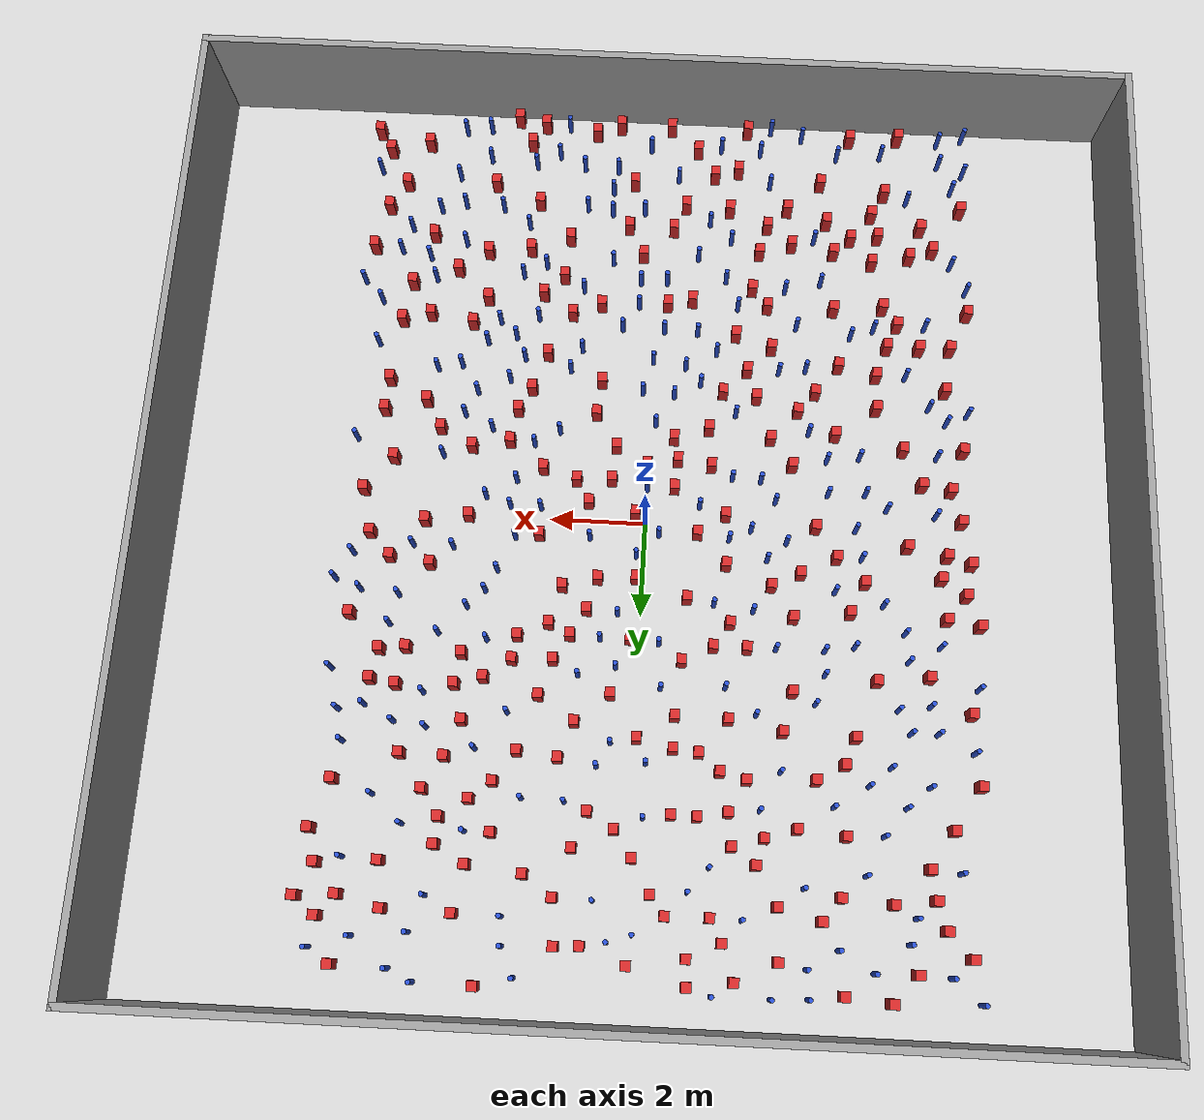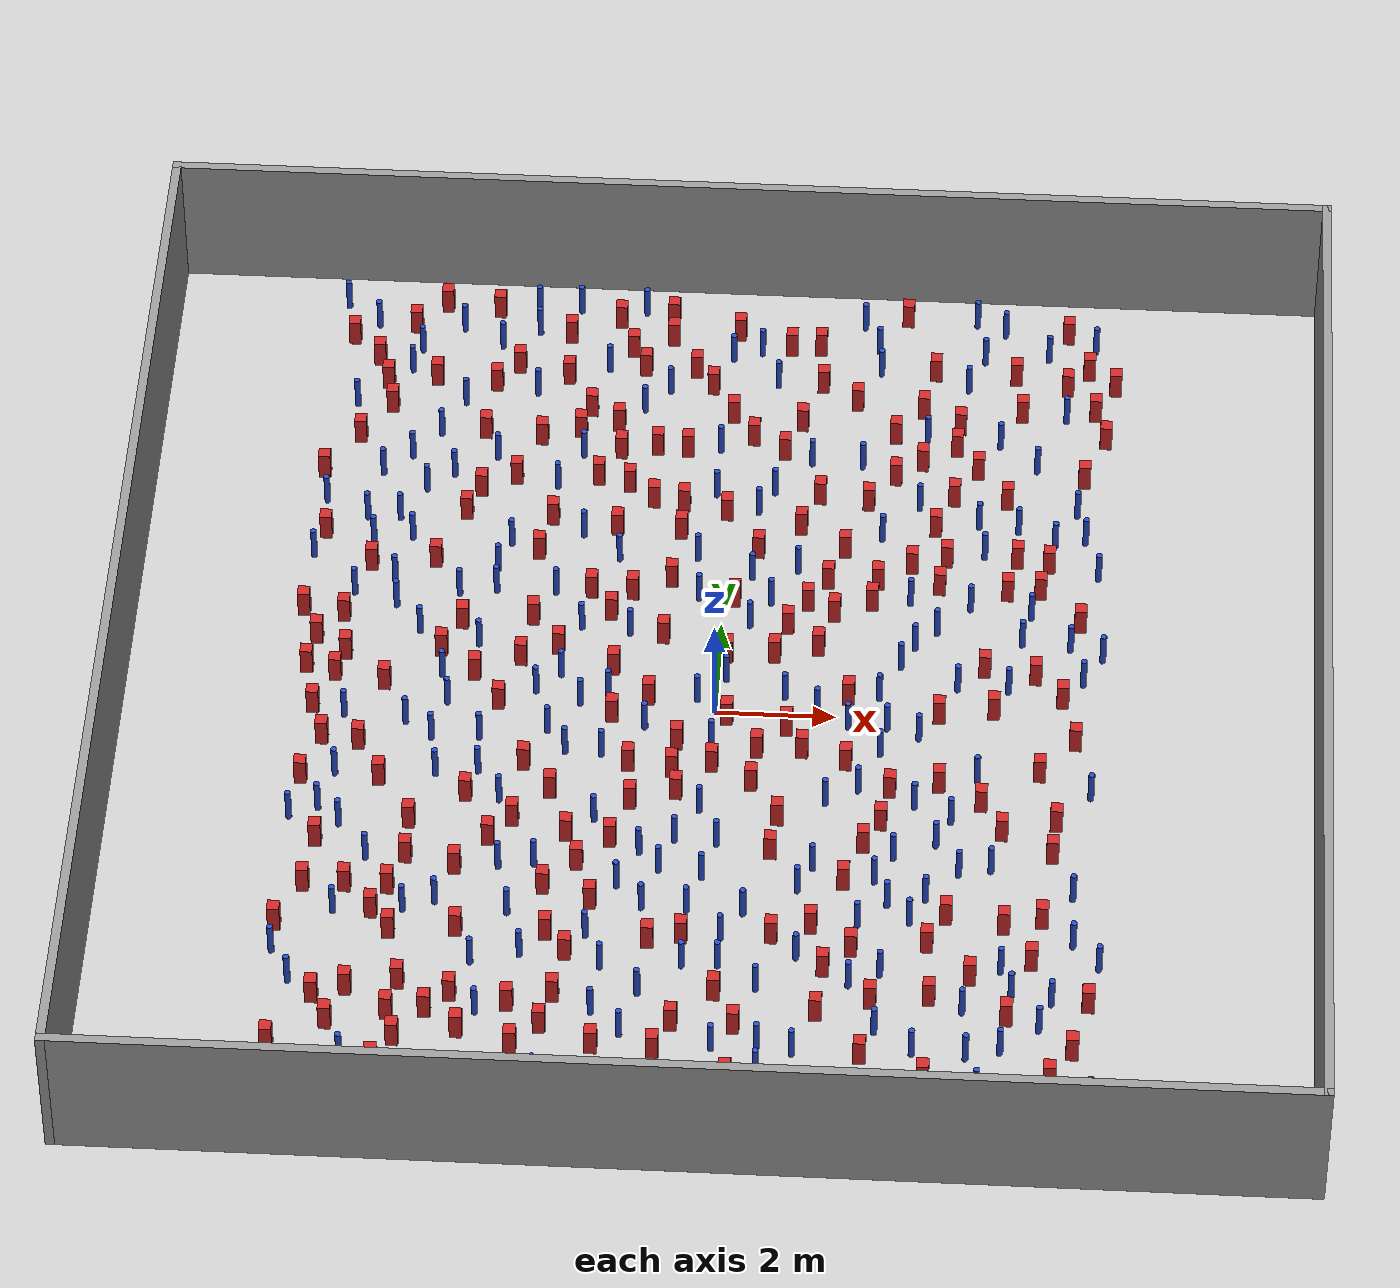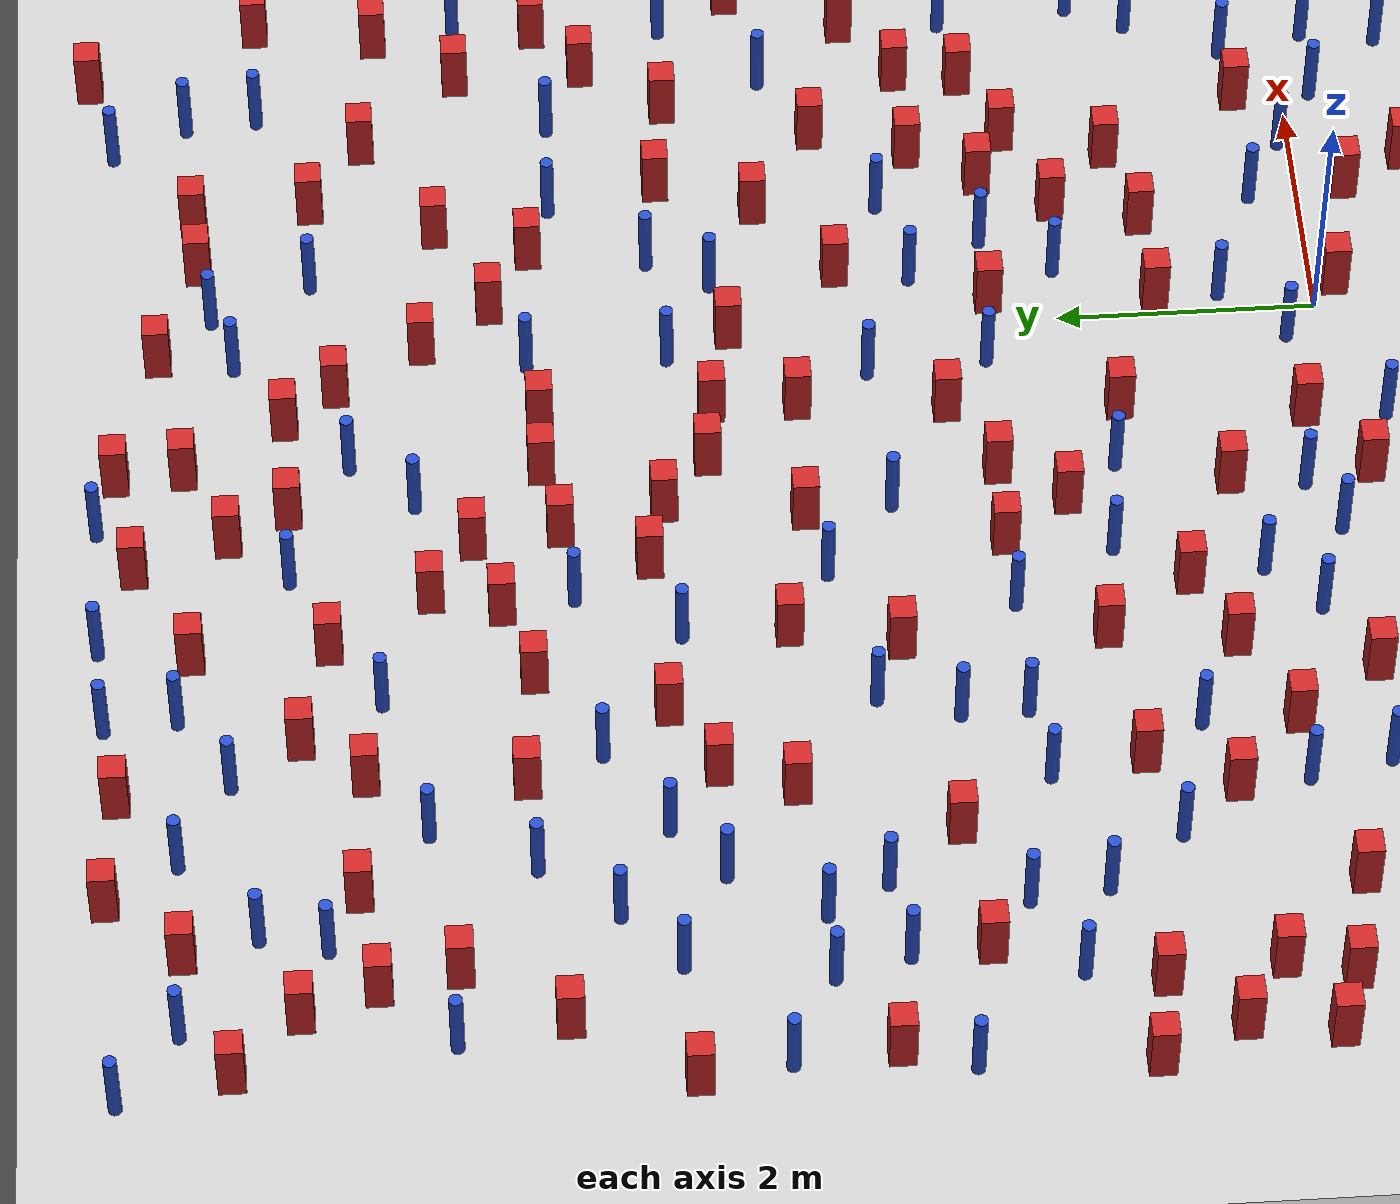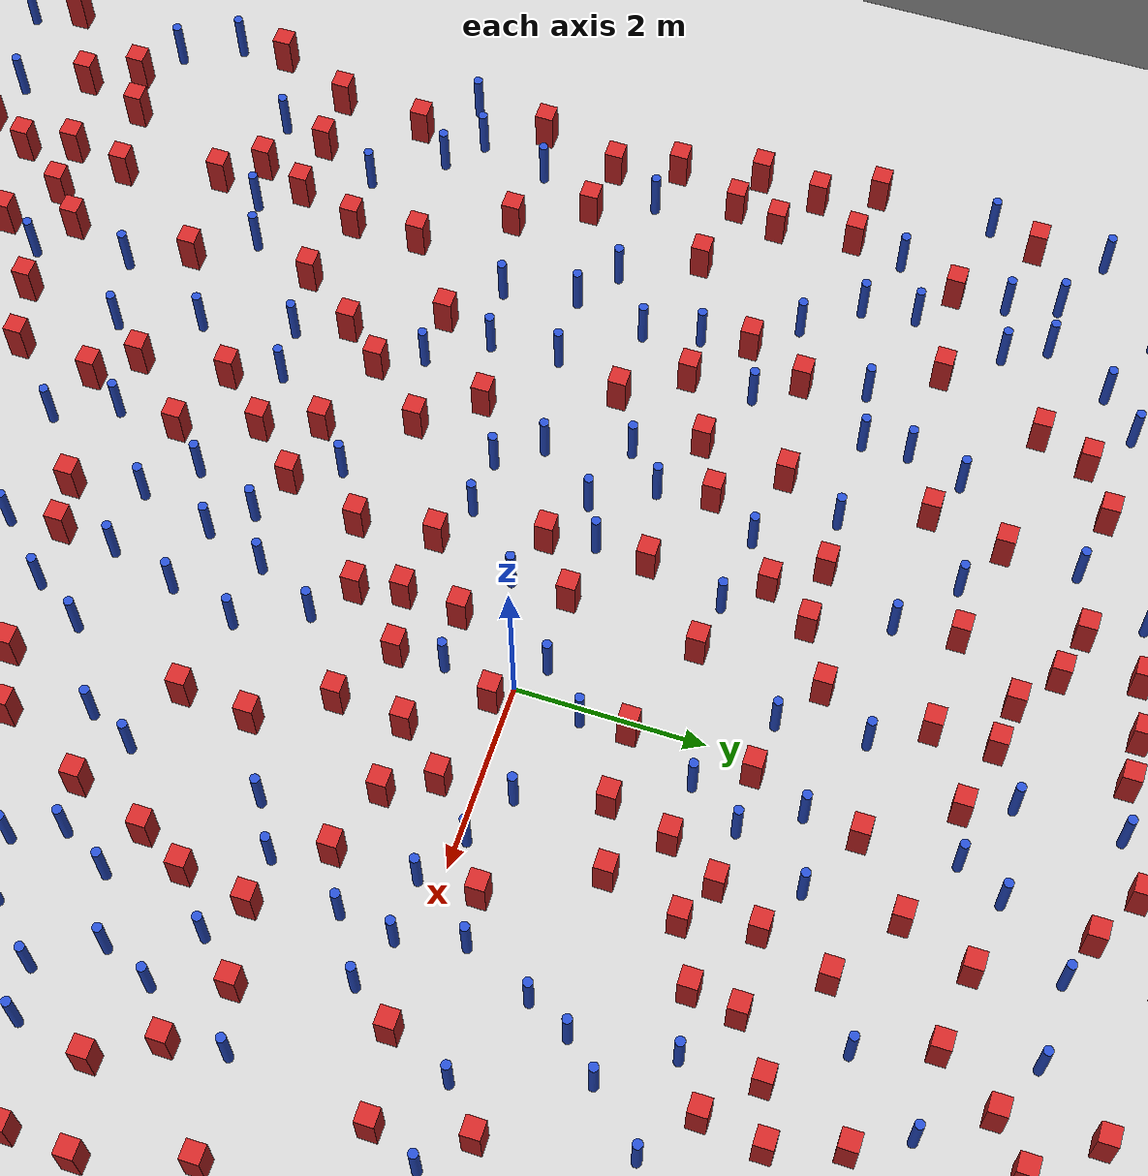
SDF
<sdf version="1.6">
 <world name="default">
  <light name="sun" type="directional">
   <pose>0 0 1000 0 -0 0</pose>
   <diffuse>0.8 0.8 0.8 1</diffuse>
   <specular>0.1 0.1 0.1 1</specular>
   <attenuation>
    <range>1000</range>
    <constant>0.9</constant>
    <linear>0.01</linear>
    <quadratic>0.001</quadratic>
   </attenuation>
   <direction>-0.5 0.5 -1</direction>
  </light>
  <model name="ground_plane">
   <static>1</static>
   <link name="link">
    <collision name="collision">
     <geometry><plane><normal>0 0 1</normal><size>100 100</size></plane></geometry>
     <surface><friction><ode><mu>100</mu><mu2>50</mu2></ode></friction></surface>
    </collision>
    <visual name="visual">
     <cast_shadows>0</cast_shadows>
     <geometry><plane><normal>0 0 1</normal><size>100 100</size></plane></geometry>
     <material>
      <ambient>1.0 1.0 1.0 1.0</ambient>
      <diffuse>0.8 0.8 0.8 1.0</diffuse>
      <specular>0.01 0.01 0.01 1.000000</specular>
     </material>
    </visual>
   </link>
  </model>
  <gravity>0 0 -9.8</gravity>
  <magnetic_field>6e-06 2.3e-05 -4.2e-05</magnetic_field>
  <atmosphere type="adiabatic"/>
  <physics name="default_physics" default="0" type="ode">
   <max_step_size>0.001</max_step_size>
   <real_time_factor>1</real_time_factor>
   <real_time_update_rate>1000</real_time_update_rate>
  </physics>
  <scene><ambient>0.4 0.4 0.4 1</ambient><background>0.7 0.7 0.7 1</background><shadows>1</shadows></scene>
  <spherical_coordinates>
   <surface_model>EARTH_WGS84</surface_model>
   <latitude_deg>0</latitude_deg>
   <longitude_deg>0</longitude_deg>
   <elevation>0</elevation>
   <heading_deg>0</heading_deg>
  </spherical_coordinates>
  <plugin name="gazebo_occupancy_map" filename="libgazebo_2Dmap_plugin.so">
   <map_resolution>0.05</map_resolution>
   <map_topic>generated_map</map_topic>
   <map_height>0.01</map_height>
   <map_size_x>50</map_size_x>
   <map_size_y>50</map_size_y>
  </plugin>
  <model name="NamedLocations">
   <static>true</static>
   <link name="DefaultStart"><pose>8.5 0 0 0 0 3.14</pose></link>
  </model>
  <model name="20x20_walls">
   <pose>0.044518 0.176112 0 0 -0 0</pose>
   <link name="Wall_1">
    <collision name="Wall_1_Collision">
     <geometry><box><size>20 0.15 2.5</size></box></geometry>
     <pose>0 0 1.25 0 -0 0</pose>
    </collision>
    <visual name="Wall_1_Visual">
     <pose>0 0 1.25 0 -0 0</pose>
     <geometry><box><size>20 0.15 2.5</size></box></geometry>
     <material>
      <script><uri>file://media/materials/scripts/gazebo.material</uri><name>Gazebo/Grey</name></script>
      <ambient>0.976471 0.992157 1 1</ambient>
     </material>
     <meta><layer>0</layer></meta>
    </visual>
    <pose>0 9.925 0 0 -0 0</pose>
   </link>
   <link name="Wall_3">
    <collision name="Wall_3_Collision">
     <geometry><box><size>20 0.15 2.5</size></box></geometry>
     <pose>0 0 1.25 0 -0 0</pose>
    </collision>
    <visual name="Wall_3_Visual">
     <pose>0 0 1.25 0 -0 0</pose>
     <geometry><box><size>20 0.15 2.5</size></box></geometry>
     <material>
      <script><uri>file://media/materials/scripts/gazebo.material</uri><name>Gazebo/Grey</name></script>
      <ambient>0.976471 0.992157 1 1</ambient>
     </material>
     <meta><layer>0</layer></meta>
    </visual>
    <pose>9.925 0 0 0 0 -1.5708</pose>
   </link>
   <link name="Wall_4">
    <collision name="Wall_4_Collision">
     <geometry><box><size>20 0.15 2.5</size></box></geometry>
     <pose>0 0 1.25 0 -0 0</pose>
    </collision>
    <visual name="Wall_4_Visual">
     <pose>0 0 1.25 0 -0 0</pose>
     <geometry><box><size>20 0.15 2.5</size></box></geometry>
     <material>
      <script><uri>file://media/materials/scripts/gazebo.material</uri><name>Gazebo/Grey</name></script>
      <ambient>0.976471 0.992157 1 1</ambient>
     </material>
     <meta><layer>0</layer></meta>
    </visual>
    <pose>0 -9.925 0 0 -0 3.14159</pose>
   </link>
   <link name="Wall_5">
    <collision name="Wall_5_Collision">
     <geometry><box><size>20 0.15 2.5</size></box></geometry>
     <pose>0 0 1.25 0 -0 0</pose>
    </collision>
    <visual name="Wall_5_Visual">
     <pose>0 0 1.25 0 -0 0</pose>
     <geometry><box><size>20 0.15 2.5</size></box></geometry>
     <material>
      <script><uri>file://media/materials/scripts/gazebo.material</uri><name>Gazebo/Grey</name></script>
      <ambient>0.976471 0.992157 1 1</ambient>
     </material>
     <meta><layer>0</layer></meta>
    </visual>
    <pose>-9.925 0 0 0 -0 1.5708</pose>
   </link>
   <static>1</static>
  </model>
  <model name="pole_obstacle0">
   <static>true</static>
   <pose>3.75022764501 -2.78739686632 -9.47619616065e-06 5.49618799737e-07 2.36310414051e-07 -1.55090534807e-07</pose>
   <link name="link">
    <pose>0 0 0.3 0 -0 0</pose>
    <inertial>
     <mass>1</mass>
     <inertia><ixx>0.145833</ixx><ixy>0</ixy><ixz>0</ixz><iyy>0.145833</iyy><iyz>0</iyz><izz>0.125</izz></inertia>
    </inertial>
    <collision name="collision">
     <geometry><cylinder><radius>0.05</radius><length>.6</length></cylinder></geometry>
    </collision>
    <visual name="visual">
     <geometry><cylinder><radius>0.05</radius><length>.6</length></cylinder></geometry>
     <material>
      <script><name>Gazebo/Blue</name><uri>file://media/materials/scripts/gazebo.material</uri></script>
     </material>
    </visual>
   </link>
  </model>
  <model name="pole_obstacle1">
   <static>true</static>
   <pose>-3.93958135462 -8.87356897019 -9.4761961606e-06 5.49618799729e-07 2.36310414e-07 -1.55090534824e-07</pose>
   <link name="link">
    <pose>0 0 0.3 0 -0 0</pose>
    <inertial>
     <mass>1</mass>
     <inertia><ixx>0.145833</ixx><ixy>0</ixy><ixz>0</ixz><iyy>0.145833</iyy><iyz>0</iyz><izz>0.125</izz></inertia>
    </inertial>
    <collision name="collision">
     <geometry><cylinder><radius>0.05</radius><length>.6</length></cylinder></geometry>
    </collision>
    <visual name="visual">
     <geometry><cylinder><radius>0.05</radius><length>.6</length></cylinder></geometry>
     <material>
      <script><name>Gazebo/Blue</name><uri>file://media/materials/scripts/gazebo.material</uri></script>
     </material>
    </visual>
   </link>
  </model>
  <model name="square_post_obstacle0">
   <static>true</static>
   <pose>-4.84128660663 -2.74777889471 -6.11067671241e-07 -5.50515727128e-06 -8.79689657224e-07 2.37013304536e-05</pose>
   <link name="link">
    <pose>0 0 0.25 0 -0 0</pose>
    <inertial>
     <mass>100</mass>
     <inertia>
      <ixx>0.166667</ixx>
      <ixy>0</ixy>
      <ixz>0</ixz>
      <iyy>0.166667</iyy>
      <iyz>0</iyz>
      <izz>0.166667</izz>
     </inertia>
    </inertial>
    <collision name="collision"><geometry><box><size>.2 .2 .5</size></box></geometry></collision>
    <visual name="visual">
     <geometry><box><size>.2 .2 .5</size></box></geometry>
     <material>
      <script><name>Gazebo/Red</name><uri>file://media/materials/scripts/gazebo.material</uri></script>
     </material>
    </visual>
   </link>
  </model>
  <model name="square_post_obstacle1">
   <static>true</static>
   <pose>-3.71598876451 -7.18405634265 -6.11067671241e-07 -5.50515727128e-06 -8.79689657224e-07 2.37013304536e-05</pose>
   <link name="link">
    <pose>0 0 0.25 0 -0 0</pose>
    <inertial>
     <mass>100</mass>
     <inertia>
      <ixx>0.166667</ixx>
      <ixy>0</ixy>
      <ixz>0</ixz>
      <iyy>0.166667</iyy>
      <iyz>0</iyz>
      <izz>0.166667</izz>
     </inertia>
    </inertial>
    <collision name="collision"><geometry><box><size>.2 .2 .5</size></box></geometry></collision>
    <visual name="visual">
     <geometry><box><size>.2 .2 .5</size></box></geometry>
     <material>
      <script><name>Gazebo/Red</name><uri>file://media/materials/scripts/gazebo.material</uri></script>
     </material>
    </visual>
   </link>
  </model>
  <model name="pole_obstacle2">
   <static>true</static>
   <pose>3.51476764947 -7.23739863421 -9.47619616065e-06 5.49618799738e-07 2.3631041406e-07 -1.55090534801e-07</pose>
   <link name="link">
    <pose>0 0 0.3 0 -0 0</pose>
    <inertial>
     <mass>1</mass>
     <inertia><ixx>0.145833</ixx><ixy>0</ixy><ixz>0</ixz><iyy>0.145833</iyy><iyz>0</iyz><izz>0.125</izz></inertia>
    </inertial>
    <collision name="collision">
     <geometry><cylinder><radius>0.05</radius><length>.6</length></cylinder></geometry>
    </collision>
    <visual name="visual">
     <geometry><cylinder><radius>0.05</radius><length>.6</length></cylinder></geometry>
     <material>
      <script><name>Gazebo/Blue</name><uri>file://media/materials/scripts/gazebo.material</uri></script>
     </material>
    </visual>
   </link>
  </model>
  <model name="pole_obstacle3">
   <static>true</static>
   <pose>-1.37695919305 -3.93688624927 -9.47619616065e-06 5.49618799737e-07 2.36310414062e-07 -1.55090534798e-07</pose>
   <link name="link">
    <pose>0 0 0.3 0 -0 0</pose>
    <inertial>
     <mass>1</mass>
     <inertia><ixx>0.145833</ixx><ixy>0</ixy><ixz>0</ixz><iyy>0.145833</iyy><iyz>0</iyz><izz>0.125</izz></inertia>
    </inertial>
    <collision name="collision">
     <geometry><cylinder><radius>0.05</radius><length>.6</length></cylinder></geometry>
    </collision>
    <visual name="visual">
     <geometry><cylinder><radius>0.05</radius><length>.6</length></cylinder></geometry>
     <material>
      <script><name>Gazebo/Blue</name><uri>file://media/materials/scripts/gazebo.material</uri></script>
     </material>
    </visual>
   </link>
  </model>
  <model name="pole_obstacle4">
   <static>true</static>
   <pose>-2.95678974515 5.09127910285 -9.47619616065e-06 5.49618799738e-07 2.3631041406e-07 -1.55090534801e-07</pose>
   <link name="link">
    <pose>0 0 0.3 0 -0 0</pose>
    <inertial>
     <mass>1</mass>
     <inertia><ixx>0.145833</ixx><ixy>0</ixy><ixz>0</ixz><iyy>0.145833</iyy><iyz>0</iyz><izz>0.125</izz></inertia>
    </inertial>
    <collision name="collision">
     <geometry><cylinder><radius>0.05</radius><length>.6</length></cylinder></geometry>
    </collision>
    <visual name="visual">
     <geometry><cylinder><radius>0.05</radius><length>.6</length></cylinder></geometry>
     <material>
      <script><name>Gazebo/Blue</name><uri>file://media/materials/scripts/gazebo.material</uri></script>
     </material>
    </visual>
   </link>
  </model>
  <model name="pole_obstacle5">
   <static>true</static>
   <pose>-3.41100039363 -2.16447534626 -9.47619616065e-06 5.49618799737e-07 2.36310414051e-07 -1.55090534807e-07</pose>
   <link name="link">
    <pose>0 0 0.3 0 -0 0</pose>
    <inertial>
     <mass>1</mass>
     <inertia><ixx>0.145833</ixx><ixy>0</ixy><ixz>0</ixz><iyy>0.145833</iyy><iyz>0</iyz><izz>0.125</izz></inertia>
    </inertial>
    <collision name="collision">
     <geometry><cylinder><radius>0.05</radius><length>.6</length></cylinder></geometry>
    </collision>
    <visual name="visual">
     <geometry><cylinder><radius>0.05</radius><length>.6</length></cylinder></geometry>
     <material>
      <script><name>Gazebo/Blue</name><uri>file://media/materials/scripts/gazebo.material</uri></script>
     </material>
    </visual>
   </link>
  </model>
  <model name="pole_obstacle6">
   <static>true</static>
   <pose>2.43207186262 8.13492291357 -9.4761961606e-06 5.49618799729e-07 2.36310414e-07 -1.55090534824e-07</pose>
   <link name="link">
    <pose>0 0 0.3 0 -0 0</pose>
    <inertial>
     <mass>1</mass>
     <inertia><ixx>0.145833</ixx><ixy>0</ixy><ixz>0</ixz><iyy>0.145833</iyy><iyz>0</iyz><izz>0.125</izz></inertia>
    </inertial>
    <collision name="collision">
     <geometry><cylinder><radius>0.05</radius><length>.6</length></cylinder></geometry>
    </collision>
    <visual name="visual">
     <geometry><cylinder><radius>0.05</radius><length>.6</length></cylinder></geometry>
     <material>
      <script><name>Gazebo/Blue</name><uri>file://media/materials/scripts/gazebo.material</uri></script>
     </material>
    </visual>
   </link>
  </model>
  <model name="square_post_obstacle2">
   <static>true</static>
   <pose>4.81245755548 -2.510650825 -6.11067671241e-07 -5.50515727128e-06 -8.79689657224e-07 2.37013304536e-05</pose>
   <link name="link">
    <pose>0 0 0.25 0 -0 0</pose>
    <inertial>
     <mass>100</mass>
     <inertia>
      <ixx>0.166667</ixx>
      <ixy>0</ixy>
      <ixz>0</ixz>
      <iyy>0.166667</iyy>
      <iyz>0</iyz>
      <izz>0.166667</izz>
     </inertia>
    </inertial>
    <collision name="collision"><geometry><box><size>.2 .2 .5</size></box></geometry></collision>
    <visual name="visual">
     <geometry><box><size>.2 .2 .5</size></box></geometry>
     <material>
      <script><name>Gazebo/Red</name><uri>file://media/materials/scripts/gazebo.material</uri></script>
     </material>
    </visual>
   </link>
  </model>
  <model name="square_post_obstacle3">
   <static>true</static>
   <pose>-3.80728413386 7.94259799385 -6.11067671241e-07 -5.50515727128e-06 -8.79689657224e-07 2.37013304536e-05</pose>
   <link name="link">
    <pose>0 0 0.25 0 -0 0</pose>
    <inertial>
     <mass>100</mass>
     <inertia>
      <ixx>0.166667</ixx>
      <ixy>0</ixy>
      <ixz>0</ixz>
      <iyy>0.166667</iyy>
      <iyz>0</iyz>
      <izz>0.166667</izz>
     </inertia>
    </inertial>
    <collision name="collision"><geometry><box><size>.2 .2 .5</size></box></geometry></collision>
    <visual name="visual">
     <geometry><box><size>.2 .2 .5</size></box></geometry>
     <material>
      <script><name>Gazebo/Red</name><uri>file://media/materials/scripts/gazebo.material</uri></script>
     </material>
    </visual>
   </link>
  </model>
  <model name="square_post_obstacle4">
   <static>true</static>
   <pose>-5.00308649444 -7.95392521139 -6.11067671241e-07 -5.50515727128e-06 -8.79689657224e-07 2.37013304536e-05</pose>
   <link name="link">
    <pose>0 0 0.25 0 -0 0</pose>
    <inertial>
     <mass>100</mass>
     <inertia>
      <ixx>0.166667</ixx>
      <ixy>0</ixy>
      <ixz>0</ixz>
      <iyy>0.166667</iyy>
      <iyz>0</iyz>
      <izz>0.166667</izz>
     </inertia>
    </inertial>
    <collision name="collision"><geometry><box><size>.2 .2 .5</size></box></geometry></collision>
    <visual name="visual">
     <geometry><box><size>.2 .2 .5</size></box></geometry>
     <material>
      <script><name>Gazebo/Red</name><uri>file://media/materials/scripts/gazebo.material</uri></script>
     </material>
    </visual>
   </link>
  </model>
  <model name="pole_obstacle7">
   <static>true</static>
   <pose>6.06499540367 0.939890969461 -9.47619616065e-06 5.49618799737e-07 2.36310414061e-07 -1.550905348e-07</pose>
   <link name="link">
    <pose>0 0 0.3 0 -0 0</pose>
    <inertial>
     <mass>1</mass>
     <inertia><ixx>0.145833</ixx><ixy>0</ixy><ixz>0</ixz><iyy>0.145833</iyy><iyz>0</iyz><izz>0.125</izz></inertia>
    </inertial>
    <collision name="collision">
     <geometry><cylinder><radius>0.05</radius><length>.6</length></cylinder></geometry>
    </collision>
    <visual name="visual">
     <geometry><cylinder><radius>0.05</radius><length>.6</length></cylinder></geometry>
     <material>
      <script><name>Gazebo/Blue</name><uri>file://media/materials/scripts/gazebo.material</uri></script>
     </material>
    </visual>
   </link>
  </model>
  <model name="pole_obstacle8">
   <static>true</static>
   <pose>0.990887998173 -8.33564747004 -9.47619616065e-06 5.49618799737e-07 2.36310414031e-07 -1.55090534817e-07</pose>
   <link name="link">
    <pose>0 0 0.3 0 -0 0</pose>
    <inertial>
     <mass>1</mass>
     <inertia><ixx>0.145833</ixx><ixy>0</ixy><ixz>0</ixz><iyy>0.145833</iyy><iyz>0</iyz><izz>0.125</izz></inertia>
    </inertial>
    <collision name="collision">
     <geometry><cylinder><radius>0.05</radius><length>.6</length></cylinder></geometry>
    </collision>
    <visual name="visual">
     <geometry><cylinder><radius>0.05</radius><length>.6</length></cylinder></geometry>
     <material>
      <script><name>Gazebo/Blue</name><uri>file://media/materials/scripts/gazebo.material</uri></script>
     </material>
    </visual>
   </link>
  </model>
  <model name="square_post_obstacle5">
   <static>true</static>
   <pose>-6.71850591008 1.31194044388 -6.11067671241e-07 -5.50515727128e-06 -8.79689657224e-07 2.37013304536e-05</pose>
   <link name="link">
    <pose>0 0 0.25 0 -0 0</pose>
    <inertial>
     <mass>100</mass>
     <inertia>
      <ixx>0.166667</ixx>
      <ixy>0</ixy>
      <ixz>0</ixz>
      <iyy>0.166667</iyy>
      <iyz>0</iyz>
      <izz>0.166667</izz>
     </inertia>
    </inertial>
    <collision name="collision"><geometry><box><size>.2 .2 .5</size></box></geometry></collision>
    <visual name="visual">
     <geometry><box><size>.2 .2 .5</size></box></geometry>
     <material>
      <script><name>Gazebo/Red</name><uri>file://media/materials/scripts/gazebo.material</uri></script>
     </material>
    </visual>
   </link>
  </model>
  <model name="square_post_obstacle6">
   <static>true</static>
   <pose>-0.790783355367 6.04530194264 -6.11067671241e-07 -5.50515727128e-06 -8.79689657224e-07 2.37013304536e-05</pose>
   <link name="link">
    <pose>0 0 0.25 0 -0 0</pose>
    <inertial>
     <mass>100</mass>
     <inertia>
      <ixx>0.166667</ixx>
      <ixy>0</ixy>
      <ixz>0</ixz>
      <iyy>0.166667</iyy>
      <iyz>0</iyz>
      <izz>0.166667</izz>
     </inertia>
    </inertial>
    <collision name="collision"><geometry><box><size>.2 .2 .5</size></box></geometry></collision>
    <visual name="visual">
     <geometry><box><size>.2 .2 .5</size></box></geometry>
     <material>
      <script><name>Gazebo/Red</name><uri>file://media/materials/scripts/gazebo.material</uri></script>
     </material>
    </visual>
   </link>
  </model>
  <model name="square_post_obstacle7">
   <static>true</static>
   <pose>5.3043008412 2.97691154818 -6.11067671241e-07 -5.50515727128e-06 -8.79689657224e-07 2.37013304536e-05</pose>
   <link name="link">
    <pose>0 0 0.25 0 -0 0</pose>
    <inertial>
     <mass>100</mass>
     <inertia>
      <ixx>0.166667</ixx>
      <ixy>0</ixy>
      <ixz>0</ixz>
      <iyy>0.166667</iyy>
      <iyz>0</iyz>
      <izz>0.166667</izz>
     </inertia>
    </inertial>
    <collision name="collision"><geometry><box><size>.2 .2 .5</size></box></geometry></collision>
    <visual name="visual">
     <geometry><box><size>.2 .2 .5</size></box></geometry>
     <material>
      <script><name>Gazebo/Red</name><uri>file://media/materials/scripts/gazebo.material</uri></script>
     </material>
    </visual>
   </link>
  </model>
  <model name="pole_obstacle9">
   <static>true</static>
   <pose>-4.42675377921 2.47935275778 -9.47619616065e-06 5.49618799738e-07 2.36310414051e-07 -1.55090534805e-07</pose>
   <link name="link">
    <pose>0 0 0.3 0 -0 0</pose>
    <inertial>
     <mass>1</mass>
     <inertia><ixx>0.145833</ixx><ixy>0</ixy><ixz>0</ixz><iyy>0.145833</iyy><iyz>0</iyz><izz>0.125</izz></inertia>
    </inertial>
    <collision name="collision">
     <geometry><cylinder><radius>0.05</radius><length>.6</length></cylinder></geometry>
    </collision>
    <visual name="visual">
     <geometry><cylinder><radius>0.05</radius><length>.6</length></cylinder></geometry>
     <material>
      <script><name>Gazebo/Blue</name><uri>file://media/materials/scripts/gazebo.material</uri></script>
     </material>
    </visual>
   </link>
  </model>
  <model name="pole_obstacle10">
   <static>true</static>
   <pose>-6.2350550895 -8.77180604748 -9.47619616065e-06 5.49618799737e-07 2.36310414065e-07 -1.55090534796e-07</pose>
   <link name="link">
    <pose>0 0 0.3 0 -0 0</pose>
    <inertial>
     <mass>1</mass>
     <inertia><ixx>0.145833</ixx><ixy>0</ixy><ixz>0</ixz><iyy>0.145833</iyy><iyz>0</iyz><izz>0.125</izz></inertia>
    </inertial>
    <collision name="collision">
     <geometry><cylinder><radius>0.05</radius><length>.6</length></cylinder></geometry>
    </collision>
    <visual name="visual">
     <geometry><cylinder><radius>0.05</radius><length>.6</length></cylinder></geometry>
     <material>
      <script><name>Gazebo/Blue</name><uri>file://media/materials/scripts/gazebo.material</uri></script>
     </material>
    </visual>
   </link>
  </model>
  <model name="pole_obstacle11">
   <static>true</static>
   <pose>-5.9821969087 -2.83860901818 -9.47619616065e-06 5.49618799738e-07 2.36310414051e-07 -1.55090534805e-07</pose>
   <link name="link">
    <pose>0 0 0.3 0 -0 0</pose>
    <inertial>
     <mass>1</mass>
     <inertia><ixx>0.145833</ixx><ixy>0</ixy><ixz>0</ixz><iyy>0.145833</iyy><iyz>0</iyz><izz>0.125</izz></inertia>
    </inertial>
    <collision name="collision">
     <geometry><cylinder><radius>0.05</radius><length>.6</length></cylinder></geometry>
    </collision>
    <visual name="visual">
     <geometry><cylinder><radius>0.05</radius><length>.6</length></cylinder></geometry>
     <material>
      <script><name>Gazebo/Blue</name><uri>file://media/materials/scripts/gazebo.material</uri></script>
     </material>
    </visual>
   </link>
  </model>
  <model name="pole_obstacle12">
   <static>true</static>
   <pose>3.00801249524 -4.12115570584 -9.47619616065e-06 5.49618799738e-07 2.3631041406e-07 -1.55090534801e-07</pose>
   <link name="link">
    <pose>0 0 0.3 0 -0 0</pose>
    <inertial>
     <mass>1</mass>
     <inertia><ixx>0.145833</ixx><ixy>0</ixy><ixz>0</ixz><iyy>0.145833</iyy><iyz>0</iyz><izz>0.125</izz></inertia>
    </inertial>
    <collision name="collision">
     <geometry><cylinder><radius>0.05</radius><length>.6</length></cylinder></geometry>
    </collision>
    <visual name="visual">
     <geometry><cylinder><radius>0.05</radius><length>.6</length></cylinder></geometry>
     <material>
      <script><name>Gazebo/Blue</name><uri>file://media/materials/scripts/gazebo.material</uri></script>
     </material>
    </visual>
   </link>
  </model>
  <model name="square_post_obstacle8">
   <static>true</static>
   <pose>4.60553726486 0.183681502526 -6.11067671241e-07 -5.50515727128e-06 -8.79689657224e-07 2.37013304536e-05</pose>
   <link name="link">
    <pose>0 0 0.25 0 -0 0</pose>
    <inertial>
     <mass>100</mass>
     <inertia>
      <ixx>0.166667</ixx>
      <ixy>0</ixy>
      <ixz>0</ixz>
      <iyy>0.166667</iyy>
      <iyz>0</iyz>
      <izz>0.166667</izz>
     </inertia>
    </inertial>
    <collision name="collision"><geometry><box><size>.2 .2 .5</size></box></geometry></collision>
    <visual name="visual">
     <geometry><box><size>.2 .2 .5</size></box></geometry>
     <material>
      <script><name>Gazebo/Red</name><uri>file://media/materials/scripts/gazebo.material</uri></script>
     </material>
    </visual>
   </link>
  </model>
  <model name="square_post_obstacle9">
   <static>true</static>
   <pose>-1.1920065152 8.7605117663 -6.11067671241e-07 -5.50515727128e-06 -8.79689657224e-07 2.37013304536e-05</pose>
   <link name="link">
    <pose>0 0 0.25 0 -0 0</pose>
    <inertial>
     <mass>100</mass>
     <inertia>
      <ixx>0.166667</ixx>
      <ixy>0</ixy>
      <ixz>0</ixz>
      <iyy>0.166667</iyy>
      <iyz>0</iyz>
      <izz>0.166667</izz>
     </inertia>
    </inertial>
    <collision name="collision"><geometry><box><size>.2 .2 .5</size></box></geometry></collision>
    <visual name="visual">
     <geometry><box><size>.2 .2 .5</size></box></geometry>
     <material>
      <script><name>Gazebo/Red</name><uri>file://media/materials/scripts/gazebo.material</uri></script>
     </material>
    </visual>
   </link>
  </model>
  <model name="pole_obstacle13">
   <static>true</static>
   <pose>-6.89911833918 9.32958640942 -9.47619616065e-06 5.49618799737e-07 2.36310414065e-07 -1.55090534796e-07</pose>
   <link name="link">
    <pose>0 0 0.3 0 -0 0</pose>
    <inertial>
     <mass>1</mass>
     <inertia><ixx>0.145833</ixx><ixy>0</ixy><ixz>0</ixz><iyy>0.145833</iyy><iyz>0</iyz><izz>0.125</izz></inertia>
    </inertial>
    <collision name="collision">
     <geometry><cylinder><radius>0.05</radius><length>.6</length></cylinder></geometry>
    </collision>
    <visual name="visual">
     <geometry><cylinder><radius>0.05</radius><length>.6</length></cylinder></geometry>
     <material>
      <script><name>Gazebo/Blue</name><uri>file://media/materials/scripts/gazebo.material</uri></script>
     </material>
    </visual>
   </link>
  </model>
  <model name="square_post_obstacle10">
   <static>true</static>
   <pose>1.51281801261 -9.20430132385 -6.11067671241e-07 -5.50515727128e-06 -8.79689657224e-07 2.37013304536e-05</pose>
   <link name="link">
    <pose>0 0 0.25 0 -0 0</pose>
    <inertial>
     <mass>100</mass>
     <inertia>
      <ixx>0.166667</ixx>
      <ixy>0</ixy>
      <ixz>0</ixz>
      <iyy>0.166667</iyy>
      <iyz>0</iyz>
      <izz>0.166667</izz>
     </inertia>
    </inertial>
    <collision name="collision"><geometry><box><size>.2 .2 .5</size></box></geometry></collision>
    <visual name="visual">
     <geometry><box><size>.2 .2 .5</size></box></geometry>
     <material>
      <script><name>Gazebo/Red</name><uri>file://media/materials/scripts/gazebo.material</uri></script>
     </material>
    </visual>
   </link>
  </model>
  <model name="square_post_obstacle11">
   <static>true</static>
   <pose>0.863928847242 8.6175819762 -6.11067671241e-07 -5.50515727128e-06 -8.79689657224e-07 2.37013304536e-05</pose>
   <link name="link">
    <pose>0 0 0.25 0 -0 0</pose>
    <inertial>
     <mass>100</mass>
     <inertia>
      <ixx>0.166667</ixx>
      <ixy>0</ixy>
      <ixz>0</ixz>
      <iyy>0.166667</iyy>
      <iyz>0</iyz>
      <izz>0.166667</izz>
     </inertia>
    </inertial>
    <collision name="collision"><geometry><box><size>.2 .2 .5</size></box></geometry></collision>
    <visual name="visual">
     <geometry><box><size>.2 .2 .5</size></box></geometry>
     <material>
      <script><name>Gazebo/Red</name><uri>file://media/materials/scripts/gazebo.material</uri></script>
     </material>
    </visual>
   </link>
  </model>
  <model name="pole_obstacle14">
   <static>true</static>
   <pose>3.38613446248 -0.424734455915 -9.47619616065e-06 5.49618799738e-07 2.36310414074e-07 -1.55090534794e-07</pose>
   <link name="link">
    <pose>0 0 0.3 0 -0 0</pose>
    <inertial>
     <mass>1</mass>
     <inertia><ixx>0.145833</ixx><ixy>0</ixy><ixz>0</ixz><iyy>0.145833</iyy><iyz>0</iyz><izz>0.125</izz></inertia>
    </inertial>
    <collision name="collision">
     <geometry><cylinder><radius>0.05</radius><length>.6</length></cylinder></geometry>
    </collision>
    <visual name="visual">
     <geometry><cylinder><radius>0.05</radius><length>.6</length></cylinder></geometry>
     <material>
      <script><name>Gazebo/Blue</name><uri>file://media/materials/scripts/gazebo.material</uri></script>
     </material>
    </visual>
   </link>
  </model>
  <model name="pole_obstacle15">
   <static>true</static>
   <pose>-1.61575275957 -6.651373899 -9.47619616065e-06 5.49618799737e-07 2.36310414061e-07 -1.550905348e-07</pose>
   <link name="link">
    <pose>0 0 0.3 0 -0 0</pose>
    <inertial>
     <mass>1</mass>
     <inertia><ixx>0.145833</ixx><ixy>0</ixy><ixz>0</ixz><iyy>0.145833</iyy><iyz>0</iyz><izz>0.125</izz></inertia>
    </inertial>
    <collision name="collision">
     <geometry><cylinder><radius>0.05</radius><length>.6</length></cylinder></geometry>
    </collision>
    <visual name="visual">
     <geometry><cylinder><radius>0.05</radius><length>.6</length></cylinder></geometry>
     <material>
      <script><name>Gazebo/Blue</name><uri>file://media/materials/scripts/gazebo.material</uri></script>
     </material>
    </visual>
   </link>
  </model>
  <model name="square_post_obstacle12">
   <static>true</static>
   <pose>-1.2192091242 9.27481414858 -6.11067671241e-07 -5.50515727128e-06 -8.79689657224e-07 2.37013304536e-05</pose>
   <link name="link">
    <pose>0 0 0.25 0 -0 0</pose>
    <inertial>
     <mass>100</mass>
     <inertia>
      <ixx>0.166667</ixx>
      <ixy>0</ixy>
      <ixz>0</ixz>
      <iyy>0.166667</iyy>
      <iyz>0</iyz>
      <izz>0.166667</izz>
     </inertia>
    </inertial>
    <collision name="collision"><geometry><box><size>.2 .2 .5</size></box></geometry></collision>
    <visual name="visual">
     <geometry><box><size>.2 .2 .5</size></box></geometry>
     <material>
      <script><name>Gazebo/Red</name><uri>file://media/materials/scripts/gazebo.material</uri></script>
     </material>
    </visual>
   </link>
  </model>
  <model name="pole_obstacle16">
   <static>true</static>
   <pose>1.33987430858 5.87765892796 -9.47619616065e-06 5.49618799737e-07 2.36310414061e-07 -1.550905348e-07</pose>
   <link name="link">
    <pose>0 0 0.3 0 -0 0</pose>
    <inertial>
     <mass>1</mass>
     <inertia><ixx>0.145833</ixx><ixy>0</ixy><ixz>0</ixz><iyy>0.145833</iyy><iyz>0</iyz><izz>0.125</izz></inertia>
    </inertial>
    <collision name="collision">
     <geometry><cylinder><radius>0.05</radius><length>.6</length></cylinder></geometry>
    </collision>
    <visual name="visual">
     <geometry><cylinder><radius>0.05</radius><length>.6</length></cylinder></geometry>
     <material>
      <script><name>Gazebo/Blue</name><uri>file://media/materials/scripts/gazebo.material</uri></script>
     </material>
    </visual>
   </link>
  </model>
  <model name="pole_obstacle17">
   <static>true</static>
   <pose>2.2102065836 -0.225751752509 -9.4761961606e-06 5.49618799729e-07 2.36310414002e-07 -1.55090534824e-07</pose>
   <link name="link">
    <pose>0 0 0.3 0 -0 0</pose>
    <inertial>
     <mass>1</mass>
     <inertia><ixx>0.145833</ixx><ixy>0</ixy><ixz>0</ixz><iyy>0.145833</iyy><iyz>0</iyz><izz>0.125</izz></inertia>
    </inertial>
    <collision name="collision">
     <geometry><cylinder><radius>0.05</radius><length>.6</length></cylinder></geometry>
    </collision>
    <visual name="visual">
     <geometry><cylinder><radius>0.05</radius><length>.6</length></cylinder></geometry>
     <material>
      <script><name>Gazebo/Blue</name><uri>file://media/materials/scripts/gazebo.material</uri></script>
     </material>
    </visual>
   </link>
  </model>
  <model name="square_post_obstacle13">
   <static>true</static>
   <pose>-1.86878175592 8.4378977359 -6.11067671241e-07 -5.50515727128e-06 -8.79689657224e-07 2.37013304536e-05</pose>
   <link name="link">
    <pose>0 0 0.25 0 -0 0</pose>
    <inertial>
     <mass>100</mass>
     <inertia>
      <ixx>0.166667</ixx>
      <ixy>0</ixy>
      <ixz>0</ixz>
      <iyy>0.166667</iyy>
      <iyz>0</iyz>
      <izz>0.166667</izz>
     </inertia>
    </inertial>
    <collision name="collision"><geometry><box><size>.2 .2 .5</size></box></geometry></collision>
    <visual name="visual">
     <geometry><box><size>.2 .2 .5</size></box></geometry>
     <material>
      <script><name>Gazebo/Red</name><uri>file://media/materials/scripts/gazebo.material</uri></script>
     </material>
    </visual>
   </link>
  </model>
  <model name="pole_obstacle18">
   <static>true</static>
   <pose>5.0576183305 -5.95667311852 -9.47619616065e-06 5.49618799737e-07 2.36310414037e-07 -1.55090534814e-07</pose>
   <link name="link">
    <pose>0 0 0.3 0 -0 0</pose>
    <inertial>
     <mass>1</mass>
     <inertia><ixx>0.145833</ixx><ixy>0</ixy><ixz>0</ixz><iyy>0.145833</iyy><iyz>0</iyz><izz>0.125</izz></inertia>
    </inertial>
    <collision name="collision">
     <geometry><cylinder><radius>0.05</radius><length>.6</length></cylinder></geometry>
    </collision>
    <visual name="visual">
     <geometry><cylinder><radius>0.05</radius><length>.6</length></cylinder></geometry>
     <material>
      <script><name>Gazebo/Blue</name><uri>file://media/materials/scripts/gazebo.material</uri></script>
     </material>
    </visual>
   </link>
  </model>
  <model name="square_post_obstacle14">
   <static>true</static>
   <pose>1.07197444202 -3.11130883612 -6.11067671241e-07 -5.50515727128e-06 -8.79689657224e-07 2.37013304536e-05</pose>
   <link name="link">
    <pose>0 0 0.25 0 -0 0</pose>
    <inertial>
     <mass>100</mass>
     <inertia>
      <ixx>0.166667</ixx>
      <ixy>0</ixy>
      <ixz>0</ixz>
      <iyy>0.166667</iyy>
      <iyz>0</iyz>
      <izz>0.166667</izz>
     </inertia>
    </inertial>
    <collision name="collision"><geometry><box><size>.2 .2 .5</size></box></geometry></collision>
    <visual name="visual">
     <geometry><box><size>.2 .2 .5</size></box></geometry>
     <material>
      <script><name>Gazebo/Red</name><uri>file://media/materials/scripts/gazebo.material</uri></script>
     </material>
    </visual>
   </link>
  </model>
  <model name="pole_obstacle19">
   <static>true</static>
   <pose>0.982050966293 -6.01964214024 -9.47619616065e-06 5.49618799737e-07 2.36310414071e-07 -1.55090534793e-07</pose>
   <link name="link">
    <pose>0 0 0.3 0 -0 0</pose>
    <inertial>
     <mass>1</mass>
     <inertia><ixx>0.145833</ixx><ixy>0</ixy><ixz>0</ixz><iyy>0.145833</iyy><iyz>0</iyz><izz>0.125</izz></inertia>
    </inertial>
    <collision name="collision">
     <geometry><cylinder><radius>0.05</radius><length>.6</length></cylinder></geometry>
    </collision>
    <visual name="visual">
     <geometry><cylinder><radius>0.05</radius><length>.6</length></cylinder></geometry>
     <material>
      <script><name>Gazebo/Blue</name><uri>file://media/materials/scripts/gazebo.material</uri></script>
     </material>
    </visual>
   </link>
  </model>
  <model name="square_post_obstacle15">
   <static>true</static>
   <pose>5.73411436721 0.501680926353 -6.11067671241e-07 -5.50515727128e-06 -8.79689657224e-07 2.37013304536e-05</pose>
   <link name="link">
    <pose>0 0 0.25 0 -0 0</pose>
    <inertial>
     <mass>100</mass>
     <inertia>
      <ixx>0.166667</ixx>
      <ixy>0</ixy>
      <ixz>0</ixz>
      <iyy>0.166667</iyy>
      <iyz>0</iyz>
      <izz>0.166667</izz>
     </inertia>
    </inertial>
    <collision name="collision"><geometry><box><size>.2 .2 .5</size></box></geometry></collision>
    <visual name="visual">
     <geometry><box><size>.2 .2 .5</size></box></geometry>
     <material>
      <script><name>Gazebo/Red</name><uri>file://media/materials/scripts/gazebo.material</uri></script>
     </material>
    </visual>
   </link>
  </model>
  <model name="square_post_obstacle16">
   <static>true</static>
   <pose>-0.178972206804 -9.41263271013 -6.11067671241e-07 -5.50515727128e-06 -8.79689657224e-07 2.37013304536e-05</pose>
   <link name="link">
    <pose>0 0 0.25 0 -0 0</pose>
    <inertial>
     <mass>100</mass>
     <inertia>
      <ixx>0.166667</ixx>
      <ixy>0</ixy>
      <ixz>0</ixz>
      <iyy>0.166667</iyy>
      <iyz>0</iyz>
      <izz>0.166667</izz>
     </inertia>
    </inertial>
    <collision name="collision"><geometry><box><size>.2 .2 .5</size></box></geometry></collision>
    <visual name="visual">
     <geometry><box><size>.2 .2 .5</size></box></geometry>
     <material>
      <script><name>Gazebo/Red</name><uri>file://media/materials/scripts/gazebo.material</uri></script>
     </material>
    </visual>
   </link>
  </model>
  <model name="square_post_obstacle17">
   <static>true</static>
   <pose>1.22932830109 4.28504683522 -6.11067671241e-07 -5.50515727128e-06 -8.79689657224e-07 2.37013304536e-05</pose>
   <link name="link">
    <pose>0 0 0.25 0 -0 0</pose>
    <inertial>
     <mass>100</mass>
     <inertia>
      <ixx>0.166667</ixx>
      <ixy>0</ixy>
      <ixz>0</ixz>
      <iyy>0.166667</iyy>
      <iyz>0</iyz>
      <izz>0.166667</izz>
     </inertia>
    </inertial>
    <collision name="collision"><geometry><box><size>.2 .2 .5</size></box></geometry></collision>
    <visual name="visual">
     <geometry><box><size>.2 .2 .5</size></box></geometry>
     <material>
      <script><name>Gazebo/Red</name><uri>file://media/materials/scripts/gazebo.material</uri></script>
     </material>
    </visual>
   </link>
  </model>
  <model name="pole_obstacle20">
   <static>true</static>
   <pose>0.742205972916 5.1449259144 -9.47619616065e-06 5.49618799737e-07 2.36310414065e-07 -1.55090534796e-07</pose>
   <link name="link">
    <pose>0 0 0.3 0 -0 0</pose>
    <inertial>
     <mass>1</mass>
     <inertia><ixx>0.145833</ixx><ixy>0</ixy><ixz>0</ixz><iyy>0.145833</iyy><iyz>0</iyz><izz>0.125</izz></inertia>
    </inertial>
    <collision name="collision">
     <geometry><cylinder><radius>0.05</radius><length>.6</length></cylinder></geometry>
    </collision>
    <visual name="visual">
     <geometry><cylinder><radius>0.05</radius><length>.6</length></cylinder></geometry>
     <material>
      <script><name>Gazebo/Blue</name><uri>file://media/materials/scripts/gazebo.material</uri></script>
     </material>
    </visual>
   </link>
  </model>
  <model name="pole_obstacle21">
   <static>true</static>
   <pose>-2.43675443596 -9.49415780647 -9.4761961606e-06 5.49618799729e-07 2.36310414e-07 -1.55090534824e-07</pose>
   <link name="link">
    <pose>0 0 0.3 0 -0 0</pose>
    <inertial>
     <mass>1</mass>
     <inertia><ixx>0.145833</ixx><ixy>0</ixy><ixz>0</ixz><iyy>0.145833</iyy><iyz>0</iyz><izz>0.125</izz></inertia>
    </inertial>
    <collision name="collision">
     <geometry><cylinder><radius>0.05</radius><length>.6</length></cylinder></geometry>
    </collision>
    <visual name="visual">
     <geometry><cylinder><radius>0.05</radius><length>.6</length></cylinder></geometry>
     <material>
      <script><name>Gazebo/Blue</name><uri>file://media/materials/scripts/gazebo.material</uri></script>
     </material>
    </visual>
   </link>
  </model>
  <model name="pole_obstacle22">
   <static>true</static>
   <pose>-0.49837957228 -2.89466937588 -9.47619616065e-06 5.49618799737e-07 2.36310414073e-07 -1.55090534793e-07</pose>
   <link name="link">
    <pose>0 0 0.3 0 -0 0</pose>
    <inertial>
     <mass>1</mass>
     <inertia><ixx>0.145833</ixx><ixy>0</ixy><ixz>0</ixz><iyy>0.145833</iyy><iyz>0</iyz><izz>0.125</izz></inertia>
    </inertial>
    <collision name="collision">
     <geometry><cylinder><radius>0.05</radius><length>.6</length></cylinder></geometry>
    </collision>
    <visual name="visual">
     <geometry><cylinder><radius>0.05</radius><length>.6</length></cylinder></geometry>
     <material>
      <script><name>Gazebo/Blue</name><uri>file://media/materials/scripts/gazebo.material</uri></script>
     </material>
    </visual>
   </link>
  </model>
  <model name="pole_obstacle23">
   <static>true</static>
   <pose>2.95160041341 -5.61007444627 -9.47619616065e-06 5.49618799738e-07 2.3631041406e-07 -1.55090534801e-07</pose>
   <link name="link">
    <pose>0 0 0.3 0 -0 0</pose>
    <inertial>
     <mass>1</mass>
     <inertia><ixx>0.145833</ixx><ixy>0</ixy><ixz>0</ixz><iyy>0.145833</iyy><iyz>0</iyz><izz>0.125</izz></inertia>
    </inertial>
    <collision name="collision">
     <geometry><cylinder><radius>0.05</radius><length>.6</length></cylinder></geometry>
    </collision>
    <visual name="visual">
     <geometry><cylinder><radius>0.05</radius><length>.6</length></cylinder></geometry>
     <material>
      <script><name>Gazebo/Blue</name><uri>file://media/materials/scripts/gazebo.material</uri></script>
     </material>
    </visual>
   </link>
  </model>
  <model name="square_post_obstacle18">
   <static>true</static>
   <pose>5.96204900526 -0.447568271579 -6.11067671241e-07 -5.50515727128e-06 -8.79689657224e-07 2.37013304536e-05</pose>
   <link name="link">
    <pose>0 0 0.25 0 -0 0</pose>
    <inertial>
     <mass>100</mass>
     <inertia>
      <ixx>0.166667</ixx>
      <ixy>0</ixy>
      <ixz>0</ixz>
      <iyy>0.166667</iyy>
      <iyz>0</iyz>
      <izz>0.166667</izz>
     </inertia>
    </inertial>
    <collision name="collision"><geometry><box><size>.2 .2 .5</size></box></geometry></collision>
    <visual name="visual">
     <geometry><box><size>.2 .2 .5</size></box></geometry>
     <material>
      <script><name>Gazebo/Red</name><uri>file://media/materials/scripts/gazebo.material</uri></script>
     </material>
    </visual>
   </link>
  </model>
  <model name="pole_obstacle24">
   <static>true</static>
   <pose>6.02116157197 -4.83870841715 -9.47619616065e-06 5.49618799737e-07 2.36310414037e-07 -1.55090534814e-07</pose>
   <link name="link">
    <pose>0 0 0.3 0 -0 0</pose>
    <inertial>
     <mass>1</mass>
     <inertia><ixx>0.145833</ixx><ixy>0</ixy><ixz>0</ixz><iyy>0.145833</iyy><iyz>0</iyz><izz>0.125</izz></inertia>
    </inertial>
    <collision name="collision">
     <geometry><cylinder><radius>0.05</radius><length>.6</length></cylinder></geometry>
    </collision>
    <visual name="visual">
     <geometry><cylinder><radius>0.05</radius><length>.6</length></cylinder></geometry>
     <material>
      <script><name>Gazebo/Blue</name><uri>file://media/materials/scripts/gazebo.material</uri></script>
     </material>
    </visual>
   </link>
  </model>
  <model name="pole_obstacle25">
   <static>true</static>
   <pose>-5.52420104333 8.28880063008 -9.47619616065e-06 5.49618799737e-07 2.36310414065e-07 -1.55090534796e-07</pose>
   <link name="link">
    <pose>0 0 0.3 0 -0 0</pose>
    <inertial>
     <mass>1</mass>
     <inertia><ixx>0.145833</ixx><ixy>0</ixy><ixz>0</ixz><iyy>0.145833</iyy><iyz>0</iyz><izz>0.125</izz></inertia>
    </inertial>
    <collision name="collision">
     <geometry><cylinder><radius>0.05</radius><length>.6</length></cylinder></geometry>
    </collision>
    <visual name="visual">
     <geometry><cylinder><radius>0.05</radius><length>.6</length></cylinder></geometry>
     <material>
      <script><name>Gazebo/Blue</name><uri>file://media/materials/scripts/gazebo.material</uri></script>
     </material>
    </visual>
   </link>
  </model>
  <model name="pole_obstacle26">
   <static>true</static>
   <pose>-4.14554308568 8.46213966443 -9.47619616065e-06 5.49618799737e-07 2.36310414065e-07 -1.55090534796e-07</pose>
   <link name="link">
    <pose>0 0 0.3 0 -0 0</pose>
    <inertial>
     <mass>1</mass>
     <inertia><ixx>0.145833</ixx><ixy>0</ixy><ixz>0</ixz><iyy>0.145833</iyy><iyz>0</iyz><izz>0.125</izz></inertia>
    </inertial>
    <collision name="collision">
     <geometry><cylinder><radius>0.05</radius><length>.6</length></cylinder></geometry>
    </collision>
    <visual name="visual">
     <geometry><cylinder><radius>0.05</radius><length>.6</length></cylinder></geometry>
     <material>
      <script><name>Gazebo/Blue</name><uri>file://media/materials/scripts/gazebo.material</uri></script>
     </material>
    </visual>
   </link>
  </model>
  <model name="pole_obstacle27">
   <static>true</static>
   <pose>5.52006490459 -6.6473655228 -9.47619616065e-06 5.49618799737e-07 2.36310414037e-07 -1.55090534814e-07</pose>
   <link name="link">
    <pose>0 0 0.3 0 -0 0</pose>
    <inertial>
     <mass>1</mass>
     <inertia><ixx>0.145833</ixx><ixy>0</ixy><ixz>0</ixz><iyy>0.145833</iyy><iyz>0</iyz><izz>0.125</izz></inertia>
    </inertial>
    <collision name="collision">
     <geometry><cylinder><radius>0.05</radius><length>.6</length></cylinder></geometry>
    </collision>
    <visual name="visual">
     <geometry><cylinder><radius>0.05</radius><length>.6</length></cylinder></geometry>
     <material>
      <script><name>Gazebo/Blue</name><uri>file://media/materials/scripts/gazebo.material</uri></script>
     </material>
    </visual>
   </link>
  </model>
  <model name="pole_obstacle28">
   <static>true</static>
   <pose>1.5471880466 -3.88160501356 -9.47619616065e-06 5.49618799737e-07 2.36310414062e-07 -1.55090534798e-07</pose>
   <link name="link">
    <pose>0 0 0.3 0 -0 0</pose>
    <inertial>
     <mass>1</mass>
     <inertia><ixx>0.145833</ixx><ixy>0</ixy><ixz>0</ixz><iyy>0.145833</iyy><iyz>0</iyz><izz>0.125</izz></inertia>
    </inertial>
    <collision name="collision">
     <geometry><cylinder><radius>0.05</radius><length>.6</length></cylinder></geometry>
    </collision>
    <visual name="visual">
     <geometry><cylinder><radius>0.05</radius><length>.6</length></cylinder></geometry>
     <material>
      <script><name>Gazebo/Blue</name><uri>file://media/materials/scripts/gazebo.material</uri></script>
     </material>
    </visual>
   </link>
  </model>
  <model name="square_post_obstacle19">
   <static>true</static>
   <pose>0.535574568028 3.69324982012 -6.11067671241e-07 -5.50515727128e-06 -8.79689657224e-07 2.37013304536e-05</pose>
   <link name="link">
    <pose>0 0 0.25 0 -0 0</pose>
    <inertial>
     <mass>100</mass>
     <inertia>
      <ixx>0.166667</ixx>
      <ixy>0</ixy>
      <ixz>0</ixz>
      <iyy>0.166667</iyy>
      <iyz>0</iyz>
      <izz>0.166667</izz>
     </inertia>
    </inertial>
    <collision name="collision"><geometry><box><size>.2 .2 .5</size></box></geometry></collision>
    <visual name="visual">
     <geometry><box><size>.2 .2 .5</size></box></geometry>
     <material>
      <script><name>Gazebo/Red</name><uri>file://media/materials/scripts/gazebo.material</uri></script>
     </material>
    </visual>
   </link>
  </model>
  <model name="square_post_obstacle20">
   <static>true</static>
   <pose>1.20056298103 -0.363102534189 -6.11067671241e-07 -5.50515727128e-06 -8.79689657224e-07 2.37013304536e-05</pose>
   <link name="link">
    <pose>0 0 0.25 0 -0 0</pose>
    <inertial>
     <mass>100</mass>
     <inertia>
      <ixx>0.166667</ixx>
      <ixy>0</ixy>
      <ixz>0</ixz>
      <iyy>0.166667</iyy>
      <iyz>0</iyz>
      <izz>0.166667</izz>
     </inertia>
    </inertial>
    <collision name="collision"><geometry><box><size>.2 .2 .5</size></box></geometry></collision>
    <visual name="visual">
     <geometry><box><size>.2 .2 .5</size></box></geometry>
     <material>
      <script><name>Gazebo/Red</name><uri>file://media/materials/scripts/gazebo.material</uri></script>
     </material>
    </visual>
   </link>
  </model>
  <model name="pole_obstacle29">
   <static>true</static>
   <pose>-0.407549543129 2.58789013498 -9.47619616065e-06 5.49618799738e-07 2.36310414065e-07 -1.55090534798e-07</pose>
   <link name="link">
    <pose>0 0 0.3 0 -0 0</pose>
    <inertial>
     <mass>1</mass>
     <inertia><ixx>0.145833</ixx><ixy>0</ixy><ixz>0</ixz><iyy>0.145833</iyy><iyz>0</iyz><izz>0.125</izz></inertia>
    </inertial>
    <collision name="collision">
     <geometry><cylinder><radius>0.05</radius><length>.6</length></cylinder></geometry>
    </collision>
    <visual name="visual">
     <geometry><cylinder><radius>0.05</radius><length>.6</length></cylinder></geometry>
     <material>
      <script><name>Gazebo/Blue</name><uri>file://media/materials/scripts/gazebo.material</uri></script>
     </material>
    </visual>
   </link>
  </model>
  <model name="square_post_obstacle21">
   <static>true</static>
   <pose>-6.30766919779 1.83901440815 -6.11067671241e-07 -5.50515727128e-06 -8.79689657224e-07 2.37013304536e-05</pose>
   <link name="link">
    <pose>0 0 0.25 0 -0 0</pose>
    <inertial>
     <mass>100</mass>
     <inertia>
      <ixx>0.166667</ixx>
      <ixy>0</ixy>
      <ixz>0</ixz>
      <iyy>0.166667</iyy>
      <iyz>0</iyz>
      <izz>0.166667</izz>
     </inertia>
    </inertial>
    <collision name="collision"><geometry><box><size>.2 .2 .5</size></box></geometry></collision>
    <visual name="visual">
     <geometry><box><size>.2 .2 .5</size></box></geometry>
     <material>
      <script><name>Gazebo/Red</name><uri>file://media/materials/scripts/gazebo.material</uri></script>
     </material>
    </visual>
   </link>
  </model>
  <model name="pole_obstacle30">
   <static>true</static>
   <pose>-0.304566563391 0.254998979824 -9.47619616065e-06 5.49618799738e-07 2.36310414056e-07 -1.55090534803e-07</pose>
   <link name="link">
    <pose>0 0 0.3 0 -0 0</pose>
    <inertial>
     <mass>1</mass>
     <inertia><ixx>0.145833</ixx><ixy>0</ixy><ixz>0</ixz><iyy>0.145833</iyy><iyz>0</iyz><izz>0.125</izz></inertia>
    </inertial>
    <collision name="collision">
     <geometry><cylinder><radius>0.05</radius><length>.6</length></cylinder></geometry>
    </collision>
    <visual name="visual">
     <geometry><cylinder><radius>0.05</radius><length>.6</length></cylinder></geometry>
     <material>
      <script><name>Gazebo/Blue</name><uri>file://media/materials/scripts/gazebo.material</uri></script>
     </material>
    </visual>
   </link>
  </model>
  <model name="square_post_obstacle22">
   <static>true</static>
   <pose>3.75171998961 -6.10453477564 -6.11067671241e-07 -5.50515727128e-06 -8.79689657224e-07 2.37013304536e-05</pose>
   <link name="link">
    <pose>0 0 0.25 0 -0 0</pose>
    <inertial>
     <mass>100</mass>
     <inertia>
      <ixx>0.166667</ixx>
      <ixy>0</ixy>
      <ixz>0</ixz>
      <iyy>0.166667</iyy>
      <iyz>0</iyz>
      <izz>0.166667</izz>
     </inertia>
    </inertial>
    <collision name="collision"><geometry><box><size>.2 .2 .5</size></box></geometry></collision>
    <visual name="visual">
     <geometry><box><size>.2 .2 .5</size></box></geometry>
     <material>
      <script><name>Gazebo/Red</name><uri>file://media/materials/scripts/gazebo.material</uri></script>
     </material>
    </visual>
   </link>
  </model>
  <model name="square_post_obstacle23">
   <static>true</static>
   <pose>5.36432635977 -5.27525963786 -6.11067671241e-07 -5.50515727128e-06 -8.79689657224e-07 2.37013304536e-05</pose>
   <link name="link">
    <pose>0 0 0.25 0 -0 0</pose>
    <inertial>
     <mass>100</mass>
     <inertia>
      <ixx>0.166667</ixx>
      <ixy>0</ixy>
      <ixz>0</ixz>
      <iyy>0.166667</iyy>
      <iyz>0</iyz>
      <izz>0.166667</izz>
     </inertia>
    </inertial>
    <collision name="collision"><geometry><box><size>.2 .2 .5</size></box></geometry></collision>
    <visual name="visual">
     <geometry><box><size>.2 .2 .5</size></box></geometry>
     <material>
      <script><name>Gazebo/Red</name><uri>file://media/materials/scripts/gazebo.material</uri></script>
     </material>
    </visual>
   </link>
  </model>
  <model name="pole_obstacle31">
   <static>true</static>
   <pose>-5.08320479765 -0.505455529545 -9.47619616065e-06 5.49618799737e-07 2.36310414058e-07 -1.55090534802e-07</pose>
   <link name="link">
    <pose>0 0 0.3 0 -0 0</pose>
    <inertial>
     <mass>1</mass>
     <inertia><ixx>0.145833</ixx><ixy>0</ixy><ixz>0</ixz><iyy>0.145833</iyy><iyz>0</iyz><izz>0.125</izz></inertia>
    </inertial>
    <collision name="collision">
     <geometry><cylinder><radius>0.05</radius><length>.6</length></cylinder></geometry>
    </collision>
    <visual name="visual">
     <geometry><cylinder><radius>0.05</radius><length>.6</length></cylinder></geometry>
     <material>
      <script><name>Gazebo/Blue</name><uri>file://media/materials/scripts/gazebo.material</uri></script>
     </material>
    </visual>
   </link>
  </model>
  <model name="square_post_obstacle24">
   <static>true</static>
   <pose>5.69238153053 -2.25941761397 -6.11067671241e-07 -5.50515727128e-06 -8.79689657224e-07 2.37013304536e-05</pose>
   <link name="link">
    <pose>0 0 0.25 0 -0 0</pose>
    <inertial>
     <mass>100</mass>
     <inertia>
      <ixx>0.166667</ixx>
      <ixy>0</ixy>
      <ixz>0</ixz>
      <iyy>0.166667</iyy>
      <iyz>0</iyz>
      <izz>0.166667</izz>
     </inertia>
    </inertial>
    <collision name="collision"><geometry><box><size>.2 .2 .5</size></box></geometry></collision>
    <visual name="visual">
     <geometry><box><size>.2 .2 .5</size></box></geometry>
     <material>
      <script><name>Gazebo/Red</name><uri>file://media/materials/scripts/gazebo.material</uri></script>
     </material>
    </visual>
   </link>
  </model>
  <model name="square_post_obstacle25">
   <static>true</static>
   <pose>-2.40755205879 -7.01527710165 -6.11067671241e-07 -5.50515727128e-06 -8.79689657224e-07 2.37013304536e-05</pose>
   <link name="link">
    <pose>0 0 0.25 0 -0 0</pose>
    <inertial>
     <mass>100</mass>
     <inertia>
      <ixx>0.166667</ixx>
      <ixy>0</ixy>
      <ixz>0</ixz>
      <iyy>0.166667</iyy>
      <iyz>0</iyz>
      <izz>0.166667</izz>
     </inertia>
    </inertial>
    <collision name="collision"><geometry><box><size>.2 .2 .5</size></box></geometry></collision>
    <visual name="visual">
     <geometry><box><size>.2 .2 .5</size></box></geometry>
     <material>
      <script><name>Gazebo/Red</name><uri>file://media/materials/scripts/gazebo.material</uri></script>
     </material>
    </visual>
   </link>
  </model>
  <model name="square_post_obstacle26">
   <static>true</static>
   <pose>-2.9379293906 7.70924358474 -6.11067671241e-07 -5.50515727128e-06 -8.79689657224e-07 2.37013304536e-05</pose>
   <link name="link">
    <pose>0 0 0.25 0 -0 0</pose>
    <inertial>
     <mass>100</mass>
     <inertia>
      <ixx>0.166667</ixx>
      <ixy>0</ixy>
      <ixz>0</ixz>
      <iyy>0.166667</iyy>
      <iyz>0</iyz>
      <izz>0.166667</izz>
     </inertia>
    </inertial>
    <collision name="collision"><geometry><box><size>.2 .2 .5</size></box></geometry></collision>
    <visual name="visual">
     <geometry><box><size>.2 .2 .5</size></box></geometry>
     <material>
      <script><name>Gazebo/Red</name><uri>file://media/materials/scripts/gazebo.material</uri></script>
     </material>
    </visual>
   </link>
  </model>
  <model name="pole_obstacle32">
   <static>true</static>
   <pose>4.22618861333 4.52051680901 -9.47619616065e-06 5.49618799737e-07 2.36310414037e-07 -1.55090534814e-07</pose>
   <link name="link">
    <pose>0 0 0.3 0 -0 0</pose>
    <inertial>
     <mass>1</mass>
     <inertia><ixx>0.145833</ixx><ixy>0</ixy><ixz>0</ixz><iyy>0.145833</iyy><iyz>0</iyz><izz>0.125</izz></inertia>
    </inertial>
    <collision name="collision">
     <geometry><cylinder><radius>0.05</radius><length>.6</length></cylinder></geometry>
    </collision>
    <visual name="visual">
     <geometry><cylinder><radius>0.05</radius><length>.6</length></cylinder></geometry>
     <material>
      <script><name>Gazebo/Blue</name><uri>file://media/materials/scripts/gazebo.material</uri></script>
     </material>
    </visual>
   </link>
  </model>
  <model name="square_post_obstacle27">
   <static>true</static>
   <pose>-2.0511467698 -3.5153492596 -6.11067671241e-07 -5.50515727128e-06 -8.79689657224e-07 2.37013304536e-05</pose>
   <link name="link">
    <pose>0 0 0.25 0 -0 0</pose>
    <inertial>
     <mass>100</mass>
     <inertia>
      <ixx>0.166667</ixx>
      <ixy>0</ixy>
      <ixz>0</ixz>
      <iyy>0.166667</iyy>
      <iyz>0</iyz>
      <izz>0.166667</izz>
     </inertia>
    </inertial>
    <collision name="collision"><geometry><box><size>.2 .2 .5</size></box></geometry></collision>
    <visual name="visual">
     <geometry><box><size>.2 .2 .5</size></box></geometry>
     <material>
      <script><name>Gazebo/Red</name><uri>file://media/materials/scripts/gazebo.material</uri></script>
     </material>
    </visual>
   </link>
  </model>
  <model name="square_post_obstacle28">
   <static>true</static>
   <pose>-0.0483559570447 8.94037576271 -6.11067671241e-07 -5.50515727128e-06 -8.79689657224e-07 2.37013304536e-05</pose>
   <link name="link">
    <pose>0 0 0.25 0 -0 0</pose>
    <inertial>
     <mass>100</mass>
     <inertia>
      <ixx>0.166667</ixx>
      <ixy>0</ixy>
      <ixz>0</ixz>
      <iyy>0.166667</iyy>
      <iyz>0</iyz>
      <izz>0.166667</izz>
     </inertia>
    </inertial>
    <collision name="collision"><geometry><box><size>.2 .2 .5</size></box></geometry></collision>
    <visual name="visual">
     <geometry><box><size>.2 .2 .5</size></box></geometry>
     <material>
      <script><name>Gazebo/Red</name><uri>file://media/materials/scripts/gazebo.material</uri></script>
     </material>
    </visual>
   </link>
  </model>
  <model name="pole_obstacle33">
   <static>true</static>
   <pose>4.37285970532 -1.30527450147 -9.47619616065e-06 5.49618799738e-07 2.36310414071e-07 -1.55090534796e-07</pose>
   <link name="link">
    <pose>0 0 0.3 0 -0 0</pose>
    <inertial>
     <mass>1</mass>
     <inertia><ixx>0.145833</ixx><ixy>0</ixy><ixz>0</ixz><iyy>0.145833</iyy><iyz>0</iyz><izz>0.125</izz></inertia>
    </inertial>
    <collision name="collision">
     <geometry><cylinder><radius>0.05</radius><length>.6</length></cylinder></geometry>
    </collision>
    <visual name="visual">
     <geometry><cylinder><radius>0.05</radius><length>.6</length></cylinder></geometry>
     <material>
      <script><name>Gazebo/Blue</name><uri>file://media/materials/scripts/gazebo.material</uri></script>
     </material>
    </visual>
   </link>
  </model>
  <model name="pole_obstacle34">
   <static>true</static>
   <pose>0.185879123892 -2.94586787317 -9.47619616065e-06 5.49618799738e-07 2.36310414068e-07 -1.55090534794e-07</pose>
   <link name="link">
    <pose>0 0 0.3 0 -0 0</pose>
    <inertial>
     <mass>1</mass>
     <inertia><ixx>0.145833</ixx><ixy>0</ixy><ixz>0</ixz><iyy>0.145833</iyy><iyz>0</iyz><izz>0.125</izz></inertia>
    </inertial>
    <collision name="collision">
     <geometry><cylinder><radius>0.05</radius><length>.6</length></cylinder></geometry>
    </collision>
    <visual name="visual">
     <geometry><cylinder><radius>0.05</radius><length>.6</length></cylinder></geometry>
     <material>
      <script><name>Gazebo/Blue</name><uri>file://media/materials/scripts/gazebo.material</uri></script>
     </material>
    </visual>
   </link>
  </model>
  <model name="square_post_obstacle29">
   <static>true</static>
   <pose>-2.49597497008 6.94060010637 -6.11067671241e-07 -5.50515727128e-06 -8.79689657224e-07 2.37013304536e-05</pose>
   <link name="link">
    <pose>0 0 0.25 0 -0 0</pose>
    <inertial>
     <mass>100</mass>
     <inertia>
      <ixx>0.166667</ixx>
      <ixy>0</ixy>
      <ixz>0</ixz>
      <iyy>0.166667</iyy>
      <iyz>0</iyz>
      <izz>0.166667</izz>
     </inertia>
    </inertial>
    <collision name="collision"><geometry><box><size>.2 .2 .5</size></box></geometry></collision>
    <visual name="visual">
     <geometry><box><size>.2 .2 .5</size></box></geometry>
     <material>
      <script><name>Gazebo/Red</name><uri>file://media/materials/scripts/gazebo.material</uri></script>
     </material>
    </visual>
   </link>
  </model>
  <model name="pole_obstacle35">
   <static>true</static>
   <pose>4.50597431996 -9.16434247585 -9.47619616065e-06 5.49618799737e-07 2.36310414065e-07 -1.55090534796e-07</pose>
   <link name="link">
    <pose>0 0 0.3 0 -0 0</pose>
    <inertial>
     <mass>1</mass>
     <inertia><ixx>0.145833</ixx><ixy>0</ixy><ixz>0</ixz><iyy>0.145833</iyy><iyz>0</iyz><izz>0.125</izz></inertia>
    </inertial>
    <collision name="collision">
     <geometry><cylinder><radius>0.05</radius><length>.6</length></cylinder></geometry>
    </collision>
    <visual name="visual">
     <geometry><cylinder><radius>0.05</radius><length>.6</length></cylinder></geometry>
     <material>
      <script><name>Gazebo/Blue</name><uri>file://media/materials/scripts/gazebo.material</uri></script>
     </material>
    </visual>
   </link>
  </model>
  <model name="square_post_obstacle30">
   <static>true</static>
   <pose>-4.2704340023 6.30288569677 -6.11067671241e-07 -5.50515727128e-06 -8.79689657224e-07 2.37013304536e-05</pose>
   <link name="link">
    <pose>0 0 0.25 0 -0 0</pose>
    <inertial>
     <mass>100</mass>
     <inertia>
      <ixx>0.166667</ixx>
      <ixy>0</ixy>
      <ixz>0</ixz>
      <iyy>0.166667</iyy>
      <iyz>0</iyz>
      <izz>0.166667</izz>
     </inertia>
    </inertial>
    <collision name="collision"><geometry><box><size>.2 .2 .5</size></box></geometry></collision>
    <visual name="visual">
     <geometry><box><size>.2 .2 .5</size></box></geometry>
     <material>
      <script><name>Gazebo/Red</name><uri>file://media/materials/scripts/gazebo.material</uri></script>
     </material>
    </visual>
   </link>
  </model>
  <model name="pole_obstacle36">
   <static>true</static>
   <pose>-2.73302566658 -0.580288636693 -9.47619616065e-06 5.49618799738e-07 2.36310414075e-07 -1.55090534793e-07</pose>
   <link name="link">
    <pose>0 0 0.3 0 -0 0</pose>
    <inertial>
     <mass>1</mass>
     <inertia><ixx>0.145833</ixx><ixy>0</ixy><ixz>0</ixz><iyy>0.145833</iyy><iyz>0</iyz><izz>0.125</izz></inertia>
    </inertial>
    <collision name="collision">
     <geometry><cylinder><radius>0.05</radius><length>.6</length></cylinder></geometry>
    </collision>
    <visual name="visual">
     <geometry><cylinder><radius>0.05</radius><length>.6</length></cylinder></geometry>
     <material>
      <script><name>Gazebo/Blue</name><uri>file://media/materials/scripts/gazebo.material</uri></script>
     </material>
    </visual>
   </link>
  </model>
  <model name="pole_obstacle37">
   <static>true</static>
   <pose>-5.53204723374 2.74040481735 -9.47619616065e-06 5.49618799738e-07 2.36310414051e-07 -1.55090534805e-07</pose>
   <link name="link">
    <pose>0 0 0.3 0 -0 0</pose>
    <inertial>
     <mass>1</mass>
     <inertia><ixx>0.145833</ixx><ixy>0</ixy><ixz>0</ixz><iyy>0.145833</iyy><iyz>0</iyz><izz>0.125</izz></inertia>
    </inertial>
    <collision name="collision">
     <geometry><cylinder><radius>0.05</radius><length>.6</length></cylinder></geometry>
    </collision>
    <visual name="visual">
     <geometry><cylinder><radius>0.05</radius><length>.6</length></cylinder></geometry>
     <material>
      <script><name>Gazebo/Blue</name><uri>file://media/materials/scripts/gazebo.material</uri></script>
     </material>
    </visual>
   </link>
  </model>
  <model name="pole_obstacle38">
   <static>true</static>
   <pose>0.348700081009 -5.55899203527 -9.47619616065e-06 5.49618799737e-07 2.36310414065e-07 -1.55090534796e-07</pose>
   <link name="link">
    <pose>0 0 0.3 0 -0 0</pose>
    <inertial>
     <mass>1</mass>
     <inertia><ixx>0.145833</ixx><ixy>0</ixy><ixz>0</ixz><iyy>0.145833</iyy><iyz>0</iyz><izz>0.125</izz></inertia>
    </inertial>
    <collision name="collision">
     <geometry><cylinder><radius>0.05</radius><length>.6</length></cylinder></geometry>
    </collision>
    <visual name="visual">
     <geometry><cylinder><radius>0.05</radius><length>.6</length></cylinder></geometry>
     <material>
      <script><name>Gazebo/Blue</name><uri>file://media/materials/scripts/gazebo.material</uri></script>
     </material>
    </visual>
   </link>
  </model>
  <model name="pole_obstacle39">
   <static>true</static>
   <pose>-0.218400632139 -4.41052256008 -9.47619616065e-06 5.49618799737e-07 2.36310414064e-07 -1.55090534799e-07</pose>
   <link name="link">
    <pose>0 0 0.3 0 -0 0</pose>
    <inertial>
     <mass>1</mass>
     <inertia><ixx>0.145833</ixx><ixy>0</ixy><ixz>0</ixz><iyy>0.145833</iyy><iyz>0</iyz><izz>0.125</izz></inertia>
    </inertial>
    <collision name="collision">
     <geometry><cylinder><radius>0.05</radius><length>.6</length></cylinder></geometry>
    </collision>
    <visual name="visual">
     <geometry><cylinder><radius>0.05</radius><length>.6</length></cylinder></geometry>
     <material>
      <script><name>Gazebo/Blue</name><uri>file://media/materials/scripts/gazebo.material</uri></script>
     </material>
    </visual>
   </link>
  </model>
  <model name="pole_obstacle40">
   <static>true</static>
   <pose>1.05994457755 -7.23831567833 -9.47619616065e-06 5.49618799737e-07 2.36310414061e-07 -1.550905348e-07</pose>
   <link name="link">
    <pose>0 0 0.3 0 -0 0</pose>
    <inertial>
     <mass>1</mass>
     <inertia><ixx>0.145833</ixx><ixy>0</ixy><ixz>0</ixz><iyy>0.145833</iyy><iyz>0</iyz><izz>0.125</izz></inertia>
    </inertial>
    <collision name="collision">
     <geometry><cylinder><radius>0.05</radius><length>.6</length></cylinder></geometry>
    </collision>
    <visual name="visual">
     <geometry><cylinder><radius>0.05</radius><length>.6</length></cylinder></geometry>
     <material>
      <script><name>Gazebo/Blue</name><uri>file://media/materials/scripts/gazebo.material</uri></script>
     </material>
    </visual>
   </link>
  </model>
  <model name="pole_obstacle41">
   <static>true</static>
   <pose>-6.35357810904 -2.50001493775 -9.47619616065e-06 5.49618799738e-07 2.36310414051e-07 -1.55090534805e-07</pose>
   <link name="link">
    <pose>0 0 0.3 0 -0 0</pose>
    <inertial>
     <mass>1</mass>
     <inertia><ixx>0.145833</ixx><ixy>0</ixy><ixz>0</ixz><iyy>0.145833</iyy><iyz>0</iyz><izz>0.125</izz></inertia>
    </inertial>
    <collision name="collision">
     <geometry><cylinder><radius>0.05</radius><length>.6</length></cylinder></geometry>
    </collision>
    <visual name="visual">
     <geometry><cylinder><radius>0.05</radius><length>.6</length></cylinder></geometry>
     <material>
      <script><name>Gazebo/Blue</name><uri>file://media/materials/scripts/gazebo.material</uri></script>
     </material>
    </visual>
   </link>
  </model>
  <model name="pole_obstacle42">
   <static>true</static>
   <pose>5.17454983534 5.89900063454 -9.47619616065e-06 5.49618799737e-07 2.36310414037e-07 -1.55090534814e-07</pose>
   <link name="link">
    <pose>0 0 0.3 0 -0 0</pose>
    <inertial>
     <mass>1</mass>
     <inertia><ixx>0.145833</ixx><ixy>0</ixy><ixz>0</ixz><iyy>0.145833</iyy><iyz>0</iyz><izz>0.125</izz></inertia>
    </inertial>
    <collision name="collision">
     <geometry><cylinder><radius>0.05</radius><length>.6</length></cylinder></geometry>
    </collision>
    <visual name="visual">
     <geometry><cylinder><radius>0.05</radius><length>.6</length></cylinder></geometry>
     <material>
      <script><name>Gazebo/Blue</name><uri>file://media/materials/scripts/gazebo.material</uri></script>
     </material>
    </visual>
   </link>
  </model>
  <model name="square_post_obstacle31">
   <static>true</static>
   <pose>3.83713167161 6.82906425294 -6.11067671241e-07 -5.50515727128e-06 -8.79689657224e-07 2.37013304536e-05</pose>
   <link name="link">
    <pose>0 0 0.25 0 -0 0</pose>
    <inertial>
     <mass>100</mass>
     <inertia>
      <ixx>0.166667</ixx>
      <ixy>0</ixy>
      <ixz>0</ixz>
      <iyy>0.166667</iyy>
      <iyz>0</iyz>
      <izz>0.166667</izz>
     </inertia>
    </inertial>
    <collision name="collision"><geometry><box><size>.2 .2 .5</size></box></geometry></collision>
    <visual name="visual">
     <geometry><box><size>.2 .2 .5</size></box></geometry>
     <material>
      <script><name>Gazebo/Red</name><uri>file://media/materials/scripts/gazebo.material</uri></script>
     </material>
    </visual>
   </link>
  </model>
  <model name="square_post_obstacle32">
   <static>true</static>
   <pose>2.49744956392 2.56830694405 -6.11067671241e-07 -5.50515727128e-06 -8.79689657224e-07 2.37013304536e-05</pose>
   <link name="link">
    <pose>0 0 0.25 0 -0 0</pose>
    <inertial>
     <mass>100</mass>
     <inertia>
      <ixx>0.166667</ixx>
      <ixy>0</ixy>
      <ixz>0</ixz>
      <iyy>0.166667</iyy>
      <iyz>0</iyz>
      <izz>0.166667</izz>
     </inertia>
    </inertial>
    <collision name="collision"><geometry><box><size>.2 .2 .5</size></box></geometry></collision>
    <visual name="visual">
     <geometry><box><size>.2 .2 .5</size></box></geometry>
     <material>
      <script><name>Gazebo/Red</name><uri>file://media/materials/scripts/gazebo.material</uri></script>
     </material>
    </visual>
   </link>
  </model>
  <model name="square_post_obstacle33">
   <static>true</static>
   <pose>-2.10808201389 -5.46239178257 -6.11067671241e-07 -5.50515727128e-06 -8.79689657224e-07 2.37013304536e-05</pose>
   <link name="link">
    <pose>0 0 0.25 0 -0 0</pose>
    <inertial>
     <mass>100</mass>
     <inertia>
      <ixx>0.166667</ixx>
      <ixy>0</ixy>
      <ixz>0</ixz>
      <iyy>0.166667</iyy>
      <iyz>0</iyz>
      <izz>0.166667</izz>
     </inertia>
    </inertial>
    <collision name="collision"><geometry><box><size>.2 .2 .5</size></box></geometry></collision>
    <visual name="visual">
     <geometry><box><size>.2 .2 .5</size></box></geometry>
     <material>
      <script><name>Gazebo/Red</name><uri>file://media/materials/scripts/gazebo.material</uri></script>
     </material>
    </visual>
   </link>
  </model>
  <model name="square_post_obstacle34">
   <static>true</static>
   <pose>-5.81047211674 -7.11391010696 -6.11067671241e-07 -5.50515727128e-06 -8.79689657224e-07 2.37013304536e-05</pose>
   <link name="link">
    <pose>0 0 0.25 0 -0 0</pose>
    <inertial>
     <mass>100</mass>
     <inertia>
      <ixx>0.166667</ixx>
      <ixy>0</ixy>
      <ixz>0</ixz>
      <iyy>0.166667</iyy>
      <iyz>0</iyz>
      <izz>0.166667</izz>
     </inertia>
    </inertial>
    <collision name="collision"><geometry><box><size>.2 .2 .5</size></box></geometry></collision>
    <visual name="visual">
     <geometry><box><size>.2 .2 .5</size></box></geometry>
     <material>
      <script><name>Gazebo/Red</name><uri>file://media/materials/scripts/gazebo.material</uri></script>
     </material>
    </visual>
   </link>
  </model>
  <model name="pole_obstacle43">
   <static>true</static>
   <pose>0.150255854379 0.738384837413 -9.47619616065e-06 5.49618799737e-07 2.36310414056e-07 -1.55090534802e-07</pose>
   <link name="link">
    <pose>0 0 0.3 0 -0 0</pose>
    <inertial>
     <mass>1</mass>
     <inertia><ixx>0.145833</ixx><ixy>0</ixy><ixz>0</ixz><iyy>0.145833</iyy><iyz>0</iyz><izz>0.125</izz></inertia>
    </inertial>
    <collision name="collision">
     <geometry><cylinder><radius>0.05</radius><length>.6</length></cylinder></geometry>
    </collision>
    <visual name="visual">
     <geometry><cylinder><radius>0.05</radius><length>.6</length></cylinder></geometry>
     <material>
      <script><name>Gazebo/Blue</name><uri>file://media/materials/scripts/gazebo.material</uri></script>
     </material>
    </visual>
   </link>
  </model>
  <model name="pole_obstacle44">
   <static>true</static>
   <pose>1.62372913823 -7.33970164119 -9.47619616065e-06 5.49618799737e-07 2.36310414061e-07 -1.550905348e-07</pose>
   <link name="link">
    <pose>0 0 0.3 0 -0 0</pose>
    <inertial>
     <mass>1</mass>
     <inertia><ixx>0.145833</ixx><ixy>0</ixy><ixz>0</ixz><iyy>0.145833</iyy><iyz>0</iyz><izz>0.125</izz></inertia>
    </inertial>
    <collision name="collision">
     <geometry><cylinder><radius>0.05</radius><length>.6</length></cylinder></geometry>
    </collision>
    <visual name="visual">
     <geometry><cylinder><radius>0.05</radius><length>.6</length></cylinder></geometry>
     <material>
      <script><name>Gazebo/Blue</name><uri>file://media/materials/scripts/gazebo.material</uri></script>
     </material>
    </visual>
   </link>
  </model>
  <model name="pole_obstacle45">
   <static>true</static>
   <pose>-2.5598574626 5.86908741282 -9.47619616065e-06 5.49618799738e-07 2.3631041406e-07 -1.55090534801e-07</pose>
   <link name="link">
    <pose>0 0 0.3 0 -0 0</pose>
    <inertial>
     <mass>1</mass>
     <inertia><ixx>0.145833</ixx><ixy>0</ixy><ixz>0</ixz><iyy>0.145833</iyy><iyz>0</iyz><izz>0.125</izz></inertia>
    </inertial>
    <collision name="collision">
     <geometry><cylinder><radius>0.05</radius><length>.6</length></cylinder></geometry>
    </collision>
    <visual name="visual">
     <geometry><cylinder><radius>0.05</radius><length>.6</length></cylinder></geometry>
     <material>
      <script><name>Gazebo/Blue</name><uri>file://media/materials/scripts/gazebo.material</uri></script>
     </material>
    </visual>
   </link>
  </model>
  <model name="square_post_obstacle35">
   <static>true</static>
   <pose>1.51465073356 5.0295000646 -6.11067671241e-07 -5.50515727128e-06 -8.79689657224e-07 2.37013304536e-05</pose>
   <link name="link">
    <pose>0 0 0.25 0 -0 0</pose>
    <inertial>
     <mass>100</mass>
     <inertia>
      <ixx>0.166667</ixx>
      <ixy>0</ixy>
      <ixz>0</ixz>
      <iyy>0.166667</iyy>
      <iyz>0</iyz>
      <izz>0.166667</izz>
     </inertia>
    </inertial>
    <collision name="collision"><geometry><box><size>.2 .2 .5</size></box></geometry></collision>
    <visual name="visual">
     <geometry><box><size>.2 .2 .5</size></box></geometry>
     <material>
      <script><name>Gazebo/Red</name><uri>file://media/materials/scripts/gazebo.material</uri></script>
     </material>
    </visual>
   </link>
  </model>
  <model name="pole_obstacle46">
   <static>true</static>
   <pose>-5.948123673 5.26183537463 -9.47619616065e-06 5.49618799737e-07 2.36310414037e-07 -1.55090534814e-07</pose>
   <link name="link">
    <pose>0 0 0.3 0 -0 0</pose>
    <inertial>
     <mass>1</mass>
     <inertia><ixx>0.145833</ixx><ixy>0</ixy><ixz>0</ixz><iyy>0.145833</iyy><iyz>0</iyz><izz>0.125</izz></inertia>
    </inertial>
    <collision name="collision">
     <geometry><cylinder><radius>0.05</radius><length>.6</length></cylinder></geometry>
    </collision>
    <visual name="visual">
     <geometry><cylinder><radius>0.05</radius><length>.6</length></cylinder></geometry>
     <material>
      <script><name>Gazebo/Blue</name><uri>file://media/materials/scripts/gazebo.material</uri></script>
     </material>
    </visual>
   </link>
  </model>
  <model name="pole_obstacle47">
   <static>true</static>
   <pose>-3.84033825678 -0.789848276871 -9.47619616065e-06 5.49618799737e-07 2.36310414035e-07 -1.55090534817e-07</pose>
   <link name="link">
    <pose>0 0 0.3 0 -0 0</pose>
    <inertial>
     <mass>1</mass>
     <inertia><ixx>0.145833</ixx><ixy>0</ixy><ixz>0</ixz><iyy>0.145833</iyy><iyz>0</iyz><izz>0.125</izz></inertia>
    </inertial>
    <collision name="collision">
     <geometry><cylinder><radius>0.05</radius><length>.6</length></cylinder></geometry>
    </collision>
    <visual name="visual">
     <geometry><cylinder><radius>0.05</radius><length>.6</length></cylinder></geometry>
     <material>
      <script><name>Gazebo/Blue</name><uri>file://media/materials/scripts/gazebo.material</uri></script>
     </material>
    </visual>
   </link>
  </model>
  <model name="square_post_obstacle36">
   <static>true</static>
   <pose>-1.54274375171 -2.98477448694 -6.11067671241e-07 -5.50515727128e-06 -8.79689657224e-07 2.37013304536e-05</pose>
   <link name="link">
    <pose>0 0 0.25 0 -0 0</pose>
    <inertial>
     <mass>100</mass>
     <inertia>
      <ixx>0.166667</ixx>
      <ixy>0</ixy>
      <ixz>0</ixz>
      <iyy>0.166667</iyy>
      <iyz>0</iyz>
      <izz>0.166667</izz>
     </inertia>
    </inertial>
    <collision name="collision"><geometry><box><size>.2 .2 .5</size></box></geometry></collision>
    <visual name="visual">
     <geometry><box><size>.2 .2 .5</size></box></geometry>
     <material>
      <script><name>Gazebo/Red</name><uri>file://media/materials/scripts/gazebo.material</uri></script>
     </material>
    </visual>
   </link>
  </model>
  <model name="square_post_obstacle37">
   <static>true</static>
   <pose>3.96554286352 -4.37384859853 -6.11067671241e-07 -5.50515727128e-06 -8.79689657224e-07 2.37013304536e-05</pose>
   <link name="link">
    <pose>0 0 0.25 0 -0 0</pose>
    <inertial>
     <mass>100</mass>
     <inertia>
      <ixx>0.166667</ixx>
      <ixy>0</ixy>
      <ixz>0</ixz>
      <iyy>0.166667</iyy>
      <iyz>0</iyz>
      <izz>0.166667</izz>
     </inertia>
    </inertial>
    <collision name="collision"><geometry><box><size>.2 .2 .5</size></box></geometry></collision>
    <visual name="visual">
     <geometry><box><size>.2 .2 .5</size></box></geometry>
     <material>
      <script><name>Gazebo/Red</name><uri>file://media/materials/scripts/gazebo.material</uri></script>
     </material>
    </visual>
   </link>
  </model>
  <model name="pole_obstacle48">
   <static>true</static>
   <pose>-1.32325970988 -8.97596438484 -9.47619616065e-06 5.49618799737e-07 2.36310414046e-07 -1.55090534809e-07</pose>
   <link name="link">
    <pose>0 0 0.3 0 -0 0</pose>
    <inertial>
     <mass>1</mass>
     <inertia><ixx>0.145833</ixx><ixy>0</ixy><ixz>0</ixz><iyy>0.145833</iyy><iyz>0</iyz><izz>0.125</izz></inertia>
    </inertial>
    <collision name="collision">
     <geometry><cylinder><radius>0.05</radius><length>.6</length></cylinder></geometry>
    </collision>
    <visual name="visual">
     <geometry><cylinder><radius>0.05</radius><length>.6</length></cylinder></geometry>
     <material>
      <script><name>Gazebo/Blue</name><uri>file://media/materials/scripts/gazebo.material</uri></script>
     </material>
    </visual>
   </link>
  </model>
  <model name="square_post_obstacle38">
   <static>true</static>
   <pose>-1.77886218131 -4.34461334416 -6.11067671241e-07 -5.50515727128e-06 -8.79689657224e-07 2.37013304536e-05</pose>
   <link name="link">
    <pose>0 0 0.25 0 -0 0</pose>
    <inertial>
     <mass>100</mass>
     <inertia>
      <ixx>0.166667</ixx>
      <ixy>0</ixy>
      <ixz>0</ixz>
      <iyy>0.166667</iyy>
      <iyz>0</iyz>
      <izz>0.166667</izz>
     </inertia>
    </inertial>
    <collision name="collision"><geometry><box><size>.2 .2 .5</size></box></geometry></collision>
    <visual name="visual">
     <geometry><box><size>.2 .2 .5</size></box></geometry>
     <material>
      <script><name>Gazebo/Red</name><uri>file://media/materials/scripts/gazebo.material</uri></script>
     </material>
    </visual>
   </link>
  </model>
  <model name="square_post_obstacle39">
   <static>true</static>
   <pose>6.05712540213 -7.119497328 -6.11067671241e-07 -5.50515727128e-06 -8.79689657224e-07 2.37013304536e-05</pose>
   <link name="link">
    <pose>0 0 0.25 0 -0 0</pose>
    <inertial>
     <mass>100</mass>
     <inertia>
      <ixx>0.166667</ixx>
      <ixy>0</ixy>
      <ixz>0</ixz>
      <iyy>0.166667</iyy>
      <iyz>0</iyz>
      <izz>0.166667</izz>
     </inertia>
    </inertial>
    <collision name="collision"><geometry><box><size>.2 .2 .5</size></box></geometry></collision>
    <visual name="visual">
     <geometry><box><size>.2 .2 .5</size></box></geometry>
     <material>
      <script><name>Gazebo/Red</name><uri>file://media/materials/scripts/gazebo.material</uri></script>
     </material>
    </visual>
   </link>
  </model>
  <model name="pole_obstacle49">
   <static>true</static>
   <pose>-3.13209602185 -9.32652285121 -9.4761961606e-06 5.49618799729e-07 2.36310414e-07 -1.55090534824e-07</pose>
   <link name="link">
    <pose>0 0 0.3 0 -0 0</pose>
    <inertial>
     <mass>1</mass>
     <inertia><ixx>0.145833</ixx><ixy>0</ixy><ixz>0</ixz><iyy>0.145833</iyy><iyz>0</iyz><izz>0.125</izz></inertia>
    </inertial>
    <collision name="collision">
     <geometry><cylinder><radius>0.05</radius><length>.6</length></cylinder></geometry>
    </collision>
    <visual name="visual">
     <geometry><cylinder><radius>0.05</radius><length>.6</length></cylinder></geometry>
     <material>
      <script><name>Gazebo/Blue</name><uri>file://media/materials/scripts/gazebo.material</uri></script>
     </material>
    </visual>
   </link>
  </model>
  <model name="pole_obstacle50">
   <static>true</static>
   <pose>-0.0118169981502 -0.739820487888 -9.47619616065e-06 5.49618799737e-07 2.36310414054e-07 -1.55090534804e-07</pose>
   <link name="link">
    <pose>0 0 0.3 0 -0 0</pose>
    <inertial>
     <mass>1</mass>
     <inertia><ixx>0.145833</ixx><ixy>0</ixy><ixz>0</ixz><iyy>0.145833</iyy><iyz>0</iyz><izz>0.125</izz></inertia>
    </inertial>
    <collision name="collision">
     <geometry><cylinder><radius>0.05</radius><length>.6</length></cylinder></geometry>
    </collision>
    <visual name="visual">
     <geometry><cylinder><radius>0.05</radius><length>.6</length></cylinder></geometry>
     <material>
      <script><name>Gazebo/Blue</name><uri>file://media/materials/scripts/gazebo.material</uri></script>
     </material>
    </visual>
   </link>
  </model>
  <model name="pole_obstacle51">
   <static>true</static>
   <pose>3.24884724346 1.62343270198 -9.47619616065e-06 5.49618799737e-07 2.36310414072e-07 -1.55090534793e-07</pose>
   <link name="link">
    <pose>0 0 0.3 0 -0 0</pose>
    <inertial>
     <mass>1</mass>
     <inertia><ixx>0.145833</ixx><ixy>0</ixy><ixz>0</ixz><iyy>0.145833</iyy><iyz>0</iyz><izz>0.125</izz></inertia>
    </inertial>
    <collision name="collision">
     <geometry><cylinder><radius>0.05</radius><length>.6</length></cylinder></geometry>
    </collision>
    <visual name="visual">
     <geometry><cylinder><radius>0.05</radius><length>.6</length></cylinder></geometry>
     <material>
      <script><name>Gazebo/Blue</name><uri>file://media/materials/scripts/gazebo.material</uri></script>
     </material>
    </visual>
   </link>
  </model>
  <model name="pole_obstacle52">
   <static>true</static>
   <pose>4.34293351025 3.81115949983 -9.47619616065e-06 5.49618799738e-07 2.36310414051e-07 -1.55090534805e-07</pose>
   <link name="link">
    <pose>0 0 0.3 0 -0 0</pose>
    <inertial>
     <mass>1</mass>
     <inertia><ixx>0.145833</ixx><ixy>0</ixy><ixz>0</ixz><iyy>0.145833</iyy><iyz>0</iyz><izz>0.125</izz></inertia>
    </inertial>
    <collision name="collision">
     <geometry><cylinder><radius>0.05</radius><length>.6</length></cylinder></geometry>
    </collision>
    <visual name="visual">
     <geometry><cylinder><radius>0.05</radius><length>.6</length></cylinder></geometry>
     <material>
      <script><name>Gazebo/Blue</name><uri>file://media/materials/scripts/gazebo.material</uri></script>
     </material>
    </visual>
   </link>
  </model>
  <model name="pole_obstacle53">
   <static>true</static>
   <pose>-1.80769380041 -1.05893840154 -9.47619616065e-06 5.49618799737e-07 2.36310414065e-07 -1.55090534798e-07</pose>
   <link name="link">
    <pose>0 0 0.3 0 -0 0</pose>
    <inertial>
     <mass>1</mass>
     <inertia><ixx>0.145833</ixx><ixy>0</ixy><ixz>0</ixz><iyy>0.145833</iyy><iyz>0</iyz><izz>0.125</izz></inertia>
    </inertial>
    <collision name="collision">
     <geometry><cylinder><radius>0.05</radius><length>.6</length></cylinder></geometry>
    </collision>
    <visual name="visual">
     <geometry><cylinder><radius>0.05</radius><length>.6</length></cylinder></geometry>
     <material>
      <script><name>Gazebo/Blue</name><uri>file://media/materials/scripts/gazebo.material</uri></script>
     </material>
    </visual>
   </link>
  </model>
  <model name="square_post_obstacle40">
   <static>true</static>
   <pose>6.46954681803 7.924433819 -6.11067671241e-07 -5.50515727128e-06 -8.79689657224e-07 2.37013304536e-05</pose>
   <link name="link">
    <pose>0 0 0.25 0 -0 0</pose>
    <inertial>
     <mass>100</mass>
     <inertia>
      <ixx>0.166667</ixx>
      <ixy>0</ixy>
      <ixz>0</ixz>
      <iyy>0.166667</iyy>
      <iyz>0</iyz>
      <izz>0.166667</izz>
     </inertia>
    </inertial>
    <collision name="collision"><geometry><box><size>.2 .2 .5</size></box></geometry></collision>
    <visual name="visual">
     <geometry><box><size>.2 .2 .5</size></box></geometry>
     <material>
      <script><name>Gazebo/Red</name><uri>file://media/materials/scripts/gazebo.material</uri></script>
     </material>
    </visual>
   </link>
  </model>
  <model name="pole_obstacle54">
   <static>true</static>
   <pose>-4.92919472729 -8.95282086026 -9.47619616065e-06 5.49618799737e-07 2.36310414065e-07 -1.55090534796e-07</pose>
   <link name="link">
    <pose>0 0 0.3 0 -0 0</pose>
    <inertial>
     <mass>1</mass>
     <inertia><ixx>0.145833</ixx><ixy>0</ixy><ixz>0</ixz><iyy>0.145833</iyy><iyz>0</iyz><izz>0.125</izz></inertia>
    </inertial>
    <collision name="collision">
     <geometry><cylinder><radius>0.05</radius><length>.6</length></cylinder></geometry>
    </collision>
    <visual name="visual">
     <geometry><cylinder><radius>0.05</radius><length>.6</length></cylinder></geometry>
     <material>
      <script><name>Gazebo/Blue</name><uri>file://media/materials/scripts/gazebo.material</uri></script>
     </material>
    </visual>
   </link>
  </model>
  <model name="square_post_obstacle41">
   <static>true</static>
   <pose>-2.83940942109 -7.46659649584 -6.11067671241e-07 -5.50515727128e-06 -8.79689657224e-07 2.37013304536e-05</pose>
   <link name="link">
    <pose>0 0 0.25 0 -0 0</pose>
    <inertial>
     <mass>100</mass>
     <inertia>
      <ixx>0.166667</ixx>
      <ixy>0</ixy>
      <ixz>0</ixz>
      <iyy>0.166667</iyy>
      <iyz>0</iyz>
      <izz>0.166667</izz>
     </inertia>
    </inertial>
    <collision name="collision"><geometry><box><size>.2 .2 .5</size></box></geometry></collision>
    <visual name="visual">
     <geometry><box><size>.2 .2 .5</size></box></geometry>
     <material>
      <script><name>Gazebo/Red</name><uri>file://media/materials/scripts/gazebo.material</uri></script>
     </material>
    </visual>
   </link>
  </model>
  <model name="pole_obstacle55">
   <static>true</static>
   <pose>2.70172302233 0.445536969924 -9.47619616065e-06 5.49618799738e-07 2.36310414074e-07 -1.55090534794e-07</pose>
   <link name="link">
    <pose>0 0 0.3 0 -0 0</pose>
    <inertial>
     <mass>1</mass>
     <inertia><ixx>0.145833</ixx><ixy>0</ixy><ixz>0</ixz><iyy>0.145833</iyy><iyz>0</iyz><izz>0.125</izz></inertia>
    </inertial>
    <collision name="collision">
     <geometry><cylinder><radius>0.05</radius><length>.6</length></cylinder></geometry>
    </collision>
    <visual name="visual">
     <geometry><cylinder><radius>0.05</radius><length>.6</length></cylinder></geometry>
     <material>
      <script><name>Gazebo/Blue</name><uri>file://media/materials/scripts/gazebo.material</uri></script>
     </material>
    </visual>
   </link>
  </model>
  <model name="square_post_obstacle42">
   <static>true</static>
   <pose>2.05650922155 7.31954242078 -6.11067671241e-07 -5.50515727128e-06 -8.79689657224e-07 2.37013304536e-05</pose>
   <link name="link">
    <pose>0 0 0.25 0 -0 0</pose>
    <inertial>
     <mass>100</mass>
     <inertia>
      <ixx>0.166667</ixx>
      <ixy>0</ixy>
      <ixz>0</ixz>
      <iyy>0.166667</iyy>
      <iyz>0</iyz>
      <izz>0.166667</izz>
     </inertia>
    </inertial>
    <collision name="collision"><geometry><box><size>.2 .2 .5</size></box></geometry></collision>
    <visual name="visual">
     <geometry><box><size>.2 .2 .5</size></box></geometry>
     <material>
      <script><name>Gazebo/Red</name><uri>file://media/materials/scripts/gazebo.material</uri></script>
     </material>
    </visual>
   </link>
  </model>
  <model name="square_post_obstacle43">
   <static>true</static>
   <pose>-3.28221434505 0.988741921372 -6.11067671241e-07 -5.50515727128e-06 -8.79689657224e-07 2.37013304536e-05</pose>
   <link name="link">
    <pose>0 0 0.25 0 -0 0</pose>
    <inertial>
     <mass>100</mass>
     <inertia>
      <ixx>0.166667</ixx>
      <ixy>0</ixy>
      <ixz>0</ixz>
      <iyy>0.166667</iyy>
      <iyz>0</iyz>
      <izz>0.166667</izz>
     </inertia>
    </inertial>
    <collision name="collision"><geometry><box><size>.2 .2 .5</size></box></geometry></collision>
    <visual name="visual">
     <geometry><box><size>.2 .2 .5</size></box></geometry>
     <material>
      <script><name>Gazebo/Red</name><uri>file://media/materials/scripts/gazebo.material</uri></script>
     </material>
    </visual>
   </link>
  </model>
  <model name="pole_obstacle56">
   <static>true</static>
   <pose>-5.01510371946 1.57673768823 -9.47619616065e-06 5.49618799738e-07 2.36310414071e-07 -1.55090534796e-07</pose>
   <link name="link">
    <pose>0 0 0.3 0 -0 0</pose>
    <inertial>
     <mass>1</mass>
     <inertia><ixx>0.145833</ixx><ixy>0</ixy><ixz>0</ixz><iyy>0.145833</iyy><iyz>0</iyz><izz>0.125</izz></inertia>
    </inertial>
    <collision name="collision">
     <geometry><cylinder><radius>0.05</radius><length>.6</length></cylinder></geometry>
    </collision>
    <visual name="visual">
     <geometry><cylinder><radius>0.05</radius><length>.6</length></cylinder></geometry>
     <material>
      <script><name>Gazebo/Blue</name><uri>file://media/materials/scripts/gazebo.material</uri></script>
     </material>
    </visual>
   </link>
  </model>
  <model name="pole_obstacle57">
   <static>true</static>
   <pose>6.11625431628 8.87869215951 -9.47619616065e-06 5.49618799737e-07 2.36310414065e-07 -1.55090534796e-07</pose>
   <link name="link">
    <pose>0 0 0.3 0 -0 0</pose>
    <inertial>
     <mass>1</mass>
     <inertia><ixx>0.145833</ixx><ixy>0</ixy><ixz>0</ixz><iyy>0.145833</iyy><iyz>0</iyz><izz>0.125</izz></inertia>
    </inertial>
    <collision name="collision">
     <geometry><cylinder><radius>0.05</radius><length>.6</length></cylinder></geometry>
    </collision>
    <visual name="visual">
     <geometry><cylinder><radius>0.05</radius><length>.6</length></cylinder></geometry>
     <material>
      <script><name>Gazebo/Blue</name><uri>file://media/materials/scripts/gazebo.material</uri></script>
     </material>
    </visual>
   </link>
  </model>
  <model name="pole_obstacle58">
   <static>true</static>
   <pose>2.78290116565 -3.6214485532 -9.47619616065e-06 5.49618799737e-07 2.36310414051e-07 -1.55090534807e-07</pose>
   <link name="link">
    <pose>0 0 0.3 0 -0 0</pose>
    <inertial>
     <mass>1</mass>
     <inertia><ixx>0.145833</ixx><ixy>0</ixy><ixz>0</ixz><iyy>0.145833</iyy><iyz>0</iyz><izz>0.125</izz></inertia>
    </inertial>
    <collision name="collision">
     <geometry><cylinder><radius>0.05</radius><length>.6</length></cylinder></geometry>
    </collision>
    <visual name="visual">
     <geometry><cylinder><radius>0.05</radius><length>.6</length></cylinder></geometry>
     <material>
      <script><name>Gazebo/Blue</name><uri>file://media/materials/scripts/gazebo.material</uri></script>
     </material>
    </visual>
   </link>
  </model>
  <model name="square_post_obstacle44">
   <static>true</static>
   <pose>-4.17164430391 7.47755514441 -6.11067671241e-07 -5.50515727128e-06 -8.79689657224e-07 2.37013304536e-05</pose>
   <link name="link">
    <pose>0 0 0.25 0 -0 0</pose>
    <inertial>
     <mass>100</mass>
     <inertia>
      <ixx>0.166667</ixx>
      <ixy>0</ixy>
      <ixz>0</ixz>
      <iyy>0.166667</iyy>
      <iyz>0</iyz>
      <izz>0.166667</izz>
     </inertia>
    </inertial>
    <collision name="collision"><geometry><box><size>.2 .2 .5</size></box></geometry></collision>
    <visual name="visual">
     <geometry><box><size>.2 .2 .5</size></box></geometry>
     <material>
      <script><name>Gazebo/Red</name><uri>file://media/materials/scripts/gazebo.material</uri></script>
     </material>
    </visual>
   </link>
  </model>
  <model name="pole_obstacle59">
   <static>true</static>
   <pose>5.3128377282 8.63013611454 -9.47619616065e-06 5.49618799737e-07 2.36310414065e-07 -1.55090534796e-07</pose>
   <link name="link">
    <pose>0 0 0.3 0 -0 0</pose>
    <inertial>
     <mass>1</mass>
     <inertia><ixx>0.145833</ixx><ixy>0</ixy><ixz>0</ixz><iyy>0.145833</iyy><iyz>0</iyz><izz>0.125</izz></inertia>
    </inertial>
    <collision name="collision">
     <geometry><cylinder><radius>0.05</radius><length>.6</length></cylinder></geometry>
    </collision>
    <visual name="visual">
     <geometry><cylinder><radius>0.05</radius><length>.6</length></cylinder></geometry>
     <material>
      <script><name>Gazebo/Blue</name><uri>file://media/materials/scripts/gazebo.material</uri></script>
     </material>
    </visual>
   </link>
  </model>
  <model name="square_post_obstacle45">
   <static>true</static>
   <pose>-2.97929473007 4.29568476726 -6.11067671241e-07 -5.50515727128e-06 -8.79689657224e-07 2.37013304536e-05</pose>
   <link name="link">
    <pose>0 0 0.25 0 -0 0</pose>
    <inertial>
     <mass>100</mass>
     <inertia>
      <ixx>0.166667</ixx>
      <ixy>0</ixy>
      <ixz>0</ixz>
      <iyy>0.166667</iyy>
      <iyz>0</iyz>
      <izz>0.166667</izz>
     </inertia>
    </inertial>
    <collision name="collision"><geometry><box><size>.2 .2 .5</size></box></geometry></collision>
    <visual name="visual">
     <geometry><box><size>.2 .2 .5</size></box></geometry>
     <material>
      <script><name>Gazebo/Red</name><uri>file://media/materials/scripts/gazebo.material</uri></script>
     </material>
    </visual>
   </link>
  </model>
  <model name="pole_obstacle60">
   <static>true</static>
   <pose>-3.81041652475 2.58553218472 -9.47619616065e-06 5.49618799737e-07 2.36310414067e-07 -1.55090534797e-07</pose>
   <link name="link">
    <pose>0 0 0.3 0 -0 0</pose>
    <inertial>
     <mass>1</mass>
     <inertia><ixx>0.145833</ixx><ixy>0</ixy><ixz>0</ixz><iyy>0.145833</iyy><iyz>0</iyz><izz>0.125</izz></inertia>
    </inertial>
    <collision name="collision">
     <geometry><cylinder><radius>0.05</radius><length>.6</length></cylinder></geometry>
    </collision>
    <visual name="visual">
     <geometry><cylinder><radius>0.05</radius><length>.6</length></cylinder></geometry>
     <material>
      <script><name>Gazebo/Blue</name><uri>file://media/materials/scripts/gazebo.material</uri></script>
     </material>
    </visual>
   </link>
  </model>
  <model name="square_post_obstacle46">
   <static>true</static>
   <pose>2.3420618887 4.92568637448 -6.11067671241e-07 -5.50515727128e-06 -8.79689657224e-07 2.37013304536e-05</pose>
   <link name="link">
    <pose>0 0 0.25 0 -0 0</pose>
    <inertial>
     <mass>100</mass>
     <inertia>
      <ixx>0.166667</ixx>
      <ixy>0</ixy>
      <ixz>0</ixz>
      <iyy>0.166667</iyy>
      <iyz>0</iyz>
      <izz>0.166667</izz>
     </inertia>
    </inertial>
    <collision name="collision"><geometry><box><size>.2 .2 .5</size></box></geometry></collision>
    <visual name="visual">
     <geometry><box><size>.2 .2 .5</size></box></geometry>
     <material>
      <script><name>Gazebo/Red</name><uri>file://media/materials/scripts/gazebo.material</uri></script>
     </material>
    </visual>
   </link>
  </model>
  <model name="pole_obstacle61">
   <static>true</static>
   <pose>-2.83401429155 -5.49767614737 -9.47619616065e-06 5.49618799738e-07 2.3631041406e-07 -1.55090534801e-07</pose>
   <link name="link">
    <pose>0 0 0.3 0 -0 0</pose>
    <inertial>
     <mass>1</mass>
     <inertia><ixx>0.145833</ixx><ixy>0</ixy><ixz>0</ixz><iyy>0.145833</iyy><iyz>0</iyz><izz>0.125</izz></inertia>
    </inertial>
    <collision name="collision">
     <geometry><cylinder><radius>0.05</radius><length>.6</length></cylinder></geometry>
    </collision>
    <visual name="visual">
     <geometry><cylinder><radius>0.05</radius><length>.6</length></cylinder></geometry>
     <material>
      <script><name>Gazebo/Blue</name><uri>file://media/materials/scripts/gazebo.material</uri></script>
     </material>
    </visual>
   </link>
  </model>
  <model name="square_post_obstacle47">
   <static>true</static>
   <pose>-3.66276954024 5.23246581535 -6.11067671241e-07 -5.50515727128e-06 -8.79689657224e-07 2.37013304536e-05</pose>
   <link name="link">
    <pose>0 0 0.25 0 -0 0</pose>
    <inertial>
     <mass>100</mass>
     <inertia>
      <ixx>0.166667</ixx>
      <ixy>0</ixy>
      <ixz>0</ixz>
      <iyy>0.166667</iyy>
      <iyz>0</iyz>
      <izz>0.166667</izz>
     </inertia>
    </inertial>
    <collision name="collision"><geometry><box><size>.2 .2 .5</size></box></geometry></collision>
    <visual name="visual">
     <geometry><box><size>.2 .2 .5</size></box></geometry>
     <material>
      <script><name>Gazebo/Red</name><uri>file://media/materials/scripts/gazebo.material</uri></script>
     </material>
    </visual>
   </link>
  </model>
  <model name="pole_obstacle62">
   <static>true</static>
   <pose>-6.10871832045 -0.40047796162 -9.47619616065e-06 5.49618799737e-07 2.36310414057e-07 -1.55090534802e-07</pose>
   <link name="link">
    <pose>0 0 0.3 0 -0 0</pose>
    <inertial>
     <mass>1</mass>
     <inertia><ixx>0.145833</ixx><ixy>0</ixy><ixz>0</ixz><iyy>0.145833</iyy><iyz>0</iyz><izz>0.125</izz></inertia>
    </inertial>
    <collision name="collision">
     <geometry><cylinder><radius>0.05</radius><length>.6</length></cylinder></geometry>
    </collision>
    <visual name="visual">
     <geometry><cylinder><radius>0.05</radius><length>.6</length></cylinder></geometry>
     <material>
      <script><name>Gazebo/Blue</name><uri>file://media/materials/scripts/gazebo.material</uri></script>
     </material>
    </visual>
   </link>
  </model>
  <model name="square_post_obstacle48">
   <static>true</static>
   <pose>-0.582938855477 -7.44501183955 -6.11067671241e-07 -5.50515727128e-06 -8.79689657224e-07 2.37013304536e-05</pose>
   <link name="link">
    <pose>0 0 0.25 0 -0 0</pose>
    <inertial>
     <mass>100</mass>
     <inertia>
      <ixx>0.166667</ixx>
      <ixy>0</ixy>
      <ixz>0</ixz>
      <iyy>0.166667</iyy>
      <iyz>0</iyz>
      <izz>0.166667</izz>
     </inertia>
    </inertial>
    <collision name="collision"><geometry><box><size>.2 .2 .5</size></box></geometry></collision>
    <visual name="visual">
     <geometry><box><size>.2 .2 .5</size></box></geometry>
     <material>
      <script><name>Gazebo/Red</name><uri>file://media/materials/scripts/gazebo.material</uri></script>
     </material>
    </visual>
   </link>
  </model>
  <model name="square_post_obstacle49">
   <static>true</static>
   <pose>4.7629140104 8.09287901922 -6.11067671241e-07 -5.50515727128e-06 -8.79689657224e-07 2.37013304536e-05</pose>
   <link name="link">
    <pose>0 0 0.25 0 -0 0</pose>
    <inertial>
     <mass>100</mass>
     <inertia>
      <ixx>0.166667</ixx>
      <ixy>0</ixy>
      <ixz>0</ixz>
      <iyy>0.166667</iyy>
      <iyz>0</iyz>
      <izz>0.166667</izz>
     </inertia>
    </inertial>
    <collision name="collision"><geometry><box><size>.2 .2 .5</size></box></geometry></collision>
    <visual name="visual">
     <geometry><box><size>.2 .2 .5</size></box></geometry>
     <material>
      <script><name>Gazebo/Red</name><uri>file://media/materials/scripts/gazebo.material</uri></script>
     </material>
    </visual>
   </link>
  </model>
  <model name="pole_obstacle63">
   <static>true</static>
   <pose>-2.32597562203 1.80805460604 -9.47619616065e-06 5.49618799737e-07 2.36310414072e-07 -1.55090534793e-07</pose>
   <link name="link">
    <pose>0 0 0.3 0 -0 0</pose>
    <inertial>
     <mass>1</mass>
     <inertia><ixx>0.145833</ixx><ixy>0</ixy><ixz>0</ixz><iyy>0.145833</iyy><iyz>0</iyz><izz>0.125</izz></inertia>
    </inertial>
    <collision name="collision">
     <geometry><cylinder><radius>0.05</radius><length>.6</length></cylinder></geometry>
    </collision>
    <visual name="visual">
     <geometry><cylinder><radius>0.05</radius><length>.6</length></cylinder></geometry>
     <material>
      <script><name>Gazebo/Blue</name><uri>file://media/materials/scripts/gazebo.material</uri></script>
     </material>
    </visual>
   </link>
  </model>
  <model name="pole_obstacle64">
   <static>true</static>
   <pose>0.807548856404 2.53919677581 -9.47619616065e-06 5.49618799737e-07 2.36310414066e-07 -1.55090534797e-07</pose>
   <link name="link">
    <pose>0 0 0.3 0 -0 0</pose>
    <inertial>
     <mass>1</mass>
     <inertia><ixx>0.145833</ixx><ixy>0</ixy><ixz>0</ixz><iyy>0.145833</iyy><iyz>0</iyz><izz>0.125</izz></inertia>
    </inertial>
    <collision name="collision">
     <geometry><cylinder><radius>0.05</radius><length>.6</length></cylinder></geometry>
    </collision>
    <visual name="visual">
     <geometry><cylinder><radius>0.05</radius><length>.6</length></cylinder></geometry>
     <material>
      <script><name>Gazebo/Blue</name><uri>file://media/materials/scripts/gazebo.material</uri></script>
     </material>
    </visual>
   </link>
  </model>
  <model name="pole_obstacle65">
   <static>true</static>
   <pose>-4.42916187396 -0.0282269583579 -9.47619616065e-06 5.49618799738e-07 2.36310414057e-07 -1.55090534804e-07</pose>
   <link name="link">
    <pose>0 0 0.3 0 -0 0</pose>
    <inertial>
     <mass>1</mass>
     <inertia><ixx>0.145833</ixx><ixy>0</ixy><ixz>0</ixz><iyy>0.145833</iyy><iyz>0</iyz><izz>0.125</izz></inertia>
    </inertial>
    <collision name="collision">
     <geometry><cylinder><radius>0.05</radius><length>.6</length></cylinder></geometry>
    </collision>
    <visual name="visual">
     <geometry><cylinder><radius>0.05</radius><length>.6</length></cylinder></geometry>
     <material>
      <script><name>Gazebo/Blue</name><uri>file://media/materials/scripts/gazebo.material</uri></script>
     </material>
    </visual>
   </link>
  </model>
  <model name="pole_obstacle66">
   <static>true</static>
   <pose>4.8318868634 0.708420121256 -9.47619616065e-06 5.49618799737e-07 2.36310414061e-07 -1.550905348e-07</pose>
   <link name="link">
    <pose>0 0 0.3 0 -0 0</pose>
    <inertial>
     <mass>1</mass>
     <inertia><ixx>0.145833</ixx><ixy>0</ixy><ixz>0</ixz><iyy>0.145833</iyy><iyz>0</iyz><izz>0.125</izz></inertia>
    </inertial>
    <collision name="collision">
     <geometry><cylinder><radius>0.05</radius><length>.6</length></cylinder></geometry>
    </collision>
    <visual name="visual">
     <geometry><cylinder><radius>0.05</radius><length>.6</length></cylinder></geometry>
     <material>
      <script><name>Gazebo/Blue</name><uri>file://media/materials/scripts/gazebo.material</uri></script>
     </material>
    </visual>
   </link>
  </model>
  <model name="square_post_obstacle50">
   <static>true</static>
   <pose>1.13335853004 6.77449179941 -6.11067671241e-07 -5.50515727128e-06 -8.79689657224e-07 2.37013304536e-05</pose>
   <link name="link">
    <pose>0 0 0.25 0 -0 0</pose>
    <inertial>
     <mass>100</mass>
     <inertia>
      <ixx>0.166667</ixx>
      <ixy>0</ixy>
      <ixz>0</ixz>
      <iyy>0.166667</iyy>
      <iyz>0</iyz>
      <izz>0.166667</izz>
     </inertia>
    </inertial>
    <collision name="collision"><geometry><box><size>.2 .2 .5</size></box></geometry></collision>
    <visual name="visual">
     <geometry><box><size>.2 .2 .5</size></box></geometry>
     <material>
      <script><name>Gazebo/Red</name><uri>file://media/materials/scripts/gazebo.material</uri></script>
     </material>
    </visual>
   </link>
  </model>
  <model name="pole_obstacle67">
   <static>true</static>
   <pose>-5.0302400301 6.26273272786 -9.47619616065e-06 5.49618799737e-07 2.36310414037e-07 -1.55090534814e-07</pose>
   <link name="link">
    <pose>0 0 0.3 0 -0 0</pose>
    <inertial>
     <mass>1</mass>
     <inertia><ixx>0.145833</ixx><ixy>0</ixy><ixz>0</ixz><iyy>0.145833</iyy><iyz>0</iyz><izz>0.125</izz></inertia>
    </inertial>
    <collision name="collision">
     <geometry><cylinder><radius>0.05</radius><length>.6</length></cylinder></geometry>
    </collision>
    <visual name="visual">
     <geometry><cylinder><radius>0.05</radius><length>.6</length></cylinder></geometry>
     <material>
      <script><name>Gazebo/Blue</name><uri>file://media/materials/scripts/gazebo.material</uri></script>
     </material>
    </visual>
   </link>
  </model>
  <model name="pole_obstacle68">
   <static>true</static>
   <pose>-0.238954877606 6.12001920168 -9.47619616065e-06 5.49618799737e-07 2.36310414064e-07 -1.55090534799e-07</pose>
   <link name="link">
    <pose>0 0 0.3 0 -0 0</pose>
    <inertial>
     <mass>1</mass>
     <inertia><ixx>0.145833</ixx><ixy>0</ixy><ixz>0</ixz><iyy>0.145833</iyy><iyz>0</iyz><izz>0.125</izz></inertia>
    </inertial>
    <collision name="collision">
     <geometry><cylinder><radius>0.05</radius><length>.6</length></cylinder></geometry>
    </collision>
    <visual name="visual">
     <geometry><cylinder><radius>0.05</radius><length>.6</length></cylinder></geometry>
     <material>
      <script><name>Gazebo/Blue</name><uri>file://media/materials/scripts/gazebo.material</uri></script>
     </material>
    </visual>
   </link>
  </model>
  <model name="square_post_obstacle51">
   <static>true</static>
   <pose>-6.42600344967 -0.965142139668 -6.11067671241e-07 -5.50515727128e-06 -8.79689657224e-07 2.37013304536e-05</pose>
   <link name="link">
    <pose>0 0 0.25 0 -0 0</pose>
    <inertial>
     <mass>100</mass>
     <inertia>
      <ixx>0.166667</ixx>
      <ixy>0</ixy>
      <ixz>0</ixz>
      <iyy>0.166667</iyy>
      <iyz>0</iyz>
      <izz>0.166667</izz>
     </inertia>
    </inertial>
    <collision name="collision"><geometry><box><size>.2 .2 .5</size></box></geometry></collision>
    <visual name="visual">
     <geometry><box><size>.2 .2 .5</size></box></geometry>
     <material>
      <script><name>Gazebo/Red</name><uri>file://media/materials/scripts/gazebo.material</uri></script>
     </material>
    </visual>
   </link>
  </model>
  <model name="square_post_obstacle52">
   <static>true</static>
   <pose>1.44782764579 7.73571127424 -6.11067671241e-07 -5.50515727128e-06 -8.79689657224e-07 2.37013304536e-05</pose>
   <link name="link">
    <pose>0 0 0.25 0 -0 0</pose>
    <inertial>
     <mass>100</mass>
     <inertia>
      <ixx>0.166667</ixx>
      <ixy>0</ixy>
      <ixz>0</ixz>
      <iyy>0.166667</iyy>
      <iyz>0</iyz>
      <izz>0.166667</izz>
     </inertia>
    </inertial>
    <collision name="collision"><geometry><box><size>.2 .2 .5</size></box></geometry></collision>
    <visual name="visual">
     <geometry><box><size>.2 .2 .5</size></box></geometry>
     <material>
      <script><name>Gazebo/Red</name><uri>file://media/materials/scripts/gazebo.material</uri></script>
     </material>
    </visual>
   </link>
  </model>
  <model name="square_post_obstacle53">
   <static>true</static>
   <pose>4.89098669698 7.18992147861 -6.11067671241e-07 -5.50515727128e-06 -8.79689657224e-07 2.37013304536e-05</pose>
   <link name="link">
    <pose>0 0 0.25 0 -0 0</pose>
    <inertial>
     <mass>100</mass>
     <inertia>
      <ixx>0.166667</ixx>
      <ixy>0</ixy>
      <ixz>0</ixz>
      <iyy>0.166667</iyy>
      <iyz>0</iyz>
      <izz>0.166667</izz>
     </inertia>
    </inertial>
    <collision name="collision"><geometry><box><size>.2 .2 .5</size></box></geometry></collision>
    <visual name="visual">
     <geometry><box><size>.2 .2 .5</size></box></geometry>
     <material>
      <script><name>Gazebo/Red</name><uri>file://media/materials/scripts/gazebo.material</uri></script>
     </material>
    </visual>
   </link>
  </model>
  <model name="square_post_obstacle54">
   <static>true</static>
   <pose>-4.24011028568 4.90246162538 -6.11067671241e-07 -5.50515727128e-06 -8.79689657224e-07 2.37013304536e-05</pose>
   <link name="link">
    <pose>0 0 0.25 0 -0 0</pose>
    <inertial>
     <mass>100</mass>
     <inertia>
      <ixx>0.166667</ixx>
      <ixy>0</ixy>
      <ixz>0</ixz>
      <iyy>0.166667</iyy>
      <iyz>0</iyz>
      <izz>0.166667</izz>
     </inertia>
    </inertial>
    <collision name="collision"><geometry><box><size>.2 .2 .5</size></box></geometry></collision>
    <visual name="visual">
     <geometry><box><size>.2 .2 .5</size></box></geometry>
     <material>
      <script><name>Gazebo/Red</name><uri>file://media/materials/scripts/gazebo.material</uri></script>
     </material>
    </visual>
   </link>
  </model>
  <model name="square_post_obstacle55">
   <static>true</static>
   <pose>-3.30167242402 6.20507008597 -6.11067671241e-07 -5.50515727128e-06 -8.79689657224e-07 2.37013304536e-05</pose>
   <link name="link">
    <pose>0 0 0.25 0 -0 0</pose>
    <inertial>
     <mass>100</mass>
     <inertia>
      <ixx>0.166667</ixx>
      <ixy>0</ixy>
      <ixz>0</ixz>
      <iyy>0.166667</iyy>
      <iyz>0</iyz>
      <izz>0.166667</izz>
     </inertia>
    </inertial>
    <collision name="collision"><geometry><box><size>.2 .2 .5</size></box></geometry></collision>
    <visual name="visual">
     <geometry><box><size>.2 .2 .5</size></box></geometry>
     <material>
      <script><name>Gazebo/Red</name><uri>file://media/materials/scripts/gazebo.material</uri></script>
     </material>
    </visual>
   </link>
  </model>
  <model name="square_post_obstacle56">
   <static>true</static>
   <pose>1.36745683117 8.6449078487 -6.11067671241e-07 -5.50515727128e-06 -8.79689657224e-07 2.37013304536e-05</pose>
   <link name="link">
    <pose>0 0 0.25 0 -0 0</pose>
    <inertial>
     <mass>100</mass>
     <inertia>
      <ixx>0.166667</ixx>
      <ixy>0</ixy>
      <ixz>0</ixz>
      <iyy>0.166667</iyy>
      <iyz>0</iyz>
      <izz>0.166667</izz>
     </inertia>
    </inertial>
    <collision name="collision"><geometry><box><size>.2 .2 .5</size></box></geometry></collision>
    <visual name="visual">
     <geometry><box><size>.2 .2 .5</size></box></geometry>
     <material>
      <script><name>Gazebo/Red</name><uri>file://media/materials/scripts/gazebo.material</uri></script>
     </material>
    </visual>
   </link>
  </model>
  <model name="square_post_obstacle57">
   <static>true</static>
   <pose>3.13172925563 3.46324236781 -6.11067671241e-07 -5.50515727128e-06 -8.79689657224e-07 2.37013304536e-05</pose>
   <link name="link">
    <pose>0 0 0.25 0 -0 0</pose>
    <inertial>
     <mass>100</mass>
     <inertia>
      <ixx>0.166667</ixx>
      <ixy>0</ixy>
      <ixz>0</ixz>
      <iyy>0.166667</iyy>
      <iyz>0</iyz>
      <izz>0.166667</izz>
     </inertia>
    </inertial>
    <collision name="collision"><geometry><box><size>.2 .2 .5</size></box></geometry></collision>
    <visual name="visual">
     <geometry><box><size>.2 .2 .5</size></box></geometry>
     <material>
      <script><name>Gazebo/Red</name><uri>file://media/materials/scripts/gazebo.material</uri></script>
     </material>
    </visual>
   </link>
  </model>
  <model name="square_post_obstacle58">
   <static>true</static>
   <pose>-0.268530518949 -5.00536306171 -6.11067671241e-07 -5.50515727128e-06 -8.79689657224e-07 2.37013304536e-05</pose>
   <link name="link">
    <pose>0 0 0.25 0 -0 0</pose>
    <inertial>
     <mass>100</mass>
     <inertia>
      <ixx>0.166667</ixx>
      <ixy>0</ixy>
      <ixz>0</ixz>
      <iyy>0.166667</iyy>
      <iyz>0</iyz>
      <izz>0.166667</izz>
     </inertia>
    </inertial>
    <collision name="collision"><geometry><box><size>.2 .2 .5</size></box></geometry></collision>
    <visual name="visual">
     <geometry><box><size>.2 .2 .5</size></box></geometry>
     <material>
      <script><name>Gazebo/Red</name><uri>file://media/materials/scripts/gazebo.material</uri></script>
     </material>
    </visual>
   </link>
  </model>
  <model name="pole_obstacle69">
   <static>true</static>
   <pose>-3.61125424735 -5.70024070019 -9.47619616065e-06 5.49618799738e-07 2.3631041406e-07 -1.55090534801e-07</pose>
   <link name="link">
    <pose>0 0 0.3 0 -0 0</pose>
    <inertial>
     <mass>1</mass>
     <inertia><ixx>0.145833</ixx><ixy>0</ixy><ixz>0</ixz><iyy>0.145833</iyy><iyz>0</iyz><izz>0.125</izz></inertia>
    </inertial>
    <collision name="collision">
     <geometry><cylinder><radius>0.05</radius><length>.6</length></cylinder></geometry>
    </collision>
    <visual name="visual">
     <geometry><cylinder><radius>0.05</radius><length>.6</length></cylinder></geometry>
     <material>
      <script><name>Gazebo/Blue</name><uri>file://media/materials/scripts/gazebo.material</uri></script>
     </material>
    </visual>
   </link>
  </model>
  <model name="pole_obstacle70">
   <static>true</static>
   <pose>-1.58702367289 7.0253785413 -9.47619616065e-06 5.49618799737e-07 2.36310414061e-07 -1.550905348e-07</pose>
   <link name="link">
    <pose>0 0 0.3 0 -0 0</pose>
    <inertial>
     <mass>1</mass>
     <inertia><ixx>0.145833</ixx><ixy>0</ixy><ixz>0</ixz><iyy>0.145833</iyy><iyz>0</iyz><izz>0.125</izz></inertia>
    </inertial>
    <collision name="collision">
     <geometry><cylinder><radius>0.05</radius><length>.6</length></cylinder></geometry>
    </collision>
    <visual name="visual">
     <geometry><cylinder><radius>0.05</radius><length>.6</length></cylinder></geometry>
     <material>
      <script><name>Gazebo/Blue</name><uri>file://media/materials/scripts/gazebo.material</uri></script>
     </material>
    </visual>
   </link>
  </model>
  <model name="square_post_obstacle59">
   <static>true</static>
   <pose>0.133105712552 1.23958306624 -6.11067671241e-07 -5.50515727128e-06 -8.79689657224e-07 2.37013304536e-05</pose>
   <link name="link">
    <pose>0 0 0.25 0 -0 0</pose>
    <inertial>
     <mass>100</mass>
     <inertia>
      <ixx>0.166667</ixx>
      <ixy>0</ixy>
      <ixz>0</ixz>
      <iyy>0.166667</iyy>
      <iyz>0</iyz>
      <izz>0.166667</izz>
     </inertia>
    </inertial>
    <collision name="collision"><geometry><box><size>.2 .2 .5</size></box></geometry></collision>
    <visual name="visual">
     <geometry><box><size>.2 .2 .5</size></box></geometry>
     <material>
      <script><name>Gazebo/Red</name><uri>file://media/materials/scripts/gazebo.material</uri></script>
     </material>
    </visual>
   </link>
  </model>
  <model name="square_post_obstacle60">
   <static>true</static>
   <pose>-3.52405749522 -3.05882953671 -6.11067671241e-07 -5.50515727128e-06 -8.79689657224e-07 2.37013304536e-05</pose>
   <link name="link">
    <pose>0 0 0.25 0 -0 0</pose>
    <inertial>
     <mass>100</mass>
     <inertia>
      <ixx>0.166667</ixx>
      <ixy>0</ixy>
      <ixz>0</ixz>
      <iyy>0.166667</iyy>
      <iyz>0</iyz>
      <izz>0.166667</izz>
     </inertia>
    </inertial>
    <collision name="collision"><geometry><box><size>.2 .2 .5</size></box></geometry></collision>
    <visual name="visual">
     <geometry><box><size>.2 .2 .5</size></box></geometry>
     <material>
      <script><name>Gazebo/Red</name><uri>file://media/materials/scripts/gazebo.material</uri></script>
     </material>
    </visual>
   </link>
  </model>
  <model name="square_post_obstacle61">
   <static>true</static>
   <pose>3.50031738391 4.35792662082 -6.11067671241e-07 -5.50515727128e-06 -8.79689657224e-07 2.37013304536e-05</pose>
   <link name="link">
    <pose>0 0 0.25 0 -0 0</pose>
    <inertial>
     <mass>100</mass>
     <inertia>
      <ixx>0.166667</ixx>
      <ixy>0</ixy>
      <ixz>0</ixz>
      <iyy>0.166667</iyy>
      <iyz>0</iyz>
      <izz>0.166667</izz>
     </inertia>
    </inertial>
    <collision name="collision"><geometry><box><size>.2 .2 .5</size></box></geometry></collision>
    <visual name="visual">
     <geometry><box><size>.2 .2 .5</size></box></geometry>
     <material>
      <script><name>Gazebo/Red</name><uri>file://media/materials/scripts/gazebo.material</uri></script>
     </material>
    </visual>
   </link>
  </model>
  <model name="pole_obstacle71">
   <static>true</static>
   <pose>-6.52385151969 -8.12300092066 -9.47619616065e-06 5.49618799737e-07 2.36310414065e-07 -1.55090534796e-07</pose>
   <link name="link">
    <pose>0 0 0.3 0 -0 0</pose>
    <inertial>
     <mass>1</mass>
     <inertia><ixx>0.145833</ixx><ixy>0</ixy><ixz>0</ixz><iyy>0.145833</iyy><iyz>0</iyz><izz>0.125</izz></inertia>
    </inertial>
    <collision name="collision">
     <geometry><cylinder><radius>0.05</radius><length>.6</length></cylinder></geometry>
    </collision>
    <visual name="visual">
     <geometry><cylinder><radius>0.05</radius><length>.6</length></cylinder></geometry>
     <material>
      <script><name>Gazebo/Blue</name><uri>file://media/materials/scripts/gazebo.material</uri></script>
     </material>
    </visual>
   </link>
  </model>
  <model name="pole_obstacle72">
   <static>true</static>
   <pose>3.97590463983 -2.2509630819 -9.47619616065e-06 5.49618799737e-07 2.36310414035e-07 -1.55090534817e-07</pose>
   <link name="link">
    <pose>0 0 0.3 0 -0 0</pose>
    <inertial>
     <mass>1</mass>
     <inertia><ixx>0.145833</ixx><ixy>0</ixy><ixz>0</ixz><iyy>0.145833</iyy><iyz>0</iyz><izz>0.125</izz></inertia>
    </inertial>
    <collision name="collision">
     <geometry><cylinder><radius>0.05</radius><length>.6</length></cylinder></geometry>
    </collision>
    <visual name="visual">
     <geometry><cylinder><radius>0.05</radius><length>.6</length></cylinder></geometry>
     <material>
      <script><name>Gazebo/Blue</name><uri>file://media/materials/scripts/gazebo.material</uri></script>
     </material>
    </visual>
   </link>
  </model>
  <model name="square_post_obstacle62">
   <static>true</static>
   <pose>-6.72022329047 8.50379124047 -6.11067671241e-07 -5.50515727128e-06 -8.79689657224e-07 2.37013304536e-05</pose>
   <link name="link">
    <pose>0 0 0.25 0 -0 0</pose>
    <inertial>
     <mass>100</mass>
     <inertia>
      <ixx>0.166667</ixx>
      <ixy>0</ixy>
      <ixz>0</ixz>
      <iyy>0.166667</iyy>
      <iyz>0</iyz>
      <izz>0.166667</izz>
     </inertia>
    </inertial>
    <collision name="collision"><geometry><box><size>.2 .2 .5</size></box></geometry></collision>
    <visual name="visual">
     <geometry><box><size>.2 .2 .5</size></box></geometry>
     <material>
      <script><name>Gazebo/Red</name><uri>file://media/materials/scripts/gazebo.material</uri></script>
     </material>
    </visual>
   </link>
  </model>
  <model name="square_post_obstacle63">
   <static>true</static>
   <pose>-0.587573326329 -0.770791342325 -6.11067671241e-07 -5.50515727128e-06 -8.79689657224e-07 2.37013304536e-05</pose>
   <link name="link">
    <pose>0 0 0.25 0 -0 0</pose>
    <inertial>
     <mass>100</mass>
     <inertia>
      <ixx>0.166667</ixx>
      <ixy>0</ixy>
      <ixz>0</ixz>
      <iyy>0.166667</iyy>
      <iyz>0</iyz>
      <izz>0.166667</izz>
     </inertia>
    </inertial>
    <collision name="collision"><geometry><box><size>.2 .2 .5</size></box></geometry></collision>
    <visual name="visual">
     <geometry><box><size>.2 .2 .5</size></box></geometry>
     <material>
      <script><name>Gazebo/Red</name><uri>file://media/materials/scripts/gazebo.material</uri></script>
     </material>
    </visual>
   </link>
  </model>
  <model name="pole_obstacle73">
   <static>true</static>
   <pose>-2.43576720087 3.96687609349 -9.47619616065e-06 5.49618799738e-07 2.36310414038e-07 -1.55090534814e-07</pose>
   <link name="link">
    <pose>0 0 0.3 0 -0 0</pose>
    <inertial>
     <mass>1</mass>
     <inertia><ixx>0.145833</ixx><ixy>0</ixy><ixz>0</ixz><iyy>0.145833</iyy><iyz>0</iyz><izz>0.125</izz></inertia>
    </inertial>
    <collision name="collision">
     <geometry><cylinder><radius>0.05</radius><length>.6</length></cylinder></geometry>
    </collision>
    <visual name="visual">
     <geometry><cylinder><radius>0.05</radius><length>.6</length></cylinder></geometry>
     <material>
      <script><name>Gazebo/Blue</name><uri>file://media/materials/scripts/gazebo.material</uri></script>
     </material>
    </visual>
   </link>
  </model>
  <model name="pole_obstacle74">
   <static>true</static>
   <pose>1.59459497472 -5.31972881492 -9.47619616065e-06 5.49618799737e-07 2.36310414061e-07 -1.550905348e-07</pose>
   <link name="link">
    <pose>0 0 0.3 0 -0 0</pose>
    <inertial>
     <mass>1</mass>
     <inertia><ixx>0.145833</ixx><ixy>0</ixy><ixz>0</ixz><iyy>0.145833</iyy><iyz>0</iyz><izz>0.125</izz></inertia>
    </inertial>
    <collision name="collision">
     <geometry><cylinder><radius>0.05</radius><length>.6</length></cylinder></geometry>
    </collision>
    <visual name="visual">
     <geometry><cylinder><radius>0.05</radius><length>.6</length></cylinder></geometry>
     <material>
      <script><name>Gazebo/Blue</name><uri>file://media/materials/scripts/gazebo.material</uri></script>
     </material>
    </visual>
   </link>
  </model>
  <model name="square_post_obstacle64">
   <static>true</static>
   <pose>-3.14449191012 1.93475221391 -6.11067671241e-07 -5.50515727128e-06 -8.79689657224e-07 2.37013304536e-05</pose>
   <link name="link">
    <pose>0 0 0.25 0 -0 0</pose>
    <inertial>
     <mass>100</mass>
     <inertia>
      <ixx>0.166667</ixx>
      <ixy>0</ixy>
      <ixz>0</ixz>
      <iyy>0.166667</iyy>
      <iyz>0</iyz>
      <izz>0.166667</izz>
     </inertia>
    </inertial>
    <collision name="collision"><geometry><box><size>.2 .2 .5</size></box></geometry></collision>
    <visual name="visual">
     <geometry><box><size>.2 .2 .5</size></box></geometry>
     <material>
      <script><name>Gazebo/Red</name><uri>file://media/materials/scripts/gazebo.material</uri></script>
     </material>
    </visual>
   </link>
  </model>
  <model name="pole_obstacle75">
   <static>true</static>
   <pose>2.60426254943 4.14675679836 -9.47619616065e-06 5.49618799738e-07 2.3631041406e-07 -1.55090534801e-07</pose>
   <link name="link">
    <pose>0 0 0.3 0 -0 0</pose>
    <inertial>
     <mass>1</mass>
     <inertia><ixx>0.145833</ixx><ixy>0</ixy><ixz>0</ixz><iyy>0.145833</iyy><iyz>0</iyz><izz>0.125</izz></inertia>
    </inertial>
    <collision name="collision">
     <geometry><cylinder><radius>0.05</radius><length>.6</length></cylinder></geometry>
    </collision>
    <visual name="visual">
     <geometry><cylinder><radius>0.05</radius><length>.6</length></cylinder></geometry>
     <material>
      <script><name>Gazebo/Blue</name><uri>file://media/materials/scripts/gazebo.material</uri></script>
     </material>
    </visual>
   </link>
  </model>
  <model name="pole_obstacle76">
   <static>true</static>
   <pose>-6.14608454289 -1.71869938036 -9.47619616065e-06 5.49618799738e-07 2.36310414071e-07 -1.55090534796e-07</pose>
   <link name="link">
    <pose>0 0 0.3 0 -0 0</pose>
    <inertial>
     <mass>1</mass>
     <inertia><ixx>0.145833</ixx><ixy>0</ixy><ixz>0</ixz><iyy>0.145833</iyy><iyz>0</iyz><izz>0.125</izz></inertia>
    </inertial>
    <collision name="collision">
     <geometry><cylinder><radius>0.05</radius><length>.6</length></cylinder></geometry>
    </collision>
    <visual name="visual">
     <geometry><cylinder><radius>0.05</radius><length>.6</length></cylinder></geometry>
     <material>
      <script><name>Gazebo/Blue</name><uri>file://media/materials/scripts/gazebo.material</uri></script>
     </material>
    </visual>
   </link>
  </model>
  <model name="square_post_obstacle65">
   <static>true</static>
   <pose>-0.324675895204 -6.8553201092 -6.11067671241e-07 -5.50515727128e-06 -8.79689657224e-07 2.37013304536e-05</pose>
   <link name="link">
    <pose>0 0 0.25 0 -0 0</pose>
    <inertial>
     <mass>100</mass>
     <inertia>
      <ixx>0.166667</ixx>
      <ixy>0</ixy>
      <ixz>0</ixz>
      <iyy>0.166667</iyy>
      <iyz>0</iyz>
      <izz>0.166667</izz>
     </inertia>
    </inertial>
    <collision name="collision"><geometry><box><size>.2 .2 .5</size></box></geometry></collision>
    <visual name="visual">
     <geometry><box><size>.2 .2 .5</size></box></geometry>
     <material>
      <script><name>Gazebo/Red</name><uri>file://media/materials/scripts/gazebo.material</uri></script>
     </material>
    </visual>
   </link>
  </model>
  <model name="pole_obstacle77">
   <static>true</static>
   <pose>-5.1717194851 4.90552400856 -9.47619616065e-06 5.49618799737e-07 2.36310414037e-07 -1.55090534814e-07</pose>
   <link name="link">
    <pose>0 0 0.3 0 -0 0</pose>
    <inertial>
     <mass>1</mass>
     <inertia><ixx>0.145833</ixx><ixy>0</ixy><ixz>0</ixz><iyy>0.145833</iyy><iyz>0</iyz><izz>0.125</izz></inertia>
    </inertial>
    <collision name="collision">
     <geometry><cylinder><radius>0.05</radius><length>.6</length></cylinder></geometry>
    </collision>
    <visual name="visual">
     <geometry><cylinder><radius>0.05</radius><length>.6</length></cylinder></geometry>
     <material>
      <script><name>Gazebo/Blue</name><uri>file://media/materials/scripts/gazebo.material</uri></script>
     </material>
    </visual>
   </link>
  </model>
  <model name="square_post_obstacle66">
   <static>true</static>
   <pose>-6.32720564089 -3.23159054924 -6.11067671241e-07 -5.50515727128e-06 -8.79689657224e-07 2.37013304536e-05</pose>
   <link name="link">
    <pose>0 0 0.25 0 -0 0</pose>
    <inertial>
     <mass>100</mass>
     <inertia>
      <ixx>0.166667</ixx>
      <ixy>0</ixy>
      <ixz>0</ixz>
      <iyy>0.166667</iyy>
      <iyz>0</iyz>
      <izz>0.166667</izz>
     </inertia>
    </inertial>
    <collision name="collision"><geometry><box><size>.2 .2 .5</size></box></geometry></collision>
    <visual name="visual">
     <geometry><box><size>.2 .2 .5</size></box></geometry>
     <material>
      <script><name>Gazebo/Red</name><uri>file://media/materials/scripts/gazebo.material</uri></script>
     </material>
    </visual>
   </link>
  </model>
  <model name="pole_obstacle78">
   <static>true</static>
   <pose>6.26607805968 3.40137826035 -9.47619616065e-06 5.49618799738e-07 2.36310414051e-07 -1.55090534805e-07</pose>
   <link name="link">
    <pose>0 0 0.3 0 -0 0</pose>
    <inertial>
     <mass>1</mass>
     <inertia><ixx>0.145833</ixx><ixy>0</ixy><ixz>0</ixz><iyy>0.145833</iyy><iyz>0</iyz><izz>0.125</izz></inertia>
    </inertial>
    <collision name="collision">
     <geometry><cylinder><radius>0.05</radius><length>.6</length></cylinder></geometry>
    </collision>
    <visual name="visual">
     <geometry><cylinder><radius>0.05</radius><length>.6</length></cylinder></geometry>
     <material>
      <script><name>Gazebo/Blue</name><uri>file://media/materials/scripts/gazebo.material</uri></script>
     </material>
    </visual>
   </link>
  </model>
  <model name="pole_obstacle79">
   <static>true</static>
   <pose>3.38028233566 -4.47599020162 -9.47619616065e-06 5.49618799738e-07 2.3631041406e-07 -1.55090534801e-07</pose>
   <link name="link">
    <pose>0 0 0.3 0 -0 0</pose>
    <inertial>
     <mass>1</mass>
     <inertia><ixx>0.145833</ixx><ixy>0</ixy><ixz>0</ixz><iyy>0.145833</iyy><iyz>0</iyz><izz>0.125</izz></inertia>
    </inertial>
    <collision name="collision">
     <geometry><cylinder><radius>0.05</radius><length>.6</length></cylinder></geometry>
    </collision>
    <visual name="visual">
     <geometry><cylinder><radius>0.05</radius><length>.6</length></cylinder></geometry>
     <material>
      <script><name>Gazebo/Blue</name><uri>file://media/materials/scripts/gazebo.material</uri></script>
     </material>
    </visual>
   </link>
  </model>
  <model name="square_post_obstacle67">
   <static>true</static>
   <pose>-4.85919929706 -6.86458437651 -6.11067671241e-07 -5.50515727128e-06 -8.79689657224e-07 2.37013304536e-05</pose>
   <link name="link">
    <pose>0 0 0.25 0 -0 0</pose>
    <inertial>
     <mass>100</mass>
     <inertia>
      <ixx>0.166667</ixx>
      <ixy>0</ixy>
      <ixz>0</ixz>
      <iyy>0.166667</iyy>
      <iyz>0</iyz>
      <izz>0.166667</izz>
     </inertia>
    </inertial>
    <collision name="collision"><geometry><box><size>.2 .2 .5</size></box></geometry></collision>
    <visual name="visual">
     <geometry><box><size>.2 .2 .5</size></box></geometry>
     <material>
      <script><name>Gazebo/Red</name><uri>file://media/materials/scripts/gazebo.material</uri></script>
     </material>
    </visual>
   </link>
  </model>
  <model name="square_post_obstacle68">
   <static>true</static>
   <pose>4.68829394861 5.07552768889 -6.11067671241e-07 -5.50515727128e-06 -8.79689657224e-07 2.37013304536e-05</pose>
   <link name="link">
    <pose>0 0 0.25 0 -0 0</pose>
    <inertial>
     <mass>100</mass>
     <inertia>
      <ixx>0.166667</ixx>
      <ixy>0</ixy>
      <ixz>0</ixz>
      <iyy>0.166667</iyy>
      <iyz>0</iyz>
      <izz>0.166667</izz>
     </inertia>
    </inertial>
    <collision name="collision"><geometry><box><size>.2 .2 .5</size></box></geometry></collision>
    <visual name="visual">
     <geometry><box><size>.2 .2 .5</size></box></geometry>
     <material>
      <script><name>Gazebo/Red</name><uri>file://media/materials/scripts/gazebo.material</uri></script>
     </material>
    </visual>
   </link>
  </model>
  <model name="pole_obstacle80">
   <static>true</static>
   <pose>0.668537305933 7.75599905433 -9.47619616065e-06 5.49618799737e-07 2.36310414065e-07 -1.55090534796e-07</pose>
   <link name="link">
    <pose>0 0 0.3 0 -0 0</pose>
    <inertial>
     <mass>1</mass>
     <inertia><ixx>0.145833</ixx><ixy>0</ixy><ixz>0</ixz><iyy>0.145833</iyy><iyz>0</iyz><izz>0.125</izz></inertia>
    </inertial>
    <collision name="collision">
     <geometry><cylinder><radius>0.05</radius><length>.6</length></cylinder></geometry>
    </collision>
    <visual name="visual">
     <geometry><cylinder><radius>0.05</radius><length>.6</length></cylinder></geometry>
     <material>
      <script><name>Gazebo/Blue</name><uri>file://media/materials/scripts/gazebo.material</uri></script>
     </material>
    </visual>
   </link>
  </model>
  <model name="square_post_obstacle69">
   <static>true</static>
   <pose>3.61141509784 2.99364430802 -6.11067671241e-07 -5.50515727128e-06 -8.79689657224e-07 2.37013304536e-05</pose>
   <link name="link">
    <pose>0 0 0.25 0 -0 0</pose>
    <inertial>
     <mass>100</mass>
     <inertia>
      <ixx>0.166667</ixx>
      <ixy>0</ixy>
      <ixz>0</ixz>
      <iyy>0.166667</iyy>
      <iyz>0</iyz>
      <izz>0.166667</izz>
     </inertia>
    </inertial>
    <collision name="collision"><geometry><box><size>.2 .2 .5</size></box></geometry></collision>
    <visual name="visual">
     <geometry><box><size>.2 .2 .5</size></box></geometry>
     <material>
      <script><name>Gazebo/Red</name><uri>file://media/materials/scripts/gazebo.material</uri></script>
     </material>
    </visual>
   </link>
  </model>
  <model name="pole_obstacle81">
   <static>true</static>
   <pose>-5.9059826302 -4.72674082381 -9.47619616065e-06 5.49618799737e-07 2.36310414037e-07 -1.55090534814e-07</pose>
   <link name="link">
    <pose>0 0 0.3 0 -0 0</pose>
    <inertial>
     <mass>1</mass>
     <inertia><ixx>0.145833</ixx><ixy>0</ixy><ixz>0</ixz><iyy>0.145833</iyy><iyz>0</iyz><izz>0.125</izz></inertia>
    </inertial>
    <collision name="collision">
     <geometry><cylinder><radius>0.05</radius><length>.6</length></cylinder></geometry>
    </collision>
    <visual name="visual">
     <geometry><cylinder><radius>0.05</radius><length>.6</length></cylinder></geometry>
     <material>
      <script><name>Gazebo/Blue</name><uri>file://media/materials/scripts/gazebo.material</uri></script>
     </material>
    </visual>
   </link>
  </model>
  <model name="square_post_obstacle70">
   <static>true</static>
   <pose>2.57502859299 3.06822786968 -6.11067671241e-07 -5.50515727128e-06 -8.79689657224e-07 2.37013304536e-05</pose>
   <link name="link">
    <pose>0 0 0.25 0 -0 0</pose>
    <inertial>
     <mass>100</mass>
     <inertia>
      <ixx>0.166667</ixx>
      <ixy>0</ixy>
      <ixz>0</ixz>
      <iyy>0.166667</iyy>
      <iyz>0</iyz>
      <izz>0.166667</izz>
     </inertia>
    </inertial>
    <collision name="collision"><geometry><box><size>.2 .2 .5</size></box></geometry></collision>
    <visual name="visual">
     <geometry><box><size>.2 .2 .5</size></box></geometry>
     <material>
      <script><name>Gazebo/Red</name><uri>file://media/materials/scripts/gazebo.material</uri></script>
     </material>
    </visual>
   </link>
  </model>
  <model name="pole_obstacle82">
   <static>true</static>
   <pose>-0.137236762534 8.36235014784 -9.47619616065e-06 5.49618799737e-07 2.36310414038e-07 -1.55090534815e-07</pose>
   <link name="link">
    <pose>0 0 0.3 0 -0 0</pose>
    <inertial>
     <mass>1</mass>
     <inertia><ixx>0.145833</ixx><ixy>0</ixy><ixz>0</ixz><iyy>0.145833</iyy><iyz>0</iyz><izz>0.125</izz></inertia>
    </inertial>
    <collision name="collision">
     <geometry><cylinder><radius>0.05</radius><length>.6</length></cylinder></geometry>
    </collision>
    <visual name="visual">
     <geometry><cylinder><radius>0.05</radius><length>.6</length></cylinder></geometry>
     <material>
      <script><name>Gazebo/Blue</name><uri>file://media/materials/scripts/gazebo.material</uri></script>
     </material>
    </visual>
   </link>
  </model>
  <model name="square_post_obstacle71">
   <static>true</static>
   <pose>-0.749302874879 7.98670595405 -6.11067671241e-07 -5.50515727128e-06 -8.79689657224e-07 2.37013304536e-05</pose>
   <link name="link">
    <pose>0 0 0.25 0 -0 0</pose>
    <inertial>
     <mass>100</mass>
     <inertia>
      <ixx>0.166667</ixx>
      <ixy>0</ixy>
      <ixz>0</ixz>
      <iyy>0.166667</iyy>
      <iyz>0</iyz>
      <izz>0.166667</izz>
     </inertia>
    </inertial>
    <collision name="collision"><geometry><box><size>.2 .2 .5</size></box></geometry></collision>
    <visual name="visual">
     <geometry><box><size>.2 .2 .5</size></box></geometry>
     <material>
      <script><name>Gazebo/Red</name><uri>file://media/materials/scripts/gazebo.material</uri></script>
     </material>
    </visual>
   </link>
  </model>
  <model name="square_post_obstacle72">
   <static>true</static>
   <pose>1.96105141353 -6.5248673847 -6.11067671241e-07 -5.50515727128e-06 -8.79689657224e-07 2.37013304536e-05</pose>
   <link name="link">
    <pose>0 0 0.25 0 -0 0</pose>
    <inertial>
     <mass>100</mass>
     <inertia>
      <ixx>0.166667</ixx>
      <ixy>0</ixy>
      <ixz>0</ixz>
      <iyy>0.166667</iyy>
      <iyz>0</iyz>
      <izz>0.166667</izz>
     </inertia>
    </inertial>
    <collision name="collision"><geometry><box><size>.2 .2 .5</size></box></geometry></collision>
    <visual name="visual">
     <geometry><box><size>.2 .2 .5</size></box></geometry>
     <material>
      <script><name>Gazebo/Red</name><uri>file://media/materials/scripts/gazebo.material</uri></script>
     </material>
    </visual>
   </link>
  </model>
  <model name="pole_obstacle83">
   <static>true</static>
   <pose>-6.22369286627 -9.34061713542 -9.47619616065e-06 5.49618799737e-07 2.36310414065e-07 -1.55090534796e-07</pose>
   <link name="link">
    <pose>0 0 0.3 0 -0 0</pose>
    <inertial>
     <mass>1</mass>
     <inertia><ixx>0.145833</ixx><ixy>0</ixy><ixz>0</ixz><iyy>0.145833</iyy><iyz>0</iyz><izz>0.125</izz></inertia>
    </inertial>
    <collision name="collision">
     <geometry><cylinder><radius>0.05</radius><length>.6</length></cylinder></geometry>
    </collision>
    <visual name="visual">
     <geometry><cylinder><radius>0.05</radius><length>.6</length></cylinder></geometry>
     <material>
      <script><name>Gazebo/Blue</name><uri>file://media/materials/scripts/gazebo.material</uri></script>
     </material>
    </visual>
   </link>
  </model>
  <model name="pole_obstacle84">
   <static>true</static>
   <pose>3.20759305503 4.90517188989 -9.47619616065e-06 5.49618799738e-07 2.3631041406e-07 -1.55090534801e-07</pose>
   <link name="link">
    <pose>0 0 0.3 0 -0 0</pose>
    <inertial>
     <mass>1</mass>
     <inertia><ixx>0.145833</ixx><ixy>0</ixy><ixz>0</ixz><iyy>0.145833</iyy><iyz>0</iyz><izz>0.125</izz></inertia>
    </inertial>
    <collision name="collision">
     <geometry><cylinder><radius>0.05</radius><length>.6</length></cylinder></geometry>
    </collision>
    <visual name="visual">
     <geometry><cylinder><radius>0.05</radius><length>.6</length></cylinder></geometry>
     <material>
      <script><name>Gazebo/Blue</name><uri>file://media/materials/scripts/gazebo.material</uri></script>
     </material>
    </visual>
   </link>
  </model>
  <model name="pole_obstacle85">
   <static>true</static>
   <pose>-4.02636909091 5.73742661564 -9.47619616065e-06 5.49618799737e-07 2.36310414031e-07 -1.55090534817e-07</pose>
   <link name="link">
    <pose>0 0 0.3 0 -0 0</pose>
    <inertial>
     <mass>1</mass>
     <inertia><ixx>0.145833</ixx><ixy>0</ixy><ixz>0</ixz><iyy>0.145833</iyy><iyz>0</iyz><izz>0.125</izz></inertia>
    </inertial>
    <collision name="collision">
     <geometry><cylinder><radius>0.05</radius><length>.6</length></cylinder></geometry>
    </collision>
    <visual name="visual">
     <geometry><cylinder><radius>0.05</radius><length>.6</length></cylinder></geometry>
     <material>
      <script><name>Gazebo/Blue</name><uri>file://media/materials/scripts/gazebo.material</uri></script>
     </material>
    </visual>
   </link>
  </model>
  <model name="square_post_obstacle73">
   <static>true</static>
   <pose>-5.20818254517 7.55639027175 -6.11067671241e-07 -5.50515727128e-06 -8.79689657224e-07 2.37013304536e-05</pose>
   <link name="link">
    <pose>0 0 0.25 0 -0 0</pose>
    <inertial>
     <mass>100</mass>
     <inertia>
      <ixx>0.166667</ixx>
      <ixy>0</ixy>
      <ixz>0</ixz>
      <iyy>0.166667</iyy>
      <iyz>0</iyz>
      <izz>0.166667</izz>
     </inertia>
    </inertial>
    <collision name="collision"><geometry><box><size>.2 .2 .5</size></box></geometry></collision>
    <visual name="visual">
     <geometry><box><size>.2 .2 .5</size></box></geometry>
     <material>
      <script><name>Gazebo/Red</name><uri>file://media/materials/scripts/gazebo.material</uri></script>
     </material>
    </visual>
   </link>
  </model>
  <model name="pole_obstacle86">
   <static>true</static>
   <pose>5.99808866359 -3.82478326381 -9.47619616065e-06 5.49618799738e-07 2.36310414051e-07 -1.55090534805e-07</pose>
   <link name="link">
    <pose>0 0 0.3 0 -0 0</pose>
    <inertial>
     <mass>1</mass>
     <inertia><ixx>0.145833</ixx><ixy>0</ixy><ixz>0</ixz><iyy>0.145833</iyy><iyz>0</iyz><izz>0.125</izz></inertia>
    </inertial>
    <collision name="collision">
     <geometry><cylinder><radius>0.05</radius><length>.6</length></cylinder></geometry>
    </collision>
    <visual name="visual">
     <geometry><cylinder><radius>0.05</radius><length>.6</length></cylinder></geometry>
     <material>
      <script><name>Gazebo/Blue</name><uri>file://media/materials/scripts/gazebo.material</uri></script>
     </material>
    </visual>
   </link>
  </model>
  <model name="square_post_obstacle74">
   <static>true</static>
   <pose>0.923799270827 1.28317794028 -6.11067671241e-07 -5.50515727128e-06 -8.79689657224e-07 2.37013304536e-05</pose>
   <link name="link">
    <pose>0 0 0.25 0 -0 0</pose>
    <inertial>
     <mass>100</mass>
     <inertia>
      <ixx>0.166667</ixx>
      <ixy>0</ixy>
      <ixz>0</ixz>
      <iyy>0.166667</iyy>
      <iyz>0</iyz>
      <izz>0.166667</izz>
     </inertia>
    </inertial>
    <collision name="collision"><geometry><box><size>.2 .2 .5</size></box></geometry></collision>
    <visual name="visual">
     <geometry><box><size>.2 .2 .5</size></box></geometry>
     <material>
      <script><name>Gazebo/Red</name><uri>file://media/materials/scripts/gazebo.material</uri></script>
     </material>
    </visual>
   </link>
  </model>
  <model name="pole_obstacle87">
   <static>true</static>
   <pose>5.1644105275 2.4296066887 -9.47619616065e-06 5.49618799738e-07 2.36310414051e-07 -1.55090534805e-07</pose>
   <link name="link">
    <pose>0 0 0.3 0 -0 0</pose>
    <inertial>
     <mass>1</mass>
     <inertia><ixx>0.145833</ixx><ixy>0</ixy><ixz>0</ixz><iyy>0.145833</iyy><iyz>0</iyz><izz>0.125</izz></inertia>
    </inertial>
    <collision name="collision">
     <geometry><cylinder><radius>0.05</radius><length>.6</length></cylinder></geometry>
    </collision>
    <visual name="visual">
     <geometry><cylinder><radius>0.05</radius><length>.6</length></cylinder></geometry>
     <material>
      <script><name>Gazebo/Blue</name><uri>file://media/materials/scripts/gazebo.material</uri></script>
     </material>
    </visual>
   </link>
  </model>
  <model name="pole_obstacle88">
   <static>true</static>
   <pose>-4.73186308262 5.28888205395 -9.47619616065e-06 5.49618799737e-07 2.36310414037e-07 -1.55090534814e-07</pose>
   <link name="link">
    <pose>0 0 0.3 0 -0 0</pose>
    <inertial>
     <mass>1</mass>
     <inertia><ixx>0.145833</ixx><ixy>0</ixy><ixz>0</ixz><iyy>0.145833</iyy><iyz>0</iyz><izz>0.125</izz></inertia>
    </inertial>
    <collision name="collision">
     <geometry><cylinder><radius>0.05</radius><length>.6</length></cylinder></geometry>
    </collision>
    <visual name="visual">
     <geometry><cylinder><radius>0.05</radius><length>.6</length></cylinder></geometry>
     <material>
      <script><name>Gazebo/Blue</name><uri>file://media/materials/scripts/gazebo.material</uri></script>
     </material>
    </visual>
   </link>
  </model>
  <model name="square_post_obstacle75">
   <static>true</static>
   <pose>-4.25066289263 9.29894668579 -6.11067671241e-07 -5.50515727128e-06 -8.79689657224e-07 2.37013304536e-05</pose>
   <link name="link">
    <pose>0 0 0.25 0 -0 0</pose>
    <inertial>
     <mass>100</mass>
     <inertia>
      <ixx>0.166667</ixx>
      <ixy>0</ixy>
      <ixz>0</ixz>
      <iyy>0.166667</iyy>
      <iyz>0</iyz>
      <izz>0.166667</izz>
     </inertia>
    </inertial>
    <collision name="collision"><geometry><box><size>.2 .2 .5</size></box></geometry></collision>
    <visual name="visual">
     <geometry><box><size>.2 .2 .5</size></box></geometry>
     <material>
      <script><name>Gazebo/Red</name><uri>file://media/materials/scripts/gazebo.material</uri></script>
     </material>
    </visual>
   </link>
  </model>
  <model name="square_post_obstacle76">
   <static>true</static>
   <pose>-0.802507243915 -5.13421019234 -6.11067671241e-07 -5.50515727128e-06 -8.79689657224e-07 2.37013304536e-05</pose>
   <link name="link">
    <pose>0 0 0.25 0 -0 0</pose>
    <inertial>
     <mass>100</mass>
     <inertia>
      <ixx>0.166667</ixx>
      <ixy>0</ixy>
      <ixz>0</ixz>
      <iyy>0.166667</iyy>
      <iyz>0</iyz>
      <izz>0.166667</izz>
     </inertia>
    </inertial>
    <collision name="collision"><geometry><box><size>.2 .2 .5</size></box></geometry></collision>
    <visual name="visual">
     <geometry><box><size>.2 .2 .5</size></box></geometry>
     <material>
      <script><name>Gazebo/Red</name><uri>file://media/materials/scripts/gazebo.material</uri></script>
     </material>
    </visual>
   </link>
  </model>
  <model name="square_post_obstacle77">
   <static>true</static>
   <pose>-4.73055205513 -6.2149168735 -6.11067671241e-07 -5.50515727128e-06 -8.79689657224e-07 2.37013304536e-05</pose>
   <link name="link">
    <pose>0 0 0.25 0 -0 0</pose>
    <inertial>
     <mass>100</mass>
     <inertia>
      <ixx>0.166667</ixx>
      <ixy>0</ixy>
      <ixz>0</ixz>
      <iyy>0.166667</iyy>
      <iyz>0</iyz>
      <izz>0.166667</izz>
     </inertia>
    </inertial>
    <collision name="collision"><geometry><box><size>.2 .2 .5</size></box></geometry></collision>
    <visual name="visual">
     <geometry><box><size>.2 .2 .5</size></box></geometry>
     <material>
      <script><name>Gazebo/Red</name><uri>file://media/materials/scripts/gazebo.material</uri></script>
     </material>
    </visual>
   </link>
  </model>
  <model name="square_post_obstacle78">
   <static>true</static>
   <pose>6.45244064103 -9.02440388244 -6.11067671241e-07 -5.50515727128e-06 -8.79689657224e-07 2.37013304536e-05</pose>
   <link name="link">
    <pose>0 0 0.25 0 -0 0</pose>
    <inertial>
     <mass>100</mass>
     <inertia>
      <ixx>0.166667</ixx>
      <ixy>0</ixy>
      <ixz>0</ixz>
      <iyy>0.166667</iyy>
      <iyz>0</iyz>
      <izz>0.166667</izz>
     </inertia>
    </inertial>
    <collision name="collision"><geometry><box><size>.2 .2 .5</size></box></geometry></collision>
    <visual name="visual">
     <geometry><box><size>.2 .2 .5</size></box></geometry>
     <material>
      <script><name>Gazebo/Red</name><uri>file://media/materials/scripts/gazebo.material</uri></script>
     </material>
    </visual>
   </link>
  </model>
  <model name="pole_obstacle89">
   <static>true</static>
   <pose>-4.00736299978 1.32666267555 -9.47619616065e-06 5.49618799738e-07 2.3631041407e-07 -1.55090534796e-07</pose>
   <link name="link">
    <pose>0 0 0.3 0 -0 0</pose>
    <inertial>
     <mass>1</mass>
     <inertia><ixx>0.145833</ixx><ixy>0</ixy><ixz>0</ixz><iyy>0.145833</iyy><iyz>0</iyz><izz>0.125</izz></inertia>
    </inertial>
    <collision name="collision">
     <geometry><cylinder><radius>0.05</radius><length>.6</length></cylinder></geometry>
    </collision>
    <visual name="visual">
     <geometry><cylinder><radius>0.05</radius><length>.6</length></cylinder></geometry>
     <material>
      <script><name>Gazebo/Blue</name><uri>file://media/materials/scripts/gazebo.material</uri></script>
     </material>
    </visual>
   </link>
  </model>
  <model name="square_post_obstacle79">
   <static>true</static>
   <pose>-0.635135841618 -1.39183422529 -6.11067671241e-07 -5.50515727128e-06 -8.79689657224e-07 2.37013304536e-05</pose>
   <link name="link">
    <pose>0 0 0.25 0 -0 0</pose>
    <inertial>
     <mass>100</mass>
     <inertia>
      <ixx>0.166667</ixx>
      <ixy>0</ixy>
      <ixz>0</ixz>
      <iyy>0.166667</iyy>
      <iyz>0</iyz>
      <izz>0.166667</izz>
     </inertia>
    </inertial>
    <collision name="collision"><geometry><box><size>.2 .2 .5</size></box></geometry></collision>
    <visual name="visual">
     <geometry><box><size>.2 .2 .5</size></box></geometry>
     <material>
      <script><name>Gazebo/Red</name><uri>file://media/materials/scripts/gazebo.material</uri></script>
     </material>
    </visual>
   </link>
  </model>
  <model name="square_post_obstacle80">
   <static>true</static>
   <pose>-6.81748385099 -5.07398058957 -6.11067671241e-07 -5.50515727128e-06 -8.79689657224e-07 2.37013304536e-05</pose>
   <link name="link">
    <pose>0 0 0.25 0 -0 0</pose>
    <inertial>
     <mass>100</mass>
     <inertia>
      <ixx>0.166667</ixx>
      <ixy>0</ixy>
      <ixz>0</ixz>
      <iyy>0.166667</iyy>
      <iyz>0</iyz>
      <izz>0.166667</izz>
     </inertia>
    </inertial>
    <collision name="collision"><geometry><box><size>.2 .2 .5</size></box></geometry></collision>
    <visual name="visual">
     <geometry><box><size>.2 .2 .5</size></box></geometry>
     <material>
      <script><name>Gazebo/Red</name><uri>file://media/materials/scripts/gazebo.material</uri></script>
     </material>
    </visual>
   </link>
  </model>
  <model name="square_post_obstacle81">
   <static>true</static>
   <pose>2.815255583 -6.21769699729 -6.11067671241e-07 -5.50515727128e-06 -8.79689657224e-07 2.37013304536e-05</pose>
   <link name="link">
    <pose>0 0 0.25 0 -0 0</pose>
    <inertial>
     <mass>100</mass>
     <inertia>
      <ixx>0.166667</ixx>
      <ixy>0</ixy>
      <ixz>0</ixz>
      <iyy>0.166667</iyy>
      <iyz>0</iyz>
      <izz>0.166667</izz>
     </inertia>
    </inertial>
    <collision name="collision"><geometry><box><size>.2 .2 .5</size></box></geometry></collision>
    <visual name="visual">
     <geometry><box><size>.2 .2 .5</size></box></geometry>
     <material>
      <script><name>Gazebo/Red</name><uri>file://media/materials/scripts/gazebo.material</uri></script>
     </material>
    </visual>
   </link>
  </model>
  <model name="pole_obstacle90">
   <static>true</static>
   <pose>4.91545230278 -7.13958319275 -9.47619616065e-06 5.49618799737e-07 2.36310414037e-07 -1.55090534814e-07</pose>
   <link name="link">
    <pose>0 0 0.3 0 -0 0</pose>
    <inertial>
     <mass>1</mass>
     <inertia><ixx>0.145833</ixx><ixy>0</ixy><ixz>0</ixz><iyy>0.145833</iyy><iyz>0</iyz><izz>0.125</izz></inertia>
    </inertial>
    <collision name="collision">
     <geometry><cylinder><radius>0.05</radius><length>.6</length></cylinder></geometry>
    </collision>
    <visual name="visual">
     <geometry><cylinder><radius>0.05</radius><length>.6</length></cylinder></geometry>
     <material>
      <script><name>Gazebo/Blue</name><uri>file://media/materials/scripts/gazebo.material</uri></script>
     </material>
    </visual>
   </link>
  </model>
  <model name="square_post_obstacle82">
   <static>true</static>
   <pose>-4.83109673668 -3.51214688374 -6.11067671241e-07 -5.50515727128e-06 -8.79689657224e-07 2.37013304536e-05</pose>
   <link name="link">
    <pose>0 0 0.25 0 -0 0</pose>
    <inertial>
     <mass>100</mass>
     <inertia>
      <ixx>0.166667</ixx>
      <ixy>0</ixy>
      <ixz>0</ixz>
      <iyy>0.166667</iyy>
      <iyz>0</iyz>
      <izz>0.166667</izz>
     </inertia>
    </inertial>
    <collision name="collision"><geometry><box><size>.2 .2 .5</size></box></geometry></collision>
    <visual name="visual">
     <geometry><box><size>.2 .2 .5</size></box></geometry>
     <material>
      <script><name>Gazebo/Red</name><uri>file://media/materials/scripts/gazebo.material</uri></script>
     </material>
    </visual>
   </link>
  </model>
  <model name="square_post_obstacle83">
   <static>true</static>
   <pose>5.97994175165 5.6477463719 -6.11067671241e-07 -5.50515727128e-06 -8.79689657224e-07 2.37013304536e-05</pose>
   <link name="link">
    <pose>0 0 0.25 0 -0 0</pose>
    <inertial>
     <mass>100</mass>
     <inertia>
      <ixx>0.166667</ixx>
      <ixy>0</ixy>
      <ixz>0</ixz>
      <iyy>0.166667</iyy>
      <iyz>0</iyz>
      <izz>0.166667</izz>
     </inertia>
    </inertial>
    <collision name="collision"><geometry><box><size>.2 .2 .5</size></box></geometry></collision>
    <visual name="visual">
     <geometry><box><size>.2 .2 .5</size></box></geometry>
     <material>
      <script><name>Gazebo/Red</name><uri>file://media/materials/scripts/gazebo.material</uri></script>
     </material>
    </visual>
   </link>
  </model>
  <model name="square_post_obstacle84">
   <static>true</static>
   <pose>-3.88152441317 -6.43173297666 -6.11067671241e-07 -5.50515727128e-06 -8.79689657224e-07 2.37013304536e-05</pose>
   <link name="link">
    <pose>0 0 0.25 0 -0 0</pose>
    <inertial>
     <mass>100</mass>
     <inertia>
      <ixx>0.166667</ixx>
      <ixy>0</ixy>
      <ixz>0</ixz>
      <iyy>0.166667</iyy>
      <iyz>0</iyz>
      <izz>0.166667</izz>
     </inertia>
    </inertial>
    <collision name="collision"><geometry><box><size>.2 .2 .5</size></box></geometry></collision>
    <visual name="visual">
     <geometry><box><size>.2 .2 .5</size></box></geometry>
     <material>
      <script><name>Gazebo/Red</name><uri>file://media/materials/scripts/gazebo.material</uri></script>
     </material>
    </visual>
   </link>
  </model>
  <model name="pole_obstacle91">
   <static>true</static>
   <pose>-0.479366391949 3.51222091118 -9.47619616065e-06 5.49618799737e-07 2.36310414073e-07 -1.55090534793e-07</pose>
   <link name="link">
    <pose>0 0 0.3 0 -0 0</pose>
    <inertial>
     <mass>1</mass>
     <inertia><ixx>0.145833</ixx><ixy>0</ixy><ixz>0</ixz><iyy>0.145833</iyy><iyz>0</iyz><izz>0.125</izz></inertia>
    </inertial>
    <collision name="collision">
     <geometry><cylinder><radius>0.05</radius><length>.6</length></cylinder></geometry>
    </collision>
    <visual name="visual">
     <geometry><cylinder><radius>0.05</radius><length>.6</length></cylinder></geometry>
     <material>
      <script><name>Gazebo/Blue</name><uri>file://media/materials/scripts/gazebo.material</uri></script>
     </material>
    </visual>
   </link>
  </model>
  <model name="square_post_obstacle85">
   <static>true</static>
   <pose>-6.40384454887 6.09656698712 -6.11067671241e-07 -5.50515727128e-06 -8.79689657224e-07 2.37013304536e-05</pose>
   <link name="link">
    <pose>0 0 0.25 0 -0 0</pose>
    <inertial>
     <mass>100</mass>
     <inertia>
      <ixx>0.166667</ixx>
      <ixy>0</ixy>
      <ixz>0</ixz>
      <iyy>0.166667</iyy>
      <iyz>0</iyz>
      <izz>0.166667</izz>
     </inertia>
    </inertial>
    <collision name="collision"><geometry><box><size>.2 .2 .5</size></box></geometry></collision>
    <visual name="visual">
     <geometry><box><size>.2 .2 .5</size></box></geometry>
     <material>
      <script><name>Gazebo/Red</name><uri>file://media/materials/scripts/gazebo.material</uri></script>
     </material>
    </visual>
   </link>
  </model>
  <model name="pole_obstacle92">
   <static>true</static>
   <pose>4.65938943377 -3.29528662944 -9.47619616065e-06 5.49618799738e-07 2.36310414051e-07 -1.55090534805e-07</pose>
   <link name="link">
    <pose>0 0 0.3 0 -0 0</pose>
    <inertial>
     <mass>1</mass>
     <inertia><ixx>0.145833</ixx><ixy>0</ixy><ixz>0</ixz><iyy>0.145833</iyy><iyz>0</iyz><izz>0.125</izz></inertia>
    </inertial>
    <collision name="collision">
     <geometry><cylinder><radius>0.05</radius><length>.6</length></cylinder></geometry>
    </collision>
    <visual name="visual">
     <geometry><cylinder><radius>0.05</radius><length>.6</length></cylinder></geometry>
     <material>
      <script><name>Gazebo/Blue</name><uri>file://media/materials/scripts/gazebo.material</uri></script>
     </material>
    </visual>
   </link>
  </model>
  <model name="pole_obstacle93">
   <static>true</static>
   <pose>4.56123851265 -7.99052916753 -9.47619616065e-06 5.49618799738e-07 2.36310414051e-07 -1.55090534804e-07</pose>
   <link name="link">
    <pose>0 0 0.3 0 -0 0</pose>
    <inertial>
     <mass>1</mass>
     <inertia><ixx>0.145833</ixx><ixy>0</ixy><ixz>0</ixz><iyy>0.145833</iyy><iyz>0</iyz><izz>0.125</izz></inertia>
    </inertial>
    <collision name="collision">
     <geometry><cylinder><radius>0.05</radius><length>.6</length></cylinder></geometry>
    </collision>
    <visual name="visual">
     <geometry><cylinder><radius>0.05</radius><length>.6</length></cylinder></geometry>
     <material>
      <script><name>Gazebo/Blue</name><uri>file://media/materials/scripts/gazebo.material</uri></script>
     </material>
    </visual>
   </link>
  </model>
  <model name="square_post_obstacle86">
   <static>true</static>
   <pose>2.6969976555 -7.38156800943 -6.11067671241e-07 -5.50515727128e-06 -8.79689657224e-07 2.37013304536e-05</pose>
   <link name="link">
    <pose>0 0 0.25 0 -0 0</pose>
    <inertial>
     <mass>100</mass>
     <inertia>
      <ixx>0.166667</ixx>
      <ixy>0</ixy>
      <ixz>0</ixz>
      <iyy>0.166667</iyy>
      <iyz>0</iyz>
      <izz>0.166667</izz>
     </inertia>
    </inertial>
    <collision name="collision"><geometry><box><size>.2 .2 .5</size></box></geometry></collision>
    <visual name="visual">
     <geometry><box><size>.2 .2 .5</size></box></geometry>
     <material>
      <script><name>Gazebo/Red</name><uri>file://media/materials/scripts/gazebo.material</uri></script>
     </material>
    </visual>
   </link>
  </model>
  <model name="pole_obstacle94">
   <static>true</static>
   <pose>-1.52846313646 -5.68955188027 -9.47619616065e-06 5.49618799737e-07 2.36310414061e-07 -1.550905348e-07</pose>
   <link name="link">
    <pose>0 0 0.3 0 -0 0</pose>
    <inertial>
     <mass>1</mass>
     <inertia><ixx>0.145833</ixx><ixy>0</ixy><ixz>0</ixz><iyy>0.145833</iyy><iyz>0</iyz><izz>0.125</izz></inertia>
    </inertial>
    <collision name="collision">
     <geometry><cylinder><radius>0.05</radius><length>.6</length></cylinder></geometry>
    </collision>
    <visual name="visual">
     <geometry><cylinder><radius>0.05</radius><length>.6</length></cylinder></geometry>
     <material>
      <script><name>Gazebo/Blue</name><uri>file://media/materials/scripts/gazebo.material</uri></script>
     </material>
    </visual>
   </link>
  </model>
  <model name="square_post_obstacle87">
   <static>true</static>
   <pose>2.19317262747 0.392966858584 -6.11067671241e-07 -5.50515727128e-06 -8.79689657224e-07 2.37013304536e-05</pose>
   <link name="link">
    <pose>0 0 0.25 0 -0 0</pose>
    <inertial>
     <mass>100</mass>
     <inertia>
      <ixx>0.166667</ixx>
      <ixy>0</ixy>
      <ixz>0</ixz>
      <iyy>0.166667</iyy>
      <iyz>0</iyz>
      <izz>0.166667</izz>
     </inertia>
    </inertial>
    <collision name="collision"><geometry><box><size>.2 .2 .5</size></box></geometry></collision>
    <visual name="visual">
     <geometry><box><size>.2 .2 .5</size></box></geometry>
     <material>
      <script><name>Gazebo/Red</name><uri>file://media/materials/scripts/gazebo.material</uri></script>
     </material>
    </visual>
   </link>
  </model>
  <model name="pole_obstacle95">
   <static>true</static>
   <pose>-5.31796287006 3.7429533571 -9.47619616065e-06 5.49618799738e-07 2.36310414051e-07 -1.55090534805e-07</pose>
   <link name="link">
    <pose>0 0 0.3 0 -0 0</pose>
    <inertial>
     <mass>1</mass>
     <inertia><ixx>0.145833</ixx><ixy>0</ixy><ixz>0</ixz><iyy>0.145833</iyy><iyz>0</iyz><izz>0.125</izz></inertia>
    </inertial>
    <collision name="collision">
     <geometry><cylinder><radius>0.05</radius><length>.6</length></cylinder></geometry>
    </collision>
    <visual name="visual">
     <geometry><cylinder><radius>0.05</radius><length>.6</length></cylinder></geometry>
     <material>
      <script><name>Gazebo/Blue</name><uri>file://media/materials/scripts/gazebo.material</uri></script>
     </material>
    </visual>
   </link>
  </model>
  <model name="square_post_obstacle88">
   <static>true</static>
   <pose>-6.07653270778 -6.58003919376 -6.11067671241e-07 -5.50515727128e-06 -8.79689657224e-07 2.37013304536e-05</pose>
   <link name="link">
    <pose>0 0 0.25 0 -0 0</pose>
    <inertial>
     <mass>100</mass>
     <inertia>
      <ixx>0.166667</ixx>
      <ixy>0</ixy>
      <ixz>0</ixz>
      <iyy>0.166667</iyy>
      <iyz>0</iyz>
      <izz>0.166667</izz>
     </inertia>
    </inertial>
    <collision name="collision"><geometry><box><size>.2 .2 .5</size></box></geometry></collision>
    <visual name="visual">
     <geometry><box><size>.2 .2 .5</size></box></geometry>
     <material>
      <script><name>Gazebo/Red</name><uri>file://media/materials/scripts/gazebo.material</uri></script>
     </material>
    </visual>
   </link>
  </model>
  <model name="pole_obstacle96">
   <static>true</static>
   <pose>-1.05630389514 -3.19460663701 -9.47619616065e-06 5.49618799737e-07 2.36310414062e-07 -1.55090534798e-07</pose>
   <link name="link">
    <pose>0 0 0.3 0 -0 0</pose>
    <inertial>
     <mass>1</mass>
     <inertia><ixx>0.145833</ixx><ixy>0</ixy><ixz>0</ixz><iyy>0.145833</iyy><iyz>0</iyz><izz>0.125</izz></inertia>
    </inertial>
    <collision name="collision">
     <geometry><cylinder><radius>0.05</radius><length>.6</length></cylinder></geometry>
    </collision>
    <visual name="visual">
     <geometry><cylinder><radius>0.05</radius><length>.6</length></cylinder></geometry>
     <material>
      <script><name>Gazebo/Blue</name><uri>file://media/materials/scripts/gazebo.material</uri></script>
     </material>
    </visual>
   </link>
  </model>
  <model name="pole_obstacle97">
   <static>true</static>
   <pose>-5.56870672233 4.20300526217 -9.47619616065e-06 5.49618799737e-07 2.36310414037e-07 -1.55090534814e-07</pose>
   <link name="link">
    <pose>0 0 0.3 0 -0 0</pose>
    <inertial>
     <mass>1</mass>
     <inertia><ixx>0.145833</ixx><ixy>0</ixy><ixz>0</ixz><iyy>0.145833</iyy><iyz>0</iyz><izz>0.125</izz></inertia>
    </inertial>
    <collision name="collision">
     <geometry><cylinder><radius>0.05</radius><length>.6</length></cylinder></geometry>
    </collision>
    <visual name="visual">
     <geometry><cylinder><radius>0.05</radius><length>.6</length></cylinder></geometry>
     <material>
      <script><name>Gazebo/Blue</name><uri>file://media/materials/scripts/gazebo.material</uri></script>
     </material>
    </visual>
   </link>
  </model>
  <model name="square_post_obstacle89">
   <static>true</static>
   <pose>-0.781590104117 4.73480967978 -6.11067671241e-07 -5.50515727128e-06 -8.79689657224e-07 2.37013304536e-05</pose>
   <link name="link">
    <pose>0 0 0.25 0 -0 0</pose>
    <inertial>
     <mass>100</mass>
     <inertia>
      <ixx>0.166667</ixx>
      <ixy>0</ixy>
      <ixz>0</ixz>
      <iyy>0.166667</iyy>
      <iyz>0</iyz>
      <izz>0.166667</izz>
     </inertia>
    </inertial>
    <collision name="collision"><geometry><box><size>.2 .2 .5</size></box></geometry></collision>
    <visual name="visual">
     <geometry><box><size>.2 .2 .5</size></box></geometry>
     <material>
      <script><name>Gazebo/Red</name><uri>file://media/materials/scripts/gazebo.material</uri></script>
     </material>
    </visual>
   </link>
  </model>
  <model name="pole_obstacle98">
   <static>true</static>
   <pose>-4.83721915752 8.85783787546 -9.47619616065e-06 5.49618799737e-07 2.36310414065e-07 -1.55090534796e-07</pose>
   <link name="link">
    <pose>0 0 0.3 0 -0 0</pose>
    <inertial>
     <mass>1</mass>
     <inertia><ixx>0.145833</ixx><ixy>0</ixy><ixz>0</ixz><iyy>0.145833</iyy><iyz>0</iyz><izz>0.125</izz></inertia>
    </inertial>
    <collision name="collision">
     <geometry><cylinder><radius>0.05</radius><length>.6</length></cylinder></geometry>
    </collision>
    <visual name="visual">
     <geometry><cylinder><radius>0.05</radius><length>.6</length></cylinder></geometry>
     <material>
      <script><name>Gazebo/Blue</name><uri>file://media/materials/scripts/gazebo.material</uri></script>
     </material>
    </visual>
   </link>
  </model>
  <model name="pole_obstacle99">
   <static>true</static>
   <pose>5.83577588096 1.72247116176 -9.47619616065e-06 5.49618799738e-07 2.36310414071e-07 -1.55090534796e-07</pose>
   <link name="link">
    <pose>0 0 0.3 0 -0 0</pose>
    <inertial>
     <mass>1</mass>
     <inertia><ixx>0.145833</ixx><ixy>0</ixy><ixz>0</ixz><iyy>0.145833</iyy><iyz>0</iyz><izz>0.125</izz></inertia>
    </inertial>
    <collision name="collision">
     <geometry><cylinder><radius>0.05</radius><length>.6</length></cylinder></geometry>
    </collision>
    <visual name="visual">
     <geometry><cylinder><radius>0.05</radius><length>.6</length></cylinder></geometry>
     <material>
      <script><name>Gazebo/Blue</name><uri>file://media/materials/scripts/gazebo.material</uri></script>
     </material>
    </visual>
   </link>
  </model>
  <model name="square_post_obstacle90">
   <static>true</static>
   <pose>3.37375898683 8.12603994693 -6.11067671241e-07 -5.50515727128e-06 -8.79689657224e-07 2.37013304536e-05</pose>
   <link name="link">
    <pose>0 0 0.25 0 -0 0</pose>
    <inertial>
     <mass>100</mass>
     <inertia>
      <ixx>0.166667</ixx>
      <ixy>0</ixy>
      <ixz>0</ixz>
      <iyy>0.166667</iyy>
      <iyz>0</iyz>
      <izz>0.166667</izz>
     </inertia>
    </inertial>
    <collision name="collision"><geometry><box><size>.2 .2 .5</size></box></geometry></collision>
    <visual name="visual">
     <geometry><box><size>.2 .2 .5</size></box></geometry>
     <material>
      <script><name>Gazebo/Red</name><uri>file://media/materials/scripts/gazebo.material</uri></script>
     </material>
    </visual>
   </link>
  </model>
  <model name="square_post_obstacle91">
   <static>true</static>
   <pose>-1.29704092949 4.79692663737 -6.11067671241e-07 -5.50515727128e-06 -8.79689657224e-07 2.37013304536e-05</pose>
   <link name="link">
    <pose>0 0 0.25 0 -0 0</pose>
    <inertial>
     <mass>100</mass>
     <inertia>
      <ixx>0.166667</ixx>
      <ixy>0</ixy>
      <ixz>0</ixz>
      <iyy>0.166667</iyy>
      <iyz>0</iyz>
      <izz>0.166667</izz>
     </inertia>
    </inertial>
    <collision name="collision"><geometry><box><size>.2 .2 .5</size></box></geometry></collision>
    <visual name="visual">
     <geometry><box><size>.2 .2 .5</size></box></geometry>
     <material>
      <script><name>Gazebo/Red</name><uri>file://media/materials/scripts/gazebo.material</uri></script>
     </material>
    </visual>
   </link>
  </model>
  <model name="pole_obstacle100">
   <static>true</static>
   <pose>1.68849661687 0.0884509182559 -9.47619616065e-06 5.49618799737e-07 2.36310414064e-07 -1.55090534797e-07</pose>
   <link name="link">
    <pose>0 0 0.3 0 -0 0</pose>
    <inertial>
     <mass>1</mass>
     <inertia><ixx>0.145833</ixx><ixy>0</ixy><ixz>0</ixz><iyy>0.145833</iyy><iyz>0</iyz><izz>0.125</izz></inertia>
    </inertial>
    <collision name="collision">
     <geometry><cylinder><radius>0.05</radius><length>.6</length></cylinder></geometry>
    </collision>
    <visual name="visual">
     <geometry><cylinder><radius>0.05</radius><length>.6</length></cylinder></geometry>
     <material>
      <script><name>Gazebo/Blue</name><uri>file://media/materials/scripts/gazebo.material</uri></script>
     </material>
    </visual>
   </link>
  </model>
  <model name="square_post_obstacle92">
   <static>true</static>
   <pose>-0.0422790247516 4.5587872964 -6.11067671241e-07 -5.50515727128e-06 -8.79689657224e-07 2.37013304536e-05</pose>
   <link name="link">
    <pose>0 0 0.25 0 -0 0</pose>
    <inertial>
     <mass>100</mass>
     <inertia>
      <ixx>0.166667</ixx>
      <ixy>0</ixy>
      <ixz>0</ixz>
      <iyy>0.166667</iyy>
      <iyz>0</iyz>
      <izz>0.166667</izz>
     </inertia>
    </inertial>
    <collision name="collision"><geometry><box><size>.2 .2 .5</size></box></geometry></collision>
    <visual name="visual">
     <geometry><box><size>.2 .2 .5</size></box></geometry>
     <material>
      <script><name>Gazebo/Red</name><uri>file://media/materials/scripts/gazebo.material</uri></script>
     </material>
    </visual>
   </link>
  </model>
  <model name="pole_obstacle101">
   <static>true</static>
   <pose>3.60043306226 1.98736127653 -9.47619616065e-06 5.49618799737e-07 2.36310414056e-07 -1.55090534804e-07</pose>
   <link name="link">
    <pose>0 0 0.3 0 -0 0</pose>
    <inertial>
     <mass>1</mass>
     <inertia><ixx>0.145833</ixx><ixy>0</ixy><ixz>0</ixz><iyy>0.145833</iyy><iyz>0</iyz><izz>0.125</izz></inertia>
    </inertial>
    <collision name="collision">
     <geometry><cylinder><radius>0.05</radius><length>.6</length></cylinder></geometry>
    </collision>
    <visual name="visual">
     <geometry><cylinder><radius>0.05</radius><length>.6</length></cylinder></geometry>
     <material>
      <script><name>Gazebo/Blue</name><uri>file://media/materials/scripts/gazebo.material</uri></script>
     </material>
    </visual>
   </link>
  </model>
  <model name="square_post_obstacle93">
   <static>true</static>
   <pose>-2.96652013217 8.73398334853 -6.11067671241e-07 -5.50515727128e-06 -8.79689657224e-07 2.37013304536e-05</pose>
   <link name="link">
    <pose>0 0 0.25 0 -0 0</pose>
    <inertial>
     <mass>100</mass>
     <inertia>
      <ixx>0.166667</ixx>
      <ixy>0</ixy>
      <ixz>0</ixz>
      <iyy>0.166667</iyy>
      <iyz>0</iyz>
      <izz>0.166667</izz>
     </inertia>
    </inertial>
    <collision name="collision"><geometry><box><size>.2 .2 .5</size></box></geometry></collision>
    <visual name="visual">
     <geometry><box><size>.2 .2 .5</size></box></geometry>
     <material>
      <script><name>Gazebo/Red</name><uri>file://media/materials/scripts/gazebo.material</uri></script>
     </material>
    </visual>
   </link>
  </model>
  <model name="square_post_obstacle94">
   <static>true</static>
   <pose>2.8469483621 9.44492391961 -6.11067671241e-07 -5.50515727128e-06 -8.79689657224e-07 2.37013304536e-05</pose>
   <link name="link">
    <pose>0 0 0.25 0 -0 0</pose>
    <inertial>
     <mass>100</mass>
     <inertia>
      <ixx>0.166667</ixx>
      <ixy>0</ixy>
      <ixz>0</ixz>
      <iyy>0.166667</iyy>
      <iyz>0</iyz>
      <izz>0.166667</izz>
     </inertia>
    </inertial>
    <collision name="collision"><geometry><box><size>.2 .2 .5</size></box></geometry></collision>
    <visual name="visual">
     <geometry><box><size>.2 .2 .5</size></box></geometry>
     <material>
      <script><name>Gazebo/Red</name><uri>file://media/materials/scripts/gazebo.material</uri></script>
     </material>
    </visual>
   </link>
  </model>
  <model name="square_post_obstacle95">
   <static>true</static>
   <pose>1.80040140308 -4.68392693598 -6.11067671241e-07 -5.50515727128e-06 -8.79689657224e-07 2.37013304536e-05</pose>
   <link name="link">
    <pose>0 0 0.25 0 -0 0</pose>
    <inertial>
     <mass>100</mass>
     <inertia>
      <ixx>0.166667</ixx>
      <ixy>0</ixy>
      <ixz>0</ixz>
      <iyy>0.166667</iyy>
      <iyz>0</iyz>
      <izz>0.166667</izz>
     </inertia>
    </inertial>
    <collision name="collision"><geometry><box><size>.2 .2 .5</size></box></geometry></collision>
    <visual name="visual">
     <geometry><box><size>.2 .2 .5</size></box></geometry>
     <material>
      <script><name>Gazebo/Red</name><uri>file://media/materials/scripts/gazebo.material</uri></script>
     </material>
    </visual>
   </link>
  </model>
  <model name="square_post_obstacle96">
   <static>true</static>
   <pose>3.22564016477 5.91921045773 -6.11067671241e-07 -5.50515727128e-06 -8.79689657224e-07 2.37013304536e-05</pose>
   <link name="link">
    <pose>0 0 0.25 0 -0 0</pose>
    <inertial>
     <mass>100</mass>
     <inertia>
      <ixx>0.166667</ixx>
      <ixy>0</ixy>
      <ixz>0</ixz>
      <iyy>0.166667</iyy>
      <iyz>0</iyz>
      <izz>0.166667</izz>
     </inertia>
    </inertial>
    <collision name="collision"><geometry><box><size>.2 .2 .5</size></box></geometry></collision>
    <visual name="visual">
     <geometry><box><size>.2 .2 .5</size></box></geometry>
     <material>
      <script><name>Gazebo/Red</name><uri>file://media/materials/scripts/gazebo.material</uri></script>
     </material>
    </visual>
   </link>
  </model>
  <model name="square_post_obstacle97">
   <static>true</static>
   <pose>-3.15389476929 3.4750707526 -6.11067671241e-07 -5.50515727128e-06 -8.79689657224e-07 2.37013304536e-05</pose>
   <link name="link">
    <pose>0 0 0.25 0 -0 0</pose>
    <inertial>
     <mass>100</mass>
     <inertia>
      <ixx>0.166667</ixx>
      <ixy>0</ixy>
      <ixz>0</ixz>
      <iyy>0.166667</iyy>
      <iyz>0</iyz>
      <izz>0.166667</izz>
     </inertia>
    </inertial>
    <collision name="collision"><geometry><box><size>.2 .2 .5</size></box></geometry></collision>
    <visual name="visual">
     <geometry><box><size>.2 .2 .5</size></box></geometry>
     <material>
      <script><name>Gazebo/Red</name><uri>file://media/materials/scripts/gazebo.material</uri></script>
     </material>
    </visual>
   </link>
  </model>
  <model name="pole_obstacle102">
   <static>true</static>
   <pose>3.02983289638 1.17300933637 -9.47619616065e-06 5.49618799737e-07 2.36310414072e-07 -1.55090534793e-07</pose>
   <link name="link">
    <pose>0 0 0.3 0 -0 0</pose>
    <inertial>
     <mass>1</mass>
     <inertia><ixx>0.145833</ixx><ixy>0</ixy><ixz>0</ixz><iyy>0.145833</iyy><iyz>0</iyz><izz>0.125</izz></inertia>
    </inertial>
    <collision name="collision">
     <geometry><cylinder><radius>0.05</radius><length>.6</length></cylinder></geometry>
    </collision>
    <visual name="visual">
     <geometry><cylinder><radius>0.05</radius><length>.6</length></cylinder></geometry>
     <material>
      <script><name>Gazebo/Blue</name><uri>file://media/materials/scripts/gazebo.material</uri></script>
     </material>
    </visual>
   </link>
  </model>
  <model name="pole_obstacle103">
   <static>true</static>
   <pose>1.77133836651 -3.38741196655 -9.47619616065e-06 5.49618799737e-07 2.36310414062e-07 -1.55090534798e-07</pose>
   <link name="link">
    <pose>0 0 0.3 0 -0 0</pose>
    <inertial>
     <mass>1</mass>
     <inertia><ixx>0.145833</ixx><ixy>0</ixy><ixz>0</ixz><iyy>0.145833</iyy><iyz>0</iyz><izz>0.125</izz></inertia>
    </inertial>
    <collision name="collision">
     <geometry><cylinder><radius>0.05</radius><length>.6</length></cylinder></geometry>
    </collision>
    <visual name="visual">
     <geometry><cylinder><radius>0.05</radius><length>.6</length></cylinder></geometry>
     <material>
      <script><name>Gazebo/Blue</name><uri>file://media/materials/scripts/gazebo.material</uri></script>
     </material>
    </visual>
   </link>
  </model>
  <model name="square_post_obstacle98">
   <static>true</static>
   <pose>0.680991383869 -1.62937942209 -6.11067671241e-07 -5.50515727128e-06 -8.79689657224e-07 2.37013304536e-05</pose>
   <link name="link">
    <pose>0 0 0.25 0 -0 0</pose>
    <inertial>
     <mass>100</mass>
     <inertia>
      <ixx>0.166667</ixx>
      <ixy>0</ixy>
      <ixz>0</ixz>
      <iyy>0.166667</iyy>
      <iyz>0</iyz>
      <izz>0.166667</izz>
     </inertia>
    </inertial>
    <collision name="collision"><geometry><box><size>.2 .2 .5</size></box></geometry></collision>
    <visual name="visual">
     <geometry><box><size>.2 .2 .5</size></box></geometry>
     <material>
      <script><name>Gazebo/Red</name><uri>file://media/materials/scripts/gazebo.material</uri></script>
     </material>
    </visual>
   </link>
  </model>
  <model name="square_post_obstacle99">
   <static>true</static>
   <pose>-5.3034096711 -9.38892303556 -6.11067671241e-07 -5.50515727128e-06 -8.79689657224e-07 2.37013304536e-05</pose>
   <link name="link">
    <pose>0 0 0.25 0 -0 0</pose>
    <inertial>
     <mass>100</mass>
     <inertia>
      <ixx>0.166667</ixx>
      <ixy>0</ixy>
      <ixz>0</ixz>
      <iyy>0.166667</iyy>
      <iyz>0</iyz>
      <izz>0.166667</izz>
     </inertia>
    </inertial>
    <collision name="collision"><geometry><box><size>.2 .2 .5</size></box></geometry></collision>
    <visual name="visual">
     <geometry><box><size>.2 .2 .5</size></box></geometry>
     <material>
      <script><name>Gazebo/Red</name><uri>file://media/materials/scripts/gazebo.material</uri></script>
     </material>
    </visual>
   </link>
  </model>
  <model name="pole_obstacle104">
   <static>true</static>
   <pose>4.04860355962 9.4295022542 -9.47619616065e-06 5.49618799737e-07 2.36310414062e-07 -1.55090534799e-07</pose>
   <link name="link">
    <pose>0 0 0.3 0 -0 0</pose>
    <inertial>
     <mass>1</mass>
     <inertia><ixx>0.145833</ixx><ixy>0</ixy><ixz>0</ixz><iyy>0.145833</iyy><iyz>0</iyz><izz>0.125</izz></inertia>
    </inertial>
    <collision name="collision">
     <geometry><cylinder><radius>0.05</radius><length>.6</length></cylinder></geometry>
    </collision>
    <visual name="visual">
     <geometry><cylinder><radius>0.05</radius><length>.6</length></cylinder></geometry>
     <material>
      <script><name>Gazebo/Blue</name><uri>file://media/materials/scripts/gazebo.material</uri></script>
     </material>
    </visual>
   </link>
  </model>
  <model name="pole_obstacle105">
   <static>true</static>
   <pose>-3.52545761373 8.84153467018 -9.4761961606e-06 5.49618799729e-07 2.36310414e-07 -1.55090534824e-07</pose>
   <link name="link">
    <pose>0 0 0.3 0 -0 0</pose>
    <inertial>
     <mass>1</mass>
     <inertia><ixx>0.145833</ixx><ixy>0</ixy><ixz>0</ixz><iyy>0.145833</iyy><iyz>0</iyz><izz>0.125</izz></inertia>
    </inertial>
    <collision name="collision">
     <geometry><cylinder><radius>0.05</radius><length>.6</length></cylinder></geometry>
    </collision>
    <visual name="visual">
     <geometry><cylinder><radius>0.05</radius><length>.6</length></cylinder></geometry>
     <material>
      <script><name>Gazebo/Blue</name><uri>file://media/materials/scripts/gazebo.material</uri></script>
     </material>
    </visual>
   </link>
  </model>
  <model name="square_post_obstacle100">
   <static>true</static>
   <pose>2.95380251722 -1.66070555415 -6.11067671241e-07 -5.50515727128e-06 -8.79689657224e-07 2.37013304536e-05</pose>
   <link name="link">
    <pose>0 0 0.25 0 -0 0</pose>
    <inertial>
     <mass>100</mass>
     <inertia>
      <ixx>0.166667</ixx>
      <ixy>0</ixy>
      <ixz>0</ixz>
      <iyy>0.166667</iyy>
      <iyz>0</iyz>
      <izz>0.166667</izz>
     </inertia>
    </inertial>
    <collision name="collision"><geometry><box><size>.2 .2 .5</size></box></geometry></collision>
    <visual name="visual">
     <geometry><box><size>.2 .2 .5</size></box></geometry>
     <material>
      <script><name>Gazebo/Red</name><uri>file://media/materials/scripts/gazebo.material</uri></script>
     </material>
    </visual>
   </link>
  </model>
  <model name="pole_obstacle106">
   <static>true</static>
   <pose>-5.45821417304 2.15387815227 -9.47619616065e-06 5.49618799738e-07 2.36310414051e-07 -1.55090534805e-07</pose>
   <link name="link">
    <pose>0 0 0.3 0 -0 0</pose>
    <inertial>
     <mass>1</mass>
     <inertia><ixx>0.145833</ixx><ixy>0</ixy><ixz>0</ixz><iyy>0.145833</iyy><iyz>0</iyz><izz>0.125</izz></inertia>
    </inertial>
    <collision name="collision">
     <geometry><cylinder><radius>0.05</radius><length>.6</length></cylinder></geometry>
    </collision>
    <visual name="visual">
     <geometry><cylinder><radius>0.05</radius><length>.6</length></cylinder></geometry>
     <material>
      <script><name>Gazebo/Blue</name><uri>file://media/materials/scripts/gazebo.material</uri></script>
     </material>
    </visual>
   </link>
  </model>
  <model name="square_post_obstacle101">
   <static>true</static>
   <pose>6.15844715658 -8.5576198427 -6.11067671241e-07 -5.50515727128e-06 -8.79689657224e-07 2.37013304536e-05</pose>
   <link name="link">
    <pose>0 0 0.25 0 -0 0</pose>
    <inertial>
     <mass>100</mass>
     <inertia>
      <ixx>0.166667</ixx>
      <ixy>0</ixy>
      <ixz>0</ixz>
      <iyy>0.166667</iyy>
      <iyz>0</iyz>
      <izz>0.166667</izz>
     </inertia>
    </inertial>
    <collision name="collision"><geometry><box><size>.2 .2 .5</size></box></geometry></collision>
    <visual name="visual">
     <geometry><box><size>.2 .2 .5</size></box></geometry>
     <material>
      <script><name>Gazebo/Red</name><uri>file://media/materials/scripts/gazebo.material</uri></script>
     </material>
    </visual>
   </link>
  </model>
  <model name="square_post_obstacle102">
   <static>true</static>
   <pose>-3.56555713034 -8.14516881867 -6.11067671241e-07 -5.50515727128e-06 -8.79689657224e-07 2.37013304536e-05</pose>
   <link name="link">
    <pose>0 0 0.25 0 -0 0</pose>
    <inertial>
     <mass>100</mass>
     <inertia>
      <ixx>0.166667</ixx>
      <ixy>0</ixy>
      <ixz>0</ixz>
      <iyy>0.166667</iyy>
      <iyz>0</iyz>
      <izz>0.166667</izz>
     </inertia>
    </inertial>
    <collision name="collision"><geometry><box><size>.2 .2 .5</size></box></geometry></collision>
    <visual name="visual">
     <geometry><box><size>.2 .2 .5</size></box></geometry>
     <material>
      <script><name>Gazebo/Red</name><uri>file://media/materials/scripts/gazebo.material</uri></script>
     </material>
    </visual>
   </link>
  </model>
  <model name="pole_obstacle107">
   <static>true</static>
   <pose>-3.63682703863 3.69407329209 -9.47619616065e-06 5.49618799737e-07 2.36310414067e-07 -1.55090534797e-07</pose>
   <link name="link">
    <pose>0 0 0.3 0 -0 0</pose>
    <inertial>
     <mass>1</mass>
     <inertia><ixx>0.145833</ixx><ixy>0</ixy><ixz>0</ixz><iyy>0.145833</iyy><iyz>0</iyz><izz>0.125</izz></inertia>
    </inertial>
    <collision name="collision">
     <geometry><cylinder><radius>0.05</radius><length>.6</length></cylinder></geometry>
    </collision>
    <visual name="visual">
     <geometry><cylinder><radius>0.05</radius><length>.6</length></cylinder></geometry>
     <material>
      <script><name>Gazebo/Blue</name><uri>file://media/materials/scripts/gazebo.material</uri></script>
     </material>
    </visual>
   </link>
  </model>
  <model name="pole_obstacle108">
   <static>true</static>
   <pose>-2.58751264463 0.697577423785 -9.47619616065e-06 5.49618799738e-07 2.36310414075e-07 -1.55090534793e-07</pose>
   <link name="link">
    <pose>0 0 0.3 0 -0 0</pose>
    <inertial>
     <mass>1</mass>
     <inertia><ixx>0.145833</ixx><ixy>0</ixy><ixz>0</ixz><iyy>0.145833</iyy><iyz>0</iyz><izz>0.125</izz></inertia>
    </inertial>
    <collision name="collision">
     <geometry><cylinder><radius>0.05</radius><length>.6</length></cylinder></geometry>
    </collision>
    <visual name="visual">
     <geometry><cylinder><radius>0.05</radius><length>.6</length></cylinder></geometry>
     <material>
      <script><name>Gazebo/Blue</name><uri>file://media/materials/scripts/gazebo.material</uri></script>
     </material>
    </visual>
   </link>
  </model>
  <model name="pole_obstacle109">
   <static>true</static>
   <pose>-1.13551194174 -0.409582197216 -9.47619616065e-06 5.49618799737e-07 2.36310414064e-07 -1.55090534799e-07</pose>
   <link name="link">
    <pose>0 0 0.3 0 -0 0</pose>
    <inertial>
     <mass>1</mass>
     <inertia><ixx>0.145833</ixx><ixy>0</ixy><ixz>0</ixz><iyy>0.145833</iyy><iyz>0</iyz><izz>0.125</izz></inertia>
    </inertial>
    <collision name="collision">
     <geometry><cylinder><radius>0.05</radius><length>.6</length></cylinder></geometry>
    </collision>
    <visual name="visual">
     <geometry><cylinder><radius>0.05</radius><length>.6</length></cylinder></geometry>
     <material>
      <script><name>Gazebo/Blue</name><uri>file://media/materials/scripts/gazebo.material</uri></script>
     </material>
    </visual>
   </link>
  </model>
  <model name="pole_obstacle110">
   <static>true</static>
   <pose>-2.9837641775 0.306458332262 -9.47619616065e-06 5.49618799738e-07 2.36310414074e-07 -1.55090534794e-07</pose>
   <link name="link">
    <pose>0 0 0.3 0 -0 0</pose>
    <inertial>
     <mass>1</mass>
     <inertia><ixx>0.145833</ixx><ixy>0</ixy><ixz>0</ixz><iyy>0.145833</iyy><iyz>0</iyz><izz>0.125</izz></inertia>
    </inertial>
    <collision name="collision">
     <geometry><cylinder><radius>0.05</radius><length>.6</length></cylinder></geometry>
    </collision>
    <visual name="visual">
     <geometry><cylinder><radius>0.05</radius><length>.6</length></cylinder></geometry>
     <material>
      <script><name>Gazebo/Blue</name><uri>file://media/materials/scripts/gazebo.material</uri></script>
     </material>
    </visual>
   </link>
  </model>
  <model name="square_post_obstacle103">
   <static>true</static>
   <pose>5.29578585495 -8.7616574611 -6.11067671241e-07 -5.50515727128e-06 -8.79689657224e-07 2.37013304536e-05</pose>
   <link name="link">
    <pose>0 0 0.25 0 -0 0</pose>
    <inertial>
     <mass>100</mass>
     <inertia>
      <ixx>0.166667</ixx>
      <ixy>0</ixy>
      <ixz>0</ixz>
      <iyy>0.166667</iyy>
      <iyz>0</iyz>
      <izz>0.166667</izz>
     </inertia>
    </inertial>
    <collision name="collision"><geometry><box><size>.2 .2 .5</size></box></geometry></collision>
    <visual name="visual">
     <geometry><box><size>.2 .2 .5</size></box></geometry>
     <material>
      <script><name>Gazebo/Red</name><uri>file://media/materials/scripts/gazebo.material</uri></script>
     </material>
    </visual>
   </link>
  </model>
  <model name="square_post_obstacle104">
   <static>true</static>
   <pose>5.39091607666 -1.17541266023 -6.11067671241e-07 -5.50515727128e-06 -8.79689657224e-07 2.37013304536e-05</pose>
   <link name="link">
    <pose>0 0 0.25 0 -0 0</pose>
    <inertial>
     <mass>100</mass>
     <inertia>
      <ixx>0.166667</ixx>
      <ixy>0</ixy>
      <ixz>0</ixz>
      <iyy>0.166667</iyy>
      <iyz>0</iyz>
      <izz>0.166667</izz>
     </inertia>
    </inertial>
    <collision name="collision"><geometry><box><size>.2 .2 .5</size></box></geometry></collision>
    <visual name="visual">
     <geometry><box><size>.2 .2 .5</size></box></geometry>
     <material>
      <script><name>Gazebo/Red</name><uri>file://media/materials/scripts/gazebo.material</uri></script>
     </material>
    </visual>
   </link>
  </model>
  <model name="square_post_obstacle105">
   <static>true</static>
   <pose>0.969729657711 -9.42117963689 -6.11067671241e-07 -5.50515727128e-06 -8.79689657224e-07 2.37013304536e-05</pose>
   <link name="link">
    <pose>0 0 0.25 0 -0 0</pose>
    <inertial>
     <mass>100</mass>
     <inertia>
      <ixx>0.166667</ixx>
      <ixy>0</ixy>
      <ixz>0</ixz>
      <iyy>0.166667</iyy>
      <iyz>0</iyz>
      <izz>0.166667</izz>
     </inertia>
    </inertial>
    <collision name="collision"><geometry><box><size>.2 .2 .5</size></box></geometry></collision>
    <visual name="visual">
     <geometry><box><size>.2 .2 .5</size></box></geometry>
     <material>
      <script><name>Gazebo/Red</name><uri>file://media/materials/scripts/gazebo.material</uri></script>
     </material>
    </visual>
   </link>
  </model>
  <model name="pole_obstacle111">
   <static>true</static>
   <pose>1.0714037883 -7.78708603665 -9.47619616065e-06 5.49618799737e-07 2.36310414061e-07 -1.550905348e-07</pose>
   <link name="link">
    <pose>0 0 0.3 0 -0 0</pose>
    <inertial>
     <mass>1</mass>
     <inertia><ixx>0.145833</ixx><ixy>0</ixy><ixz>0</ixz><iyy>0.145833</iyy><iyz>0</iyz><izz>0.125</izz></inertia>
    </inertial>
    <collision name="collision">
     <geometry><cylinder><radius>0.05</radius><length>.6</length></cylinder></geometry>
    </collision>
    <visual name="visual">
     <geometry><cylinder><radius>0.05</radius><length>.6</length></cylinder></geometry>
     <material>
      <script><name>Gazebo/Blue</name><uri>file://media/materials/scripts/gazebo.material</uri></script>
     </material>
    </visual>
   </link>
  </model>
  <model name="square_post_obstacle106">
   <static>true</static>
   <pose>-5.81318224602 -1.05774597907 -6.11067671241e-07 -5.50515727128e-06 -8.79689657224e-07 2.37013304536e-05</pose>
   <link name="link">
    <pose>0 0 0.25 0 -0 0</pose>
    <inertial>
     <mass>100</mass>
     <inertia>
      <ixx>0.166667</ixx>
      <ixy>0</ixy>
      <ixz>0</ixz>
      <iyy>0.166667</iyy>
      <iyz>0</iyz>
      <izz>0.166667</izz>
     </inertia>
    </inertial>
    <collision name="collision"><geometry><box><size>.2 .2 .5</size></box></geometry></collision>
    <visual name="visual">
     <geometry><box><size>.2 .2 .5</size></box></geometry>
     <material>
      <script><name>Gazebo/Red</name><uri>file://media/materials/scripts/gazebo.material</uri></script>
     </material>
    </visual>
   </link>
  </model>
  <model name="square_post_obstacle107">
   <static>true</static>
   <pose>0.015992600785 -1.24432571806 -6.11067671241e-07 -5.50515727128e-06 -8.79689657224e-07 2.37013304536e-05</pose>
   <link name="link">
    <pose>0 0 0.25 0 -0 0</pose>
    <inertial>
     <mass>100</mass>
     <inertia>
      <ixx>0.166667</ixx>
      <ixy>0</ixy>
      <ixz>0</ixz>
      <iyy>0.166667</iyy>
      <iyz>0</iyz>
      <izz>0.166667</izz>
     </inertia>
    </inertial>
    <collision name="collision"><geometry><box><size>.2 .2 .5</size></box></geometry></collision>
    <visual name="visual">
     <geometry><box><size>.2 .2 .5</size></box></geometry>
     <material>
      <script><name>Gazebo/Red</name><uri>file://media/materials/scripts/gazebo.material</uri></script>
     </material>
    </visual>
   </link>
  </model>
  <model name="square_post_obstacle108">
   <static>true</static>
   <pose>0.206764405029 -0.171542030957 -6.11067671241e-07 -5.50515727128e-06 -8.79689657224e-07 2.37013304536e-05</pose>
   <link name="link">
    <pose>0 0 0.25 0 -0 0</pose>
    <inertial>
     <mass>100</mass>
     <inertia>
      <ixx>0.166667</ixx>
      <ixy>0</ixy>
      <ixz>0</ixz>
      <iyy>0.166667</iyy>
      <iyz>0</iyz>
      <izz>0.166667</izz>
     </inertia>
    </inertial>
    <collision name="collision"><geometry><box><size>.2 .2 .5</size></box></geometry></collision>
    <visual name="visual">
     <geometry><box><size>.2 .2 .5</size></box></geometry>
     <material>
      <script><name>Gazebo/Red</name><uri>file://media/materials/scripts/gazebo.material</uri></script>
     </material>
    </visual>
   </link>
  </model>
  <model name="pole_obstacle112">
   <static>true</static>
   <pose>-6.18390398437 2.40989784438 -9.47619616065e-06 5.49618799738e-07 2.36310414051e-07 -1.55090534805e-07</pose>
   <link name="link">
    <pose>0 0 0.3 0 -0 0</pose>
    <inertial>
     <mass>1</mass>
     <inertia><ixx>0.145833</ixx><ixy>0</ixy><ixz>0</ixz><iyy>0.145833</iyy><iyz>0</iyz><izz>0.125</izz></inertia>
    </inertial>
    <collision name="collision">
     <geometry><cylinder><radius>0.05</radius><length>.6</length></cylinder></geometry>
    </collision>
    <visual name="visual">
     <geometry><cylinder><radius>0.05</radius><length>.6</length></cylinder></geometry>
     <material>
      <script><name>Gazebo/Blue</name><uri>file://media/materials/scripts/gazebo.material</uri></script>
     </material>
    </visual>
   </link>
  </model>
  <model name="square_post_obstacle109">
   <static>true</static>
   <pose>3.70997079551 -7.80896299145 -6.11067671241e-07 -5.50515727128e-06 -8.79689657224e-07 2.37013304536e-05</pose>
   <link name="link">
    <pose>0 0 0.25 0 -0 0</pose>
    <inertial>
     <mass>100</mass>
     <inertia>
      <ixx>0.166667</ixx>
      <ixy>0</ixy>
      <ixz>0</ixz>
      <iyy>0.166667</iyy>
      <iyz>0</iyz>
      <izz>0.166667</izz>
     </inertia>
    </inertial>
    <collision name="collision"><geometry><box><size>.2 .2 .5</size></box></geometry></collision>
    <visual name="visual">
     <geometry><box><size>.2 .2 .5</size></box></geometry>
     <material>
      <script><name>Gazebo/Red</name><uri>file://media/materials/scripts/gazebo.material</uri></script>
     </material>
    </visual>
   </link>
  </model>
  <model name="square_post_obstacle110">
   <static>true</static>
   <pose>-1.72783677513 0.863293945138 -6.11067671241e-07 -5.50515727128e-06 -8.79689657224e-07 2.37013304536e-05</pose>
   <link name="link">
    <pose>0 0 0.25 0 -0 0</pose>
    <inertial>
     <mass>100</mass>
     <inertia>
      <ixx>0.166667</ixx>
      <ixy>0</ixy>
      <ixz>0</ixz>
      <iyy>0.166667</iyy>
      <iyz>0</iyz>
      <izz>0.166667</izz>
     </inertia>
    </inertial>
    <collision name="collision"><geometry><box><size>.2 .2 .5</size></box></geometry></collision>
    <visual name="visual">
     <geometry><box><size>.2 .2 .5</size></box></geometry>
     <material>
      <script><name>Gazebo/Red</name><uri>file://media/materials/scripts/gazebo.material</uri></script>
     </material>
    </visual>
   </link>
  </model>
  <model name="pole_obstacle113">
   <static>true</static>
   <pose>0.697426534941 -4.42554477868 -9.47619616065e-06 5.49618799737e-07 2.36310414065e-07 -1.55090534796e-07</pose>
   <link name="link">
    <pose>0 0 0.3 0 -0 0</pose>
    <inertial>
     <mass>1</mass>
     <inertia><ixx>0.145833</ixx><ixy>0</ixy><ixz>0</ixz><iyy>0.145833</iyy><iyz>0</iyz><izz>0.125</izz></inertia>
    </inertial>
    <collision name="collision">
     <geometry><cylinder><radius>0.05</radius><length>.6</length></cylinder></geometry>
    </collision>
    <visual name="visual">
     <geometry><cylinder><radius>0.05</radius><length>.6</length></cylinder></geometry>
     <material>
      <script><name>Gazebo/Blue</name><uri>file://media/materials/scripts/gazebo.material</uri></script>
     </material>
    </visual>
   </link>
  </model>
  <model name="pole_obstacle114">
   <static>true</static>
   <pose>-2.23346955366 0.0652996512063 -9.4761961606e-06 5.49618799729e-07 2.36310414001e-07 -1.55090534824e-07</pose>
   <link name="link">
    <pose>0 0 0.3 0 -0 0</pose>
    <inertial>
     <mass>1</mass>
     <inertia><ixx>0.145833</ixx><ixy>0</ixy><ixz>0</ixz><iyy>0.145833</iyy><iyz>0</iyz><izz>0.125</izz></inertia>
    </inertial>
    <collision name="collision">
     <geometry><cylinder><radius>0.05</radius><length>.6</length></cylinder></geometry>
    </collision>
    <visual name="visual">
     <geometry><cylinder><radius>0.05</radius><length>.6</length></cylinder></geometry>
     <material>
      <script><name>Gazebo/Blue</name><uri>file://media/materials/scripts/gazebo.material</uri></script>
     </material>
    </visual>
   </link>
  </model>
  <model name="square_post_obstacle111">
   <static>true</static>
   <pose>5.27441580626 1.00555682783 -6.11067671241e-07 -5.50515727128e-06 -8.79689657224e-07 2.37013304536e-05</pose>
   <link name="link">
    <pose>0 0 0.25 0 -0 0</pose>
    <inertial>
     <mass>100</mass>
     <inertia>
      <ixx>0.166667</ixx>
      <ixy>0</ixy>
      <ixz>0</ixz>
      <iyy>0.166667</iyy>
      <iyz>0</iyz>
      <izz>0.166667</izz>
     </inertia>
    </inertial>
    <collision name="collision"><geometry><box><size>.2 .2 .5</size></box></geometry></collision>
    <visual name="visual">
     <geometry><box><size>.2 .2 .5</size></box></geometry>
     <material>
      <script><name>Gazebo/Red</name><uri>file://media/materials/scripts/gazebo.material</uri></script>
     </material>
    </visual>
   </link>
  </model>
  <model name="pole_obstacle115">
   <static>true</static>
   <pose>-0.897417269037 -6.21297565803 -9.47619616065e-06 5.49618799737e-07 2.36310414065e-07 -1.55090534796e-07</pose>
   <link name="link">
    <pose>0 0 0.3 0 -0 0</pose>
    <inertial>
     <mass>1</mass>
     <inertia><ixx>0.145833</ixx><ixy>0</ixy><ixz>0</ixz><iyy>0.145833</iyy><iyz>0</iyz><izz>0.125</izz></inertia>
    </inertial>
    <collision name="collision">
     <geometry><cylinder><radius>0.05</radius><length>.6</length></cylinder></geometry>
    </collision>
    <visual name="visual">
     <geometry><cylinder><radius>0.05</radius><length>.6</length></cylinder></geometry>
     <material>
      <script><name>Gazebo/Blue</name><uri>file://media/materials/scripts/gazebo.material</uri></script>
     </material>
    </visual>
   </link>
  </model>
  <model name="square_post_obstacle112">
   <static>true</static>
   <pose>-5.94815192449 3.05635954442 -6.11067671241e-07 -5.50515727128e-06 -8.79689657224e-07 2.37013304536e-05</pose>
   <link name="link">
    <pose>0 0 0.25 0 -0 0</pose>
    <inertial>
     <mass>100</mass>
     <inertia>
      <ixx>0.166667</ixx>
      <ixy>0</ixy>
      <ixz>0</ixz>
      <iyy>0.166667</iyy>
      <iyz>0</iyz>
      <izz>0.166667</izz>
     </inertia>
    </inertial>
    <collision name="collision"><geometry><box><size>.2 .2 .5</size></box></geometry></collision>
    <visual name="visual">
     <geometry><box><size>.2 .2 .5</size></box></geometry>
     <material>
      <script><name>Gazebo/Red</name><uri>file://media/materials/scripts/gazebo.material</uri></script>
     </material>
    </visual>
   </link>
  </model>
  <model name="square_post_obstacle113">
   <static>true</static>
   <pose>1.48086590372 -0.855647371928 -6.11067671241e-07 -5.50515727128e-06 -8.79689657224e-07 2.37013304536e-05</pose>
   <link name="link">
    <pose>0 0 0.25 0 -0 0</pose>
    <inertial>
     <mass>100</mass>
     <inertia>
      <ixx>0.166667</ixx>
      <ixy>0</ixy>
      <ixz>0</ixz>
      <iyy>0.166667</iyy>
      <iyz>0</iyz>
      <izz>0.166667</izz>
     </inertia>
    </inertial>
    <collision name="collision"><geometry><box><size>.2 .2 .5</size></box></geometry></collision>
    <visual name="visual">
     <geometry><box><size>.2 .2 .5</size></box></geometry>
     <material>
      <script><name>Gazebo/Red</name><uri>file://media/materials/scripts/gazebo.material</uri></script>
     </material>
    </visual>
   </link>
  </model>
  <model name="square_post_obstacle114">
   <static>true</static>
   <pose>-2.56096572682 -4.07242955019 -6.11067671241e-07 -5.50515727128e-06 -8.79689657224e-07 2.37013304536e-05</pose>
   <link name="link">
    <pose>0 0 0.25 0 -0 0</pose>
    <inertial>
     <mass>100</mass>
     <inertia>
      <ixx>0.166667</ixx>
      <ixy>0</ixy>
      <ixz>0</ixz>
      <iyy>0.166667</iyy>
      <iyz>0</iyz>
      <izz>0.166667</izz>
     </inertia>
    </inertial>
    <collision name="collision"><geometry><box><size>.2 .2 .5</size></box></geometry></collision>
    <visual name="visual">
     <geometry><box><size>.2 .2 .5</size></box></geometry>
     <material>
      <script><name>Gazebo/Red</name><uri>file://media/materials/scripts/gazebo.material</uri></script>
     </material>
    </visual>
   </link>
  </model>
  <model name="square_post_obstacle115">
   <static>true</static>
   <pose>-1.10542528183 0.213949239884 -6.11067671241e-07 -5.50515727128e-06 -8.79689657224e-07 2.37013304536e-05</pose>
   <link name="link">
    <pose>0 0 0.25 0 -0 0</pose>
    <inertial>
     <mass>100</mass>
     <inertia>
      <ixx>0.166667</ixx>
      <ixy>0</ixy>
      <ixz>0</ixz>
      <iyy>0.166667</iyy>
      <iyz>0</iyz>
      <izz>0.166667</izz>
     </inertia>
    </inertial>
    <collision name="collision"><geometry><box><size>.2 .2 .5</size></box></geometry></collision>
    <visual name="visual">
     <geometry><box><size>.2 .2 .5</size></box></geometry>
     <material>
      <script><name>Gazebo/Red</name><uri>file://media/materials/scripts/gazebo.material</uri></script>
     </material>
    </visual>
   </link>
  </model>
  <model name="pole_obstacle116">
   <static>true</static>
   <pose>6.44722562948 -5.30359368477 -9.47619616065e-06 5.49618799737e-07 2.36310414037e-07 -1.55090534814e-07</pose>
   <link name="link">
    <pose>0 0 0.3 0 -0 0</pose>
    <inertial>
     <mass>1</mass>
     <inertia><ixx>0.145833</ixx><ixy>0</ixy><ixz>0</ixz><iyy>0.145833</iyy><iyz>0</iyz><izz>0.125</izz></inertia>
    </inertial>
    <collision name="collision">
     <geometry><cylinder><radius>0.05</radius><length>.6</length></cylinder></geometry>
    </collision>
    <visual name="visual">
     <geometry><cylinder><radius>0.05</radius><length>.6</length></cylinder></geometry>
     <material>
      <script><name>Gazebo/Blue</name><uri>file://media/materials/scripts/gazebo.material</uri></script>
     </material>
    </visual>
   </link>
  </model>
  <model name="pole_obstacle117">
   <static>true</static>
   <pose>-1.79773958999 3.43417025839 -9.47619616065e-06 5.49618799737e-07 2.36310414062e-07 -1.55090534798e-07</pose>
   <link name="link">
    <pose>0 0 0.3 0 -0 0</pose>
    <inertial>
     <mass>1</mass>
     <inertia><ixx>0.145833</ixx><ixy>0</ixy><ixz>0</ixz><iyy>0.145833</iyy><iyz>0</iyz><izz>0.125</izz></inertia>
    </inertial>
    <collision name="collision">
     <geometry><cylinder><radius>0.05</radius><length>.6</length></cylinder></geometry>
    </collision>
    <visual name="visual">
     <geometry><cylinder><radius>0.05</radius><length>.6</length></cylinder></geometry>
     <material>
      <script><name>Gazebo/Blue</name><uri>file://media/materials/scripts/gazebo.material</uri></script>
     </material>
    </visual>
   </link>
  </model>
  <model name="square_post_obstacle116">
   <static>true</static>
   <pose>-0.054619040275 6.91866085949 -6.11067671241e-07 -5.50515727128e-06 -8.79689657224e-07 2.37013304536e-05</pose>
   <link name="link">
    <pose>0 0 0.25 0 -0 0</pose>
    <inertial>
     <mass>100</mass>
     <inertia>
      <ixx>0.166667</ixx>
      <ixy>0</ixy>
      <ixz>0</ixz>
      <iyy>0.166667</iyy>
      <iyz>0</iyz>
      <izz>0.166667</izz>
     </inertia>
    </inertial>
    <collision name="collision"><geometry><box><size>.2 .2 .5</size></box></geometry></collision>
    <visual name="visual">
     <geometry><box><size>.2 .2 .5</size></box></geometry>
     <material>
      <script><name>Gazebo/Red</name><uri>file://media/materials/scripts/gazebo.material</uri></script>
     </material>
    </visual>
   </link>
  </model>
  <model name="square_post_obstacle117">
   <static>true</static>
   <pose>1.42630835845 2.50728604025 -6.11067671241e-07 -5.50515727128e-06 -8.79689657224e-07 2.37013304536e-05</pose>
   <link name="link">
    <pose>0 0 0.25 0 -0 0</pose>
    <inertial>
     <mass>100</mass>
     <inertia>
      <ixx>0.166667</ixx>
      <ixy>0</ixy>
      <ixz>0</ixz>
      <iyy>0.166667</iyy>
      <iyz>0</iyz>
      <izz>0.166667</izz>
     </inertia>
    </inertial>
    <collision name="collision"><geometry><box><size>.2 .2 .5</size></box></geometry></collision>
    <visual name="visual">
     <geometry><box><size>.2 .2 .5</size></box></geometry>
     <material>
      <script><name>Gazebo/Red</name><uri>file://media/materials/scripts/gazebo.material</uri></script>
     </material>
    </visual>
   </link>
  </model>
  <model name="square_post_obstacle118">
   <static>true</static>
   <pose>5.65361634373 7.86356734071 -6.11067671241e-07 -5.50515727128e-06 -8.79689657224e-07 2.37013304536e-05</pose>
   <link name="link">
    <pose>0 0 0.25 0 -0 0</pose>
    <inertial>
     <mass>100</mass>
     <inertia>
      <ixx>0.166667</ixx>
      <ixy>0</ixy>
      <ixz>0</ixz>
      <iyy>0.166667</iyy>
      <iyz>0</iyz>
      <izz>0.166667</izz>
     </inertia>
    </inertial>
    <collision name="collision"><geometry><box><size>.2 .2 .5</size></box></geometry></collision>
    <visual name="visual">
     <geometry><box><size>.2 .2 .5</size></box></geometry>
     <material>
      <script><name>Gazebo/Red</name><uri>file://media/materials/scripts/gazebo.material</uri></script>
     </material>
    </visual>
   </link>
  </model>
  <model name="pole_obstacle118">
   <static>true</static>
   <pose>-5.48077804806 -3.54085793788 -9.47619616065e-06 5.49618799738e-07 2.36310414051e-07 -1.55090534805e-07</pose>
   <link name="link">
    <pose>0 0 0.3 0 -0 0</pose>
    <inertial>
     <mass>1</mass>
     <inertia><ixx>0.145833</ixx><ixy>0</ixy><ixz>0</ixz><iyy>0.145833</iyy><iyz>0</iyz><izz>0.125</izz></inertia>
    </inertial>
    <collision name="collision">
     <geometry><cylinder><radius>0.05</radius><length>.6</length></cylinder></geometry>
    </collision>
    <visual name="visual">
     <geometry><cylinder><radius>0.05</radius><length>.6</length></cylinder></geometry>
     <material>
      <script><name>Gazebo/Blue</name><uri>file://media/materials/scripts/gazebo.material</uri></script>
     </material>
    </visual>
   </link>
  </model>
  <model name="square_post_obstacle119">
   <static>true</static>
   <pose>0.738021530404 -0.888769480005 -6.11067671241e-07 -5.50515727128e-06 -8.79689657224e-07 2.37013304536e-05</pose>
   <link name="link">
    <pose>0 0 0.25 0 -0 0</pose>
    <inertial>
     <mass>100</mass>
     <inertia>
      <ixx>0.166667</ixx>
      <ixy>0</ixy>
      <ixz>0</ixz>
      <iyy>0.166667</iyy>
      <iyz>0</iyz>
      <izz>0.166667</izz>
     </inertia>
    </inertial>
    <collision name="collision"><geometry><box><size>.2 .2 .5</size></box></geometry></collision>
    <visual name="visual">
     <geometry><box><size>.2 .2 .5</size></box></geometry>
     <material>
      <script><name>Gazebo/Red</name><uri>file://media/materials/scripts/gazebo.material</uri></script>
     </material>
    </visual>
   </link>
  </model>
  <model name="square_post_obstacle120">
   <static>true</static>
   <pose>4.38816185245 -5.64271755468 -6.11067671241e-07 -5.50515727128e-06 -8.79689657224e-07 2.37013304536e-05</pose>
   <link name="link">
    <pose>0 0 0.25 0 -0 0</pose>
    <inertial>
     <mass>100</mass>
     <inertia>
      <ixx>0.166667</ixx>
      <ixy>0</ixy>
      <ixz>0</ixz>
      <iyy>0.166667</iyy>
      <iyz>0</iyz>
      <izz>0.166667</izz>
     </inertia>
    </inertial>
    <collision name="collision"><geometry><box><size>.2 .2 .5</size></box></geometry></collision>
    <visual name="visual">
     <geometry><box><size>.2 .2 .5</size></box></geometry>
     <material>
      <script><name>Gazebo/Red</name><uri>file://media/materials/scripts/gazebo.material</uri></script>
     </material>
    </visual>
   </link>
  </model>
  <model name="pole_obstacle119">
   <static>true</static>
   <pose>4.89741241371 4.42916211219 -9.47619616065e-06 5.49618799737e-07 2.36310414037e-07 -1.55090534814e-07</pose>
   <link name="link">
    <pose>0 0 0.3 0 -0 0</pose>
    <inertial>
     <mass>1</mass>
     <inertia><ixx>0.145833</ixx><ixy>0</ixy><ixz>0</ixz><iyy>0.145833</iyy><iyz>0</iyz><izz>0.125</izz></inertia>
    </inertial>
    <collision name="collision">
     <geometry><cylinder><radius>0.05</radius><length>.6</length></cylinder></geometry>
    </collision>
    <visual name="visual">
     <geometry><cylinder><radius>0.05</radius><length>.6</length></cylinder></geometry>
     <material>
      <script><name>Gazebo/Blue</name><uri>file://media/materials/scripts/gazebo.material</uri></script>
     </material>
    </visual>
   </link>
  </model>
  <model name="pole_obstacle120">
   <static>true</static>
   <pose>-3.3192171791 -3.62248819809 -9.47619616065e-06 5.49618799737e-07 2.36310414051e-07 -1.55090534807e-07</pose>
   <link name="link">
    <pose>0 0 0.3 0 -0 0</pose>
    <inertial>
     <mass>1</mass>
     <inertia><ixx>0.145833</ixx><ixy>0</ixy><ixz>0</ixz><iyy>0.145833</iyy><iyz>0</iyz><izz>0.125</izz></inertia>
    </inertial>
    <collision name="collision">
     <geometry><cylinder><radius>0.05</radius><length>.6</length></cylinder></geometry>
    </collision>
    <visual name="visual">
     <geometry><cylinder><radius>0.05</radius><length>.6</length></cylinder></geometry>
     <material>
      <script><name>Gazebo/Blue</name><uri>file://media/materials/scripts/gazebo.material</uri></script>
     </material>
    </visual>
   </link>
  </model>
  <model name="pole_obstacle121">
   <static>true</static>
   <pose>3.06765448592 -3.09649643441 -9.47619616065e-06 5.49618799737e-07 2.36310414051e-07 -1.55090534807e-07</pose>
   <link name="link">
    <pose>0 0 0.3 0 -0 0</pose>
    <inertial>
     <mass>1</mass>
     <inertia><ixx>0.145833</ixx><ixy>0</ixy><ixz>0</ixz><iyy>0.145833</iyy><iyz>0</iyz><izz>0.125</izz></inertia>
    </inertial>
    <collision name="collision">
     <geometry><cylinder><radius>0.05</radius><length>.6</length></cylinder></geometry>
    </collision>
    <visual name="visual">
     <geometry><cylinder><radius>0.05</radius><length>.6</length></cylinder></geometry>
     <material>
      <script><name>Gazebo/Blue</name><uri>file://media/materials/scripts/gazebo.material</uri></script>
     </material>
    </visual>
   </link>
  </model>
  <model name="square_post_obstacle121">
   <static>true</static>
   <pose>5.51289084762 -4.37807095673 -6.11067671241e-07 -5.50515727128e-06 -8.79689657224e-07 2.37013304536e-05</pose>
   <link name="link">
    <pose>0 0 0.25 0 -0 0</pose>
    <inertial>
     <mass>100</mass>
     <inertia>
      <ixx>0.166667</ixx>
      <ixy>0</ixy>
      <ixz>0</ixz>
      <iyy>0.166667</iyy>
      <iyz>0</iyz>
      <izz>0.166667</izz>
     </inertia>
    </inertial>
    <collision name="collision"><geometry><box><size>.2 .2 .5</size></box></geometry></collision>
    <visual name="visual">
     <geometry><box><size>.2 .2 .5</size></box></geometry>
     <material>
      <script><name>Gazebo/Red</name><uri>file://media/materials/scripts/gazebo.material</uri></script>
     </material>
    </visual>
   </link>
  </model>
  <model name="pole_obstacle122">
   <static>true</static>
   <pose>-0.245275645205 5.04143367219 -9.47619616065e-06 5.49618799737e-07 2.36310414064e-07 -1.55090534799e-07</pose>
   <link name="link">
    <pose>0 0 0.3 0 -0 0</pose>
    <inertial>
     <mass>1</mass>
     <inertia><ixx>0.145833</ixx><ixy>0</ixy><ixz>0</ixz><iyy>0.145833</iyy><iyz>0</iyz><izz>0.125</izz></inertia>
    </inertial>
    <collision name="collision">
     <geometry><cylinder><radius>0.05</radius><length>.6</length></cylinder></geometry>
    </collision>
    <visual name="visual">
     <geometry><cylinder><radius>0.05</radius><length>.6</length></cylinder></geometry>
     <material>
      <script><name>Gazebo/Blue</name><uri>file://media/materials/scripts/gazebo.material</uri></script>
     </material>
    </visual>
   </link>
  </model>
  <model name="pole_obstacle123">
   <static>true</static>
   <pose>2.20071437829 5.84776252102 -9.47619616065e-06 5.49618799738e-07 2.3631041406e-07 -1.55090534801e-07</pose>
   <link name="link">
    <pose>0 0 0.3 0 -0 0</pose>
    <inertial>
     <mass>1</mass>
     <inertia><ixx>0.145833</ixx><ixy>0</ixy><ixz>0</ixz><iyy>0.145833</iyy><iyz>0</iyz><izz>0.125</izz></inertia>
    </inertial>
    <collision name="collision">
     <geometry><cylinder><radius>0.05</radius><length>.6</length></cylinder></geometry>
    </collision>
    <visual name="visual">
     <geometry><cylinder><radius>0.05</radius><length>.6</length></cylinder></geometry>
     <material>
      <script><name>Gazebo/Blue</name><uri>file://media/materials/scripts/gazebo.material</uri></script>
     </material>
    </visual>
   </link>
  </model>
  <model name="pole_obstacle124">
   <static>true</static>
   <pose>-1.78192058812 0.288860388278 -9.47619616065e-06 5.49618799737e-07 2.36310414064e-07 -1.55090534799e-07</pose>
   <link name="link">
    <pose>0 0 0.3 0 -0 0</pose>
    <inertial>
     <mass>1</mass>
     <inertia><ixx>0.145833</ixx><ixy>0</ixy><ixz>0</ixz><iyy>0.145833</iyy><iyz>0</iyz><izz>0.125</izz></inertia>
    </inertial>
    <collision name="collision">
     <geometry><cylinder><radius>0.05</radius><length>.6</length></cylinder></geometry>
    </collision>
    <visual name="visual">
     <geometry><cylinder><radius>0.05</radius><length>.6</length></cylinder></geometry>
     <material>
      <script><name>Gazebo/Blue</name><uri>file://media/materials/scripts/gazebo.material</uri></script>
     </material>
    </visual>
   </link>
  </model>
  <model name="pole_obstacle125">
   <static>true</static>
   <pose>-5.52079543256 -7.81452975866 -9.47619616065e-06 5.49618799737e-07 2.36310414037e-07 -1.55090534814e-07</pose>
   <link name="link">
    <pose>0 0 0.3 0 -0 0</pose>
    <inertial>
     <mass>1</mass>
     <inertia><ixx>0.145833</ixx><ixy>0</ixy><ixz>0</ixz><iyy>0.145833</iyy><iyz>0</iyz><izz>0.125</izz></inertia>
    </inertial>
    <collision name="collision">
     <geometry><cylinder><radius>0.05</radius><length>.6</length></cylinder></geometry>
    </collision>
    <visual name="visual">
     <geometry><cylinder><radius>0.05</radius><length>.6</length></cylinder></geometry>
     <material>
      <script><name>Gazebo/Blue</name><uri>file://media/materials/scripts/gazebo.material</uri></script>
     </material>
    </visual>
   </link>
  </model>
  <model name="pole_obstacle126">
   <static>true</static>
   <pose>-0.00813553622191 -3.67959947322 -9.47619616065e-06 5.49618799737e-07 2.3631041407e-07 -1.55090534793e-07</pose>
   <link name="link">
    <pose>0 0 0.3 0 -0 0</pose>
    <inertial>
     <mass>1</mass>
     <inertia><ixx>0.145833</ixx><ixy>0</ixy><ixz>0</ixz><iyy>0.145833</iyy><iyz>0</iyz><izz>0.125</izz></inertia>
    </inertial>
    <collision name="collision">
     <geometry><cylinder><radius>0.05</radius><length>.6</length></cylinder></geometry>
    </collision>
    <visual name="visual">
     <geometry><cylinder><radius>0.05</radius><length>.6</length></cylinder></geometry>
     <material>
      <script><name>Gazebo/Blue</name><uri>file://media/materials/scripts/gazebo.material</uri></script>
     </material>
    </visual>
   </link>
  </model>
  <model name="square_post_obstacle122">
   <static>true</static>
   <pose>2.83434650488 -2.38176665453 -6.11067671241e-07 -5.50515727128e-06 -8.79689657224e-07 2.37013304536e-05</pose>
   <link name="link">
    <pose>0 0 0.25 0 -0 0</pose>
    <inertial>
     <mass>100</mass>
     <inertia>
      <ixx>0.166667</ixx>
      <ixy>0</ixy>
      <ixz>0</ixz>
      <iyy>0.166667</iyy>
      <iyz>0</iyz>
      <izz>0.166667</izz>
     </inertia>
    </inertial>
    <collision name="collision"><geometry><box><size>.2 .2 .5</size></box></geometry></collision>
    <visual name="visual">
     <geometry><box><size>.2 .2 .5</size></box></geometry>
     <material>
      <script><name>Gazebo/Red</name><uri>file://media/materials/scripts/gazebo.material</uri></script>
     </material>
    </visual>
   </link>
  </model>
  <model name="pole_obstacle127">
   <static>true</static>
   <pose>3.62236910023 -3.96675022252 -9.47619616065e-06 5.49618799737e-07 2.36310414046e-07 -1.5509053481e-07</pose>
   <link name="link">
    <pose>0 0 0.3 0 -0 0</pose>
    <inertial>
     <mass>1</mass>
     <inertia><ixx>0.145833</ixx><ixy>0</ixy><ixz>0</ixz><iyy>0.145833</iyy><iyz>0</iyz><izz>0.125</izz></inertia>
    </inertial>
    <collision name="collision">
     <geometry><cylinder><radius>0.05</radius><length>.6</length></cylinder></geometry>
    </collision>
    <visual name="visual">
     <geometry><cylinder><radius>0.05</radius><length>.6</length></cylinder></geometry>
     <material>
      <script><name>Gazebo/Blue</name><uri>file://media/materials/scripts/gazebo.material</uri></script>
     </material>
    </visual>
   </link>
  </model>
  <model name="square_post_obstacle123">
   <static>true</static>
   <pose>-6.69824074905 -7.60454445501 -6.11067671241e-07 -5.50515727128e-06 -8.79689657224e-07 2.37013304536e-05</pose>
   <link name="link">
    <pose>0 0 0.25 0 -0 0</pose>
    <inertial>
     <mass>100</mass>
     <inertia>
      <ixx>0.166667</ixx>
      <ixy>0</ixy>
      <ixz>0</ixz>
      <iyy>0.166667</iyy>
      <iyz>0</iyz>
      <izz>0.166667</izz>
     </inertia>
    </inertial>
    <collision name="collision"><geometry><box><size>.2 .2 .5</size></box></geometry></collision>
    <visual name="visual">
     <geometry><box><size>.2 .2 .5</size></box></geometry>
     <material>
      <script><name>Gazebo/Red</name><uri>file://media/materials/scripts/gazebo.material</uri></script>
     </material>
    </visual>
   </link>
  </model>
  <model name="pole_obstacle128">
   <static>true</static>
   <pose>4.54642619618 9.19956182933 -9.47619616065e-06 5.49618799737e-07 2.36310414065e-07 -1.55090534796e-07</pose>
   <link name="link">
    <pose>0 0 0.3 0 -0 0</pose>
    <inertial>
     <mass>1</mass>
     <inertia><ixx>0.145833</ixx><ixy>0</ixy><ixz>0</ixz><iyy>0.145833</iyy><iyz>0</iyz><izz>0.125</izz></inertia>
    </inertial>
    <collision name="collision">
     <geometry><cylinder><radius>0.05</radius><length>.6</length></cylinder></geometry>
    </collision>
    <visual name="visual">
     <geometry><cylinder><radius>0.05</radius><length>.6</length></cylinder></geometry>
     <material>
      <script><name>Gazebo/Blue</name><uri>file://media/materials/scripts/gazebo.material</uri></script>
     </material>
    </visual>
   </link>
  </model>
  <model name="square_post_obstacle124">
   <static>true</static>
   <pose>-4.87430365861 3.18166774046 -6.11067671241e-07 -5.50515727128e-06 -8.79689657224e-07 2.37013304536e-05</pose>
   <link name="link">
    <pose>0 0 0.25 0 -0 0</pose>
    <inertial>
     <mass>100</mass>
     <inertia>
      <ixx>0.166667</ixx>
      <ixy>0</ixy>
      <ixz>0</ixz>
      <iyy>0.166667</iyy>
      <iyz>0</iyz>
      <izz>0.166667</izz>
     </inertia>
    </inertial>
    <collision name="collision"><geometry><box><size>.2 .2 .5</size></box></geometry></collision>
    <visual name="visual">
     <geometry><box><size>.2 .2 .5</size></box></geometry>
     <material>
      <script><name>Gazebo/Red</name><uri>file://media/materials/scripts/gazebo.material</uri></script>
     </material>
    </visual>
   </link>
  </model>
  <model name="pole_obstacle129">
   <static>true</static>
   <pose>6.35849229042 -8.07526511164 -9.47619616065e-06 5.49618799737e-07 2.36310414065e-07 -1.55090534796e-07</pose>
   <link name="link">
    <pose>0 0 0.3 0 -0 0</pose>
    <inertial>
     <mass>1</mass>
     <inertia><ixx>0.145833</ixx><ixy>0</ixy><ixz>0</ixz><iyy>0.145833</iyy><iyz>0</iyz><izz>0.125</izz></inertia>
    </inertial>
    <collision name="collision">
     <geometry><cylinder><radius>0.05</radius><length>.6</length></cylinder></geometry>
    </collision>
    <visual name="visual">
     <geometry><cylinder><radius>0.05</radius><length>.6</length></cylinder></geometry>
     <material>
      <script><name>Gazebo/Blue</name><uri>file://media/materials/scripts/gazebo.material</uri></script>
     </material>
    </visual>
   </link>
  </model>
  <model name="square_post_obstacle125">
   <static>true</static>
   <pose>-0.884444475084 2.94263026767 -6.11067671241e-07 -5.50515727128e-06 -8.79689657224e-07 2.37013304536e-05</pose>
   <link name="link">
    <pose>0 0 0.25 0 -0 0</pose>
    <inertial>
     <mass>100</mass>
     <inertia>
      <ixx>0.166667</ixx>
      <ixy>0</ixy>
      <ixz>0</ixz>
      <iyy>0.166667</iyy>
      <iyz>0</iyz>
      <izz>0.166667</izz>
     </inertia>
    </inertial>
    <collision name="collision"><geometry><box><size>.2 .2 .5</size></box></geometry></collision>
    <visual name="visual">
     <geometry><box><size>.2 .2 .5</size></box></geometry>
     <material>
      <script><name>Gazebo/Red</name><uri>file://media/materials/scripts/gazebo.material</uri></script>
     </material>
    </visual>
   </link>
  </model>
  <model name="pole_obstacle130">
   <static>true</static>
   <pose>3.88802008163 -8.47361931888 -9.4761961606e-06 5.49618799729e-07 2.36310414e-07 -1.55090534824e-07</pose>
   <link name="link">
    <pose>0 0 0.3 0 -0 0</pose>
    <inertial>
     <mass>1</mass>
     <inertia><ixx>0.145833</ixx><ixy>0</ixy><ixz>0</ixz><iyy>0.145833</iyy><iyz>0</iyz><izz>0.125</izz></inertia>
    </inertial>
    <collision name="collision">
     <geometry><cylinder><radius>0.05</radius><length>.6</length></cylinder></geometry>
    </collision>
    <visual name="visual">
     <geometry><cylinder><radius>0.05</radius><length>.6</length></cylinder></geometry>
     <material>
      <script><name>Gazebo/Blue</name><uri>file://media/materials/scripts/gazebo.material</uri></script>
     </material>
    </visual>
   </link>
  </model>
  <model name="pole_obstacle131">
   <static>true</static>
   <pose>4.14506613045 2.57159284647 -9.47619616065e-06 5.49618799738e-07 2.36310414051e-07 -1.55090534805e-07</pose>
   <link name="link">
    <pose>0 0 0.3 0 -0 0</pose>
    <inertial>
     <mass>1</mass>
     <inertia><ixx>0.145833</ixx><ixy>0</ixy><ixz>0</ixz><iyy>0.145833</iyy><iyz>0</iyz><izz>0.125</izz></inertia>
    </inertial>
    <collision name="collision">
     <geometry><cylinder><radius>0.05</radius><length>.6</length></cylinder></geometry>
    </collision>
    <visual name="visual">
     <geometry><cylinder><radius>0.05</radius><length>.6</length></cylinder></geometry>
     <material>
      <script><name>Gazebo/Blue</name><uri>file://media/materials/scripts/gazebo.material</uri></script>
     </material>
    </visual>
   </link>
  </model>
  <model name="square_post_obstacle126">
   <static>true</static>
   <pose>-5.67208714138 8.83822857951 -6.11067671241e-07 -5.50515727128e-06 -8.79689657224e-07 2.37013304536e-05</pose>
   <link name="link">
    <pose>0 0 0.25 0 -0 0</pose>
    <inertial>
     <mass>100</mass>
     <inertia>
      <ixx>0.166667</ixx>
      <ixy>0</ixy>
      <ixz>0</ixz>
      <iyy>0.166667</iyy>
      <iyz>0</iyz>
      <izz>0.166667</izz>
     </inertia>
    </inertial>
    <collision name="collision"><geometry><box><size>.2 .2 .5</size></box></geometry></collision>
    <visual name="visual">
     <geometry><box><size>.2 .2 .5</size></box></geometry>
     <material>
      <script><name>Gazebo/Red</name><uri>file://media/materials/scripts/gazebo.material</uri></script>
     </material>
    </visual>
   </link>
  </model>
  <model name="square_post_obstacle127">
   <static>true</static>
   <pose>1.14698067438 -2.36596639278 -6.11067671241e-07 -5.50515727128e-06 -8.79689657224e-07 2.37013304536e-05</pose>
   <link name="link">
    <pose>0 0 0.25 0 -0 0</pose>
    <inertial>
     <mass>100</mass>
     <inertia>
      <ixx>0.166667</ixx>
      <ixy>0</ixy>
      <ixz>0</ixz>
      <iyy>0.166667</iyy>
      <iyz>0</iyz>
      <izz>0.166667</izz>
     </inertia>
    </inertial>
    <collision name="collision"><geometry><box><size>.2 .2 .5</size></box></geometry></collision>
    <visual name="visual">
     <geometry><box><size>.2 .2 .5</size></box></geometry>
     <material>
      <script><name>Gazebo/Red</name><uri>file://media/materials/scripts/gazebo.material</uri></script>
     </material>
    </visual>
   </link>
  </model>
  <model name="square_post_obstacle128">
   <static>true</static>
   <pose>-2.24146333782 -6.35823659918 -6.11067671241e-07 -5.50515727128e-06 -8.79689657224e-07 2.37013304536e-05</pose>
   <link name="link">
    <pose>0 0 0.25 0 -0 0</pose>
    <inertial>
     <mass>100</mass>
     <inertia>
      <ixx>0.166667</ixx>
      <ixy>0</ixy>
      <ixz>0</ixz>
      <iyy>0.166667</iyy>
      <iyz>0</iyz>
      <izz>0.166667</izz>
     </inertia>
    </inertial>
    <collision name="collision"><geometry><box><size>.2 .2 .5</size></box></geometry></collision>
    <visual name="visual">
     <geometry><box><size>.2 .2 .5</size></box></geometry>
     <material>
      <script><name>Gazebo/Red</name><uri>file://media/materials/scripts/gazebo.material</uri></script>
     </material>
    </visual>
   </link>
  </model>
  <model name="pole_obstacle132">
   <static>true</static>
   <pose>4.21416629301 8.51505329266 -9.47619616065e-06 5.49618799737e-07 2.36310414065e-07 -1.55090534796e-07</pose>
   <link name="link">
    <pose>0 0 0.3 0 -0 0</pose>
    <inertial>
     <mass>1</mass>
     <inertia><ixx>0.145833</ixx><ixy>0</ixy><ixz>0</ixz><iyy>0.145833</iyy><iyz>0</iyz><izz>0.125</izz></inertia>
    </inertial>
    <collision name="collision">
     <geometry><cylinder><radius>0.05</radius><length>.6</length></cylinder></geometry>
    </collision>
    <visual name="visual">
     <geometry><cylinder><radius>0.05</radius><length>.6</length></cylinder></geometry>
     <material>
      <script><name>Gazebo/Blue</name><uri>file://media/materials/scripts/gazebo.material</uri></script>
     </material>
    </visual>
   </link>
  </model>
  <model name="square_post_obstacle129">
   <static>true</static>
   <pose>3.19943343447 7.1871258373 -6.11067671241e-07 -5.50515727128e-06 -8.79689657224e-07 2.37013304536e-05</pose>
   <link name="link">
    <pose>0 0 0.25 0 -0 0</pose>
    <inertial>
     <mass>100</mass>
     <inertia>
      <ixx>0.166667</ixx>
      <ixy>0</ixy>
      <ixz>0</ixz>
      <iyy>0.166667</iyy>
      <iyz>0</iyz>
      <izz>0.166667</izz>
     </inertia>
    </inertial>
    <collision name="collision"><geometry><box><size>.2 .2 .5</size></box></geometry></collision>
    <visual name="visual">
     <geometry><box><size>.2 .2 .5</size></box></geometry>
     <material>
      <script><name>Gazebo/Red</name><uri>file://media/materials/scripts/gazebo.material</uri></script>
     </material>
    </visual>
   </link>
  </model>
  <model name="square_post_obstacle130">
   <static>true</static>
   <pose>-4.25538791251 -6.78599970934 -6.11067671241e-07 -5.50515727128e-06 -8.79689657224e-07 2.37013304536e-05</pose>
   <link name="link">
    <pose>0 0 0.25 0 -0 0</pose>
    <inertial>
     <mass>100</mass>
     <inertia>
      <ixx>0.166667</ixx>
      <ixy>0</ixy>
      <ixz>0</ixz>
      <iyy>0.166667</iyy>
      <iyz>0</iyz>
      <izz>0.166667</izz>
     </inertia>
    </inertial>
    <collision name="collision"><geometry><box><size>.2 .2 .5</size></box></geometry></collision>
    <visual name="visual">
     <geometry><box><size>.2 .2 .5</size></box></geometry>
     <material>
      <script><name>Gazebo/Red</name><uri>file://media/materials/scripts/gazebo.material</uri></script>
     </material>
    </visual>
   </link>
  </model>
  <model name="square_post_obstacle131">
   <static>true</static>
   <pose>-1.30971597523 6.05829694783 -6.11067671241e-07 -5.50515727128e-06 -8.79689657224e-07 2.37013304536e-05</pose>
   <link name="link">
    <pose>0 0 0.25 0 -0 0</pose>
    <inertial>
     <mass>100</mass>
     <inertia>
      <ixx>0.166667</ixx>
      <ixy>0</ixy>
      <ixz>0</ixz>
      <iyy>0.166667</iyy>
      <iyz>0</iyz>
      <izz>0.166667</izz>
     </inertia>
    </inertial>
    <collision name="collision"><geometry><box><size>.2 .2 .5</size></box></geometry></collision>
    <visual name="visual">
     <geometry><box><size>.2 .2 .5</size></box></geometry>
     <material>
      <script><name>Gazebo/Red</name><uri>file://media/materials/scripts/gazebo.material</uri></script>
     </material>
    </visual>
   </link>
  </model>
  <model name="square_post_obstacle132">
   <static>true</static>
   <pose>3.30552028633 -9.49163800574 -6.11067671241e-07 -5.50515727128e-06 -8.79689657224e-07 2.37013304536e-05</pose>
   <link name="link">
    <pose>0 0 0.25 0 -0 0</pose>
    <inertial>
     <mass>100</mass>
     <inertia>
      <ixx>0.166667</ixx>
      <ixy>0</ixy>
      <ixz>0</ixz>
      <iyy>0.166667</iyy>
      <iyz>0</iyz>
      <izz>0.166667</izz>
     </inertia>
    </inertial>
    <collision name="collision"><geometry><box><size>.2 .2 .5</size></box></geometry></collision>
    <visual name="visual">
     <geometry><box><size>.2 .2 .5</size></box></geometry>
     <material>
      <script><name>Gazebo/Red</name><uri>file://media/materials/scripts/gazebo.material</uri></script>
     </material>
    </visual>
   </link>
  </model>
  <model name="pole_obstacle133">
   <static>true</static>
   <pose>-5.96952253661 3.63624031053 -9.47619616065e-06 5.49618799738e-07 2.36310414051e-07 -1.55090534805e-07</pose>
   <link name="link">
    <pose>0 0 0.3 0 -0 0</pose>
    <inertial>
     <mass>1</mass>
     <inertia><ixx>0.145833</ixx><ixy>0</ixy><ixz>0</ixz><iyy>0.145833</iyy><iyz>0</iyz><izz>0.125</izz></inertia>
    </inertial>
    <collision name="collision">
     <geometry><cylinder><radius>0.05</radius><length>.6</length></cylinder></geometry>
    </collision>
    <visual name="visual">
     <geometry><cylinder><radius>0.05</radius><length>.6</length></cylinder></geometry>
     <material>
      <script><name>Gazebo/Blue</name><uri>file://media/materials/scripts/gazebo.material</uri></script>
     </material>
    </visual>
   </link>
  </model>
  <model name="pole_obstacle134">
   <static>true</static>
   <pose>-1.13186391539 -7.08592421812 -9.47619616065e-06 5.49618799737e-07 2.36310414061e-07 -1.550905348e-07</pose>
   <link name="link">
    <pose>0 0 0.3 0 -0 0</pose>
    <inertial>
     <mass>1</mass>
     <inertia><ixx>0.145833</ixx><ixy>0</ixy><ixz>0</ixz><iyy>0.145833</iyy><iyz>0</iyz><izz>0.125</izz></inertia>
    </inertial>
    <collision name="collision">
     <geometry><cylinder><radius>0.05</radius><length>.6</length></cylinder></geometry>
    </collision>
    <visual name="visual">
     <geometry><cylinder><radius>0.05</radius><length>.6</length></cylinder></geometry>
     <material>
      <script><name>Gazebo/Blue</name><uri>file://media/materials/scripts/gazebo.material</uri></script>
     </material>
    </visual>
   </link>
  </model>
  <model name="pole_obstacle135">
   <static>true</static>
   <pose>2.3315578804 -8.64383164102 -9.4761961606e-06 5.49618799729e-07 2.36310414e-07 -1.55090534824e-07</pose>
   <link name="link">
    <pose>0 0 0.3 0 -0 0</pose>
    <inertial>
     <mass>1</mass>
     <inertia><ixx>0.145833</ixx><ixy>0</ixy><ixz>0</ixz><iyy>0.145833</iyy><iyz>0</iyz><izz>0.125</izz></inertia>
    </inertial>
    <collision name="collision">
     <geometry><cylinder><radius>0.05</radius><length>.6</length></cylinder></geometry>
    </collision>
    <visual name="visual">
     <geometry><cylinder><radius>0.05</radius><length>.6</length></cylinder></geometry>
     <material>
      <script><name>Gazebo/Blue</name><uri>file://media/materials/scripts/gazebo.material</uri></script>
     </material>
    </visual>
   </link>
  </model>
  <model name="pole_obstacle136">
   <static>true</static>
   <pose>5.88131614921 4.87611632535 -9.47619616065e-06 5.49618799737e-07 2.36310414037e-07 -1.55090534814e-07</pose>
   <link name="link">
    <pose>0 0 0.3 0 -0 0</pose>
    <inertial>
     <mass>1</mass>
     <inertia><ixx>0.145833</ixx><ixy>0</ixy><ixz>0</ixz><iyy>0.145833</iyy><iyz>0</iyz><izz>0.125</izz></inertia>
    </inertial>
    <collision name="collision">
     <geometry><cylinder><radius>0.05</radius><length>.6</length></cylinder></geometry>
    </collision>
    <visual name="visual">
     <geometry><cylinder><radius>0.05</radius><length>.6</length></cylinder></geometry>
     <material>
      <script><name>Gazebo/Blue</name><uri>file://media/materials/scripts/gazebo.material</uri></script>
     </material>
    </visual>
   </link>
  </model>
  <model name="square_post_obstacle133">
   <static>true</static>
   <pose>-6.63977184451 -0.272111928395 -6.11067671241e-07 -5.50515727128e-06 -8.79689657224e-07 2.37013304536e-05</pose>
   <link name="link">
    <pose>0 0 0.25 0 -0 0</pose>
    <inertial>
     <mass>100</mass>
     <inertia>
      <ixx>0.166667</ixx>
      <ixy>0</ixy>
      <ixz>0</ixz>
      <iyy>0.166667</iyy>
      <iyz>0</iyz>
      <izz>0.166667</izz>
     </inertia>
    </inertial>
    <collision name="collision"><geometry><box><size>.2 .2 .5</size></box></geometry></collision>
    <visual name="visual">
     <geometry><box><size>.2 .2 .5</size></box></geometry>
     <material>
      <script><name>Gazebo/Red</name><uri>file://media/materials/scripts/gazebo.material</uri></script>
     </material>
    </visual>
   </link>
  </model>
  <model name="pole_obstacle137">
   <static>true</static>
   <pose>-6.84509279148 4.54575611753 -9.47619616065e-06 5.49618799737e-07 2.36310414037e-07 -1.55090534814e-07</pose>
   <link name="link">
    <pose>0 0 0.3 0 -0 0</pose>
    <inertial>
     <mass>1</mass>
     <inertia><ixx>0.145833</ixx><ixy>0</ixy><ixz>0</ixz><iyy>0.145833</iyy><iyz>0</iyz><izz>0.125</izz></inertia>
    </inertial>
    <collision name="collision">
     <geometry><cylinder><radius>0.05</radius><length>.6</length></cylinder></geometry>
    </collision>
    <visual name="visual">
     <geometry><cylinder><radius>0.05</radius><length>.6</length></cylinder></geometry>
     <material>
      <script><name>Gazebo/Blue</name><uri>file://media/materials/scripts/gazebo.material</uri></script>
     </material>
    </visual>
   </link>
  </model>
  <model name="pole_obstacle138">
   <static>true</static>
   <pose>2.15323896476 -9.36881229132 -9.4761961606e-06 5.49618799729e-07 2.36310414e-07 -1.55090534824e-07</pose>
   <link name="link">
    <pose>0 0 0.3 0 -0 0</pose>
    <inertial>
     <mass>1</mass>
     <inertia><ixx>0.145833</ixx><ixy>0</ixy><ixz>0</ixz><iyy>0.145833</iyy><iyz>0</iyz><izz>0.125</izz></inertia>
    </inertial>
    <collision name="collision">
     <geometry><cylinder><radius>0.05</radius><length>.6</length></cylinder></geometry>
    </collision>
    <visual name="visual">
     <geometry><cylinder><radius>0.05</radius><length>.6</length></cylinder></geometry>
     <material>
      <script><name>Gazebo/Blue</name><uri>file://media/materials/scripts/gazebo.material</uri></script>
     </material>
    </visual>
   </link>
  </model>
  <model name="square_post_obstacle134">
   <static>true</static>
   <pose>-0.796871496763 -8.87027808656 -6.11067671241e-07 -5.50515727128e-06 -8.79689657224e-07 2.37013304536e-05</pose>
   <link name="link">
    <pose>0 0 0.25 0 -0 0</pose>
    <inertial>
     <mass>100</mass>
     <inertia>
      <ixx>0.166667</ixx>
      <ixy>0</ixy>
      <ixz>0</ixz>
      <iyy>0.166667</iyy>
      <iyz>0</iyz>
      <izz>0.166667</izz>
     </inertia>
    </inertial>
    <collision name="collision"><geometry><box><size>.2 .2 .5</size></box></geometry></collision>
    <visual name="visual">
     <geometry><box><size>.2 .2 .5</size></box></geometry>
     <material>
      <script><name>Gazebo/Red</name><uri>file://media/materials/scripts/gazebo.material</uri></script>
     </material>
    </visual>
   </link>
  </model>
  <model name="pole_obstacle139">
   <static>true</static>
   <pose>-4.63003498217 -0.832351662088 -9.47619616065e-06 5.49618799737e-07 2.36310414061e-07 -1.550905348e-07</pose>
   <link name="link">
    <pose>0 0 0.3 0 -0 0</pose>
    <inertial>
     <mass>1</mass>
     <inertia><ixx>0.145833</ixx><ixy>0</ixy><ixz>0</ixz><iyy>0.145833</iyy><iyz>0</iyz><izz>0.125</izz></inertia>
    </inertial>
    <collision name="collision">
     <geometry><cylinder><radius>0.05</radius><length>.6</length></cylinder></geometry>
    </collision>
    <visual name="visual">
     <geometry><cylinder><radius>0.05</radius><length>.6</length></cylinder></geometry>
     <material>
      <script><name>Gazebo/Blue</name><uri>file://media/materials/scripts/gazebo.material</uri></script>
     </material>
    </visual>
   </link>
  </model>
  <model name="pole_obstacle140">
   <static>true</static>
   <pose>2.378673884 8.68848571862 -9.4761961606e-06 5.49618799729e-07 2.36310414e-07 -1.55090534824e-07</pose>
   <link name="link">
    <pose>0 0 0.3 0 -0 0</pose>
    <inertial>
     <mass>1</mass>
     <inertia><ixx>0.145833</ixx><ixy>0</ixy><ixz>0</ixz><iyy>0.145833</iyy><iyz>0</iyz><izz>0.125</izz></inertia>
    </inertial>
    <collision name="collision">
     <geometry><cylinder><radius>0.05</radius><length>.6</length></cylinder></geometry>
    </collision>
    <visual name="visual">
     <geometry><cylinder><radius>0.05</radius><length>.6</length></cylinder></geometry>
     <material>
      <script><name>Gazebo/Blue</name><uri>file://media/materials/scripts/gazebo.material</uri></script>
     </material>
    </visual>
   </link>
  </model>
  <model name="square_post_obstacle135">
   <static>true</static>
   <pose>6.2919391748 -6.12014643631 -6.11067671241e-07 -5.50515727128e-06 -8.79689657224e-07 2.37013304536e-05</pose>
   <link name="link">
    <pose>0 0 0.25 0 -0 0</pose>
    <inertial>
     <mass>100</mass>
     <inertia>
      <ixx>0.166667</ixx>
      <ixy>0</ixy>
      <ixz>0</ixz>
      <iyy>0.166667</iyy>
      <iyz>0</iyz>
      <izz>0.166667</izz>
     </inertia>
    </inertial>
    <collision name="collision"><geometry><box><size>.2 .2 .5</size></box></geometry></collision>
    <visual name="visual">
     <geometry><box><size>.2 .2 .5</size></box></geometry>
     <material>
      <script><name>Gazebo/Red</name><uri>file://media/materials/scripts/gazebo.material</uri></script>
     </material>
    </visual>
   </link>
  </model>
  <model name="square_post_obstacle136">
   <static>true</static>
   <pose>-3.06639972245 -1.37373991034 -6.11067671241e-07 -5.50515727128e-06 -8.79689657224e-07 2.37013304536e-05</pose>
   <link name="link">
    <pose>0 0 0.25 0 -0 0</pose>
    <inertial>
     <mass>100</mass>
     <inertia>
      <ixx>0.166667</ixx>
      <ixy>0</ixy>
      <ixz>0</ixz>
      <iyy>0.166667</iyy>
      <iyz>0</iyz>
      <izz>0.166667</izz>
     </inertia>
    </inertial>
    <collision name="collision"><geometry><box><size>.2 .2 .5</size></box></geometry></collision>
    <visual name="visual">
     <geometry><box><size>.2 .2 .5</size></box></geometry>
     <material>
      <script><name>Gazebo/Red</name><uri>file://media/materials/scripts/gazebo.material</uri></script>
     </material>
    </visual>
   </link>
  </model>
  <model name="square_post_obstacle137">
   <static>true</static>
   <pose>-6.78805421945 3.77385305047 -6.11067671241e-07 -5.50515727128e-06 -8.79689657224e-07 2.37013304536e-05</pose>
   <link name="link">
    <pose>0 0 0.25 0 -0 0</pose>
    <inertial>
     <mass>100</mass>
     <inertia>
      <ixx>0.166667</ixx>
      <ixy>0</ixy>
      <ixz>0</ixz>
      <iyy>0.166667</iyy>
      <iyz>0</iyz>
      <izz>0.166667</izz>
     </inertia>
    </inertial>
    <collision name="collision"><geometry><box><size>.2 .2 .5</size></box></geometry></collision>
    <visual name="visual">
     <geometry><box><size>.2 .2 .5</size></box></geometry>
     <material>
      <script><name>Gazebo/Red</name><uri>file://media/materials/scripts/gazebo.material</uri></script>
     </material>
    </visual>
   </link>
  </model>
  <model name="pole_obstacle141">
   <static>true</static>
   <pose>-6.53538616235 6.90499154375 -9.47619616065e-06 5.49618799737e-07 2.36310414037e-07 -1.55090534814e-07</pose>
   <link name="link">
    <pose>0 0 0.3 0 -0 0</pose>
    <inertial>
     <mass>1</mass>
     <inertia><ixx>0.145833</ixx><ixy>0</ixy><ixz>0</ixz><iyy>0.145833</iyy><iyz>0</iyz><izz>0.125</izz></inertia>
    </inertial>
    <collision name="collision">
     <geometry><cylinder><radius>0.05</radius><length>.6</length></cylinder></geometry>
    </collision>
    <visual name="visual">
     <geometry><cylinder><radius>0.05</radius><length>.6</length></cylinder></geometry>
     <material>
      <script><name>Gazebo/Blue</name><uri>file://media/materials/scripts/gazebo.material</uri></script>
     </material>
    </visual>
   </link>
  </model>
  <model name="square_post_obstacle138">
   <static>true</static>
   <pose>2.03317076697 -5.5837066779 -6.11067671241e-07 -5.50515727128e-06 -8.79689657224e-07 2.37013304536e-05</pose>
   <link name="link">
    <pose>0 0 0.25 0 -0 0</pose>
    <inertial>
     <mass>100</mass>
     <inertia>
      <ixx>0.166667</ixx>
      <ixy>0</ixy>
      <ixz>0</ixz>
      <iyy>0.166667</iyy>
      <iyz>0</iyz>
      <izz>0.166667</izz>
     </inertia>
    </inertial>
    <collision name="collision"><geometry><box><size>.2 .2 .5</size></box></geometry></collision>
    <visual name="visual">
     <geometry><box><size>.2 .2 .5</size></box></geometry>
     <material>
      <script><name>Gazebo/Red</name><uri>file://media/materials/scripts/gazebo.material</uri></script>
     </material>
    </visual>
   </link>
  </model>
  <model name="pole_obstacle142">
   <static>true</static>
   <pose>4.53401231885 6.45529464607 -9.47619616065e-06 5.49618799737e-07 2.36310414037e-07 -1.55090534814e-07</pose>
   <link name="link">
    <pose>0 0 0.3 0 -0 0</pose>
    <inertial>
     <mass>1</mass>
     <inertia><ixx>0.145833</ixx><ixy>0</ixy><ixz>0</ixz><iyy>0.145833</iyy><iyz>0</iyz><izz>0.125</izz></inertia>
    </inertial>
    <collision name="collision">
     <geometry><cylinder><radius>0.05</radius><length>.6</length></cylinder></geometry>
    </collision>
    <visual name="visual">
     <geometry><cylinder><radius>0.05</radius><length>.6</length></cylinder></geometry>
     <material>
      <script><name>Gazebo/Blue</name><uri>file://media/materials/scripts/gazebo.material</uri></script>
     </material>
    </visual>
   </link>
  </model>
  <model name="square_post_obstacle139">
   <static>true</static>
   <pose>-1.20206209135 -8.23500810361 -6.11067671241e-07 -5.50515727128e-06 -8.79689657224e-07 2.37013304536e-05</pose>
   <link name="link">
    <pose>0 0 0.25 0 -0 0</pose>
    <inertial>
     <mass>100</mass>
     <inertia>
      <ixx>0.166667</ixx>
      <ixy>0</ixy>
      <ixz>0</ixz>
      <iyy>0.166667</iyy>
      <iyz>0</iyz>
      <izz>0.166667</izz>
     </inertia>
    </inertial>
    <collision name="collision"><geometry><box><size>.2 .2 .5</size></box></geometry></collision>
    <visual name="visual">
     <geometry><box><size>.2 .2 .5</size></box></geometry>
     <material>
      <script><name>Gazebo/Red</name><uri>file://media/materials/scripts/gazebo.material</uri></script>
     </material>
    </visual>
   </link>
  </model>
  <model name="pole_obstacle143">
   <static>true</static>
   <pose>-6.78573529604 -9.47602550568 -9.47619616065e-06 5.49618799737e-07 2.36310414065e-07 -1.55090534796e-07</pose>
   <link name="link">
    <pose>0 0 0.3 0 -0 0</pose>
    <inertial>
     <mass>1</mass>
     <inertia><ixx>0.145833</ixx><ixy>0</ixy><ixz>0</ixz><iyy>0.145833</iyy><iyz>0</iyz><izz>0.125</izz></inertia>
    </inertial>
    <collision name="collision">
     <geometry><cylinder><radius>0.05</radius><length>.6</length></cylinder></geometry>
    </collision>
    <visual name="visual">
     <geometry><cylinder><radius>0.05</radius><length>.6</length></cylinder></geometry>
     <material>
      <script><name>Gazebo/Blue</name><uri>file://media/materials/scripts/gazebo.material</uri></script>
     </material>
    </visual>
   </link>
  </model>
  <model name="pole_obstacle144">
   <static>true</static>
   <pose>1.91404089824 -1.95205047391 -9.47619616065e-06 5.49618799737e-07 2.3631041406e-07 -1.550905348e-07</pose>
   <link name="link">
    <pose>0 0 0.3 0 -0 0</pose>
    <inertial>
     <mass>1</mass>
     <inertia><ixx>0.145833</ixx><ixy>0</ixy><ixz>0</ixz><iyy>0.145833</iyy><iyz>0</iyz><izz>0.125</izz></inertia>
    </inertial>
    <collision name="collision">
     <geometry><cylinder><radius>0.05</radius><length>.6</length></cylinder></geometry>
    </collision>
    <visual name="visual">
     <geometry><cylinder><radius>0.05</radius><length>.6</length></cylinder></geometry>
     <material>
      <script><name>Gazebo/Blue</name><uri>file://media/materials/scripts/gazebo.material</uri></script>
     </material>
    </visual>
   </link>
  </model>
  <model name="pole_obstacle145">
   <static>true</static>
   <pose>3.36829490959 -1.95070189753 -9.47619616065e-06 5.49618799737e-07 2.36310414067e-07 -1.55090534796e-07</pose>
   <link name="link">
    <pose>0 0 0.3 0 -0 0</pose>
    <inertial>
     <mass>1</mass>
     <inertia><ixx>0.145833</ixx><ixy>0</ixy><ixz>0</ixz><iyy>0.145833</iyy><iyz>0</iyz><izz>0.125</izz></inertia>
    </inertial>
    <collision name="collision">
     <geometry><cylinder><radius>0.05</radius><length>.6</length></cylinder></geometry>
    </collision>
    <visual name="visual">
     <geometry><cylinder><radius>0.05</radius><length>.6</length></cylinder></geometry>
     <material>
      <script><name>Gazebo/Blue</name><uri>file://media/materials/scripts/gazebo.material</uri></script>
     </material>
    </visual>
   </link>
  </model>
  <model name="square_post_obstacle140">
   <static>true</static>
   <pose>-4.01810251527 -3.71162017537 -6.11067671241e-07 -5.50515727128e-06 -8.79689657224e-07 2.37013304536e-05</pose>
   <link name="link">
    <pose>0 0 0.25 0 -0 0</pose>
    <inertial>
     <mass>100</mass>
     <inertia>
      <ixx>0.166667</ixx>
      <ixy>0</ixy>
      <ixz>0</ixz>
      <iyy>0.166667</iyy>
      <iyz>0</iyz>
      <izz>0.166667</izz>
     </inertia>
    </inertial>
    <collision name="collision"><geometry><box><size>.2 .2 .5</size></box></geometry></collision>
    <visual name="visual">
     <geometry><box><size>.2 .2 .5</size></box></geometry>
     <material>
      <script><name>Gazebo/Red</name><uri>file://media/materials/scripts/gazebo.material</uri></script>
     </material>
    </visual>
   </link>
  </model>
  <model name="pole_obstacle146">
   <static>true</static>
   <pose>-6.80927986689 -2.71614851145 -9.47619616065e-06 5.49618799738e-07 2.36310414051e-07 -1.55090534805e-07</pose>
   <link name="link">
    <pose>0 0 0.3 0 -0 0</pose>
    <inertial>
     <mass>1</mass>
     <inertia><ixx>0.145833</ixx><ixy>0</ixy><ixz>0</ixz><iyy>0.145833</iyy><iyz>0</iyz><izz>0.125</izz></inertia>
    </inertial>
    <collision name="collision">
     <geometry><cylinder><radius>0.05</radius><length>.6</length></cylinder></geometry>
    </collision>
    <visual name="visual">
     <geometry><cylinder><radius>0.05</radius><length>.6</length></cylinder></geometry>
     <material>
      <script><name>Gazebo/Blue</name><uri>file://media/materials/scripts/gazebo.material</uri></script>
     </material>
    </visual>
   </link>
  </model>
  <model name="pole_obstacle147">
   <static>true</static>
   <pose>4.28767877302 -6.33496178721 -9.47619616065e-06 5.49618799737e-07 2.36310414037e-07 -1.55090534814e-07</pose>
   <link name="link">
    <pose>0 0 0.3 0 -0 0</pose>
    <inertial>
     <mass>1</mass>
     <inertia><ixx>0.145833</ixx><ixy>0</ixy><ixz>0</ixz><iyy>0.145833</iyy><iyz>0</iyz><izz>0.125</izz></inertia>
    </inertial>
    <collision name="collision">
     <geometry><cylinder><radius>0.05</radius><length>.6</length></cylinder></geometry>
    </collision>
    <visual name="visual">
     <geometry><cylinder><radius>0.05</radius><length>.6</length></cylinder></geometry>
     <material>
      <script><name>Gazebo/Blue</name><uri>file://media/materials/scripts/gazebo.material</uri></script>
     </material>
    </visual>
   </link>
  </model>
  <model name="square_post_obstacle141">
   <static>true</static>
   <pose>-1.87162733996 4.09694390139 -6.11067671241e-07 -5.50515727128e-06 -8.79689657224e-07 2.37013304536e-05</pose>
   <link name="link">
    <pose>0 0 0.25 0 -0 0</pose>
    <inertial>
     <mass>100</mass>
     <inertia>
      <ixx>0.166667</ixx>
      <ixy>0</ixy>
      <ixz>0</ixz>
      <iyy>0.166667</iyy>
      <iyz>0</iyz>
      <izz>0.166667</izz>
     </inertia>
    </inertial>
    <collision name="collision"><geometry><box><size>.2 .2 .5</size></box></geometry></collision>
    <visual name="visual">
     <geometry><box><size>.2 .2 .5</size></box></geometry>
     <material>
      <script><name>Gazebo/Red</name><uri>file://media/materials/scripts/gazebo.material</uri></script>
     </material>
    </visual>
   </link>
  </model>
  <model name="pole_obstacle148">
   <static>true</static>
   <pose>-3.45529429385 7.33300449355 -9.47619616065e-06 5.49618799738e-07 2.3631041406e-07 -1.55090534801e-07</pose>
   <link name="link">
    <pose>0 0 0.3 0 -0 0</pose>
    <inertial>
     <mass>1</mass>
     <inertia><ixx>0.145833</ixx><ixy>0</ixy><ixz>0</ixz><iyy>0.145833</iyy><iyz>0</iyz><izz>0.125</izz></inertia>
    </inertial>
    <collision name="collision">
     <geometry><cylinder><radius>0.05</radius><length>.6</length></cylinder></geometry>
    </collision>
    <visual name="visual">
     <geometry><cylinder><radius>0.05</radius><length>.6</length></cylinder></geometry>
     <material>
      <script><name>Gazebo/Blue</name><uri>file://media/materials/scripts/gazebo.material</uri></script>
     </material>
    </visual>
   </link>
  </model>
  <model name="pole_obstacle149">
   <static>true</static>
   <pose>2.90586198044 -6.82374583492 -9.47619616065e-06 5.49618799738e-07 2.3631041406e-07 -1.55090534801e-07</pose>
   <link name="link">
    <pose>0 0 0.3 0 -0 0</pose>
    <inertial>
     <mass>1</mass>
     <inertia><ixx>0.145833</ixx><ixy>0</ixy><ixz>0</ixz><iyy>0.145833</iyy><iyz>0</iyz><izz>0.125</izz></inertia>
    </inertial>
    <collision name="collision">
     <geometry><cylinder><radius>0.05</radius><length>.6</length></cylinder></geometry>
    </collision>
    <visual name="visual">
     <geometry><cylinder><radius>0.05</radius><length>.6</length></cylinder></geometry>
     <material>
      <script><name>Gazebo/Blue</name><uri>file://media/materials/scripts/gazebo.material</uri></script>
     </material>
    </visual>
   </link>
  </model>
  <model name="square_post_obstacle142">
   <static>true</static>
   <pose>-4.21948028136 -9.31223194294 -6.11067671241e-07 -5.50515727128e-06 -8.79689657224e-07 2.37013304536e-05</pose>
   <link name="link">
    <pose>0 0 0.25 0 -0 0</pose>
    <inertial>
     <mass>100</mass>
     <inertia>
      <ixx>0.166667</ixx>
      <ixy>0</ixy>
      <ixz>0</ixz>
      <iyy>0.166667</iyy>
      <iyz>0</iyz>
      <izz>0.166667</izz>
     </inertia>
    </inertial>
    <collision name="collision"><geometry><box><size>.2 .2 .5</size></box></geometry></collision>
    <visual name="visual">
     <geometry><box><size>.2 .2 .5</size></box></geometry>
     <material>
      <script><name>Gazebo/Red</name><uri>file://media/materials/scripts/gazebo.material</uri></script>
     </material>
    </visual>
   </link>
  </model>
  <model name="square_post_obstacle143">
   <static>true</static>
   <pose>6.32757249024 6.62454546391 -6.11067671241e-07 -5.50515727128e-06 -8.79689657224e-07 2.37013304536e-05</pose>
   <link name="link">
    <pose>0 0 0.25 0 -0 0</pose>
    <inertial>
     <mass>100</mass>
     <inertia>
      <ixx>0.166667</ixx>
      <ixy>0</ixy>
      <ixz>0</ixz>
      <iyy>0.166667</iyy>
      <iyz>0</iyz>
      <izz>0.166667</izz>
     </inertia>
    </inertial>
    <collision name="collision"><geometry><box><size>.2 .2 .5</size></box></geometry></collision>
    <visual name="visual">
     <geometry><box><size>.2 .2 .5</size></box></geometry>
     <material>
      <script><name>Gazebo/Red</name><uri>file://media/materials/scripts/gazebo.material</uri></script>
     </material>
    </visual>
   </link>
  </model>
  <model name="square_post_obstacle144">
   <static>true</static>
   <pose>-1.84852684578 2.11087876344 -6.11067671241e-07 -5.50515727128e-06 -8.79689657224e-07 2.37013304536e-05</pose>
   <link name="link">
    <pose>0 0 0.25 0 -0 0</pose>
    <inertial>
     <mass>100</mass>
     <inertia>
      <ixx>0.166667</ixx>
      <ixy>0</ixy>
      <ixz>0</ixz>
      <iyy>0.166667</iyy>
      <iyz>0</iyz>
      <izz>0.166667</izz>
     </inertia>
    </inertial>
    <collision name="collision"><geometry><box><size>.2 .2 .5</size></box></geometry></collision>
    <visual name="visual">
     <geometry><box><size>.2 .2 .5</size></box></geometry>
     <material>
      <script><name>Gazebo/Red</name><uri>file://media/materials/scripts/gazebo.material</uri></script>
     </material>
    </visual>
   </link>
  </model>
  <model name="pole_obstacle150">
   <static>true</static>
   <pose>-0.387944350889 -8.17070219968 -9.47619616065e-06 5.49618799737e-07 2.36310414031e-07 -1.55090534818e-07</pose>
   <link name="link">
    <pose>0 0 0.3 0 -0 0</pose>
    <inertial>
     <mass>1</mass>
     <inertia><ixx>0.145833</ixx><ixy>0</ixy><ixz>0</ixz><iyy>0.145833</iyy><iyz>0</iyz><izz>0.125</izz></inertia>
    </inertial>
    <collision name="collision">
     <geometry><cylinder><radius>0.05</radius><length>.6</length></cylinder></geometry>
    </collision>
    <visual name="visual">
     <geometry><cylinder><radius>0.05</radius><length>.6</length></cylinder></geometry>
     <material>
      <script><name>Gazebo/Blue</name><uri>file://media/materials/scripts/gazebo.material</uri></script>
     </material>
    </visual>
   </link>
  </model>
  <model name="pole_obstacle151">
   <static>true</static>
   <pose>6.24100601026 -1.60315488911 -9.47619616065e-06 5.49618799738e-07 2.36310414071e-07 -1.55090534796e-07</pose>
   <link name="link">
    <pose>0 0 0.3 0 -0 0</pose>
    <inertial>
     <mass>1</mass>
     <inertia><ixx>0.145833</ixx><ixy>0</ixy><ixz>0</ixz><iyy>0.145833</iyy><iyz>0</iyz><izz>0.125</izz></inertia>
    </inertial>
    <collision name="collision">
     <geometry><cylinder><radius>0.05</radius><length>.6</length></cylinder></geometry>
    </collision>
    <visual name="visual">
     <geometry><cylinder><radius>0.05</radius><length>.6</length></cylinder></geometry>
     <material>
      <script><name>Gazebo/Blue</name><uri>file://media/materials/scripts/gazebo.material</uri></script>
     </material>
    </visual>
   </link>
  </model>
  <model name="pole_obstacle152">
   <static>true</static>
   <pose>3.94963476507 7.80539025637 -9.47619616065e-06 5.49618799738e-07 2.3631041406e-07 -1.55090534801e-07</pose>
   <link name="link">
    <pose>0 0 0.3 0 -0 0</pose>
    <inertial>
     <mass>1</mass>
     <inertia><ixx>0.145833</ixx><ixy>0</ixy><ixz>0</ixz><iyy>0.145833</iyy><iyz>0</iyz><izz>0.125</izz></inertia>
    </inertial>
    <collision name="collision">
     <geometry><cylinder><radius>0.05</radius><length>.6</length></cylinder></geometry>
    </collision>
    <visual name="visual">
     <geometry><cylinder><radius>0.05</radius><length>.6</length></cylinder></geometry>
     <material>
      <script><name>Gazebo/Blue</name><uri>file://media/materials/scripts/gazebo.material</uri></script>
     </material>
    </visual>
   </link>
  </model>
  <model name="square_post_obstacle145">
   <static>true</static>
   <pose>5.71186835403 -7.72280584899 -6.11067671241e-07 -5.50515727128e-06 -8.79689657224e-07 2.37013304536e-05</pose>
   <link name="link">
    <pose>0 0 0.25 0 -0 0</pose>
    <inertial>
     <mass>100</mass>
     <inertia>
      <ixx>0.166667</ixx>
      <ixy>0</ixy>
      <ixz>0</ixz>
      <iyy>0.166667</iyy>
      <iyz>0</iyz>
      <izz>0.166667</izz>
     </inertia>
    </inertial>
    <collision name="collision"><geometry><box><size>.2 .2 .5</size></box></geometry></collision>
    <visual name="visual">
     <geometry><box><size>.2 .2 .5</size></box></geometry>
     <material>
      <script><name>Gazebo/Red</name><uri>file://media/materials/scripts/gazebo.material</uri></script>
     </material>
    </visual>
   </link>
  </model>
  <model name="square_post_obstacle146">
   <static>true</static>
   <pose>4.89703522449 3.68888544081 -6.11067671241e-07 -5.50515727128e-06 -8.79689657224e-07 2.37013304536e-05</pose>
   <link name="link">
    <pose>0 0 0.25 0 -0 0</pose>
    <inertial>
     <mass>100</mass>
     <inertia>
      <ixx>0.166667</ixx>
      <ixy>0</ixy>
      <ixz>0</ixz>
      <iyy>0.166667</iyy>
      <iyz>0</iyz>
      <izz>0.166667</izz>
     </inertia>
    </inertial>
    <collision name="collision"><geometry><box><size>.2 .2 .5</size></box></geometry></collision>
    <visual name="visual">
     <geometry><box><size>.2 .2 .5</size></box></geometry>
     <material>
      <script><name>Gazebo/Red</name><uri>file://media/materials/scripts/gazebo.material</uri></script>
     </material>
    </visual>
   </link>
  </model>
  <model name="square_post_obstacle147">
   <static>true</static>
   <pose>2.97119833612 -8.87535005363 -6.11067671241e-07 -5.50515727128e-06 -8.79689657224e-07 2.37013304536e-05</pose>
   <link name="link">
    <pose>0 0 0.25 0 -0 0</pose>
    <inertial>
     <mass>100</mass>
     <inertia>
      <ixx>0.166667</ixx>
      <ixy>0</ixy>
      <ixz>0</ixz>
      <iyy>0.166667</iyy>
      <iyz>0</iyz>
      <izz>0.166667</izz>
     </inertia>
    </inertial>
    <collision name="collision"><geometry><box><size>.2 .2 .5</size></box></geometry></collision>
    <visual name="visual">
     <geometry><box><size>.2 .2 .5</size></box></geometry>
     <material>
      <script><name>Gazebo/Red</name><uri>file://media/materials/scripts/gazebo.material</uri></script>
     </material>
    </visual>
   </link>
  </model>
  <model name="square_post_obstacle148">
   <static>true</static>
   <pose>4.17598056634 5.76192240293 -6.11067671241e-07 -5.50515727128e-06 -8.79689657224e-07 2.37013304536e-05</pose>
   <link name="link">
    <pose>0 0 0.25 0 -0 0</pose>
    <inertial>
     <mass>100</mass>
     <inertia>
      <ixx>0.166667</ixx>
      <ixy>0</ixy>
      <ixz>0</ixz>
      <iyy>0.166667</iyy>
      <iyz>0</iyz>
      <izz>0.166667</izz>
     </inertia>
    </inertial>
    <collision name="collision"><geometry><box><size>.2 .2 .5</size></box></geometry></collision>
    <visual name="visual">
     <geometry><box><size>.2 .2 .5</size></box></geometry>
     <material>
      <script><name>Gazebo/Red</name><uri>file://media/materials/scripts/gazebo.material</uri></script>
     </material>
    </visual>
   </link>
  </model>
  <model name="square_post_obstacle149">
   <static>true</static>
   <pose>-5.92113306008 6.85758101392 -6.11067671241e-07 -5.50515727128e-06 -8.79689657224e-07 2.37013304536e-05</pose>
   <link name="link">
    <pose>0 0 0.25 0 -0 0</pose>
    <inertial>
     <mass>100</mass>
     <inertia>
      <ixx>0.166667</ixx>
      <ixy>0</ixy>
      <ixz>0</ixz>
      <iyy>0.166667</iyy>
      <iyz>0</iyz>
      <izz>0.166667</izz>
     </inertia>
    </inertial>
    <collision name="collision"><geometry><box><size>.2 .2 .5</size></box></geometry></collision>
    <visual name="visual">
     <geometry><box><size>.2 .2 .5</size></box></geometry>
     <material>
      <script><name>Gazebo/Red</name><uri>file://media/materials/scripts/gazebo.material</uri></script>
     </material>
    </visual>
   </link>
  </model>
  <model name="square_post_obstacle150">
   <static>true</static>
   <pose>6.1404423866 7.27794361191 -6.11067671241e-07 -5.50515727128e-06 -8.79689657224e-07 2.37013304536e-05</pose>
   <link name="link">
    <pose>0 0 0.25 0 -0 0</pose>
    <inertial>
     <mass>100</mass>
     <inertia>
      <ixx>0.166667</ixx>
      <ixy>0</ixy>
      <ixz>0</ixz>
      <iyy>0.166667</iyy>
      <iyz>0</iyz>
      <izz>0.166667</izz>
     </inertia>
    </inertial>
    <collision name="collision"><geometry><box><size>.2 .2 .5</size></box></geometry></collision>
    <visual name="visual">
     <geometry><box><size>.2 .2 .5</size></box></geometry>
     <material>
      <script><name>Gazebo/Red</name><uri>file://media/materials/scripts/gazebo.material</uri></script>
     </material>
    </visual>
   </link>
  </model>
  <model name="pole_obstacle153">
   <static>true</static>
   <pose>-4.28093871795 -4.44312574459 -9.47619616065e-06 5.49618799737e-07 2.36310414037e-07 -1.55090534814e-07</pose>
   <link name="link">
    <pose>0 0 0.3 0 -0 0</pose>
    <inertial>
     <mass>1</mass>
     <inertia><ixx>0.145833</ixx><ixy>0</ixy><ixz>0</ixz><iyy>0.145833</iyy><iyz>0</iyz><izz>0.125</izz></inertia>
    </inertial>
    <collision name="collision">
     <geometry><cylinder><radius>0.05</radius><length>.6</length></cylinder></geometry>
    </collision>
    <visual name="visual">
     <geometry><cylinder><radius>0.05</radius><length>.6</length></cylinder></geometry>
     <material>
      <script><name>Gazebo/Blue</name><uri>file://media/materials/scripts/gazebo.material</uri></script>
     </material>
    </visual>
   </link>
  </model>
  <model name="pole_obstacle154">
   <static>true</static>
   <pose>4.14064694416 -3.39698899075 -9.47619616065e-06 5.49618799738e-07 2.36310414051e-07 -1.55090534805e-07</pose>
   <link name="link">
    <pose>0 0 0.3 0 -0 0</pose>
    <inertial>
     <mass>1</mass>
     <inertia><ixx>0.145833</ixx><ixy>0</ixy><ixz>0</ixz><iyy>0.145833</iyy><iyz>0</iyz><izz>0.125</izz></inertia>
    </inertial>
    <collision name="collision">
     <geometry><cylinder><radius>0.05</radius><length>.6</length></cylinder></geometry>
    </collision>
    <visual name="visual">
     <geometry><cylinder><radius>0.05</radius><length>.6</length></cylinder></geometry>
     <material>
      <script><name>Gazebo/Blue</name><uri>file://media/materials/scripts/gazebo.material</uri></script>
     </material>
    </visual>
   </link>
  </model>
  <model name="square_post_obstacle151">
   <static>true</static>
   <pose>5.98783676307 2.25779820436 -6.11067671241e-07 -5.50515727128e-06 -8.79689657224e-07 2.37013304536e-05</pose>
   <link name="link">
    <pose>0 0 0.25 0 -0 0</pose>
    <inertial>
     <mass>100</mass>
     <inertia>
      <ixx>0.166667</ixx>
      <ixy>0</ixy>
      <ixz>0</ixz>
      <iyy>0.166667</iyy>
      <iyz>0</iyz>
      <izz>0.166667</izz>
     </inertia>
    </inertial>
    <collision name="collision"><geometry><box><size>.2 .2 .5</size></box></geometry></collision>
    <visual name="visual">
     <geometry><box><size>.2 .2 .5</size></box></geometry>
     <material>
      <script><name>Gazebo/Red</name><uri>file://media/materials/scripts/gazebo.material</uri></script>
     </material>
    </visual>
   </link>
  </model>
  <model name="pole_obstacle155">
   <static>true</static>
   <pose>5.70410664149 -6.08150735887 -9.47619616065e-06 5.49618799737e-07 2.36310414037e-07 -1.55090534814e-07</pose>
   <link name="link">
    <pose>0 0 0.3 0 -0 0</pose>
    <inertial>
     <mass>1</mass>
     <inertia><ixx>0.145833</ixx><ixy>0</ixy><ixz>0</ixz><iyy>0.145833</iyy><iyz>0</iyz><izz>0.125</izz></inertia>
    </inertial>
    <collision name="collision">
     <geometry><cylinder><radius>0.05</radius><length>.6</length></cylinder></geometry>
    </collision>
    <visual name="visual">
     <geometry><cylinder><radius>0.05</radius><length>.6</length></cylinder></geometry>
     <material>
      <script><name>Gazebo/Blue</name><uri>file://media/materials/scripts/gazebo.material</uri></script>
     </material>
    </visual>
   </link>
  </model>
  <model name="pole_obstacle156">
   <static>true</static>
   <pose>2.45561480394 -5.86358945355 -9.47619616065e-06 5.49618799738e-07 2.3631041406e-07 -1.55090534801e-07</pose>
   <link name="link">
    <pose>0 0 0.3 0 -0 0</pose>
    <inertial>
     <mass>1</mass>
     <inertia><ixx>0.145833</ixx><ixy>0</ixy><ixz>0</ixz><iyy>0.145833</iyy><iyz>0</iyz><izz>0.125</izz></inertia>
    </inertial>
    <collision name="collision">
     <geometry><cylinder><radius>0.05</radius><length>.6</length></cylinder></geometry>
    </collision>
    <visual name="visual">
     <geometry><cylinder><radius>0.05</radius><length>.6</length></cylinder></geometry>
     <material>
      <script><name>Gazebo/Blue</name><uri>file://media/materials/scripts/gazebo.material</uri></script>
     </material>
    </visual>
   </link>
  </model>
  <model name="square_post_obstacle152">
   <static>true</static>
   <pose>-2.26918869211 5.29172515942 -6.11067671241e-07 -5.50515727128e-06 -8.79689657224e-07 2.37013304536e-05</pose>
   <link name="link">
    <pose>0 0 0.25 0 -0 0</pose>
    <inertial>
     <mass>100</mass>
     <inertia>
      <ixx>0.166667</ixx>
      <ixy>0</ixy>
      <ixz>0</ixz>
      <iyy>0.166667</iyy>
      <iyz>0</iyz>
      <izz>0.166667</izz>
     </inertia>
    </inertial>
    <collision name="collision"><geometry><box><size>.2 .2 .5</size></box></geometry></collision>
    <visual name="visual">
     <geometry><box><size>.2 .2 .5</size></box></geometry>
     <material>
      <script><name>Gazebo/Red</name><uri>file://media/materials/scripts/gazebo.material</uri></script>
     </material>
    </visual>
   </link>
  </model>
  <model name="pole_obstacle157">
   <static>true</static>
   <pose>-2.41154577797 -1.03442676005 -9.47619616065e-06 5.49618799738e-07 2.3631041407e-07 -1.55090534797e-07</pose>
   <link name="link">
    <pose>0 0 0.3 0 -0 0</pose>
    <inertial>
     <mass>1</mass>
     <inertia><ixx>0.145833</ixx><ixy>0</ixy><ixz>0</ixz><iyy>0.145833</iyy><iyz>0</iyz><izz>0.125</izz></inertia>
    </inertial>
    <collision name="collision">
     <geometry><cylinder><radius>0.05</radius><length>.6</length></cylinder></geometry>
    </collision>
    <visual name="visual">
     <geometry><cylinder><radius>0.05</radius><length>.6</length></cylinder></geometry>
     <material>
      <script><name>Gazebo/Blue</name><uri>file://media/materials/scripts/gazebo.material</uri></script>
     </material>
    </visual>
   </link>
  </model>
  <model name="pole_obstacle158">
   <static>true</static>
   <pose>-1.80688982148 -5.03481107822 -9.47619616065e-06 5.49618799737e-07 2.36310414061e-07 -1.550905348e-07</pose>
   <link name="link">
    <pose>0 0 0.3 0 -0 0</pose>
    <inertial>
     <mass>1</mass>
     <inertia><ixx>0.145833</ixx><ixy>0</ixy><ixz>0</ixz><iyy>0.145833</iyy><iyz>0</iyz><izz>0.125</izz></inertia>
    </inertial>
    <collision name="collision">
     <geometry><cylinder><radius>0.05</radius><length>.6</length></cylinder></geometry>
    </collision>
    <visual name="visual">
     <geometry><cylinder><radius>0.05</radius><length>.6</length></cylinder></geometry>
     <material>
      <script><name>Gazebo/Blue</name><uri>file://media/materials/scripts/gazebo.material</uri></script>
     </material>
    </visual>
   </link>
  </model>
  <model name="square_post_obstacle153">
   <static>true</static>
   <pose>3.79951857748 6.29495532688 -6.11067671241e-07 -5.50515727128e-06 -8.79689657224e-07 2.37013304536e-05</pose>
   <link name="link">
    <pose>0 0 0.25 0 -0 0</pose>
    <inertial>
     <mass>100</mass>
     <inertia>
      <ixx>0.166667</ixx>
      <ixy>0</ixy>
      <ixz>0</ixz>
      <iyy>0.166667</iyy>
      <iyz>0</iyz>
      <izz>0.166667</izz>
     </inertia>
    </inertial>
    <collision name="collision"><geometry><box><size>.2 .2 .5</size></box></geometry></collision>
    <visual name="visual">
     <geometry><box><size>.2 .2 .5</size></box></geometry>
     <material>
      <script><name>Gazebo/Red</name><uri>file://media/materials/scripts/gazebo.material</uri></script>
     </material>
    </visual>
   </link>
  </model>
  <model name="pole_obstacle159">
   <static>true</static>
   <pose>2.10964484364 9.26458697835 -9.4761961606e-06 5.49618799729e-07 2.36310414e-07 -1.55090534824e-07</pose>
   <link name="link">
    <pose>0 0 0.3 0 -0 0</pose>
    <inertial>
     <mass>1</mass>
     <inertia><ixx>0.145833</ixx><ixy>0</ixy><ixz>0</ixz><iyy>0.145833</iyy><iyz>0</iyz><izz>0.125</izz></inertia>
    </inertial>
    <collision name="collision">
     <geometry><cylinder><radius>0.05</radius><length>.6</length></cylinder></geometry>
    </collision>
    <visual name="visual">
     <geometry><cylinder><radius>0.05</radius><length>.6</length></cylinder></geometry>
     <material>
      <script><name>Gazebo/Blue</name><uri>file://media/materials/scripts/gazebo.material</uri></script>
     </material>
    </visual>
   </link>
  </model>
  <model name="pole_obstacle160">
   <static>true</static>
   <pose>-2.44418089528 -8.08671281846 -9.4761961606e-06 5.49618799729e-07 2.36310414e-07 -1.55090534824e-07</pose>
   <link name="link">
    <pose>0 0 0.3 0 -0 0</pose>
    <inertial>
     <mass>1</mass>
     <inertia><ixx>0.145833</ixx><ixy>0</ixy><ixz>0</ixz><iyy>0.145833</iyy><iyz>0</iyz><izz>0.125</izz></inertia>
    </inertial>
    <collision name="collision">
     <geometry><cylinder><radius>0.05</radius><length>.6</length></cylinder></geometry>
    </collision>
    <visual name="visual">
     <geometry><cylinder><radius>0.05</radius><length>.6</length></cylinder></geometry>
     <material>
      <script><name>Gazebo/Blue</name><uri>file://media/materials/scripts/gazebo.material</uri></script>
     </material>
    </visual>
   </link>
  </model>
  <model name="pole_obstacle161">
   <static>true</static>
   <pose>4.87932844049 -5.43944590183 -9.47619616065e-06 5.49618799737e-07 2.36310414037e-07 -1.55090534814e-07</pose>
   <link name="link">
    <pose>0 0 0.3 0 -0 0</pose>
    <inertial>
     <mass>1</mass>
     <inertia><ixx>0.145833</ixx><ixy>0</ixy><ixz>0</ixz><iyy>0.145833</iyy><iyz>0</iyz><izz>0.125</izz></inertia>
    </inertial>
    <collision name="collision">
     <geometry><cylinder><radius>0.05</radius><length>.6</length></cylinder></geometry>
    </collision>
    <visual name="visual">
     <geometry><cylinder><radius>0.05</radius><length>.6</length></cylinder></geometry>
     <material>
      <script><name>Gazebo/Blue</name><uri>file://media/materials/scripts/gazebo.material</uri></script>
     </material>
    </visual>
   </link>
  </model>
  <model name="pole_obstacle162">
   <static>true</static>
   <pose>5.51948208065 4.11993387874 -9.47619616065e-06 5.49618799737e-07 2.36310414037e-07 -1.55090534814e-07</pose>
   <link name="link">
    <pose>0 0 0.3 0 -0 0</pose>
    <inertial>
     <mass>1</mass>
     <inertia><ixx>0.145833</ixx><ixy>0</ixy><ixz>0</ixz><iyy>0.145833</iyy><iyz>0</iyz><izz>0.125</izz></inertia>
    </inertial>
    <collision name="collision">
     <geometry><cylinder><radius>0.05</radius><length>.6</length></cylinder></geometry>
    </collision>
    <visual name="visual">
     <geometry><cylinder><radius>0.05</radius><length>.6</length></cylinder></geometry>
     <material>
      <script><name>Gazebo/Blue</name><uri>file://media/materials/scripts/gazebo.material</uri></script>
     </material>
    </visual>
   </link>
  </model>
  <model name="pole_obstacle163">
   <static>true</static>
   <pose>3.28489525487 6.54729368072 -9.47619616065e-06 5.49618799738e-07 2.3631041406e-07 -1.55090534801e-07</pose>
   <link name="link">
    <pose>0 0 0.3 0 -0 0</pose>
    <inertial>
     <mass>1</mass>
     <inertia><ixx>0.145833</ixx><ixy>0</ixy><ixz>0</ixz><iyy>0.145833</iyy><iyz>0</iyz><izz>0.125</izz></inertia>
    </inertial>
    <collision name="collision">
     <geometry><cylinder><radius>0.05</radius><length>.6</length></cylinder></geometry>
    </collision>
    <visual name="visual">
     <geometry><cylinder><radius>0.05</radius><length>.6</length></cylinder></geometry>
     <material>
      <script><name>Gazebo/Blue</name><uri>file://media/materials/scripts/gazebo.material</uri></script>
     </material>
    </visual>
   </link>
  </model>
  <model name="square_post_obstacle154">
   <static>true</static>
   <pose>-1.6868273397 -0.213998480827 -6.11067671241e-07 -5.50515727128e-06 -8.79689657224e-07 2.37013304536e-05</pose>
   <link name="link">
    <pose>0 0 0.25 0 -0 0</pose>
    <inertial>
     <mass>100</mass>
     <inertia>
      <ixx>0.166667</ixx>
      <ixy>0</ixy>
      <ixz>0</ixz>
      <iyy>0.166667</iyy>
      <iyz>0</iyz>
      <izz>0.166667</izz>
     </inertia>
    </inertial>
    <collision name="collision"><geometry><box><size>.2 .2 .5</size></box></geometry></collision>
    <visual name="visual">
     <geometry><box><size>.2 .2 .5</size></box></geometry>
     <material>
      <script><name>Gazebo/Red</name><uri>file://media/materials/scripts/gazebo.material</uri></script>
     </material>
    </visual>
   </link>
  </model>
  <model name="pole_obstacle164">
   <static>true</static>
   <pose>5.02915319416 1.80529590393 -9.47619616065e-06 5.49618799738e-07 2.36310414071e-07 -1.55090534796e-07</pose>
   <link name="link">
    <pose>0 0 0.3 0 -0 0</pose>
    <inertial>
     <mass>1</mass>
     <inertia><ixx>0.145833</ixx><ixy>0</ixy><ixz>0</ixz><iyy>0.145833</iyy><iyz>0</iyz><izz>0.125</izz></inertia>
    </inertial>
    <collision name="collision">
     <geometry><cylinder><radius>0.05</radius><length>.6</length></cylinder></geometry>
    </collision>
    <visual name="visual">
     <geometry><cylinder><radius>0.05</radius><length>.6</length></cylinder></geometry>
     <material>
      <script><name>Gazebo/Blue</name><uri>file://media/materials/scripts/gazebo.material</uri></script>
     </material>
    </visual>
   </link>
  </model>
  <model name="square_post_obstacle155">
   <static>true</static>
   <pose>-3.16022554428 -2.61654097322 -6.11067671241e-07 -5.50515727128e-06 -8.79689657224e-07 2.37013304536e-05</pose>
   <link name="link">
    <pose>0 0 0.25 0 -0 0</pose>
    <inertial>
     <mass>100</mass>
     <inertia>
      <ixx>0.166667</ixx>
      <ixy>0</ixy>
      <ixz>0</ixz>
      <iyy>0.166667</iyy>
      <iyz>0</iyz>
      <izz>0.166667</izz>
     </inertia>
    </inertial>
    <collision name="collision"><geometry><box><size>.2 .2 .5</size></box></geometry></collision>
    <visual name="visual">
     <geometry><box><size>.2 .2 .5</size></box></geometry>
     <material>
      <script><name>Gazebo/Red</name><uri>file://media/materials/scripts/gazebo.material</uri></script>
     </material>
    </visual>
   </link>
  </model>
  <model name="square_post_obstacle156">
   <static>true</static>
   <pose>-5.28851501303 -4.73083720075 -6.11067671241e-07 -5.50515727128e-06 -8.79689657224e-07 2.37013304536e-05</pose>
   <link name="link">
    <pose>0 0 0.25 0 -0 0</pose>
    <inertial>
     <mass>100</mass>
     <inertia>
      <ixx>0.166667</ixx>
      <ixy>0</ixy>
      <ixz>0</ixz>
      <iyy>0.166667</iyy>
      <iyz>0</iyz>
      <izz>0.166667</izz>
     </inertia>
    </inertial>
    <collision name="collision"><geometry><box><size>.2 .2 .5</size></box></geometry></collision>
    <visual name="visual">
     <geometry><box><size>.2 .2 .5</size></box></geometry>
     <material>
      <script><name>Gazebo/Red</name><uri>file://media/materials/scripts/gazebo.material</uri></script>
     </material>
    </visual>
   </link>
  </model>
  <model name="square_post_obstacle157">
   <static>true</static>
   <pose>1.6458032219 1.48368549345 -6.11067671241e-07 -5.50515727128e-06 -8.79689657224e-07 2.37013304536e-05</pose>
   <link name="link">
    <pose>0 0 0.25 0 -0 0</pose>
    <inertial>
     <mass>100</mass>
     <inertia>
      <ixx>0.166667</ixx>
      <ixy>0</ixy>
      <ixz>0</ixz>
      <iyy>0.166667</iyy>
      <iyz>0</iyz>
      <izz>0.166667</izz>
     </inertia>
    </inertial>
    <collision name="collision"><geometry><box><size>.2 .2 .5</size></box></geometry></collision>
    <visual name="visual">
     <geometry><box><size>.2 .2 .5</size></box></geometry>
     <material>
      <script><name>Gazebo/Red</name><uri>file://media/materials/scripts/gazebo.material</uri></script>
     </material>
    </visual>
   </link>
  </model>
  <model name="square_post_obstacle158">
   <static>true</static>
   <pose>4.7548620249 2.91591353319 -6.11067671241e-07 -5.50515727128e-06 -8.79689657224e-07 2.37013304536e-05</pose>
   <link name="link">
    <pose>0 0 0.25 0 -0 0</pose>
    <inertial>
     <mass>100</mass>
     <inertia>
      <ixx>0.166667</ixx>
      <ixy>0</ixy>
      <ixz>0</ixz>
      <iyy>0.166667</iyy>
      <iyz>0</iyz>
      <izz>0.166667</izz>
     </inertia>
    </inertial>
    <collision name="collision"><geometry><box><size>.2 .2 .5</size></box></geometry></collision>
    <visual name="visual">
     <geometry><box><size>.2 .2 .5</size></box></geometry>
     <material>
      <script><name>Gazebo/Red</name><uri>file://media/materials/scripts/gazebo.material</uri></script>
     </material>
    </visual>
   </link>
  </model>
  <model name="pole_obstacle165">
   <static>true</static>
   <pose>2.84376444887 -8.36501660242 -9.4761961606e-06 5.49618799729e-07 2.36310414e-07 -1.55090534824e-07</pose>
   <link name="link">
    <pose>0 0 0.3 0 -0 0</pose>
    <inertial>
     <mass>1</mass>
     <inertia><ixx>0.145833</ixx><ixy>0</ixy><ixz>0</ixz><iyy>0.145833</iyy><iyz>0</iyz><izz>0.125</izz></inertia>
    </inertial>
    <collision name="collision">
     <geometry><cylinder><radius>0.05</radius><length>.6</length></cylinder></geometry>
    </collision>
    <visual name="visual">
     <geometry><cylinder><radius>0.05</radius><length>.6</length></cylinder></geometry>
     <material>
      <script><name>Gazebo/Blue</name><uri>file://media/materials/scripts/gazebo.material</uri></script>
     </material>
    </visual>
   </link>
  </model>
  <model name="square_post_obstacle159">
   <static>true</static>
   <pose>-1.73235446123 5.15240734635 -6.11067671241e-07 -5.50515727128e-06 -8.79689657224e-07 2.37013304536e-05</pose>
   <link name="link">
    <pose>0 0 0.25 0 -0 0</pose>
    <inertial>
     <mass>100</mass>
     <inertia>
      <ixx>0.166667</ixx>
      <ixy>0</ixy>
      <ixz>0</ixz>
      <iyy>0.166667</iyy>
      <iyz>0</iyz>
      <izz>0.166667</izz>
     </inertia>
    </inertial>
    <collision name="collision"><geometry><box><size>.2 .2 .5</size></box></geometry></collision>
    <visual name="visual">
     <geometry><box><size>.2 .2 .5</size></box></geometry>
     <material>
      <script><name>Gazebo/Red</name><uri>file://media/materials/scripts/gazebo.material</uri></script>
     </material>
    </visual>
   </link>
  </model>
  <model name="square_post_obstacle160">
   <static>true</static>
   <pose>-4.44655628636 4.34482757581 -6.11067671241e-07 -5.50515727128e-06 -8.79689657224e-07 2.37013304536e-05</pose>
   <link name="link">
    <pose>0 0 0.25 0 -0 0</pose>
    <inertial>
     <mass>100</mass>
     <inertia>
      <ixx>0.166667</ixx>
      <ixy>0</ixy>
      <ixz>0</ixz>
      <iyy>0.166667</iyy>
      <iyz>0</iyz>
      <izz>0.166667</izz>
     </inertia>
    </inertial>
    <collision name="collision"><geometry><box><size>.2 .2 .5</size></box></geometry></collision>
    <visual name="visual">
     <geometry><box><size>.2 .2 .5</size></box></geometry>
     <material>
      <script><name>Gazebo/Red</name><uri>file://media/materials/scripts/gazebo.material</uri></script>
     </material>
    </visual>
   </link>
  </model>
  <model name="square_post_obstacle161">
   <static>true</static>
   <pose>-3.89408731452 -5.04946587923 -6.11067671241e-07 -5.50515727128e-06 -8.79689657224e-07 2.37013304536e-05</pose>
   <link name="link">
    <pose>0 0 0.25 0 -0 0</pose>
    <inertial>
     <mass>100</mass>
     <inertia>
      <ixx>0.166667</ixx>
      <ixy>0</ixy>
      <ixz>0</ixz>
      <iyy>0.166667</iyy>
      <iyz>0</iyz>
      <izz>0.166667</izz>
     </inertia>
    </inertial>
    <collision name="collision"><geometry><box><size>.2 .2 .5</size></box></geometry></collision>
    <visual name="visual">
     <geometry><box><size>.2 .2 .5</size></box></geometry>
     <material>
      <script><name>Gazebo/Red</name><uri>file://media/materials/scripts/gazebo.material</uri></script>
     </material>
    </visual>
   </link>
  </model>
  <model name="square_post_obstacle162">
   <static>true</static>
   <pose>-3.96415729115 -2.11463658586 -6.11067671241e-07 -5.50515727128e-06 -8.79689657224e-07 2.37013304536e-05</pose>
   <link name="link">
    <pose>0 0 0.25 0 -0 0</pose>
    <inertial>
     <mass>100</mass>
     <inertia>
      <ixx>0.166667</ixx>
      <ixy>0</ixy>
      <ixz>0</ixz>
      <iyy>0.166667</iyy>
      <iyz>0</iyz>
      <izz>0.166667</izz>
     </inertia>
    </inertial>
    <collision name="collision"><geometry><box><size>.2 .2 .5</size></box></geometry></collision>
    <visual name="visual">
     <geometry><box><size>.2 .2 .5</size></box></geometry>
     <material>
      <script><name>Gazebo/Red</name><uri>file://media/materials/scripts/gazebo.material</uri></script>
     </material>
    </visual>
   </link>
  </model>
  <model name="square_post_obstacle163">
   <static>true</static>
   <pose>-1.56123029615 -7.39573246906 -6.11067671241e-07 -5.50515727128e-06 -8.79689657224e-07 2.37013304536e-05</pose>
   <link name="link">
    <pose>0 0 0.25 0 -0 0</pose>
    <inertial>
     <mass>100</mass>
     <inertia>
      <ixx>0.166667</ixx>
      <ixy>0</ixy>
      <ixz>0</ixz>
      <iyy>0.166667</iyy>
      <iyz>0</iyz>
      <izz>0.166667</izz>
     </inertia>
    </inertial>
    <collision name="collision"><geometry><box><size>.2 .2 .5</size></box></geometry></collision>
    <visual name="visual">
     <geometry><box><size>.2 .2 .5</size></box></geometry>
     <material>
      <script><name>Gazebo/Red</name><uri>file://media/materials/scripts/gazebo.material</uri></script>
     </material>
    </visual>
   </link>
  </model>
  <model name="pole_obstacle166">
   <static>true</static>
   <pose>-3.45412944203 -6.74465618799 -9.47619616065e-06 5.49618799738e-07 2.3631041406e-07 -1.55090534801e-07</pose>
   <link name="link">
    <pose>0 0 0.3 0 -0 0</pose>
    <inertial>
     <mass>1</mass>
     <inertia><ixx>0.145833</ixx><ixy>0</ixy><ixz>0</ixz><iyy>0.145833</iyy><iyz>0</iyz><izz>0.125</izz></inertia>
    </inertial>
    <collision name="collision">
     <geometry><cylinder><radius>0.05</radius><length>.6</length></cylinder></geometry>
    </collision>
    <visual name="visual">
     <geometry><cylinder><radius>0.05</radius><length>.6</length></cylinder></geometry>
     <material>
      <script><name>Gazebo/Blue</name><uri>file://media/materials/scripts/gazebo.material</uri></script>
     </material>
    </visual>
   </link>
  </model>
  <model name="square_post_obstacle164">
   <static>true</static>
   <pose>-2.26397620219 -2.90238990999 -6.11067671241e-07 -5.50515727128e-06 -8.79689657224e-07 2.37013304536e-05</pose>
   <link name="link">
    <pose>0 0 0.25 0 -0 0</pose>
    <inertial>
     <mass>100</mass>
     <inertia>
      <ixx>0.166667</ixx>
      <ixy>0</ixy>
      <ixz>0</ixz>
      <iyy>0.166667</iyy>
      <iyz>0</iyz>
      <izz>0.166667</izz>
     </inertia>
    </inertial>
    <collision name="collision"><geometry><box><size>.2 .2 .5</size></box></geometry></collision>
    <visual name="visual">
     <geometry><box><size>.2 .2 .5</size></box></geometry>
     <material>
      <script><name>Gazebo/Red</name><uri>file://media/materials/scripts/gazebo.material</uri></script>
     </material>
    </visual>
   </link>
  </model>
  <model name="pole_obstacle167">
   <static>true</static>
   <pose>3.94504573 -9.24037190326 -9.4761961606e-06 5.49618799729e-07 2.36310414e-07 -1.55090534824e-07</pose>
   <link name="link">
    <pose>0 0 0.3 0 -0 0</pose>
    <inertial>
     <mass>1</mass>
     <inertia><ixx>0.145833</ixx><ixy>0</ixy><ixz>0</ixz><iyy>0.145833</iyy><iyz>0</iyz><izz>0.125</izz></inertia>
    </inertial>
    <collision name="collision">
     <geometry><cylinder><radius>0.05</radius><length>.6</length></cylinder></geometry>
    </collision>
    <visual name="visual">
     <geometry><cylinder><radius>0.05</radius><length>.6</length></cylinder></geometry>
     <material>
      <script><name>Gazebo/Blue</name><uri>file://media/materials/scripts/gazebo.material</uri></script>
     </material>
    </visual>
   </link>
  </model>
  <model name="pole_obstacle168">
   <static>true</static>
   <pose>-2.84136527079 9.42373996783 -9.4761961606e-06 5.49618799729e-07 2.36310414e-07 -1.55090534824e-07</pose>
   <link name="link">
    <pose>0 0 0.3 0 -0 0</pose>
    <inertial>
     <mass>1</mass>
     <inertia><ixx>0.145833</ixx><ixy>0</ixy><ixz>0</ixz><iyy>0.145833</iyy><iyz>0</iyz><izz>0.125</izz></inertia>
    </inertial>
    <collision name="collision">
     <geometry><cylinder><radius>0.05</radius><length>.6</length></cylinder></geometry>
    </collision>
    <visual name="visual">
     <geometry><cylinder><radius>0.05</radius><length>.6</length></cylinder></geometry>
     <material>
      <script><name>Gazebo/Blue</name><uri>file://media/materials/scripts/gazebo.material</uri></script>
     </material>
    </visual>
   </link>
  </model>
  <model name="square_post_obstacle165">
   <static>true</static>
   <pose>3.70437155545 0.0417454656269 -6.11067671241e-07 -5.50515727128e-06 -8.79689657224e-07 2.37013304536e-05</pose>
   <link name="link">
    <pose>0 0 0.25 0 -0 0</pose>
    <inertial>
     <mass>100</mass>
     <inertia>
      <ixx>0.166667</ixx>
      <ixy>0</ixy>
      <ixz>0</ixz>
      <iyy>0.166667</iyy>
      <iyz>0</iyz>
      <izz>0.166667</izz>
     </inertia>
    </inertial>
    <collision name="collision"><geometry><box><size>.2 .2 .5</size></box></geometry></collision>
    <visual name="visual">
     <geometry><box><size>.2 .2 .5</size></box></geometry>
     <material>
      <script><name>Gazebo/Red</name><uri>file://media/materials/scripts/gazebo.material</uri></script>
     </material>
    </visual>
   </link>
  </model>
  <model name="square_post_obstacle166">
   <static>true</static>
   <pose>-0.945219140684 1.62322870551 -6.11067671241e-07 -5.50515727128e-06 -8.79689657224e-07 2.37013304536e-05</pose>
   <link name="link">
    <pose>0 0 0.25 0 -0 0</pose>
    <inertial>
     <mass>100</mass>
     <inertia>
      <ixx>0.166667</ixx>
      <ixy>0</ixy>
      <ixz>0</ixz>
      <iyy>0.166667</iyy>
      <iyz>0</iyz>
      <izz>0.166667</izz>
     </inertia>
    </inertial>
    <collision name="collision"><geometry><box><size>.2 .2 .5</size></box></geometry></collision>
    <visual name="visual">
     <geometry><box><size>.2 .2 .5</size></box></geometry>
     <material>
      <script><name>Gazebo/Red</name><uri>file://media/materials/scripts/gazebo.material</uri></script>
     </material>
    </visual>
   </link>
  </model>
  <model name="square_post_obstacle167">
   <static>true</static>
   <pose>-5.41012203224 -1.83025703435 -6.11067671241e-07 -5.50515727128e-06 -8.79689657224e-07 2.37013304536e-05</pose>
   <link name="link">
    <pose>0 0 0.25 0 -0 0</pose>
    <inertial>
     <mass>100</mass>
     <inertia>
      <ixx>0.166667</ixx>
      <ixy>0</ixy>
      <ixz>0</ixz>
      <iyy>0.166667</iyy>
      <iyz>0</iyz>
      <izz>0.166667</izz>
     </inertia>
    </inertial>
    <collision name="collision"><geometry><box><size>.2 .2 .5</size></box></geometry></collision>
    <visual name="visual">
     <geometry><box><size>.2 .2 .5</size></box></geometry>
     <material>
      <script><name>Gazebo/Red</name><uri>file://media/materials/scripts/gazebo.material</uri></script>
     </material>
    </visual>
   </link>
  </model>
  <model name="pole_obstacle169">
   <static>true</static>
   <pose>-6.81471877293 -5.62382499445 -9.47619616065e-06 5.49618799737e-07 2.36310414037e-07 -1.55090534814e-07</pose>
   <link name="link">
    <pose>0 0 0.3 0 -0 0</pose>
    <inertial>
     <mass>1</mass>
     <inertia><ixx>0.145833</ixx><ixy>0</ixy><ixz>0</ixz><iyy>0.145833</iyy><iyz>0</iyz><izz>0.125</izz></inertia>
    </inertial>
    <collision name="collision">
     <geometry><cylinder><radius>0.05</radius><length>.6</length></cylinder></geometry>
    </collision>
    <visual name="visual">
     <geometry><cylinder><radius>0.05</radius><length>.6</length></cylinder></geometry>
     <material>
      <script><name>Gazebo/Blue</name><uri>file://media/materials/scripts/gazebo.material</uri></script>
     </material>
    </visual>
   </link>
  </model>
  <model name="square_post_obstacle168">
   <static>true</static>
   <pose>-6.04182691714 7.44375936845 -6.11067671241e-07 -5.50515727128e-06 -8.79689657224e-07 2.37013304536e-05</pose>
   <link name="link">
    <pose>0 0 0.25 0 -0 0</pose>
    <inertial>
     <mass>100</mass>
     <inertia>
      <ixx>0.166667</ixx>
      <ixy>0</ixy>
      <ixz>0</ixz>
      <iyy>0.166667</iyy>
      <iyz>0</iyz>
      <izz>0.166667</izz>
     </inertia>
    </inertial>
    <collision name="collision"><geometry><box><size>.2 .2 .5</size></box></geometry></collision>
    <visual name="visual">
     <geometry><box><size>.2 .2 .5</size></box></geometry>
     <material>
      <script><name>Gazebo/Red</name><uri>file://media/materials/scripts/gazebo.material</uri></script>
     </material>
    </visual>
   </link>
  </model>
  <model name="square_post_obstacle169">
   <static>true</static>
   <pose>2.28291017371 -3.70713900406 -6.11067671241e-07 -5.50515727128e-06 -8.79689657224e-07 2.37013304536e-05</pose>
   <link name="link">
    <pose>0 0 0.25 0 -0 0</pose>
    <inertial>
     <mass>100</mass>
     <inertia>
      <ixx>0.166667</ixx>
      <ixy>0</ixy>
      <ixz>0</ixz>
      <iyy>0.166667</iyy>
      <iyz>0</iyz>
      <izz>0.166667</izz>
     </inertia>
    </inertial>
    <collision name="collision"><geometry><box><size>.2 .2 .5</size></box></geometry></collision>
    <visual name="visual">
     <geometry><box><size>.2 .2 .5</size></box></geometry>
     <material>
      <script><name>Gazebo/Red</name><uri>file://media/materials/scripts/gazebo.material</uri></script>
     </material>
    </visual>
   </link>
  </model>
  <model name="square_post_obstacle170">
   <static>true</static>
   <pose>-0.534289394633 -1.88187171109 -6.11067671241e-07 -5.50515727128e-06 -8.79689657224e-07 2.37013304536e-05</pose>
   <link name="link">
    <pose>0 0 0.25 0 -0 0</pose>
    <inertial>
     <mass>100</mass>
     <inertia>
      <ixx>0.166667</ixx>
      <ixy>0</ixy>
      <ixz>0</ixz>
      <iyy>0.166667</iyy>
      <iyz>0</iyz>
      <izz>0.166667</izz>
     </inertia>
    </inertial>
    <collision name="collision"><geometry><box><size>.2 .2 .5</size></box></geometry></collision>
    <visual name="visual">
     <geometry><box><size>.2 .2 .5</size></box></geometry>
     <material>
      <script><name>Gazebo/Red</name><uri>file://media/materials/scripts/gazebo.material</uri></script>
     </material>
    </visual>
   </link>
  </model>
  <model name="square_post_obstacle171">
   <static>true</static>
   <pose>0.867434217286 6.05881369185 -6.11067671241e-07 -5.50515727128e-06 -8.79689657224e-07 2.37013304536e-05</pose>
   <link name="link">
    <pose>0 0 0.25 0 -0 0</pose>
    <inertial>
     <mass>100</mass>
     <inertia>
      <ixx>0.166667</ixx>
      <ixy>0</ixy>
      <ixz>0</ixz>
      <iyy>0.166667</iyy>
      <iyz>0</iyz>
      <izz>0.166667</izz>
     </inertia>
    </inertial>
    <collision name="collision"><geometry><box><size>.2 .2 .5</size></box></geometry></collision>
    <visual name="visual">
     <geometry><box><size>.2 .2 .5</size></box></geometry>
     <material>
      <script><name>Gazebo/Red</name><uri>file://media/materials/scripts/gazebo.material</uri></script>
     </material>
    </visual>
   </link>
  </model>
  <model name="pole_obstacle170">
   <static>true</static>
   <pose>-2.8113020349 2.58684067351 -9.47619616065e-06 5.49618799737e-07 2.36310414051e-07 -1.55090534807e-07</pose>
   <link name="link">
    <pose>0 0 0.3 0 -0 0</pose>
    <inertial>
     <mass>1</mass>
     <inertia><ixx>0.145833</ixx><ixy>0</ixy><ixz>0</ixz><iyy>0.145833</iyy><iyz>0</iyz><izz>0.125</izz></inertia>
    </inertial>
    <collision name="collision">
     <geometry><cylinder><radius>0.05</radius><length>.6</length></cylinder></geometry>
    </collision>
    <visual name="visual">
     <geometry><cylinder><radius>0.05</radius><length>.6</length></cylinder></geometry>
     <material>
      <script><name>Gazebo/Blue</name><uri>file://media/materials/scripts/gazebo.material</uri></script>
     </material>
    </visual>
   </link>
  </model>
  <model name="pole_obstacle171">
   <static>true</static>
   <pose>5.64590659598 7.14638831387 -9.47619616065e-06 5.49618799737e-07 2.36310414037e-07 -1.55090534814e-07</pose>
   <link name="link">
    <pose>0 0 0.3 0 -0 0</pose>
    <inertial>
     <mass>1</mass>
     <inertia><ixx>0.145833</ixx><ixy>0</ixy><ixz>0</ixz><iyy>0.145833</iyy><iyz>0</iyz><izz>0.125</izz></inertia>
    </inertial>
    <collision name="collision">
     <geometry><cylinder><radius>0.05</radius><length>.6</length></cylinder></geometry>
    </collision>
    <visual name="visual">
     <geometry><cylinder><radius>0.05</radius><length>.6</length></cylinder></geometry>
     <material>
      <script><name>Gazebo/Blue</name><uri>file://media/materials/scripts/gazebo.material</uri></script>
     </material>
    </visual>
   </link>
  </model>
  <model name="pole_obstacle172">
   <static>true</static>
   <pose>-0.227275097103 -5.58915302957 -9.47619616065e-06 5.49618799737e-07 2.36310414064e-07 -1.55090534799e-07</pose>
   <link name="link">
    <pose>0 0 0.3 0 -0 0</pose>
    <inertial>
     <mass>1</mass>
     <inertia><ixx>0.145833</ixx><ixy>0</ixy><ixz>0</ixz><iyy>0.145833</iyy><iyz>0</iyz><izz>0.125</izz></inertia>
    </inertial>
    <collision name="collision">
     <geometry><cylinder><radius>0.05</radius><length>.6</length></cylinder></geometry>
    </collision>
    <visual name="visual">
     <geometry><cylinder><radius>0.05</radius><length>.6</length></cylinder></geometry>
     <material>
      <script><name>Gazebo/Blue</name><uri>file://media/materials/scripts/gazebo.material</uri></script>
     </material>
    </visual>
   </link>
  </model>
  <model name="pole_obstacle173">
   <static>true</static>
   <pose>-1.70341243693 9.42525031591 -9.47619616065e-06 5.49618799737e-07 2.36310414046e-07 -1.55090534809e-07</pose>
   <link name="link">
    <pose>0 0 0.3 0 -0 0</pose>
    <inertial>
     <mass>1</mass>
     <inertia><ixx>0.145833</ixx><ixy>0</ixy><ixz>0</ixz><iyy>0.145833</iyy><iyz>0</iyz><izz>0.125</izz></inertia>
    </inertial>
    <collision name="collision">
     <geometry><cylinder><radius>0.05</radius><length>.6</length></cylinder></geometry>
    </collision>
    <visual name="visual">
     <geometry><cylinder><radius>0.05</radius><length>.6</length></cylinder></geometry>
     <material>
      <script><name>Gazebo/Blue</name><uri>file://media/materials/scripts/gazebo.material</uri></script>
     </material>
    </visual>
   </link>
  </model>
  <model name="pole_obstacle174">
   <static>true</static>
   <pose>-0.131956338264 -2.22157641874 -9.4761961606e-06 5.49618799729e-07 2.36310413997e-07 -1.55090534825e-07</pose>
   <link name="link">
    <pose>0 0 0.3 0 -0 0</pose>
    <inertial>
     <mass>1</mass>
     <inertia><ixx>0.145833</ixx><ixy>0</ixy><ixz>0</ixz><iyy>0.145833</iyy><iyz>0</iyz><izz>0.125</izz></inertia>
    </inertial>
    <collision name="collision">
     <geometry><cylinder><radius>0.05</radius><length>.6</length></cylinder></geometry>
    </collision>
    <visual name="visual">
     <geometry><cylinder><radius>0.05</radius><length>.6</length></cylinder></geometry>
     <material>
      <script><name>Gazebo/Blue</name><uri>file://media/materials/scripts/gazebo.material</uri></script>
     </material>
    </visual>
   </link>
  </model>
  <model name="square_post_obstacle172">
   <static>true</static>
   <pose>-6.43633008051 -4.2153393688 -6.11067671241e-07 -5.50515727128e-06 -8.79689657224e-07 2.37013304536e-05</pose>
   <link name="link">
    <pose>0 0 0.25 0 -0 0</pose>
    <inertial>
     <mass>100</mass>
     <inertia>
      <ixx>0.166667</ixx>
      <ixy>0</ixy>
      <ixz>0</ixz>
      <iyy>0.166667</iyy>
      <iyz>0</iyz>
      <izz>0.166667</izz>
     </inertia>
    </inertial>
    <collision name="collision"><geometry><box><size>.2 .2 .5</size></box></geometry></collision>
    <visual name="visual">
     <geometry><box><size>.2 .2 .5</size></box></geometry>
     <material>
      <script><name>Gazebo/Red</name><uri>file://media/materials/scripts/gazebo.material</uri></script>
     </material>
    </visual>
   </link>
  </model>
  <model name="square_post_obstacle173">
   <static>true</static>
   <pose>-6.20415409493 0.976097416272 -6.11067671241e-07 -5.50515727128e-06 -8.79689657224e-07 2.37013304536e-05</pose>
   <link name="link">
    <pose>0 0 0.25 0 -0 0</pose>
    <inertial>
     <mass>100</mass>
     <inertia>
      <ixx>0.166667</ixx>
      <ixy>0</ixy>
      <ixz>0</ixz>
      <iyy>0.166667</iyy>
      <iyz>0</iyz>
      <izz>0.166667</izz>
     </inertia>
    </inertial>
    <collision name="collision"><geometry><box><size>.2 .2 .5</size></box></geometry></collision>
    <visual name="visual">
     <geometry><box><size>.2 .2 .5</size></box></geometry>
     <material>
      <script><name>Gazebo/Red</name><uri>file://media/materials/scripts/gazebo.material</uri></script>
     </material>
    </visual>
   </link>
  </model>
  <model name="pole_obstacle175">
   <static>true</static>
   <pose>1.13930284414 0.383257024781 -9.47619616065e-06 5.49618799737e-07 2.36310414064e-07 -1.55090534799e-07</pose>
   <link name="link">
    <pose>0 0 0.3 0 -0 0</pose>
    <inertial>
     <mass>1</mass>
     <inertia><ixx>0.145833</ixx><ixy>0</ixy><ixz>0</ixz><iyy>0.145833</iyy><iyz>0</iyz><izz>0.125</izz></inertia>
    </inertial>
    <collision name="collision">
     <geometry><cylinder><radius>0.05</radius><length>.6</length></cylinder></geometry>
    </collision>
    <visual name="visual">
     <geometry><cylinder><radius>0.05</radius><length>.6</length></cylinder></geometry>
     <material>
      <script><name>Gazebo/Blue</name><uri>file://media/materials/scripts/gazebo.material</uri></script>
     </material>
    </visual>
   </link>
  </model>
  <model name="pole_obstacle176">
   <static>true</static>
   <pose>-3.57125808558 9.3886093638 -9.4761961606e-06 5.49618799729e-07 2.36310414e-07 -1.55090534824e-07</pose>
   <link name="link">
    <pose>0 0 0.3 0 -0 0</pose>
    <inertial>
     <mass>1</mass>
     <inertia><ixx>0.145833</ixx><ixy>0</ixy><ixz>0</ixz><iyy>0.145833</iyy><iyz>0</iyz><izz>0.125</izz></inertia>
    </inertial>
    <collision name="collision">
     <geometry><cylinder><radius>0.05</radius><length>.6</length></cylinder></geometry>
    </collision>
    <visual name="visual">
     <geometry><cylinder><radius>0.05</radius><length>.6</length></cylinder></geometry>
     <material>
      <script><name>Gazebo/Blue</name><uri>file://media/materials/scripts/gazebo.material</uri></script>
     </material>
    </visual>
   </link>
  </model>
  <model name="square_post_obstacle174">
   <static>true</static>
   <pose>2.20734698909 -1.08588567087 -6.11067671241e-07 -5.50515727128e-06 -8.79689657224e-07 2.37013304536e-05</pose>
   <link name="link">
    <pose>0 0 0.25 0 -0 0</pose>
    <inertial>
     <mass>100</mass>
     <inertia>
      <ixx>0.166667</ixx>
      <ixy>0</ixy>
      <ixz>0</ixz>
      <iyy>0.166667</iyy>
      <iyz>0</iyz>
      <izz>0.166667</izz>
     </inertia>
    </inertial>
    <collision name="collision"><geometry><box><size>.2 .2 .5</size></box></geometry></collision>
    <visual name="visual">
     <geometry><box><size>.2 .2 .5</size></box></geometry>
     <material>
      <script><name>Gazebo/Red</name><uri>file://media/materials/scripts/gazebo.material</uri></script>
     </material>
    </visual>
   </link>
  </model>
  <model name="pole_obstacle177">
   <static>true</static>
   <pose>3.98812587193 0.718261437214 -9.47619616065e-06 5.49618799738e-07 2.36310414077e-07 -1.55090534792e-07</pose>
   <link name="link">
    <pose>0 0 0.3 0 -0 0</pose>
    <inertial>
     <mass>1</mass>
     <inertia><ixx>0.145833</ixx><ixy>0</ixy><ixz>0</ixz><iyy>0.145833</iyy><iyz>0</iyz><izz>0.125</izz></inertia>
    </inertial>
    <collision name="collision">
     <geometry><cylinder><radius>0.05</radius><length>.6</length></cylinder></geometry>
    </collision>
    <visual name="visual">
     <geometry><cylinder><radius>0.05</radius><length>.6</length></cylinder></geometry>
     <material>
      <script><name>Gazebo/Blue</name><uri>file://media/materials/scripts/gazebo.material</uri></script>
     </material>
    </visual>
   </link>
  </model>
  <model name="pole_obstacle178">
   <static>true</static>
   <pose>-0.720351956792 -3.56730865471 -9.47619616065e-06 5.49618799737e-07 2.36310414066e-07 -1.55090534797e-07</pose>
   <link name="link">
    <pose>0 0 0.3 0 -0 0</pose>
    <inertial>
     <mass>1</mass>
     <inertia><ixx>0.145833</ixx><ixy>0</ixy><ixz>0</ixz><iyy>0.145833</iyy><iyz>0</iyz><izz>0.125</izz></inertia>
    </inertial>
    <collision name="collision">
     <geometry><cylinder><radius>0.05</radius><length>.6</length></cylinder></geometry>
    </collision>
    <visual name="visual">
     <geometry><cylinder><radius>0.05</radius><length>.6</length></cylinder></geometry>
     <material>
      <script><name>Gazebo/Blue</name><uri>file://media/materials/scripts/gazebo.material</uri></script>
     </material>
    </visual>
   </link>
  </model>
  <model name="pole_obstacle179">
   <static>true</static>
   <pose>-2.74109266507 -3.544097177 -9.47619616065e-06 5.49618799737e-07 2.36310414051e-07 -1.55090534807e-07</pose>
   <link name="link">
    <pose>0 0 0.3 0 -0 0</pose>
    <inertial>
     <mass>1</mass>
     <inertia><ixx>0.145833</ixx><ixy>0</ixy><ixz>0</ixz><iyy>0.145833</iyy><iyz>0</iyz><izz>0.125</izz></inertia>
    </inertial>
    <collision name="collision">
     <geometry><cylinder><radius>0.05</radius><length>.6</length></cylinder></geometry>
    </collision>
    <visual name="visual">
     <geometry><cylinder><radius>0.05</radius><length>.6</length></cylinder></geometry>
     <material>
      <script><name>Gazebo/Blue</name><uri>file://media/materials/scripts/gazebo.material</uri></script>
     </material>
    </visual>
   </link>
  </model>
  <model name="square_post_obstacle175">
   <static>true</static>
   <pose>4.42491573831 1.1241980862 -6.11067671241e-07 -5.50515727128e-06 -8.79689657224e-07 2.37013304536e-05</pose>
   <link name="link">
    <pose>0 0 0.25 0 -0 0</pose>
    <inertial>
     <mass>100</mass>
     <inertia>
      <ixx>0.166667</ixx>
      <ixy>0</ixy>
      <ixz>0</ixz>
      <iyy>0.166667</iyy>
      <iyz>0</iyz>
      <izz>0.166667</izz>
     </inertia>
    </inertial>
    <collision name="collision"><geometry><box><size>.2 .2 .5</size></box></geometry></collision>
    <visual name="visual">
     <geometry><box><size>.2 .2 .5</size></box></geometry>
     <material>
      <script><name>Gazebo/Red</name><uri>file://media/materials/scripts/gazebo.material</uri></script>
     </material>
    </visual>
   </link>
  </model>
  <model name="square_post_obstacle176">
   <static>true</static>
   <pose>5.647678598 -2.95840036425 -6.11067671241e-07 -5.50515727128e-06 -8.79689657224e-07 2.37013304536e-05</pose>
   <link name="link">
    <pose>0 0 0.25 0 -0 0</pose>
    <inertial>
     <mass>100</mass>
     <inertia>
      <ixx>0.166667</ixx>
      <ixy>0</ixy>
      <ixz>0</ixz>
      <iyy>0.166667</iyy>
      <iyz>0</iyz>
      <izz>0.166667</izz>
     </inertia>
    </inertial>
    <collision name="collision"><geometry><box><size>.2 .2 .5</size></box></geometry></collision>
    <visual name="visual">
     <geometry><box><size>.2 .2 .5</size></box></geometry>
     <material>
      <script><name>Gazebo/Red</name><uri>file://media/materials/scripts/gazebo.material</uri></script>
     </material>
    </visual>
   </link>
  </model>
  <model name="square_post_obstacle177">
   <static>true</static>
   <pose>0.593115067762 -7.97399194552 -6.11067671241e-07 -5.50515727128e-06 -8.79689657224e-07 2.37013304536e-05</pose>
   <link name="link">
    <pose>0 0 0.25 0 -0 0</pose>
    <inertial>
     <mass>100</mass>
     <inertia>
      <ixx>0.166667</ixx>
      <ixy>0</ixy>
      <ixz>0</ixz>
      <iyy>0.166667</iyy>
      <iyz>0</iyz>
      <izz>0.166667</izz>
     </inertia>
    </inertial>
    <collision name="collision"><geometry><box><size>.2 .2 .5</size></box></geometry></collision>
    <visual name="visual">
     <geometry><box><size>.2 .2 .5</size></box></geometry>
     <material>
      <script><name>Gazebo/Red</name><uri>file://media/materials/scripts/gazebo.material</uri></script>
     </material>
    </visual>
   </link>
  </model>
  <model name="square_post_obstacle178">
   <static>true</static>
   <pose>-2.95512706197 -6.58468990759 -6.11067671241e-07 -5.50515727128e-06 -8.79689657224e-07 2.37013304536e-05</pose>
   <link name="link">
    <pose>0 0 0.25 0 -0 0</pose>
    <inertial>
     <mass>100</mass>
     <inertia>
      <ixx>0.166667</ixx>
      <ixy>0</ixy>
      <ixz>0</ixz>
      <iyy>0.166667</iyy>
      <iyz>0</iyz>
      <izz>0.166667</izz>
     </inertia>
    </inertial>
    <collision name="collision"><geometry><box><size>.2 .2 .5</size></box></geometry></collision>
    <visual name="visual">
     <geometry><box><size>.2 .2 .5</size></box></geometry>
     <material>
      <script><name>Gazebo/Red</name><uri>file://media/materials/scripts/gazebo.material</uri></script>
     </material>
    </visual>
   </link>
  </model>
  <model name="square_post_obstacle179">
   <static>true</static>
   <pose>2.46505667644 -5.14120114681 -6.11067671241e-07 -5.50515727128e-06 -8.79689657224e-07 2.37013304536e-05</pose>
   <link name="link">
    <pose>0 0 0.25 0 -0 0</pose>
    <inertial>
     <mass>100</mass>
     <inertia>
      <ixx>0.166667</ixx>
      <ixy>0</ixy>
      <ixz>0</ixz>
      <iyy>0.166667</iyy>
      <iyz>0</iyz>
      <izz>0.166667</izz>
     </inertia>
    </inertial>
    <collision name="collision"><geometry><box><size>.2 .2 .5</size></box></geometry></collision>
    <visual name="visual">
     <geometry><box><size>.2 .2 .5</size></box></geometry>
     <material>
      <script><name>Gazebo/Red</name><uri>file://media/materials/scripts/gazebo.material</uri></script>
     </material>
    </visual>
   </link>
  </model>
  <model name="pole_obstacle180">
   <static>true</static>
   <pose>-3.8202703411 3.08833689925 -9.47619616065e-06 5.49618799737e-07 2.36310414067e-07 -1.55090534797e-07</pose>
   <link name="link">
    <pose>0 0 0.3 0 -0 0</pose>
    <inertial>
     <mass>1</mass>
     <inertia><ixx>0.145833</ixx><ixy>0</ixy><ixz>0</ixz><iyy>0.145833</iyy><iyz>0</iyz><izz>0.125</izz></inertia>
    </inertial>
    <collision name="collision">
     <geometry><cylinder><radius>0.05</radius><length>.6</length></cylinder></geometry>
    </collision>
    <visual name="visual">
     <geometry><cylinder><radius>0.05</radius><length>.6</length></cylinder></geometry>
     <material>
      <script><name>Gazebo/Blue</name><uri>file://media/materials/scripts/gazebo.material</uri></script>
     </material>
    </visual>
   </link>
  </model>
  <model name="square_post_obstacle180">
   <static>true</static>
   <pose>-1.35289642561 -1.29647406538 -6.11067671241e-07 -5.50515727128e-06 -8.79689657224e-07 2.37013304536e-05</pose>
   <link name="link">
    <pose>0 0 0.25 0 -0 0</pose>
    <inertial>
     <mass>100</mass>
     <inertia>
      <ixx>0.166667</ixx>
      <ixy>0</ixy>
      <ixz>0</ixz>
      <iyy>0.166667</iyy>
      <iyz>0</iyz>
      <izz>0.166667</izz>
     </inertia>
    </inertial>
    <collision name="collision"><geometry><box><size>.2 .2 .5</size></box></geometry></collision>
    <visual name="visual">
     <geometry><box><size>.2 .2 .5</size></box></geometry>
     <material>
      <script><name>Gazebo/Red</name><uri>file://media/materials/scripts/gazebo.material</uri></script>
     </material>
    </visual>
   </link>
  </model>
  <model name="pole_obstacle181">
   <static>true</static>
   <pose>-0.946308260373 -4.38715610382 -9.47619616065e-06 5.49618799737e-07 2.36310414065e-07 -1.55090534796e-07</pose>
   <link name="link">
    <pose>0 0 0.3 0 -0 0</pose>
    <inertial>
     <mass>1</mass>
     <inertia><ixx>0.145833</ixx><ixy>0</ixy><ixz>0</ixz><iyy>0.145833</iyy><iyz>0</iyz><izz>0.125</izz></inertia>
    </inertial>
    <collision name="collision">
     <geometry><cylinder><radius>0.05</radius><length>.6</length></cylinder></geometry>
    </collision>
    <visual name="visual">
     <geometry><cylinder><radius>0.05</radius><length>.6</length></cylinder></geometry>
     <material>
      <script><name>Gazebo/Blue</name><uri>file://media/materials/scripts/gazebo.material</uri></script>
     </material>
    </visual>
   </link>
  </model>
  <model name="square_post_obstacle181">
   <static>true</static>
   <pose>-6.9903827175 1.94885261169 -6.11067671241e-07 -5.50515727128e-06 -8.79689657224e-07 2.37013304536e-05</pose>
   <link name="link">
    <pose>0 0 0.25 0 -0 0</pose>
    <inertial>
     <mass>100</mass>
     <inertia>
      <ixx>0.166667</ixx>
      <ixy>0</ixy>
      <ixz>0</ixz>
      <iyy>0.166667</iyy>
      <iyz>0</iyz>
      <izz>0.166667</izz>
     </inertia>
    </inertial>
    <collision name="collision"><geometry><box><size>.2 .2 .5</size></box></geometry></collision>
    <visual name="visual">
     <geometry><box><size>.2 .2 .5</size></box></geometry>
     <material>
      <script><name>Gazebo/Red</name><uri>file://media/materials/scripts/gazebo.material</uri></script>
     </material>
    </visual>
   </link>
  </model>
  <model name="pole_obstacle182">
   <static>true</static>
   <pose>0.473121304029 1.99558828276 -9.47619616065e-06 5.49618799737e-07 2.36310414055e-07 -1.55090534803e-07</pose>
   <link name="link">
    <pose>0 0 0.3 0 -0 0</pose>
    <inertial>
     <mass>1</mass>
     <inertia><ixx>0.145833</ixx><ixy>0</ixy><ixz>0</ixz><iyy>0.145833</iyy><iyz>0</iyz><izz>0.125</izz></inertia>
    </inertial>
    <collision name="collision">
     <geometry><cylinder><radius>0.05</radius><length>.6</length></cylinder></geometry>
    </collision>
    <visual name="visual">
     <geometry><cylinder><radius>0.05</radius><length>.6</length></cylinder></geometry>
     <material>
      <script><name>Gazebo/Blue</name><uri>file://media/materials/scripts/gazebo.material</uri></script>
     </material>
    </visual>
   </link>
  </model>
  <model name="square_post_obstacle182">
   <static>true</static>
   <pose>-4.61827263407 1.12951715261 -6.11067671241e-07 -5.50515727128e-06 -8.79689657224e-07 2.37013304536e-05</pose>
   <link name="link">
    <pose>0 0 0.25 0 -0 0</pose>
    <inertial>
     <mass>100</mass>
     <inertia>
      <ixx>0.166667</ixx>
      <ixy>0</ixy>
      <ixz>0</ixz>
      <iyy>0.166667</iyy>
      <iyz>0</iyz>
      <izz>0.166667</izz>
     </inertia>
    </inertial>
    <collision name="collision"><geometry><box><size>.2 .2 .5</size></box></geometry></collision>
    <visual name="visual">
     <geometry><box><size>.2 .2 .5</size></box></geometry>
     <material>
      <script><name>Gazebo/Red</name><uri>file://media/materials/scripts/gazebo.material</uri></script>
     </material>
    </visual>
   </link>
  </model>
  <model name="pole_obstacle183">
   <static>true</static>
   <pose>2.85477648332 -0.23077701019 -9.4761961606e-06 5.49618799729e-07 2.36310414002e-07 -1.55090534824e-07</pose>
   <link name="link">
    <pose>0 0 0.3 0 -0 0</pose>
    <inertial>
     <mass>1</mass>
     <inertia><ixx>0.145833</ixx><ixy>0</ixy><ixz>0</ixz><iyy>0.145833</iyy><iyz>0</iyz><izz>0.125</izz></inertia>
    </inertial>
    <collision name="collision">
     <geometry><cylinder><radius>0.05</radius><length>.6</length></cylinder></geometry>
    </collision>
    <visual name="visual">
     <geometry><cylinder><radius>0.05</radius><length>.6</length></cylinder></geometry>
     <material>
      <script><name>Gazebo/Blue</name><uri>file://media/materials/scripts/gazebo.material</uri></script>
     </material>
    </visual>
   </link>
  </model>
  <model name="square_post_obstacle183">
   <static>true</static>
   <pose>-2.12445000089 9.14708520428 -6.11067671241e-07 -5.50515727128e-06 -8.79689657224e-07 2.37013304536e-05</pose>
   <link name="link">
    <pose>0 0 0.25 0 -0 0</pose>
    <inertial>
     <mass>100</mass>
     <inertia>
      <ixx>0.166667</ixx>
      <ixy>0</ixy>
      <ixz>0</ixz>
      <iyy>0.166667</iyy>
      <iyz>0</iyz>
      <izz>0.166667</izz>
     </inertia>
    </inertial>
    <collision name="collision"><geometry><box><size>.2 .2 .5</size></box></geometry></collision>
    <visual name="visual">
     <geometry><box><size>.2 .2 .5</size></box></geometry>
     <material>
      <script><name>Gazebo/Red</name><uri>file://media/materials/scripts/gazebo.material</uri></script>
     </material>
    </visual>
   </link>
  </model>
  <model name="pole_obstacle184">
   <static>true</static>
   <pose>-6.12078781154 4.19044407086 -9.47619616065e-06 5.49618799737e-07 2.36310414037e-07 -1.55090534814e-07</pose>
   <link name="link">
    <pose>0 0 0.3 0 -0 0</pose>
    <inertial>
     <mass>1</mass>
     <inertia><ixx>0.145833</ixx><ixy>0</ixy><ixz>0</ixz><iyy>0.145833</iyy><iyz>0</iyz><izz>0.125</izz></inertia>
    </inertial>
    <collision name="collision">
     <geometry><cylinder><radius>0.05</radius><length>.6</length></cylinder></geometry>
    </collision>
    <visual name="visual">
     <geometry><cylinder><radius>0.05</radius><length>.6</length></cylinder></geometry>
     <material>
      <script><name>Gazebo/Blue</name><uri>file://media/materials/scripts/gazebo.material</uri></script>
     </material>
    </visual>
   </link>
  </model>
  <model name="pole_obstacle185">
   <static>true</static>
   <pose>-6.4923282512 -6.24730556222 -9.47619616065e-06 5.49618799737e-07 2.36310414037e-07 -1.55090534814e-07</pose>
   <link name="link">
    <pose>0 0 0.3 0 -0 0</pose>
    <inertial>
     <mass>1</mass>
     <inertia><ixx>0.145833</ixx><ixy>0</ixy><ixz>0</ixz><iyy>0.145833</iyy><iyz>0</iyz><izz>0.125</izz></inertia>
    </inertial>
    <collision name="collision">
     <geometry><cylinder><radius>0.05</radius><length>.6</length></cylinder></geometry>
    </collision>
    <visual name="visual">
     <geometry><cylinder><radius>0.05</radius><length>.6</length></cylinder></geometry>
     <material>
      <script><name>Gazebo/Blue</name><uri>file://media/materials/scripts/gazebo.material</uri></script>
     </material>
    </visual>
   </link>
  </model>
  <model name="square_post_obstacle184">
   <static>true</static>
   <pose>-6.82339459575 0.633356296071 -6.11067671241e-07 -5.50515727128e-06 -8.79689657224e-07 2.37013304536e-05</pose>
   <link name="link">
    <pose>0 0 0.25 0 -0 0</pose>
    <inertial>
     <mass>100</mass>
     <inertia>
      <ixx>0.166667</ixx>
      <ixy>0</ixy>
      <ixz>0</ixz>
      <iyy>0.166667</iyy>
      <iyz>0</iyz>
      <izz>0.166667</izz>
     </inertia>
    </inertial>
    <collision name="collision"><geometry><box><size>.2 .2 .5</size></box></geometry></collision>
    <visual name="visual">
     <geometry><box><size>.2 .2 .5</size></box></geometry>
     <material>
      <script><name>Gazebo/Red</name><uri>file://media/materials/scripts/gazebo.material</uri></script>
     </material>
    </visual>
   </link>
  </model>
  <model name="square_post_obstacle185">
   <static>true</static>
   <pose>-1.27132716846 -2.1348516585 -6.11067671241e-07 -5.50515727128e-06 -8.79689657224e-07 2.37013304536e-05</pose>
   <link name="link">
    <pose>0 0 0.25 0 -0 0</pose>
    <inertial>
     <mass>100</mass>
     <inertia>
      <ixx>0.166667</ixx>
      <ixy>0</ixy>
      <ixz>0</ixz>
      <iyy>0.166667</iyy>
      <iyz>0</iyz>
      <izz>0.166667</izz>
     </inertia>
    </inertial>
    <collision name="collision"><geometry><box><size>.2 .2 .5</size></box></geometry></collision>
    <visual name="visual">
     <geometry><box><size>.2 .2 .5</size></box></geometry>
     <material>
      <script><name>Gazebo/Red</name><uri>file://media/materials/scripts/gazebo.material</uri></script>
     </material>
    </visual>
   </link>
  </model>
  <model name="square_post_obstacle186">
   <static>true</static>
   <pose>0.321964880765 6.38354234633 -6.11067671241e-07 -5.50515727128e-06 -8.79689657224e-07 2.37013304536e-05</pose>
   <link name="link">
    <pose>0 0 0.25 0 -0 0</pose>
    <inertial>
     <mass>100</mass>
     <inertia>
      <ixx>0.166667</ixx>
      <ixy>0</ixy>
      <ixz>0</ixz>
      <iyy>0.166667</iyy>
      <iyz>0</iyz>
      <izz>0.166667</izz>
     </inertia>
    </inertial>
    <collision name="collision"><geometry><box><size>.2 .2 .5</size></box></geometry></collision>
    <visual name="visual">
     <geometry><box><size>.2 .2 .5</size></box></geometry>
     <material>
      <script><name>Gazebo/Red</name><uri>file://media/materials/scripts/gazebo.material</uri></script>
     </material>
    </visual>
   </link>
  </model>
  <model name="pole_obstacle186">
   <static>true</static>
   <pose>1.22152732815 3.31450880866 -9.47619616065e-06 5.49618799737e-07 2.36310414062e-07 -1.55090534798e-07</pose>
   <link name="link">
    <pose>0 0 0.3 0 -0 0</pose>
    <inertial>
     <mass>1</mass>
     <inertia><ixx>0.145833</ixx><ixy>0</ixy><ixz>0</ixz><iyy>0.145833</iyy><iyz>0</iyz><izz>0.125</izz></inertia>
    </inertial>
    <collision name="collision">
     <geometry><cylinder><radius>0.05</radius><length>.6</length></cylinder></geometry>
    </collision>
    <visual name="visual">
     <geometry><cylinder><radius>0.05</radius><length>.6</length></cylinder></geometry>
     <material>
      <script><name>Gazebo/Blue</name><uri>file://media/materials/scripts/gazebo.material</uri></script>
     </material>
    </visual>
   </link>
  </model>
  <model name="square_post_obstacle187">
   <static>true</static>
   <pose>-0.443265280389 7.5909883616 -6.11067671241e-07 -5.50515727128e-06 -8.79689657224e-07 2.37013304536e-05</pose>
   <link name="link">
    <pose>0 0 0.25 0 -0 0</pose>
    <inertial>
     <mass>100</mass>
     <inertia>
      <ixx>0.166667</ixx>
      <ixy>0</ixy>
      <ixz>0</ixz>
      <iyy>0.166667</iyy>
      <iyz>0</iyz>
      <izz>0.166667</izz>
     </inertia>
    </inertial>
    <collision name="collision"><geometry><box><size>.2 .2 .5</size></box></geometry></collision>
    <visual name="visual">
     <geometry><box><size>.2 .2 .5</size></box></geometry>
     <material>
      <script><name>Gazebo/Red</name><uri>file://media/materials/scripts/gazebo.material</uri></script>
     </material>
    </visual>
   </link>
  </model>
  <model name="square_post_obstacle188">
   <static>true</static>
   <pose>0.320203413445 -6.1834595988 -6.11067671241e-07 -5.50515727128e-06 -8.79689657224e-07 2.37013304536e-05</pose>
   <link name="link">
    <pose>0 0 0.25 0 -0 0</pose>
    <inertial>
     <mass>100</mass>
     <inertia>
      <ixx>0.166667</ixx>
      <ixy>0</ixy>
      <ixz>0</ixz>
      <iyy>0.166667</iyy>
      <iyz>0</iyz>
      <izz>0.166667</izz>
     </inertia>
    </inertial>
    <collision name="collision"><geometry><box><size>.2 .2 .5</size></box></geometry></collision>
    <visual name="visual">
     <geometry><box><size>.2 .2 .5</size></box></geometry>
     <material>
      <script><name>Gazebo/Red</name><uri>file://media/materials/scripts/gazebo.material</uri></script>
     </material>
    </visual>
   </link>
  </model>
  <model name="square_post_obstacle189">
   <static>true</static>
   <pose>3.78806045146 5.10361435431 -6.11067671241e-07 -5.50515727128e-06 -8.79689657224e-07 2.37013304536e-05</pose>
   <link name="link">
    <pose>0 0 0.25 0 -0 0</pose>
    <inertial>
     <mass>100</mass>
     <inertia>
      <ixx>0.166667</ixx>
      <ixy>0</ixy>
      <ixz>0</ixz>
      <iyy>0.166667</iyy>
      <iyz>0</iyz>
      <izz>0.166667</izz>
     </inertia>
    </inertial>
    <collision name="collision"><geometry><box><size>.2 .2 .5</size></box></geometry></collision>
    <visual name="visual">
     <geometry><box><size>.2 .2 .5</size></box></geometry>
     <material>
      <script><name>Gazebo/Red</name><uri>file://media/materials/scripts/gazebo.material</uri></script>
     </material>
    </visual>
   </link>
  </model>
  <model name="square_post_obstacle190">
   <static>true</static>
   <pose>-6.69329674279 -1.86782247653 -6.11067671241e-07 -5.50515727128e-06 -8.79689657224e-07 2.37013304536e-05</pose>
   <link name="link">
    <pose>0 0 0.25 0 -0 0</pose>
    <inertial>
     <mass>100</mass>
     <inertia>
      <ixx>0.166667</ixx>
      <ixy>0</ixy>
      <ixz>0</ixz>
      <iyy>0.166667</iyy>
      <iyz>0</iyz>
      <izz>0.166667</izz>
     </inertia>
    </inertial>
    <collision name="collision"><geometry><box><size>.2 .2 .5</size></box></geometry></collision>
    <visual name="visual">
     <geometry><box><size>.2 .2 .5</size></box></geometry>
     <material>
      <script><name>Gazebo/Red</name><uri>file://media/materials/scripts/gazebo.material</uri></script>
     </material>
    </visual>
   </link>
  </model>
  <model name="square_post_obstacle191">
   <static>true</static>
   <pose>3.67807349182 -4.98123604697 -6.11067671241e-07 -5.50515727128e-06 -8.79689657224e-07 2.37013304536e-05</pose>
   <link name="link">
    <pose>0 0 0.25 0 -0 0</pose>
    <inertial>
     <mass>100</mass>
     <inertia>
      <ixx>0.166667</ixx>
      <ixy>0</ixy>
      <ixz>0</ixz>
      <iyy>0.166667</iyy>
      <iyz>0</iyz>
      <izz>0.166667</izz>
     </inertia>
    </inertial>
    <collision name="collision"><geometry><box><size>.2 .2 .5</size></box></geometry></collision>
    <visual name="visual">
     <geometry><box><size>.2 .2 .5</size></box></geometry>
     <material>
      <script><name>Gazebo/Red</name><uri>file://media/materials/scripts/gazebo.material</uri></script>
     </material>
    </visual>
   </link>
  </model>
  <model name="square_post_obstacle192">
   <static>true</static>
   <pose>6.01155384372 8.28366136538 -6.11067671241e-07 -5.50515727128e-06 -8.79689657224e-07 2.37013304536e-05</pose>
   <link name="link">
    <pose>0 0 0.25 0 -0 0</pose>
    <inertial>
     <mass>100</mass>
     <inertia>
      <ixx>0.166667</ixx>
      <ixy>0</ixy>
      <ixz>0</ixz>
      <iyy>0.166667</iyy>
      <iyz>0</iyz>
      <izz>0.166667</izz>
     </inertia>
    </inertial>
    <collision name="collision"><geometry><box><size>.2 .2 .5</size></box></geometry></collision>
    <visual name="visual">
     <geometry><box><size>.2 .2 .5</size></box></geometry>
     <material>
      <script><name>Gazebo/Red</name><uri>file://media/materials/scripts/gazebo.material</uri></script>
     </material>
    </visual>
   </link>
  </model>
  <model name="pole_obstacle187">
   <static>true</static>
   <pose>-5.65548887516 7.79090818194 -9.47619616065e-06 5.49618799737e-07 2.36310414037e-07 -1.55090534814e-07</pose>
   <link name="link">
    <pose>0 0 0.3 0 -0 0</pose>
    <inertial>
     <mass>1</mass>
     <inertia><ixx>0.145833</ixx><ixy>0</ixy><ixz>0</ixz><iyy>0.145833</iyy><iyz>0</iyz><izz>0.125</izz></inertia>
    </inertial>
    <collision name="collision">
     <geometry><cylinder><radius>0.05</radius><length>.6</length></cylinder></geometry>
    </collision>
    <visual name="visual">
     <geometry><cylinder><radius>0.05</radius><length>.6</length></cylinder></geometry>
     <material>
      <script><name>Gazebo/Blue</name><uri>file://media/materials/scripts/gazebo.material</uri></script>
     </material>
    </visual>
   </link>
  </model>
  <model name="square_post_obstacle193">
   <static>true</static>
   <pose>-4.02613046223 0.614924762856 -6.11067671241e-07 -5.50515727128e-06 -8.79689657224e-07 2.37013304536e-05</pose>
   <link name="link">
    <pose>0 0 0.25 0 -0 0</pose>
    <inertial>
     <mass>100</mass>
     <inertia>
      <ixx>0.166667</ixx>
      <ixy>0</ixy>
      <ixz>0</ixz>
      <iyy>0.166667</iyy>
      <iyz>0</iyz>
      <izz>0.166667</izz>
     </inertia>
    </inertial>
    <collision name="collision"><geometry><box><size>.2 .2 .5</size></box></geometry></collision>
    <visual name="visual">
     <geometry><box><size>.2 .2 .5</size></box></geometry>
     <material>
      <script><name>Gazebo/Red</name><uri>file://media/materials/scripts/gazebo.material</uri></script>
     </material>
    </visual>
   </link>
  </model>
  <model name="square_post_obstacle194">
   <static>true</static>
   <pose>-1.62564459942 7.97905977488 -6.11067671241e-07 -5.50515727128e-06 -8.79689657224e-07 2.37013304536e-05</pose>
   <link name="link">
    <pose>0 0 0.25 0 -0 0</pose>
    <inertial>
     <mass>100</mass>
     <inertia>
      <ixx>0.166667</ixx>
      <ixy>0</ixy>
      <ixz>0</ixz>
      <iyy>0.166667</iyy>
      <iyz>0</iyz>
      <izz>0.166667</izz>
     </inertia>
    </inertial>
    <collision name="collision"><geometry><box><size>.2 .2 .5</size></box></geometry></collision>
    <visual name="visual">
     <geometry><box><size>.2 .2 .5</size></box></geometry>
     <material>
      <script><name>Gazebo/Red</name><uri>file://media/materials/scripts/gazebo.material</uri></script>
     </material>
    </visual>
   </link>
  </model>
  <model name="square_post_obstacle195">
   <static>true</static>
   <pose>-1.92383098696 5.94418052121 -6.11067671241e-07 -5.50515727128e-06 -8.79689657224e-07 2.37013304536e-05</pose>
   <link name="link">
    <pose>0 0 0.25 0 -0 0</pose>
    <inertial>
     <mass>100</mass>
     <inertia>
      <ixx>0.166667</ixx>
      <ixy>0</ixy>
      <ixz>0</ixz>
      <iyy>0.166667</iyy>
      <iyz>0</iyz>
      <izz>0.166667</izz>
     </inertia>
    </inertial>
    <collision name="collision"><geometry><box><size>.2 .2 .5</size></box></geometry></collision>
    <visual name="visual">
     <geometry><box><size>.2 .2 .5</size></box></geometry>
     <material>
      <script><name>Gazebo/Red</name><uri>file://media/materials/scripts/gazebo.material</uri></script>
     </material>
    </visual>
   </link>
  </model>
  <model name="square_post_obstacle196">
   <static>true</static>
   <pose>4.45517274165 -1.89042369578 -6.11067671241e-07 -5.50515727128e-06 -8.79689657224e-07 2.37013304536e-05</pose>
   <link name="link">
    <pose>0 0 0.25 0 -0 0</pose>
    <inertial>
     <mass>100</mass>
     <inertia>
      <ixx>0.166667</ixx>
      <ixy>0</ixy>
      <ixz>0</ixz>
      <iyy>0.166667</iyy>
      <iyz>0</iyz>
      <izz>0.166667</izz>
     </inertia>
    </inertial>
    <collision name="collision"><geometry><box><size>.2 .2 .5</size></box></geometry></collision>
    <visual name="visual">
     <geometry><box><size>.2 .2 .5</size></box></geometry>
     <material>
      <script><name>Gazebo/Red</name><uri>file://media/materials/scripts/gazebo.material</uri></script>
     </material>
    </visual>
   </link>
  </model>
  <model name="pole_obstacle188">
   <static>true</static>
   <pose>2.54524938394 -4.58826126052 -9.47619616065e-06 5.49618799738e-07 2.3631041406e-07 -1.55090534801e-07</pose>
   <link name="link">
    <pose>0 0 0.3 0 -0 0</pose>
    <inertial>
     <mass>1</mass>
     <inertia><ixx>0.145833</ixx><ixy>0</ixy><ixz>0</ixz><iyy>0.145833</iyy><iyz>0</iyz><izz>0.125</izz></inertia>
    </inertial>
    <collision name="collision">
     <geometry><cylinder><radius>0.05</radius><length>.6</length></cylinder></geometry>
    </collision>
    <visual name="visual">
     <geometry><cylinder><radius>0.05</radius><length>.6</length></cylinder></geometry>
     <material>
      <script><name>Gazebo/Blue</name><uri>file://media/materials/scripts/gazebo.material</uri></script>
     </material>
    </visual>
   </link>
  </model>
  <model name="square_post_obstacle197">
   <static>true</static>
   <pose>2.68564063651 -9.36686435668 -6.11067671241e-07 -5.50515727128e-06 -8.79689657224e-07 2.37013304536e-05</pose>
   <link name="link">
    <pose>0 0 0.25 0 -0 0</pose>
    <inertial>
     <mass>100</mass>
     <inertia>
      <ixx>0.166667</ixx>
      <ixy>0</ixy>
      <ixz>0</ixz>
      <iyy>0.166667</iyy>
      <iyz>0</iyz>
      <izz>0.166667</izz>
     </inertia>
    </inertial>
    <collision name="collision"><geometry><box><size>.2 .2 .5</size></box></geometry></collision>
    <visual name="visual">
     <geometry><box><size>.2 .2 .5</size></box></geometry>
     <material>
      <script><name>Gazebo/Red</name><uri>file://media/materials/scripts/gazebo.material</uri></script>
     </material>
    </visual>
   </link>
  </model>
  <model name="pole_obstacle189">
   <static>true</static>
   <pose>6.37594746324 1.51747920081 -9.47619616065e-06 5.49618799738e-07 2.36310414071e-07 -1.55090534796e-07</pose>
   <link name="link">
    <pose>0 0 0.3 0 -0 0</pose>
    <inertial>
     <mass>1</mass>
     <inertia><ixx>0.145833</ixx><ixy>0</ixy><ixz>0</ixz><iyy>0.145833</iyy><iyz>0</iyz><izz>0.125</izz></inertia>
    </inertial>
    <collision name="collision">
     <geometry><cylinder><radius>0.05</radius><length>.6</length></cylinder></geometry>
    </collision>
    <visual name="visual">
     <geometry><cylinder><radius>0.05</radius><length>.6</length></cylinder></geometry>
     <material>
      <script><name>Gazebo/Blue</name><uri>file://media/materials/scripts/gazebo.material</uri></script>
     </material>
    </visual>
   </link>
  </model>
  <model name="pole_obstacle190">
   <static>true</static>
   <pose>-4.78676470318 -4.63949004766 -9.47619616065e-06 5.49618799737e-07 2.36310414037e-07 -1.55090534814e-07</pose>
   <link name="link">
    <pose>0 0 0.3 0 -0 0</pose>
    <inertial>
     <mass>1</mass>
     <inertia><ixx>0.145833</ixx><ixy>0</ixy><ixz>0</ixz><iyy>0.145833</iyy><iyz>0</iyz><izz>0.125</izz></inertia>
    </inertial>
    <collision name="collision">
     <geometry><cylinder><radius>0.05</radius><length>.6</length></cylinder></geometry>
    </collision>
    <visual name="visual">
     <geometry><cylinder><radius>0.05</radius><length>.6</length></cylinder></geometry>
     <material>
      <script><name>Gazebo/Blue</name><uri>file://media/materials/scripts/gazebo.material</uri></script>
     </material>
    </visual>
   </link>
  </model>
  <model name="square_post_obstacle198">
   <static>true</static>
   <pose>3.71157330862 3.63612756121 -6.11067671241e-07 -5.50515727128e-06 -8.79689657224e-07 2.37013304536e-05</pose>
   <link name="link">
    <pose>0 0 0.25 0 -0 0</pose>
    <inertial>
     <mass>100</mass>
     <inertia>
      <ixx>0.166667</ixx>
      <ixy>0</ixy>
      <ixz>0</ixz>
      <iyy>0.166667</iyy>
      <iyz>0</iyz>
      <izz>0.166667</izz>
     </inertia>
    </inertial>
    <collision name="collision"><geometry><box><size>.2 .2 .5</size></box></geometry></collision>
    <visual name="visual">
     <geometry><box><size>.2 .2 .5</size></box></geometry>
     <material>
      <script><name>Gazebo/Red</name><uri>file://media/materials/scripts/gazebo.material</uri></script>
     </material>
    </visual>
   </link>
  </model>
  <model name="square_post_obstacle199">
   <static>true</static>
   <pose>-5.55632397868 -6.38929326828 -6.11067671241e-07 -5.50515727128e-06 -8.79689657224e-07 2.37013304536e-05</pose>
   <link name="link">
    <pose>0 0 0.25 0 -0 0</pose>
    <inertial>
     <mass>100</mass>
     <inertia>
      <ixx>0.166667</ixx>
      <ixy>0</ixy>
      <ixz>0</ixz>
      <iyy>0.166667</iyy>
      <iyz>0</iyz>
      <izz>0.166667</izz>
     </inertia>
    </inertial>
    <collision name="collision"><geometry><box><size>.2 .2 .5</size></box></geometry></collision>
    <visual name="visual">
     <geometry><box><size>.2 .2 .5</size></box></geometry>
     <material>
      <script><name>Gazebo/Red</name><uri>file://media/materials/scripts/gazebo.material</uri></script>
     </material>
    </visual>
   </link>
  </model>
  <model name="square_post_obstacle200">
   <static>true</static>
   <pose>-6.94666529011 5.21274066155 -6.11067671241e-07 -5.50515727128e-06 -8.79689657224e-07 2.37013304536e-05</pose>
   <link name="link">
    <pose>0 0 0.25 0 -0 0</pose>
    <inertial>
     <mass>100</mass>
     <inertia>
      <ixx>0.166667</ixx>
      <ixy>0</ixy>
      <ixz>0</ixz>
      <iyy>0.166667</iyy>
      <iyz>0</iyz>
      <izz>0.166667</izz>
     </inertia>
    </inertial>
    <collision name="collision"><geometry><box><size>.2 .2 .5</size></box></geometry></collision>
    <visual name="visual">
     <geometry><box><size>.2 .2 .5</size></box></geometry>
     <material>
      <script><name>Gazebo/Red</name><uri>file://media/materials/scripts/gazebo.material</uri></script>
     </material>
    </visual>
   </link>
  </model>
  <model name="square_post_obstacle201">
   <static>true</static>
   <pose>-5.17066218779 9.38843543765 -6.11067671241e-07 -5.50515727128e-06 -8.79689657224e-07 2.37013304536e-05</pose>
   <link name="link">
    <pose>0 0 0.25 0 -0 0</pose>
    <inertial>
     <mass>100</mass>
     <inertia>
      <ixx>0.166667</ixx>
      <ixy>0</ixy>
      <ixz>0</ixz>
      <iyy>0.166667</iyy>
      <iyz>0</iyz>
      <izz>0.166667</izz>
     </inertia>
    </inertial>
    <collision name="collision"><geometry><box><size>.2 .2 .5</size></box></geometry></collision>
    <visual name="visual">
     <geometry><box><size>.2 .2 .5</size></box></geometry>
     <material>
      <script><name>Gazebo/Red</name><uri>file://media/materials/scripts/gazebo.material</uri></script>
     </material>
    </visual>
   </link>
  </model>
  <model name="pole_obstacle191">
   <static>true</static>
   <pose>-2.25584471546 7.98653600868 -9.47619616065e-06 5.49618799737e-07 2.3631041406e-07 -1.55090534802e-07</pose>
   <link name="link">
    <pose>0 0 0.3 0 -0 0</pose>
    <inertial>
     <mass>1</mass>
     <inertia><ixx>0.145833</ixx><ixy>0</ixy><ixz>0</ixz><iyy>0.145833</iyy><iyz>0</iyz><izz>0.125</izz></inertia>
    </inertial>
    <collision name="collision">
     <geometry><cylinder><radius>0.05</radius><length>.6</length></cylinder></geometry>
    </collision>
    <visual name="visual">
     <geometry><cylinder><radius>0.05</radius><length>.6</length></cylinder></geometry>
     <material>
      <script><name>Gazebo/Blue</name><uri>file://media/materials/scripts/gazebo.material</uri></script>
     </material>
    </visual>
   </link>
  </model>
  <model name="pole_obstacle192">
   <static>true</static>
   <pose>-1.1771848997 7.50755135502 -9.47619616065e-06 5.49618799737e-07 2.36310414061e-07 -1.550905348e-07</pose>
   <link name="link">
    <pose>0 0 0.3 0 -0 0</pose>
    <inertial>
     <mass>1</mass>
     <inertia><ixx>0.145833</ixx><ixy>0</ixy><ixz>0</ixz><iyy>0.145833</iyy><iyz>0</iyz><izz>0.125</izz></inertia>
    </inertial>
    <collision name="collision">
     <geometry><cylinder><radius>0.05</radius><length>.6</length></cylinder></geometry>
    </collision>
    <visual name="visual">
     <geometry><cylinder><radius>0.05</radius><length>.6</length></cylinder></geometry>
     <material>
      <script><name>Gazebo/Blue</name><uri>file://media/materials/scripts/gazebo.material</uri></script>
     </material>
    </visual>
   </link>
  </model>
  <model name="square_post_obstacle202">
   <static>true</static>
   <pose>-2.45084598523 -5.05179645164 -6.11067671241e-07 -5.50515727128e-06 -8.79689657224e-07 2.37013304536e-05</pose>
   <link name="link">
    <pose>0 0 0.25 0 -0 0</pose>
    <inertial>
     <mass>100</mass>
     <inertia>
      <ixx>0.166667</ixx>
      <ixy>0</ixy>
      <ixz>0</ixz>
      <iyy>0.166667</iyy>
      <iyz>0</iyz>
      <izz>0.166667</izz>
     </inertia>
    </inertial>
    <collision name="collision"><geometry><box><size>.2 .2 .5</size></box></geometry></collision>
    <visual name="visual">
     <geometry><box><size>.2 .2 .5</size></box></geometry>
     <material>
      <script><name>Gazebo/Red</name><uri>file://media/materials/scripts/gazebo.material</uri></script>
     </material>
    </visual>
   </link>
  </model>
  <model name="square_post_obstacle203">
   <static>true</static>
   <pose>-2.64846750056 6.41425110673 -6.11067671241e-07 -5.50515727128e-06 -8.79689657224e-07 2.37013304536e-05</pose>
   <link name="link">
    <pose>0 0 0.25 0 -0 0</pose>
    <inertial>
     <mass>100</mass>
     <inertia>
      <ixx>0.166667</ixx>
      <ixy>0</ixy>
      <ixz>0</ixz>
      <iyy>0.166667</iyy>
      <iyz>0</iyz>
      <izz>0.166667</izz>
     </inertia>
    </inertial>
    <collision name="collision"><geometry><box><size>.2 .2 .5</size></box></geometry></collision>
    <visual name="visual">
     <geometry><box><size>.2 .2 .5</size></box></geometry>
     <material>
      <script><name>Gazebo/Red</name><uri>file://media/materials/scripts/gazebo.material</uri></script>
     </material>
    </visual>
   </link>
  </model>
  <model name="square_post_obstacle204">
   <static>true</static>
   <pose>-1.52036096305 2.61109211169 -6.11067671241e-07 -5.50515727128e-06 -8.79689657224e-07 2.37013304536e-05</pose>
   <link name="link">
    <pose>0 0 0.25 0 -0 0</pose>
    <inertial>
     <mass>100</mass>
     <inertia>
      <ixx>0.166667</ixx>
      <ixy>0</ixy>
      <ixz>0</ixz>
      <iyy>0.166667</iyy>
      <iyz>0</iyz>
      <izz>0.166667</izz>
     </inertia>
    </inertial>
    <collision name="collision"><geometry><box><size>.2 .2 .5</size></box></geometry></collision>
    <visual name="visual">
     <geometry><box><size>.2 .2 .5</size></box></geometry>
     <material>
      <script><name>Gazebo/Red</name><uri>file://media/materials/scripts/gazebo.material</uri></script>
     </material>
    </visual>
   </link>
  </model>
  <model name="square_post_obstacle205">
   <static>true</static>
   <pose>-6.33437750182 0.476022535033 -6.11067671241e-07 -5.50515727128e-06 -8.79689657224e-07 2.37013304536e-05</pose>
   <link name="link">
    <pose>0 0 0.25 0 -0 0</pose>
    <inertial>
     <mass>100</mass>
     <inertia>
      <ixx>0.166667</ixx>
      <ixy>0</ixy>
      <ixz>0</ixz>
      <iyy>0.166667</iyy>
      <iyz>0</iyz>
      <izz>0.166667</izz>
     </inertia>
    </inertial>
    <collision name="collision"><geometry><box><size>.2 .2 .5</size></box></geometry></collision>
    <visual name="visual">
     <geometry><box><size>.2 .2 .5</size></box></geometry>
     <material>
      <script><name>Gazebo/Red</name><uri>file://media/materials/scripts/gazebo.material</uri></script>
     </material>
    </visual>
   </link>
  </model>
  <model name="square_post_obstacle206">
   <static>true</static>
   <pose>-3.57953459082 -0.0299931687815 -6.11067671241e-07 -5.50515727128e-06 -8.79689657224e-07 2.37013304536e-05</pose>
   <link name="link">
    <pose>0 0 0.25 0 -0 0</pose>
    <inertial>
     <mass>100</mass>
     <inertia>
      <ixx>0.166667</ixx>
      <ixy>0</ixy>
      <ixz>0</ixz>
      <iyy>0.166667</iyy>
      <iyz>0</iyz>
      <izz>0.166667</izz>
     </inertia>
    </inertial>
    <collision name="collision"><geometry><box><size>.2 .2 .5</size></box></geometry></collision>
    <visual name="visual">
     <geometry><box><size>.2 .2 .5</size></box></geometry>
     <material>
      <script><name>Gazebo/Red</name><uri>file://media/materials/scripts/gazebo.material</uri></script>
     </material>
    </visual>
   </link>
  </model>
  <model name="pole_obstacle193">
   <static>true</static>
   <pose>0.485020594139 4.66492608539 -9.47619616065e-06 5.49618799737e-07 2.36310414066e-07 -1.55090534795e-07</pose>
   <link name="link">
    <pose>0 0 0.3 0 -0 0</pose>
    <inertial>
     <mass>1</mass>
     <inertia><ixx>0.145833</ixx><ixy>0</ixy><ixz>0</ixz><iyy>0.145833</iyy><iyz>0</iyz><izz>0.125</izz></inertia>
    </inertial>
    <collision name="collision">
     <geometry><cylinder><radius>0.05</radius><length>.6</length></cylinder></geometry>
    </collision>
    <visual name="visual">
     <geometry><cylinder><radius>0.05</radius><length>.6</length></cylinder></geometry>
     <material>
      <script><name>Gazebo/Blue</name><uri>file://media/materials/scripts/gazebo.material</uri></script>
     </material>
    </visual>
   </link>
  </model>
  <model name="pole_obstacle194">
   <static>true</static>
   <pose>2.76427737887 -0.813701315668 -9.47619616065e-06 5.49618799738e-07 2.36310414075e-07 -1.55090534793e-07</pose>
   <link name="link">
    <pose>0 0 0.3 0 -0 0</pose>
    <inertial>
     <mass>1</mass>
     <inertia><ixx>0.145833</ixx><ixy>0</ixy><ixz>0</ixz><iyy>0.145833</iyy><iyz>0</iyz><izz>0.125</izz></inertia>
    </inertial>
    <collision name="collision">
     <geometry><cylinder><radius>0.05</radius><length>.6</length></cylinder></geometry>
    </collision>
    <visual name="visual">
     <geometry><cylinder><radius>0.05</radius><length>.6</length></cylinder></geometry>
     <material>
      <script><name>Gazebo/Blue</name><uri>file://media/materials/scripts/gazebo.material</uri></script>
     </material>
    </visual>
   </link>
  </model>
  <model name="pole_obstacle195">
   <static>true</static>
   <pose>-4.67356878926 7.03341662535 -9.47619616065e-06 5.49618799737e-07 2.36310414037e-07 -1.55090534814e-07</pose>
   <link name="link">
    <pose>0 0 0.3 0 -0 0</pose>
    <inertial>
     <mass>1</mass>
     <inertia><ixx>0.145833</ixx><ixy>0</ixy><ixz>0</ixz><iyy>0.145833</iyy><iyz>0</iyz><izz>0.125</izz></inertia>
    </inertial>
    <collision name="collision">
     <geometry><cylinder><radius>0.05</radius><length>.6</length></cylinder></geometry>
    </collision>
    <visual name="visual">
     <geometry><cylinder><radius>0.05</radius><length>.6</length></cylinder></geometry>
     <material>
      <script><name>Gazebo/Blue</name><uri>file://media/materials/scripts/gazebo.material</uri></script>
     </material>
    </visual>
   </link>
  </model>
  <model name="pole_obstacle196">
   <static>true</static>
   <pose>-2.20727902902 -8.91656984989 -9.4761961606e-06 5.49618799729e-07 2.36310414e-07 -1.55090534824e-07</pose>
   <link name="link">
    <pose>0 0 0.3 0 -0 0</pose>
    <inertial>
     <mass>1</mass>
     <inertia><ixx>0.145833</ixx><ixy>0</ixy><ixz>0</ixz><iyy>0.145833</iyy><iyz>0</iyz><izz>0.125</izz></inertia>
    </inertial>
    <collision name="collision">
     <geometry><cylinder><radius>0.05</radius><length>.6</length></cylinder></geometry>
    </collision>
    <visual name="visual">
     <geometry><cylinder><radius>0.05</radius><length>.6</length></cylinder></geometry>
     <material>
      <script><name>Gazebo/Blue</name><uri>file://media/materials/scripts/gazebo.material</uri></script>
     </material>
    </visual>
   </link>
  </model>
  <model name="pole_obstacle197">
   <static>true</static>
   <pose>-4.498055987 -1.64493804019 -9.47619616065e-06 5.49618799738e-07 2.36310414071e-07 -1.55090534796e-07</pose>
   <link name="link">
    <pose>0 0 0.3 0 -0 0</pose>
    <inertial>
     <mass>1</mass>
     <inertia><ixx>0.145833</ixx><ixy>0</ixy><ixz>0</ixz><iyy>0.145833</iyy><iyz>0</iyz><izz>0.125</izz></inertia>
    </inertial>
    <collision name="collision">
     <geometry><cylinder><radius>0.05</radius><length>.6</length></cylinder></geometry>
    </collision>
    <visual name="visual">
     <geometry><cylinder><radius>0.05</radius><length>.6</length></cylinder></geometry>
     <material>
      <script><name>Gazebo/Blue</name><uri>file://media/materials/scripts/gazebo.material</uri></script>
     </material>
    </visual>
   </link>
  </model>
  <model name="pole_obstacle198">
   <static>true</static>
   <pose>-4.56211988238 0.589693759822 -9.47619616065e-06 5.49618799737e-07 2.36310414061e-07 -1.550905348e-07</pose>
   <link name="link">
    <pose>0 0 0.3 0 -0 0</pose>
    <inertial>
     <mass>1</mass>
     <inertia><ixx>0.145833</ixx><ixy>0</ixy><ixz>0</ixz><iyy>0.145833</iyy><iyz>0</iyz><izz>0.125</izz></inertia>
    </inertial>
    <collision name="collision">
     <geometry><cylinder><radius>0.05</radius><length>.6</length></cylinder></geometry>
    </collision>
    <visual name="visual">
     <geometry><cylinder><radius>0.05</radius><length>.6</length></cylinder></geometry>
     <material>
      <script><name>Gazebo/Blue</name><uri>file://media/materials/scripts/gazebo.material</uri></script>
     </material>
    </visual>
   </link>
  </model>
  <model name="pole_obstacle199">
   <static>true</static>
   <pose>-3.80455426158 -1.54742914858 -9.47619616065e-06 5.49618799737e-07 2.36310414072e-07 -1.55090534793e-07</pose>
   <link name="link">
    <pose>0 0 0.3 0 -0 0</pose>
    <inertial>
     <mass>1</mass>
     <inertia><ixx>0.145833</ixx><ixy>0</ixy><ixz>0</ixz><iyy>0.145833</iyy><iyz>0</iyz><izz>0.125</izz></inertia>
    </inertial>
    <collision name="collision">
     <geometry><cylinder><radius>0.05</radius><length>.6</length></cylinder></geometry>
    </collision>
    <visual name="visual">
     <geometry><cylinder><radius>0.05</radius><length>.6</length></cylinder></geometry>
     <material>
      <script><name>Gazebo/Blue</name><uri>file://media/materials/scripts/gazebo.material</uri></script>
     </material>
    </visual>
   </link>
  </model>
  <model name="pole_obstacle200">
   <static>true</static>
   <pose>-6.32542066807 8.8715446458 -9.47619616065e-06 5.49618799737e-07 2.36310414065e-07 -1.55090534796e-07</pose>
   <link name="link">
    <pose>0 0 0.3 0 -0 0</pose>
    <inertial>
     <mass>1</mass>
     <inertia><ixx>0.145833</ixx><ixy>0</ixy><ixz>0</ixz><iyy>0.145833</iyy><iyz>0</iyz><izz>0.125</izz></inertia>
    </inertial>
    <collision name="collision">
     <geometry><cylinder><radius>0.05</radius><length>.6</length></cylinder></geometry>
    </collision>
    <visual name="visual">
     <geometry><cylinder><radius>0.05</radius><length>.6</length></cylinder></geometry>
     <material>
      <script><name>Gazebo/Blue</name><uri>file://media/materials/scripts/gazebo.material</uri></script>
     </material>
    </visual>
   </link>
  </model>
  <model name="pole_obstacle201">
   <static>true</static>
   <pose>-1.8348142541 -2.51577611066 -9.47619616065e-06 5.49618799737e-07 2.36310414062e-07 -1.55090534798e-07</pose>
   <link name="link">
    <pose>0 0 0.3 0 -0 0</pose>
    <inertial>
     <mass>1</mass>
     <inertia><ixx>0.145833</ixx><ixy>0</ixy><ixz>0</ixz><iyy>0.145833</iyy><iyz>0</iyz><izz>0.125</izz></inertia>
    </inertial>
    <collision name="collision">
     <geometry><cylinder><radius>0.05</radius><length>.6</length></cylinder></geometry>
    </collision>
    <visual name="visual">
     <geometry><cylinder><radius>0.05</radius><length>.6</length></cylinder></geometry>
     <material>
      <script><name>Gazebo/Blue</name><uri>file://media/materials/scripts/gazebo.material</uri></script>
     </material>
    </visual>
   </link>
  </model>
  <model name="pole_obstacle202">
   <static>true</static>
   <pose>0.456409857814 3.11784627603 -9.47619616065e-06 5.49618799738e-07 2.36310414066e-07 -1.55090534797e-07</pose>
   <link name="link">
    <pose>0 0 0.3 0 -0 0</pose>
    <inertial>
     <mass>1</mass>
     <inertia><ixx>0.145833</ixx><ixy>0</ixy><ixz>0</ixz><iyy>0.145833</iyy><iyz>0</iyz><izz>0.125</izz></inertia>
    </inertial>
    <collision name="collision">
     <geometry><cylinder><radius>0.05</radius><length>.6</length></cylinder></geometry>
    </collision>
    <visual name="visual">
     <geometry><cylinder><radius>0.05</radius><length>.6</length></cylinder></geometry>
     <material>
      <script><name>Gazebo/Blue</name><uri>file://media/materials/scripts/gazebo.material</uri></script>
     </material>
    </visual>
   </link>
  </model>
  <model name="pole_obstacle203">
   <static>true</static>
   <pose>0.340406202755 -7.30038793369 -9.47619616065e-06 5.49618799737e-07 2.36310414065e-07 -1.55090534796e-07</pose>
   <link name="link">
    <pose>0 0 0.3 0 -0 0</pose>
    <inertial>
     <mass>1</mass>
     <inertia><ixx>0.145833</ixx><ixy>0</ixy><ixz>0</ixz><iyy>0.145833</iyy><iyz>0</iyz><izz>0.125</izz></inertia>
    </inertial>
    <collision name="collision">
     <geometry><cylinder><radius>0.05</radius><length>.6</length></cylinder></geometry>
    </collision>
    <visual name="visual">
     <geometry><cylinder><radius>0.05</radius><length>.6</length></cylinder></geometry>
     <material>
      <script><name>Gazebo/Blue</name><uri>file://media/materials/scripts/gazebo.material</uri></script>
     </material>
    </visual>
   </link>
  </model>
  <model name="pole_obstacle204">
   <static>true</static>
   <pose>0.266671490901 -8.91768383016 -9.47619616065e-06 5.49618799737e-07 2.36310414028e-07 -1.5509053482e-07</pose>
   <link name="link">
    <pose>0 0 0.3 0 -0 0</pose>
    <inertial>
     <mass>1</mass>
     <inertia><ixx>0.145833</ixx><ixy>0</ixy><ixz>0</ixz><iyy>0.145833</iyy><iyz>0</iyz><izz>0.125</izz></inertia>
    </inertial>
    <collision name="collision">
     <geometry><cylinder><radius>0.05</radius><length>.6</length></cylinder></geometry>
    </collision>
    <visual name="visual">
     <geometry><cylinder><radius>0.05</radius><length>.6</length></cylinder></geometry>
     <material>
      <script><name>Gazebo/Blue</name><uri>file://media/materials/scripts/gazebo.material</uri></script>
     </material>
    </visual>
   </link>
  </model>
  <model name="pole_obstacle205">
   <static>true</static>
   <pose>1.74987219881 -8.35581424027 -9.47619616065e-06 5.49618799737e-07 2.36310414046e-07 -1.55090534809e-07</pose>
   <link name="link">
    <pose>0 0 0.3 0 -0 0</pose>
    <inertial>
     <mass>1</mass>
     <inertia><ixx>0.145833</ixx><ixy>0</ixy><ixz>0</ixz><iyy>0.145833</iyy><iyz>0</iyz><izz>0.125</izz></inertia>
    </inertial>
    <collision name="collision">
     <geometry><cylinder><radius>0.05</radius><length>.6</length></cylinder></geometry>
    </collision>
    <visual name="visual">
     <geometry><cylinder><radius>0.05</radius><length>.6</length></cylinder></geometry>
     <material>
      <script><name>Gazebo/Blue</name><uri>file://media/materials/scripts/gazebo.material</uri></script>
     </material>
    </visual>
   </link>
  </model>
  <model name="pole_obstacle206">
   <static>true</static>
   <pose>4.37142248866 -7.28950157833 -9.47619616065e-06 5.49618799737e-07 2.36310414037e-07 -1.55090534814e-07</pose>
   <link name="link">
    <pose>0 0 0.3 0 -0 0</pose>
    <inertial>
     <mass>1</mass>
     <inertia><ixx>0.145833</ixx><ixy>0</ixy><ixz>0</ixz><iyy>0.145833</iyy><iyz>0</iyz><izz>0.125</izz></inertia>
    </inertial>
    <collision name="collision">
     <geometry><cylinder><radius>0.05</radius><length>.6</length></cylinder></geometry>
    </collision>
    <visual name="visual">
     <geometry><cylinder><radius>0.05</radius><length>.6</length></cylinder></geometry>
     <material>
      <script><name>Gazebo/Blue</name><uri>file://media/materials/scripts/gazebo.material</uri></script>
     </material>
    </visual>
   </link>
  </model>
  <model name="pole_obstacle207">
   <static>true</static>
   <pose>0.353358466527 8.52591495742 -9.47619616065e-06 5.49618799737e-07 2.36310414031e-07 -1.55090534818e-07</pose>
   <link name="link">
    <pose>0 0 0.3 0 -0 0</pose>
    <inertial>
     <mass>1</mass>
     <inertia><ixx>0.145833</ixx><ixy>0</ixy><ixz>0</ixz><iyy>0.145833</iyy><iyz>0</iyz><izz>0.125</izz></inertia>
    </inertial>
    <collision name="collision">
     <geometry><cylinder><radius>0.05</radius><length>.6</length></cylinder></geometry>
    </collision>
    <visual name="visual">
     <geometry><cylinder><radius>0.05</radius><length>.6</length></cylinder></geometry>
     <material>
      <script><name>Gazebo/Blue</name><uri>file://media/materials/scripts/gazebo.material</uri></script>
     </material>
    </visual>
   </link>
  </model>
  <model name="pole_obstacle208">
   <static>true</static>
   <pose>2.43746300461 -1.64211364015 -9.47619616065e-06 5.49618799737e-07 2.36310414072e-07 -1.55090534793e-07</pose>
   <link name="link">
    <pose>0 0 0.3 0 -0 0</pose>
    <inertial>
     <mass>1</mass>
     <inertia><ixx>0.145833</ixx><ixy>0</ixy><ixz>0</ixz><iyy>0.145833</iyy><iyz>0</iyz><izz>0.125</izz></inertia>
    </inertial>
    <collision name="collision">
     <geometry><cylinder><radius>0.05</radius><length>.6</length></cylinder></geometry>
    </collision>
    <visual name="visual">
     <geometry><cylinder><radius>0.05</radius><length>.6</length></cylinder></geometry>
     <material>
      <script><name>Gazebo/Blue</name><uri>file://media/materials/scripts/gazebo.material</uri></script>
     </material>
    </visual>
   </link>
  </model>
  <model name="pole_obstacle209">
   <static>true</static>
   <pose>0.360457568058 -4.98082141876 -9.47619616065e-06 5.49618799737e-07 2.36310414065e-07 -1.55090534796e-07</pose>
   <link name="link">
    <pose>0 0 0.3 0 -0 0</pose>
    <inertial>
     <mass>1</mass>
     <inertia><ixx>0.145833</ixx><ixy>0</ixy><ixz>0</ixz><iyy>0.145833</iyy><iyz>0</iyz><izz>0.125</izz></inertia>
    </inertial>
    <collision name="collision">
     <geometry><cylinder><radius>0.05</radius><length>.6</length></cylinder></geometry>
    </collision>
    <visual name="visual">
     <geometry><cylinder><radius>0.05</radius><length>.6</length></cylinder></geometry>
     <material>
      <script><name>Gazebo/Blue</name><uri>file://media/materials/scripts/gazebo.material</uri></script>
     </material>
    </visual>
   </link>
  </model>
  <model name="pole_obstacle210">
   <static>true</static>
   <pose>6.03340933327 4.23394725976 -9.47619616065e-06 5.49618799737e-07 2.36310414037e-07 -1.55090534814e-07</pose>
   <link name="link">
    <pose>0 0 0.3 0 -0 0</pose>
    <inertial>
     <mass>1</mass>
     <inertia><ixx>0.145833</ixx><ixy>0</ixy><ixz>0</ixz><iyy>0.145833</iyy><iyz>0</iyz><izz>0.125</izz></inertia>
    </inertial>
    <collision name="collision">
     <geometry><cylinder><radius>0.05</radius><length>.6</length></cylinder></geometry>
    </collision>
    <visual name="visual">
     <geometry><cylinder><radius>0.05</radius><length>.6</length></cylinder></geometry>
     <material>
      <script><name>Gazebo/Blue</name><uri>file://media/materials/scripts/gazebo.material</uri></script>
     </material>
    </visual>
   </link>
  </model>
  <model name="square_post_obstacle207">
   <static>true</static>
   <pose>-6.24041707001 8.00501725582 -6.11067671241e-07 -5.50515727128e-06 -8.79689657224e-07 2.37013304536e-05</pose>
   <link name="link">
    <pose>0 0 0.25 0 -0 0</pose>
    <inertial>
     <mass>100</mass>
     <inertia>
      <ixx>0.166667</ixx>
      <ixy>0</ixy>
      <ixz>0</ixz>
      <iyy>0.166667</iyy>
      <iyz>0</iyz>
      <izz>0.166667</izz>
     </inertia>
    </inertial>
    <collision name="collision"><geometry><box><size>.2 .2 .5</size></box></geometry></collision>
    <visual name="visual">
     <geometry><box><size>.2 .2 .5</size></box></geometry>
     <material>
      <script><name>Gazebo/Red</name><uri>file://media/materials/scripts/gazebo.material</uri></script>
     </material>
    </visual>
   </link>
  </model>
  <model name="square_post_obstacle208">
   <static>true</static>
   <pose>-2.0066608397 6.60618668744 -6.11067671241e-07 -5.50515727128e-06 -8.79689657224e-07 2.37013304536e-05</pose>
   <link name="link">
    <pose>0 0 0.25 0 -0 0</pose>
    <inertial>
     <mass>100</mass>
     <inertia>
      <ixx>0.166667</ixx>
      <ixy>0</ixy>
      <ixz>0</ixz>
      <iyy>0.166667</iyy>
      <iyz>0</iyz>
      <izz>0.166667</izz>
     </inertia>
    </inertial>
    <collision name="collision"><geometry><box><size>.2 .2 .5</size></box></geometry></collision>
    <visual name="visual">
     <geometry><box><size>.2 .2 .5</size></box></geometry>
     <material>
      <script><name>Gazebo/Red</name><uri>file://media/materials/scripts/gazebo.material</uri></script>
     </material>
    </visual>
   </link>
  </model>
  <model name="square_post_obstacle209">
   <static>true</static>
   <pose>-5.76135651945 -4.19230048834 -6.11067671241e-07 -5.50515727128e-06 -8.79689657224e-07 2.37013304536e-05</pose>
   <link name="link">
    <pose>0 0 0.25 0 -0 0</pose>
    <inertial>
     <mass>100</mass>
     <inertia>
      <ixx>0.166667</ixx>
      <ixy>0</ixy>
      <ixz>0</ixz>
      <iyy>0.166667</iyy>
      <iyz>0</iyz>
      <izz>0.166667</izz>
     </inertia>
    </inertial>
    <collision name="collision"><geometry><box><size>.2 .2 .5</size></box></geometry></collision>
    <visual name="visual">
     <geometry><box><size>.2 .2 .5</size></box></geometry>
     <material>
      <script><name>Gazebo/Red</name><uri>file://media/materials/scripts/gazebo.material</uri></script>
     </material>
    </visual>
   </link>
  </model>
  <model name="square_post_obstacle210">
   <static>true</static>
   <pose>4.90134365964 -4.53560830239 -6.11067671241e-07 -5.50515727128e-06 -8.79689657224e-07 2.37013304536e-05</pose>
   <link name="link">
    <pose>0 0 0.25 0 -0 0</pose>
    <inertial>
     <mass>100</mass>
     <inertia>
      <ixx>0.166667</ixx>
      <ixy>0</ixy>
      <ixz>0</ixz>
      <iyy>0.166667</iyy>
      <iyz>0</iyz>
      <izz>0.166667</izz>
     </inertia>
    </inertial>
    <collision name="collision"><geometry><box><size>.2 .2 .5</size></box></geometry></collision>
    <visual name="visual">
     <geometry><box><size>.2 .2 .5</size></box></geometry>
     <material>
      <script><name>Gazebo/Red</name><uri>file://media/materials/scripts/gazebo.material</uri></script>
     </material>
    </visual>
   </link>
  </model>
  <model name="square_post_obstacle211">
   <static>true</static>
   <pose>-4.71586110272 -7.40335615559 -6.11067671241e-07 -5.50515727128e-06 -8.79689657224e-07 2.37013304536e-05</pose>
   <link name="link">
    <pose>0 0 0.25 0 -0 0</pose>
    <inertial>
     <mass>100</mass>
     <inertia>
      <ixx>0.166667</ixx>
      <ixy>0</ixy>
      <ixz>0</ixz>
      <iyy>0.166667</iyy>
      <iyz>0</iyz>
      <izz>0.166667</izz>
     </inertia>
    </inertial>
    <collision name="collision"><geometry><box><size>.2 .2 .5</size></box></geometry></collision>
    <visual name="visual">
     <geometry><box><size>.2 .2 .5</size></box></geometry>
     <material>
      <script><name>Gazebo/Red</name><uri>file://media/materials/scripts/gazebo.material</uri></script>
     </material>
    </visual>
   </link>
  </model>
  <model name="square_post_obstacle212">
   <static>true</static>
   <pose>3.755887751 -1.4995537559 -6.11067671241e-07 -5.50515727128e-06 -8.79689657224e-07 2.37013304536e-05</pose>
   <link name="link">
    <pose>0 0 0.25 0 -0 0</pose>
    <inertial>
     <mass>100</mass>
     <inertia>
      <ixx>0.166667</ixx>
      <ixy>0</ixy>
      <ixz>0</ixz>
      <iyy>0.166667</iyy>
      <iyz>0</iyz>
      <izz>0.166667</izz>
     </inertia>
    </inertial>
    <collision name="collision"><geometry><box><size>.2 .2 .5</size></box></geometry></collision>
    <visual name="visual">
     <geometry><box><size>.2 .2 .5</size></box></geometry>
     <material>
      <script><name>Gazebo/Red</name><uri>file://media/materials/scripts/gazebo.material</uri></script>
     </material>
    </visual>
   </link>
  </model>
  <model name="pole_obstacle211">
   <static>true</static>
   <pose>-3.09856738801 -4.61627196742 -9.4761961606e-06 5.49618799729e-07 2.36310414006e-07 -1.55090534822e-07</pose>
   <link name="link">
    <pose>0 0 0.3 0 -0 0</pose>
    <inertial>
     <mass>1</mass>
     <inertia><ixx>0.145833</ixx><ixy>0</ixy><ixz>0</ixz><iyy>0.145833</iyy><iyz>0</iyz><izz>0.125</izz></inertia>
    </inertial>
    <collision name="collision">
     <geometry><cylinder><radius>0.05</radius><length>.6</length></cylinder></geometry>
    </collision>
    <visual name="visual">
     <geometry><cylinder><radius>0.05</radius><length>.6</length></cylinder></geometry>
     <material>
      <script><name>Gazebo/Blue</name><uri>file://media/materials/scripts/gazebo.material</uri></script>
     </material>
    </visual>
   </link>
  </model>
  <model name="pole_obstacle212">
   <static>true</static>
   <pose>3.13553563998 2.66214553875 -9.47619616065e-06 5.49618799737e-07 2.36310414051e-07 -1.55090534807e-07</pose>
   <link name="link">
    <pose>0 0 0.3 0 -0 0</pose>
    <inertial>
     <mass>1</mass>
     <inertia><ixx>0.145833</ixx><ixy>0</ixy><ixz>0</ixz><iyy>0.145833</iyy><iyz>0</iyz><izz>0.125</izz></inertia>
    </inertial>
    <collision name="collision">
     <geometry><cylinder><radius>0.05</radius><length>.6</length></cylinder></geometry>
    </collision>
    <visual name="visual">
     <geometry><cylinder><radius>0.05</radius><length>.6</length></cylinder></geometry>
     <material>
      <script><name>Gazebo/Blue</name><uri>file://media/materials/scripts/gazebo.material</uri></script>
     </material>
    </visual>
   </link>
  </model>
  <model name="pole_obstacle213">
   <static>true</static>
   <pose>-5.48127489073 5.68959517384 -9.47619616065e-06 5.49618799737e-07 2.36310414037e-07 -1.55090534814e-07</pose>
   <link name="link">
    <pose>0 0 0.3 0 -0 0</pose>
    <inertial>
     <mass>1</mass>
     <inertia><ixx>0.145833</ixx><ixy>0</ixy><ixz>0</ixz><iyy>0.145833</iyy><iyz>0</iyz><izz>0.125</izz></inertia>
    </inertial>
    <collision name="collision">
     <geometry><cylinder><radius>0.05</radius><length>.6</length></cylinder></geometry>
    </collision>
    <visual name="visual">
     <geometry><cylinder><radius>0.05</radius><length>.6</length></cylinder></geometry>
     <material>
      <script><name>Gazebo/Blue</name><uri>file://media/materials/scripts/gazebo.material</uri></script>
     </material>
    </visual>
   </link>
  </model>
  <model name="pole_obstacle214">
   <static>true</static>
   <pose>-6.78695819015 -8.56284741489 -9.47619616065e-06 5.49618799737e-07 2.36310414065e-07 -1.55090534796e-07</pose>
   <link name="link">
    <pose>0 0 0.3 0 -0 0</pose>
    <inertial>
     <mass>1</mass>
     <inertia><ixx>0.145833</ixx><ixy>0</ixy><ixz>0</ixz><iyy>0.145833</iyy><iyz>0</iyz><izz>0.125</izz></inertia>
    </inertial>
    <collision name="collision">
     <geometry><cylinder><radius>0.05</radius><length>.6</length></cylinder></geometry>
    </collision>
    <visual name="visual">
     <geometry><cylinder><radius>0.05</radius><length>.6</length></cylinder></geometry>
     <material>
      <script><name>Gazebo/Blue</name><uri>file://media/materials/scripts/gazebo.material</uri></script>
     </material>
    </visual>
   </link>
  </model>
  <model name="pole_obstacle215">
   <static>true</static>
   <pose>-6.9472899345 3.24481248315 -9.47619616065e-06 5.49618799738e-07 2.36310414051e-07 -1.55090534805e-07</pose>
   <link name="link">
    <pose>0 0 0.3 0 -0 0</pose>
    <inertial>
     <mass>1</mass>
     <inertia><ixx>0.145833</ixx><ixy>0</ixy><ixz>0</ixz><iyy>0.145833</iyy><iyz>0</iyz><izz>0.125</izz></inertia>
    </inertial>
    <collision name="collision">
     <geometry><cylinder><radius>0.05</radius><length>.6</length></cylinder></geometry>
    </collision>
    <visual name="visual">
     <geometry><cylinder><radius>0.05</radius><length>.6</length></cylinder></geometry>
     <material>
      <script><name>Gazebo/Blue</name><uri>file://media/materials/scripts/gazebo.material</uri></script>
     </material>
    </visual>
   </link>
  </model>
  <model name="pole_obstacle216">
   <static>true</static>
   <pose>-1.50590494362 1.71034869461 -9.47619616065e-06 5.49618799737e-07 2.36310414065e-07 -1.55090534798e-07</pose>
   <link name="link">
    <pose>0 0 0.3 0 -0 0</pose>
    <inertial>
     <mass>1</mass>
     <inertia><ixx>0.145833</ixx><ixy>0</ixy><ixz>0</ixz><iyy>0.145833</iyy><iyz>0</iyz><izz>0.125</izz></inertia>
    </inertial>
    <collision name="collision">
     <geometry><cylinder><radius>0.05</radius><length>.6</length></cylinder></geometry>
    </collision>
    <visual name="visual">
     <geometry><cylinder><radius>0.05</radius><length>.6</length></cylinder></geometry>
     <material>
      <script><name>Gazebo/Blue</name><uri>file://media/materials/scripts/gazebo.material</uri></script>
     </material>
    </visual>
   </link>
  </model>
  <model name="square_post_obstacle213">
   <static>true</static>
   <pose>5.6399299502 9.17098997688 -6.11067671241e-07 -5.50515727128e-06 -8.79689657224e-07 2.37013304536e-05</pose>
   <link name="link">
    <pose>0 0 0.25 0 -0 0</pose>
    <inertial>
     <mass>100</mass>
     <inertia>
      <ixx>0.166667</ixx>
      <ixy>0</ixy>
      <ixz>0</ixz>
      <iyy>0.166667</iyy>
      <iyz>0</iyz>
      <izz>0.166667</izz>
     </inertia>
    </inertial>
    <collision name="collision"><geometry><box><size>.2 .2 .5</size></box></geometry></collision>
    <visual name="visual">
     <geometry><box><size>.2 .2 .5</size></box></geometry>
     <material>
      <script><name>Gazebo/Red</name><uri>file://media/materials/scripts/gazebo.material</uri></script>
     </material>
    </visual>
   </link>
  </model>
  <model name="square_post_obstacle214">
   <static>true</static>
   <pose>-4.3179700498 1.78062997688 -6.11067671241e-07 -5.50515727128e-06 -8.79689657224e-07 2.37013304536e-05</pose>
   <link name="link">
    <pose>0 0 0.25 0 -0 0</pose>
    <inertial>
     <mass>100</mass>
     <inertia>
      <ixx>0.166667</ixx>
      <ixy>0</ixy>
      <ixz>0</ixz>
      <iyy>0.166667</iyy>
      <iyz>0</iyz>
      <izz>0.166667</izz>
     </inertia>
    </inertial>
    <collision name="collision"><geometry><box><size>.2 .2 .5</size></box></geometry></collision>
    <visual name="visual">
     <geometry><box><size>.2 .2 .5</size></box></geometry>
     <material>
      <script><name>Gazebo/Red</name><uri>file://media/materials/scripts/gazebo.material</uri></script>
     </material>
    </visual>
   </link>
  </model>
  <model name="square_post_obstacle215">
   <static>true</static>
   <pose>-0.788436049797 4.07867997688 -6.11067671241e-07 -5.50515727128e-06 -8.79689657224e-07 2.37013304536e-05</pose>
   <link name="link">
    <pose>0 0 0.25 0 -0 0</pose>
    <inertial>
     <mass>100</mass>
     <inertia>
      <ixx>0.166667</ixx>
      <ixy>0</ixy>
      <ixz>0</ixz>
      <iyy>0.166667</iyy>
      <iyz>0</iyz>
      <izz>0.166667</izz>
     </inertia>
    </inertial>
    <collision name="collision"><geometry><box><size>.2 .2 .5</size></box></geometry></collision>
    <visual name="visual">
     <geometry><box><size>.2 .2 .5</size></box></geometry>
     <material>
      <script><name>Gazebo/Red</name><uri>file://media/materials/scripts/gazebo.material</uri></script>
     </material>
    </visual>
   </link>
  </model>
  <model name="square_post_obstacle216">
   <static>true</static>
   <pose>1.9909599502 3.78223997688 -6.11067671241e-07 -5.50515727128e-06 -8.79689657224e-07 2.37013304536e-05</pose>
   <link name="link">
    <pose>0 0 0.25 0 -0 0</pose>
    <inertial>
     <mass>100</mass>
     <inertia>
      <ixx>0.166667</ixx>
      <ixy>0</ixy>
      <ixz>0</ixz>
      <iyy>0.166667</iyy>
      <iyz>0</iyz>
      <izz>0.166667</izz>
     </inertia>
    </inertial>
    <collision name="collision"><geometry><box><size>.2 .2 .5</size></box></geometry></collision>
    <visual name="visual">
     <geometry><box><size>.2 .2 .5</size></box></geometry>
     <material>
      <script><name>Gazebo/Red</name><uri>file://media/materials/scripts/gazebo.material</uri></script>
     </material>
    </visual>
   </link>
  </model>
  <model name="square_post_obstacle217">
   <static>true</static>
   <pose>4.9922799502 -6.46837002312 -6.11067671241e-07 -5.50515727128e-06 -8.79689657224e-07 2.37013304536e-05</pose>
   <link name="link">
    <pose>0 0 0.25 0 -0 0</pose>
    <inertial>
     <mass>100</mass>
     <inertia>
      <ixx>0.166667</ixx>
      <ixy>0</ixy>
      <ixz>0</ixz>
      <iyy>0.166667</iyy>
      <iyz>0</iyz>
      <izz>0.166667</izz>
     </inertia>
    </inertial>
    <collision name="collision"><geometry><box><size>.2 .2 .5</size></box></geometry></collision>
    <visual name="visual">
     <geometry><box><size>.2 .2 .5</size></box></geometry>
     <material>
      <script><name>Gazebo/Red</name><uri>file://media/materials/scripts/gazebo.material</uri></script>
     </material>
    </visual>
   </link>
  </model>
  <model name="square_post_obstacle218">
   <static>true</static>
   <pose>1.1756699502 -4.92705002312 -6.11067671241e-07 -5.50515727128e-06 -8.79689657224e-07 2.37013304536e-05</pose>
   <link name="link">
    <pose>0 0 0.25 0 -0 0</pose>
    <inertial>
     <mass>100</mass>
     <inertia>
      <ixx>0.166667</ixx>
      <ixy>0</ixy>
      <ixz>0</ixz>
      <iyy>0.166667</iyy>
      <iyz>0</iyz>
      <izz>0.166667</izz>
     </inertia>
    </inertial>
    <collision name="collision"><geometry><box><size>.2 .2 .5</size></box></geometry></collision>
    <visual name="visual">
     <geometry><box><size>.2 .2 .5</size></box></geometry>
     <material>
      <script><name>Gazebo/Red</name><uri>file://media/materials/scripts/gazebo.material</uri></script>
     </material>
    </visual>
   </link>
  </model>
  <model name="square_post_obstacle219">
   <static>true</static>
   <pose>5.4329099502 3.59895997688 -6.11067671241e-07 -5.50515727128e-06 -8.79689657224e-07 2.37013304536e-05</pose>
   <link name="link">
    <pose>0 0 0.25 0 -0 0</pose>
    <inertial>
     <mass>100</mass>
     <inertia>
      <ixx>0.166667</ixx>
      <ixy>0</ixy>
      <ixz>0</ixz>
      <iyy>0.166667</iyy>
      <iyz>0</iyz>
      <izz>0.166667</izz>
     </inertia>
    </inertial>
    <collision name="collision"><geometry><box><size>.2 .2 .5</size></box></geometry></collision>
    <visual name="visual">
     <geometry><box><size>.2 .2 .5</size></box></geometry>
     <material>
      <script><name>Gazebo/Red</name><uri>file://media/materials/scripts/gazebo.material</uri></script>
     </material>
    </visual>
   </link>
  </model>
  <model name="square_post_obstacle220">
   <static>true</static>
   <pose>-2.6762000498 1.27786997688 -6.11067671241e-07 -5.50515727128e-06 -8.79689657224e-07 2.37013304536e-05</pose>
   <link name="link">
    <pose>0 0 0.25 0 -0 0</pose>
    <inertial>
     <mass>100</mass>
     <inertia>
      <ixx>0.166667</ixx>
      <ixy>0</ixy>
      <ixz>0</ixz>
      <iyy>0.166667</iyy>
      <iyz>0</iyz>
      <izz>0.166667</izz>
     </inertia>
    </inertial>
    <collision name="collision"><geometry><box><size>.2 .2 .5</size></box></geometry></collision>
    <visual name="visual">
     <geometry><box><size>.2 .2 .5</size></box></geometry>
     <material>
      <script><name>Gazebo/Red</name><uri>file://media/materials/scripts/gazebo.material</uri></script>
     </material>
    </visual>
   </link>
  </model>
  <model name="square_post_obstacle221">
   <static>true</static>
   <pose>2.7800299502 5.55327997688 -6.11067671241e-07 -5.50515727128e-06 -8.79689657224e-07 2.37013304536e-05</pose>
   <link name="link">
    <pose>0 0 0.25 0 -0 0</pose>
    <inertial>
     <mass>100</mass>
     <inertia>
      <ixx>0.166667</ixx>
      <ixy>0</ixy>
      <ixz>0</ixz>
      <iyy>0.166667</iyy>
      <iyz>0</iyz>
      <izz>0.166667</izz>
     </inertia>
    </inertial>
    <collision name="collision"><geometry><box><size>.2 .2 .5</size></box></geometry></collision>
    <visual name="visual">
     <geometry><box><size>.2 .2 .5</size></box></geometry>
     <material>
      <script><name>Gazebo/Red</name><uri>file://media/materials/scripts/gazebo.material</uri></script>
     </material>
    </visual>
   </link>
  </model>
  <model name="square_post_obstacle222">
   <static>true</static>
   <pose>-2.5906700498 -1.96736002312 -6.11067671241e-07 -5.50515727128e-06 -8.79689657224e-07 2.37013304536e-05</pose>
   <link name="link">
    <pose>0 0 0.25 0 -0 0</pose>
    <inertial>
     <mass>100</mass>
     <inertia>
      <ixx>0.166667</ixx>
      <ixy>0</ixy>
      <ixz>0</ixz>
      <iyy>0.166667</iyy>
      <iyz>0</iyz>
      <izz>0.166667</izz>
     </inertia>
    </inertial>
    <collision name="collision"><geometry><box><size>.2 .2 .5</size></box></geometry></collision>
    <visual name="visual">
     <geometry><box><size>.2 .2 .5</size></box></geometry>
     <material>
      <script><name>Gazebo/Red</name><uri>file://media/materials/scripts/gazebo.material</uri></script>
     </material>
    </visual>
   </link>
  </model>
  <model name="square_post_obstacle223">
   <static>true</static>
   <pose>-2.2103400498 2.61593997688 -6.11067671241e-07 -5.50515727128e-06 -8.79689657224e-07 2.37013304536e-05</pose>
   <link name="link">
    <pose>0 0 0.25 0 -0 0</pose>
    <inertial>
     <mass>100</mass>
     <inertia>
      <ixx>0.166667</ixx>
      <ixy>0</ixy>
      <ixz>0</ixz>
      <iyy>0.166667</iyy>
      <iyz>0</iyz>
      <izz>0.166667</izz>
     </inertia>
    </inertial>
    <collision name="collision"><geometry><box><size>.2 .2 .5</size></box></geometry></collision>
    <visual name="visual">
     <geometry><box><size>.2 .2 .5</size></box></geometry>
     <material>
      <script><name>Gazebo/Red</name><uri>file://media/materials/scripts/gazebo.material</uri></script>
     </material>
    </visual>
   </link>
  </model>
  <model name="square_post_obstacle224">
   <static>true</static>
   <pose>-5.0652000498 -4.19899002312 -6.11067671241e-07 -5.50515727128e-06 -8.79689657224e-07 2.37013304536e-05</pose>
   <link name="link">
    <pose>0 0 0.25 0 -0 0</pose>
    <inertial>
     <mass>100</mass>
     <inertia>
      <ixx>0.166667</ixx>
      <ixy>0</ixy>
      <ixz>0</ixz>
      <iyy>0.166667</iyy>
      <iyz>0</iyz>
      <izz>0.166667</izz>
     </inertia>
    </inertial>
    <collision name="collision"><geometry><box><size>.2 .2 .5</size></box></geometry></collision>
    <visual name="visual">
     <geometry><box><size>.2 .2 .5</size></box></geometry>
     <material>
      <script><name>Gazebo/Red</name><uri>file://media/materials/scripts/gazebo.material</uri></script>
     </material>
    </visual>
   </link>
  </model>
  <model name="square_post_obstacle225">
   <static>true</static>
   <pose>1.8756399502 2.28312997688 -6.11067671241e-07 -5.50515727128e-06 -8.79689657224e-07 2.37013304536e-05</pose>
   <link name="link">
    <pose>0 0 0.25 0 -0 0</pose>
    <inertial>
     <mass>100</mass>
     <inertia>
      <ixx>0.166667</ixx>
      <ixy>0</ixy>
      <ixz>0</ixz>
      <iyy>0.166667</iyy>
      <iyz>0</iyz>
      <izz>0.166667</izz>
     </inertia>
    </inertial>
    <collision name="collision"><geometry><box><size>.2 .2 .5</size></box></geometry></collision>
    <visual name="visual">
     <geometry><box><size>.2 .2 .5</size></box></geometry>
     <material>
      <script><name>Gazebo/Red</name><uri>file://media/materials/scripts/gazebo.material</uri></script>
     </material>
    </visual>
   </link>
  </model>
  <model name="square_post_obstacle226">
   <static>true</static>
   <pose>-1.9034000498 -9.43226002312 -6.11067671241e-07 -5.50515727128e-06 -8.79689657224e-07 2.37013304536e-05</pose>
   <link name="link">
    <pose>0 0 0.25 0 -0 0</pose>
    <inertial>
     <mass>100</mass>
     <inertia>
      <ixx>0.166667</ixx>
      <ixy>0</ixy>
      <ixz>0</ixz>
      <iyy>0.166667</iyy>
      <iyz>0</iyz>
      <izz>0.166667</izz>
     </inertia>
    </inertial>
    <collision name="collision"><geometry><box><size>.2 .2 .5</size></box></geometry></collision>
    <visual name="visual">
     <geometry><box><size>.2 .2 .5</size></box></geometry>
     <material>
      <script><name>Gazebo/Red</name><uri>file://media/materials/scripts/gazebo.material</uri></script>
     </material>
    </visual>
   </link>
  </model>
  <model name="square_post_obstacle227">
   <static>true</static>
   <pose>-4.9729200498 -5.14588002312 -6.11067671241e-07 -5.50515727128e-06 -8.79689657224e-07 2.37013304536e-05</pose>
   <link name="link">
    <pose>0 0 0.25 0 -0 0</pose>
    <inertial>
     <mass>100</mass>
     <inertia>
      <ixx>0.166667</ixx>
      <ixy>0</ixy>
      <ixz>0</ixz>
      <iyy>0.166667</iyy>
      <iyz>0</iyz>
      <izz>0.166667</izz>
     </inertia>
    </inertial>
    <collision name="collision"><geometry><box><size>.2 .2 .5</size></box></geometry></collision>
    <visual name="visual">
     <geometry><box><size>.2 .2 .5</size></box></geometry>
     <material>
      <script><name>Gazebo/Red</name><uri>file://media/materials/scripts/gazebo.material</uri></script>
     </material>
    </visual>
   </link>
  </model>
  <model name="square_post_obstacle228">
   <static>true</static>
   <pose>1.1141999502 1.95731997688 -6.11067671241e-07 -5.50515727128e-06 -8.79689657224e-07 2.37013304536e-05</pose>
   <link name="link">
    <pose>0 0 0.25 0 -0 0</pose>
    <inertial>
     <mass>100</mass>
     <inertia>
      <ixx>0.166667</ixx>
      <ixy>0</ixy>
      <ixz>0</ixz>
      <iyy>0.166667</iyy>
      <iyz>0</iyz>
      <izz>0.166667</izz>
     </inertia>
    </inertial>
    <collision name="collision"><geometry><box><size>.2 .2 .5</size></box></geometry></collision>
    <visual name="visual">
     <geometry><box><size>.2 .2 .5</size></box></geometry>
     <material>
      <script><name>Gazebo/Red</name><uri>file://media/materials/scripts/gazebo.material</uri></script>
     </material>
    </visual>
   </link>
  </model>
  <model name="square_post_obstacle229">
   <static>true</static>
   <pose>0.188099950203 2.52849997688 -6.11067671241e-07 -5.50515727128e-06 -8.79689657224e-07 2.37013304536e-05</pose>
   <link name="link">
    <pose>0 0 0.25 0 -0 0</pose>
    <inertial>
     <mass>100</mass>
     <inertia>
      <ixx>0.166667</ixx>
      <ixy>0</ixy>
      <ixz>0</ixz>
      <iyy>0.166667</iyy>
      <iyz>0</iyz>
      <izz>0.166667</izz>
     </inertia>
    </inertial>
    <collision name="collision"><geometry><box><size>.2 .2 .5</size></box></geometry></collision>
    <visual name="visual">
     <geometry><box><size>.2 .2 .5</size></box></geometry>
     <material>
      <script><name>Gazebo/Red</name><uri>file://media/materials/scripts/gazebo.material</uri></script>
     </material>
    </visual>
   </link>
  </model>
  <model name="square_post_obstacle230">
   <static>true</static>
   <pose>0.665887950203 -6.87060002312 -6.11067671241e-07 -5.50515727128e-06 -8.79689657224e-07 2.37013304536e-05</pose>
   <link name="link">
    <pose>0 0 0.25 0 -0 0</pose>
    <inertial>
     <mass>100</mass>
     <inertia>
      <ixx>0.166667</ixx>
      <ixy>0</ixy>
      <ixz>0</ixz>
      <iyy>0.166667</iyy>
      <iyz>0</iyz>
      <izz>0.166667</izz>
     </inertia>
    </inertial>
    <collision name="collision"><geometry><box><size>.2 .2 .5</size></box></geometry></collision>
    <visual name="visual">
     <geometry><box><size>.2 .2 .5</size></box></geometry>
     <material>
      <script><name>Gazebo/Red</name><uri>file://media/materials/scripts/gazebo.material</uri></script>
     </material>
    </visual>
   </link>
  </model>
  <model name="square_post_obstacle231">
   <static>true</static>
   <pose>2.5699499502 -2.88957002312 -6.11067671241e-07 -5.50515727128e-06 -8.79689657224e-07 2.37013304536e-05</pose>
   <link name="link">
    <pose>0 0 0.25 0 -0 0</pose>
    <inertial>
     <mass>100</mass>
     <inertia>
      <ixx>0.166667</ixx>
      <ixy>0</ixy>
      <ixz>0</ixz>
      <iyy>0.166667</iyy>
      <iyz>0</iyz>
      <izz>0.166667</izz>
     </inertia>
    </inertial>
    <collision name="collision"><geometry><box><size>.2 .2 .5</size></box></geometry></collision>
    <visual name="visual">
     <geometry><box><size>.2 .2 .5</size></box></geometry>
     <material>
      <script><name>Gazebo/Red</name><uri>file://media/materials/scripts/gazebo.material</uri></script>
     </material>
    </visual>
   </link>
  </model>
  <model name="square_post_obstacle232">
   <static>true</static>
   <pose>1.7400999502 3.03518997688 -6.11067671241e-07 -5.50515727128e-06 -8.79689657224e-07 2.37013304536e-05</pose>
   <link name="link">
    <pose>0 0 0.25 0 -0 0</pose>
    <inertial>
     <mass>100</mass>
     <inertia>
      <ixx>0.166667</ixx>
      <ixy>0</ixy>
      <ixz>0</ixz>
      <iyy>0.166667</iyy>
      <iyz>0</iyz>
      <izz>0.166667</izz>
     </inertia>
    </inertial>
    <collision name="collision"><geometry><box><size>.2 .2 .5</size></box></geometry></collision>
    <visual name="visual">
     <geometry><box><size>.2 .2 .5</size></box></geometry>
     <material>
      <script><name>Gazebo/Red</name><uri>file://media/materials/scripts/gazebo.material</uri></script>
     </material>
    </visual>
   </link>
  </model>
  <model name="square_post_obstacle233">
   <static>true</static>
   <pose>2.7424099502 6.55077997688 -6.11067671241e-07 -5.50515727128e-06 -8.79689657224e-07 2.37013304536e-05</pose>
   <link name="link">
    <pose>0 0 0.25 0 -0 0</pose>
    <inertial>
     <mass>100</mass>
     <inertia>
      <ixx>0.166667</ixx>
      <ixy>0</ixy>
      <ixz>0</ixz>
      <iyy>0.166667</iyy>
      <iyz>0</iyz>
      <izz>0.166667</izz>
     </inertia>
    </inertial>
    <collision name="collision"><geometry><box><size>.2 .2 .5</size></box></geometry></collision>
    <visual name="visual">
     <geometry><box><size>.2 .2 .5</size></box></geometry>
     <material>
      <script><name>Gazebo/Red</name><uri>file://media/materials/scripts/gazebo.material</uri></script>
     </material>
    </visual>
   </link>
  </model>
  <model name="square_post_obstacle234">
   <static>true</static>
   <pose>-1.7245700498 -8.39754002312 -6.11067671241e-07 -5.50515727128e-06 -8.79689657224e-07 2.37013304536e-05</pose>
   <link name="link">
    <pose>0 0 0.25 0 -0 0</pose>
    <inertial>
     <mass>100</mass>
     <inertia>
      <ixx>0.166667</ixx>
      <ixy>0</ixy>
      <ixz>0</ixz>
      <iyy>0.166667</iyy>
      <iyz>0</iyz>
      <izz>0.166667</izz>
     </inertia>
    </inertial>
    <collision name="collision"><geometry><box><size>.2 .2 .5</size></box></geometry></collision>
    <visual name="visual">
     <geometry><box><size>.2 .2 .5</size></box></geometry>
     <material>
      <script><name>Gazebo/Red</name><uri>file://media/materials/scripts/gazebo.material</uri></script>
     </material>
    </visual>
   </link>
  </model>
  <model name="square_post_obstacle235">
   <static>true</static>
   <pose>-5.5012400498 0.315341976878 -6.11067671241e-07 -5.50515727128e-06 -8.79689657224e-07 2.37013304536e-05</pose>
   <link name="link">
    <pose>0 0 0.25 0 -0 0</pose>
    <inertial>
     <mass>100</mass>
     <inertia>
      <ixx>0.166667</ixx>
      <ixy>0</ixy>
      <ixz>0</ixz>
      <iyy>0.166667</iyy>
      <iyz>0</iyz>
      <izz>0.166667</izz>
     </inertia>
    </inertial>
    <collision name="collision"><geometry><box><size>.2 .2 .5</size></box></geometry></collision>
    <visual name="visual">
     <geometry><box><size>.2 .2 .5</size></box></geometry>
     <material>
      <script><name>Gazebo/Red</name><uri>file://media/materials/scripts/gazebo.material</uri></script>
     </material>
    </visual>
   </link>
  </model>
 </world>
</sdf>
